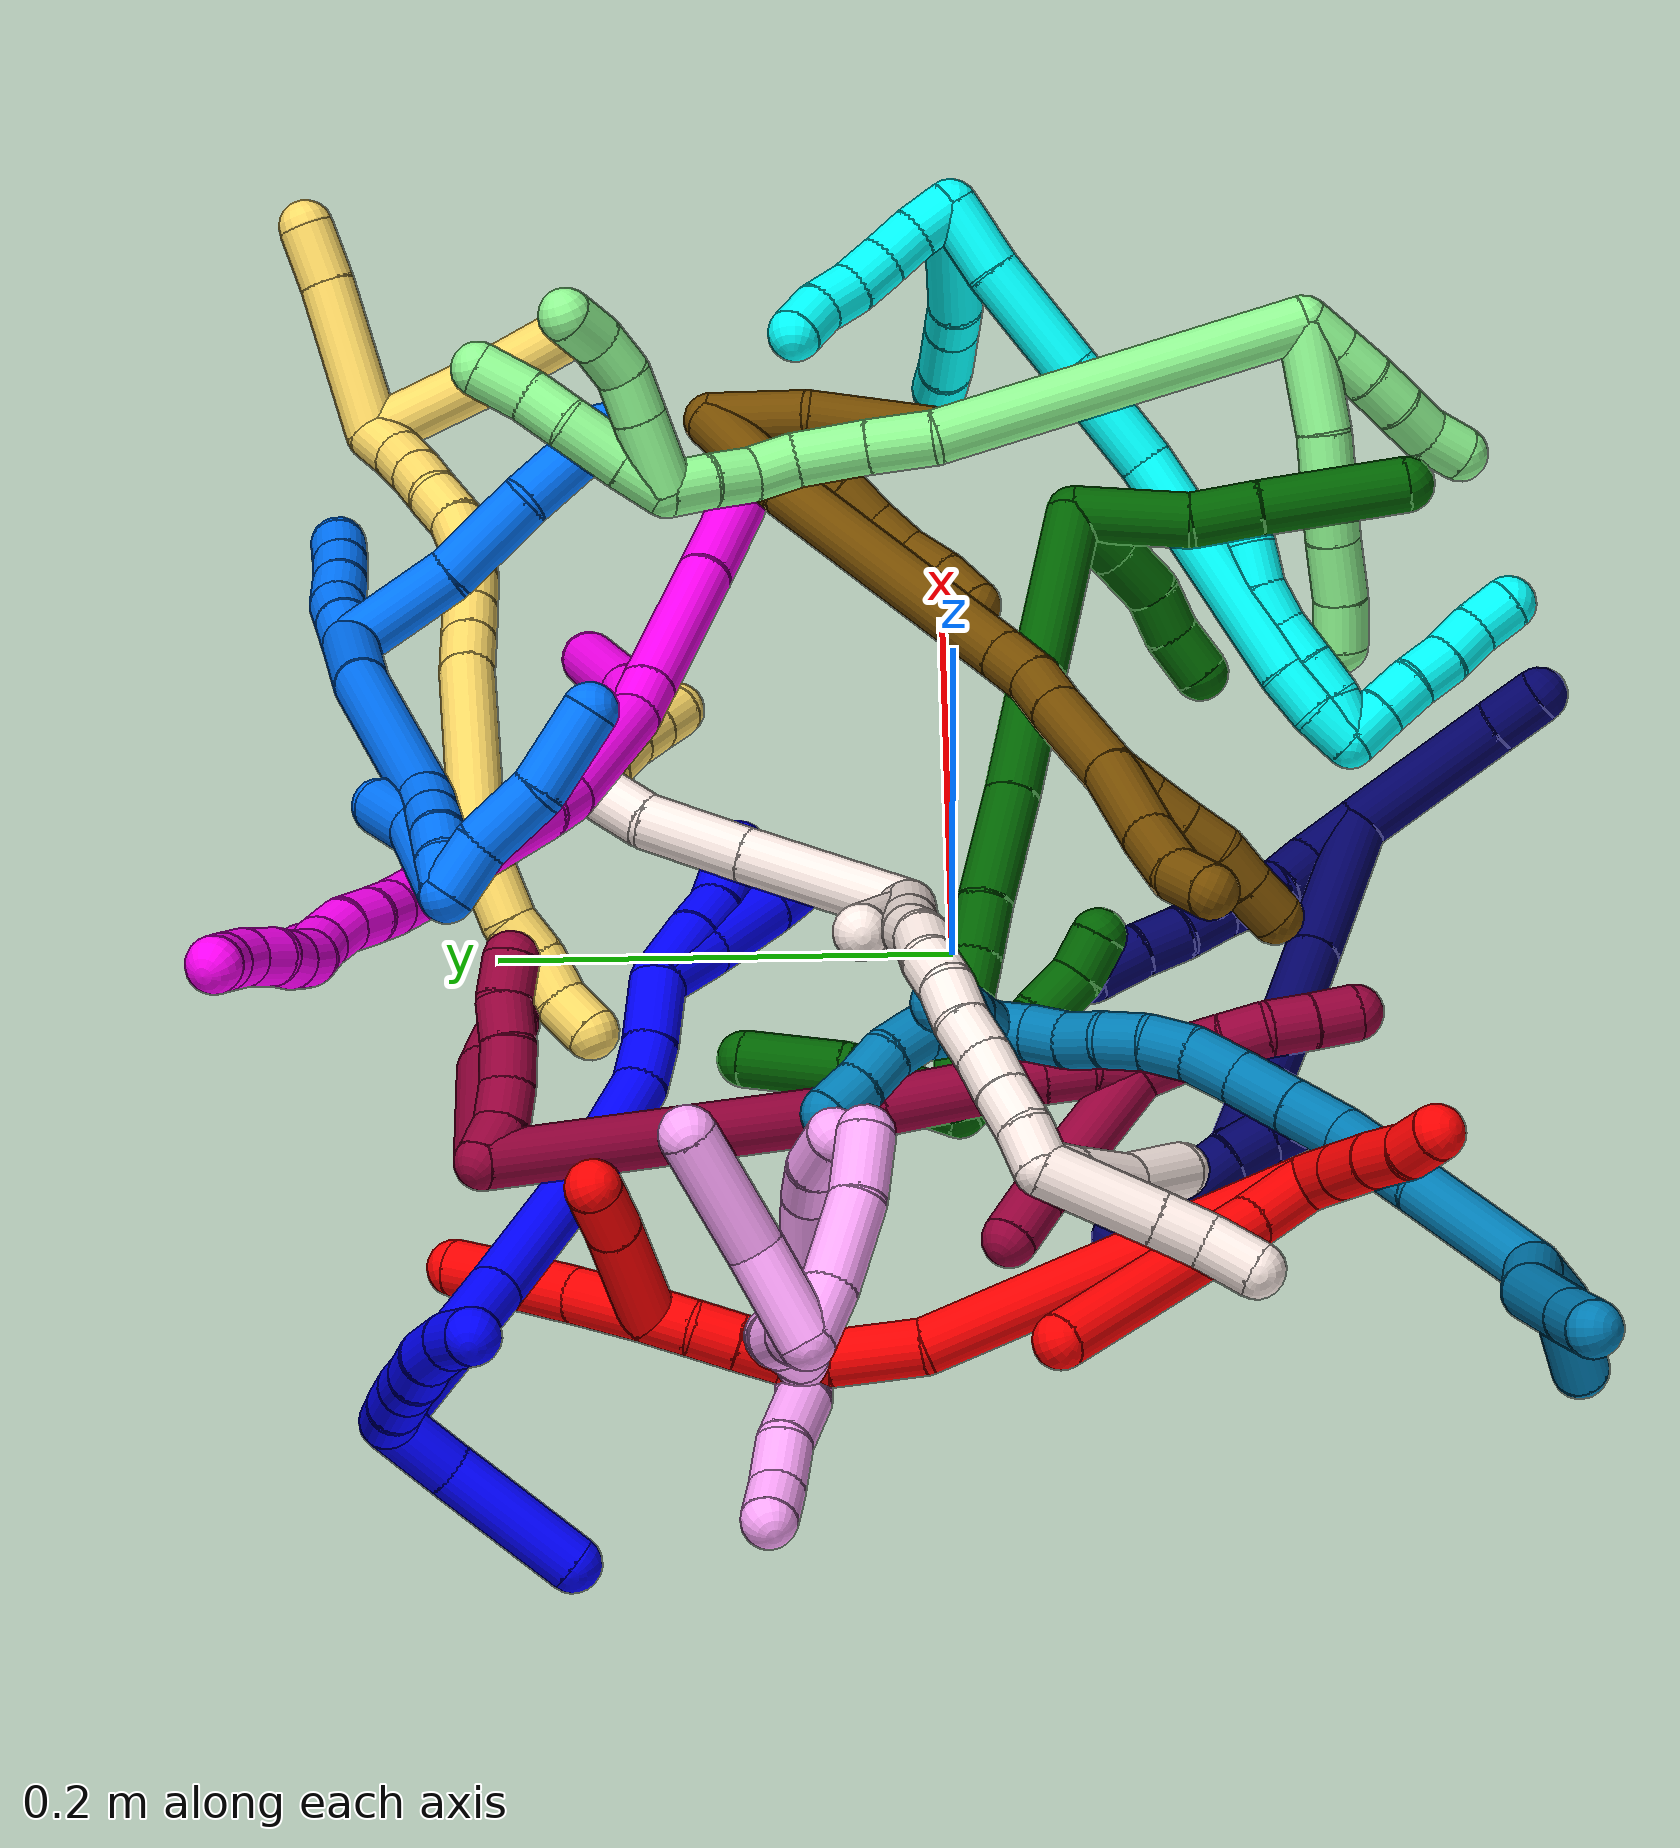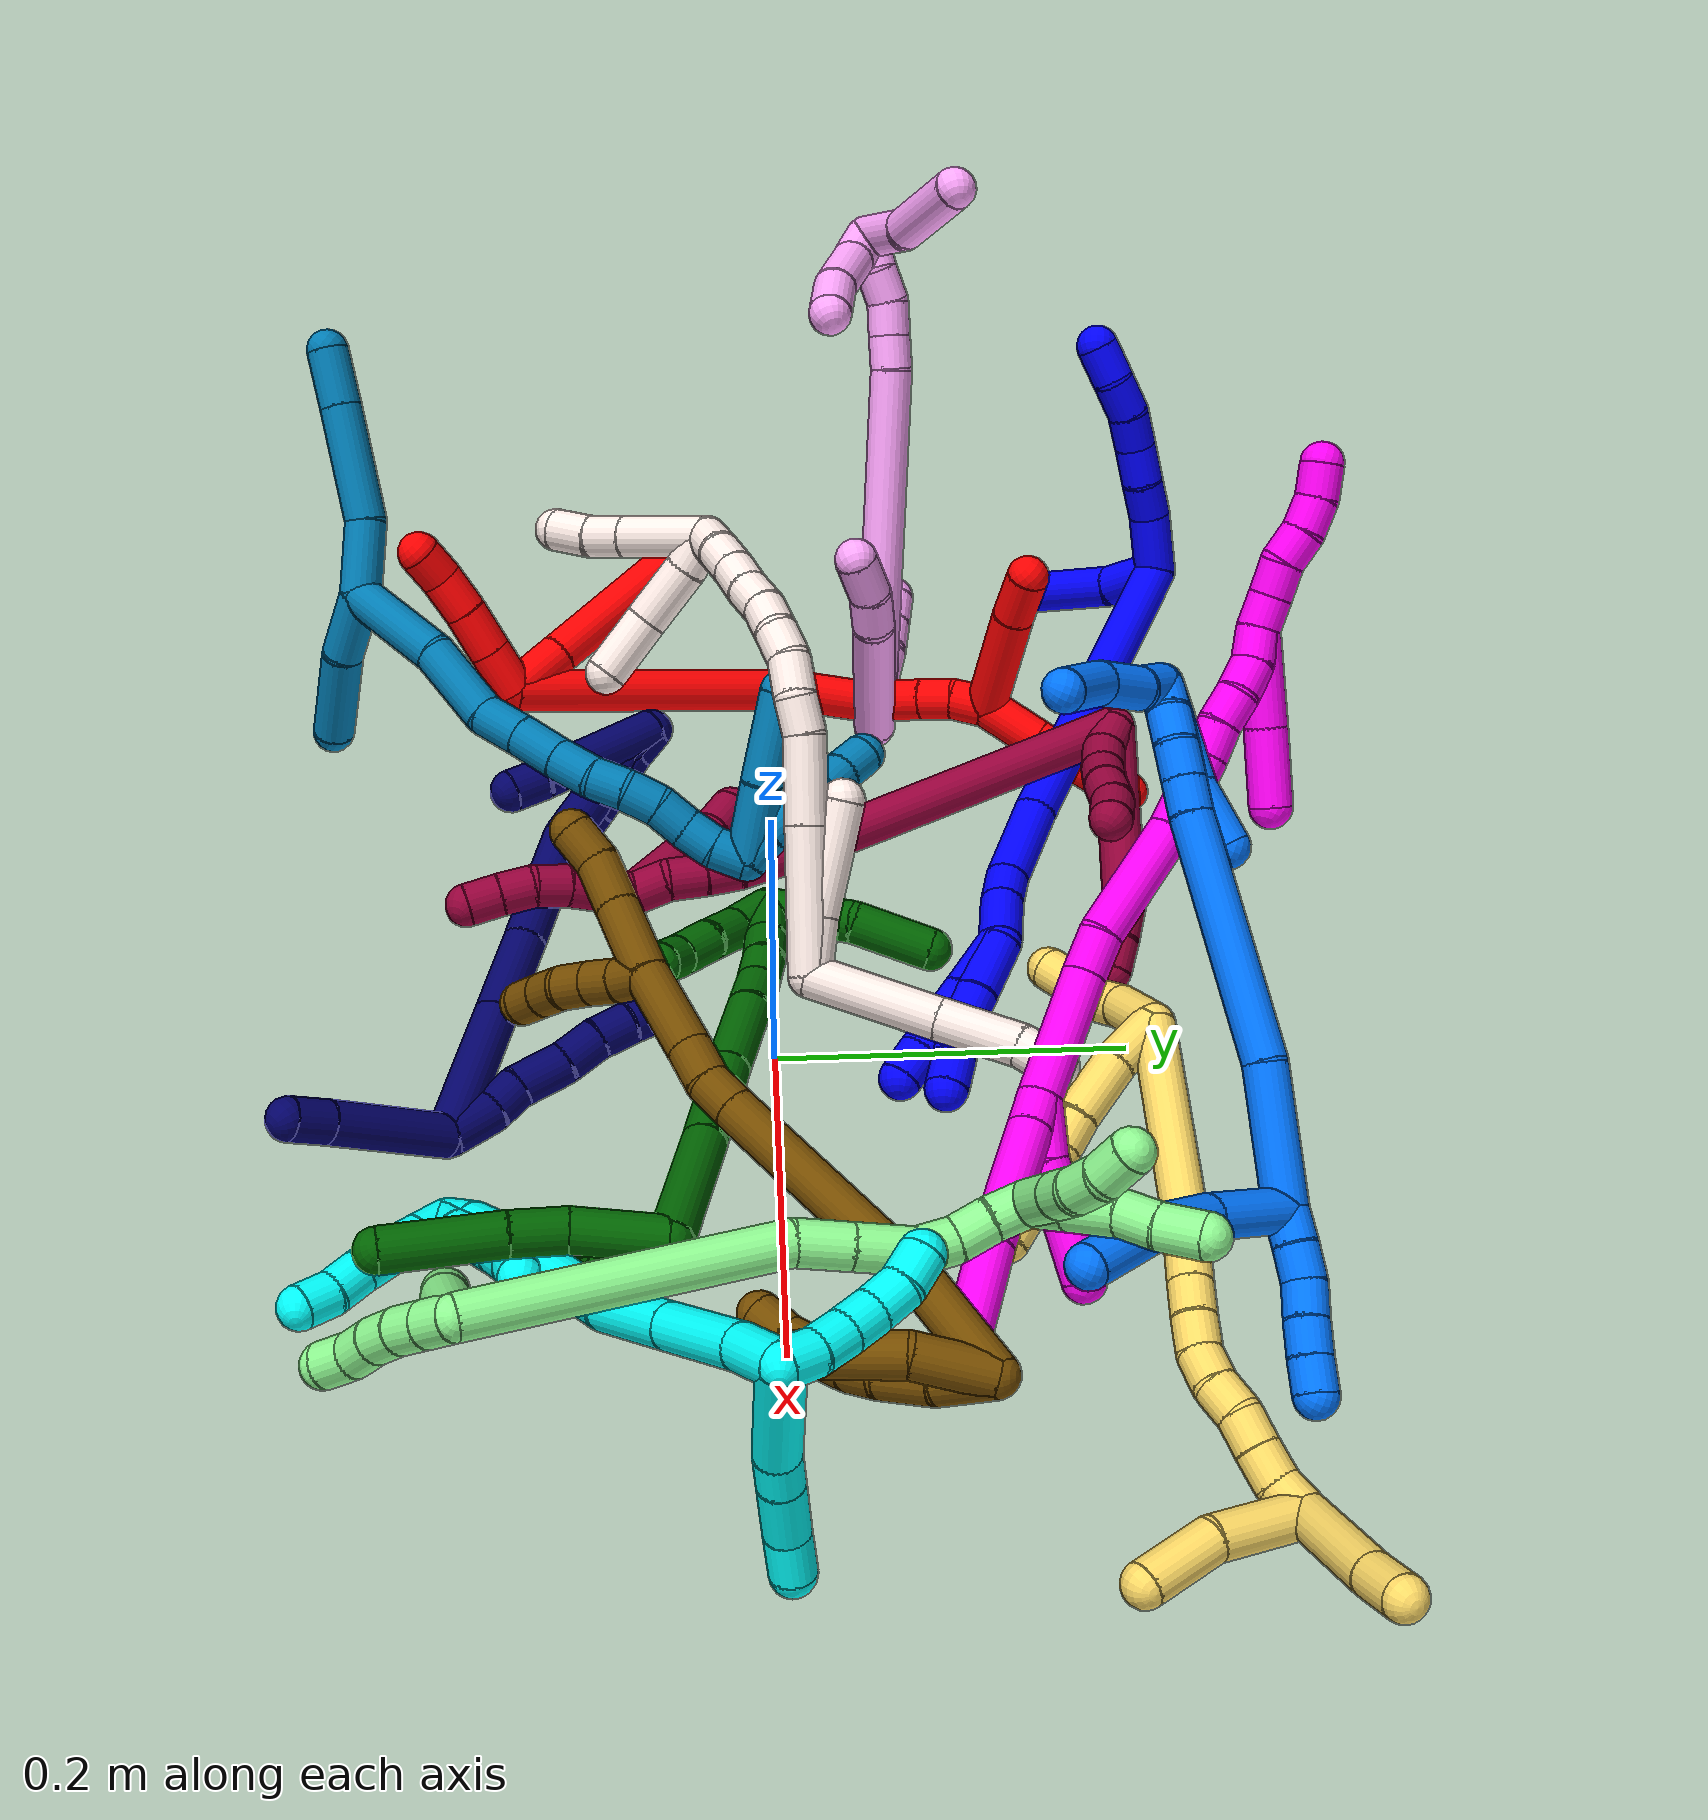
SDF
<sdf version="1.7">
 <world name="default">
  <plugin name="TubeGeneratorPlugin" filename="libtube_generator_plugin.so"/>
  <model name="photoneo_s_sensor">
   <static>1</static>
   <pose>0 0 2 1.57079 1.57079 3.14159</pose>
   <link name="link">
    <inertial><mass>0.1</mass></inertial>
    <sensor name="sensor" type="depth">
     <update_rate>30</update_rate>
     <camera>
      <horizontal_fov>1.22</horizontal_fov>
      <image><width>1920</width><height>1200</height><format>B8G8R8</format></image>
      <clip><near>0.1</near><far>4</far></clip>
      <depth_camera><output>points</output></depth_camera>
     </camera>
     <plugin name="camera_plugin" filename="libgazebo_ros_depth_camera.so">
      <baseline>0.2</baseline>
      <alwaysOn>1</alwaysOn>
      <updateRate>0.0</updateRate>
      <cameraName>camera_ir</cameraName>
      <imageTopicName>/camera/color/image_raw</imageTopicName>
      <cameraInfoTopicName>/camera/color/camera_info</cameraInfoTopicName>
      <depthImageTopicName>/camera/depth/image_raw</depthImageTopicName>
      <depthImageCameraInfoTopicName>/camera/depth/camera_info</depthImageCameraInfoTopicName>
      <pointCloudTopicName>/camera/depth/points</pointCloudTopicName>
      <frameName>fr_optical</frameName>
      <pointCloudCutoff>0.1</pointCloudCutoff>
      <pointCloudCutoffMax>2.0</pointCloudCutoffMax>
      <distortionK1>0</distortionK1>
      <distortionK2>0</distortionK2>
      <distortionK3>0</distortionK3>
      <distortionT1>0</distortionT1>
      <distortionT2>0</distortionT2>
      <CxPrime>0</CxPrime>
      <Cx>0</Cx>
      <Cy>0</Cy>
      <focalLength>0</focalLength>
      <hackBaseline>0</hackBaseline>
     </plugin>
    </sensor>
   </link>
  </model>
  <gravity>0 0 -9.8</gravity>
  <magnetic_field>6e-06 2.3e-05 -4.2e-05</magnetic_field>
  <atmosphere type="adiabatic"/>
  <physics name="default_physics" default="0" type="ode">
   <max_step_size>0.003</max_step_size>
   <real_time_factor>1</real_time_factor>
   <real_time_update_rate>1000</real_time_update_rate>
   <max_contacts>10000</max_contacts>
   <ode>
    <solver>
     <type>quick</type>
     <iters>100</iters>
     <sor>1.3</sor>
     <use_dynamic_moi_rescaling>0</use_dynamic_moi_rescaling>
    </solver>
    <constraints>
     <contact_max_correcting_vel>0</contact_max_correcting_vel>
     <contact_surface_layer>0.001</contact_surface_layer>
     <cfm>0</cfm>
     <erp>0.2</erp>
    </constraints>
   </ode>
  </physics>
  <scene><ambient>0.4 0.4 0.4 1</ambient><background>0.7 0.7 0.7 1</background><shadows>0</shadows></scene>
  <audio><device>default</device></audio>
  <spherical_coordinates>
   <surface_model>EARTH_WGS84</surface_model>
   <latitude_deg>0</latitude_deg>
   <longitude_deg>0</longitude_deg>
   <elevation>0</elevation>
   <heading_deg>0</heading_deg>
  </spherical_coordinates>
  <model name="bin">
   <static>1</static>
   <link name="bottom">
    <collision name="collision-bottom">
     <pose>0 0 -0.01 0 -0 0</pose>
     <geometry><box><size>0.8 0.6 0.02</size></box></geometry>
     <surface>
      <friction><ode><mu>100</mu><mu2>100</mu2></ode></friction>
      <contact><collide_bitmask>65535</collide_bitmask></contact>
     </surface>
    </collision>
   </link>
   <link name="west_wall">
    <collision name="collision-west_wall">
     <pose>-0.41 0 0.1 0 -0 0</pose>
     <geometry><box><size>0.02 0.6 0.2</size></box></geometry>
     <surface>
      <friction><ode><mu>100</mu><mu2>100</mu2></ode></friction>
      <contact><collide_bitmask>65535</collide_bitmask></contact>
     </surface>
    </collision>
   </link>
   <link name="east_wall">
    <collision name="collision-east_wall">
     <pose>0.41 0 0.1 0 -0 0</pose>
     <geometry><box><size>0.02 0.6 0.2</size></box></geometry>
     <surface>
      <friction><ode><mu>100</mu><mu2>100</mu2></ode></friction>
      <contact><collide_bitmask>65535</collide_bitmask></contact>
     </surface>
    </collision>
   </link>
   <link name="south_wall">
    <collision name="collision-south_wall">
     <pose>0 -0.31 0.1 0 -0 0</pose>
     <geometry><box><size>0.8 0.02 0.2</size></box></geometry>
     <surface>
      <friction><ode><mu>100</mu><mu2>100</mu2></ode></friction>
      <contact><collide_bitmask>65535</collide_bitmask></contact>
     </surface>
    </collision>
   </link>
   <link name="north_wall">
    <collision name="collision-north_wall">
     <pose>0 0.31 0.1 0 -0 0</pose>
     <geometry><box><size>0.8 0.02 0.2</size></box></geometry>
     <surface>
      <friction><ode><mu>100</mu><mu2>100</mu2></ode></friction>
      <contact><collide_bitmask>65535</collide_bitmask></contact>
     </surface>
    </collision>
   </link>
  </model>
  <model name="1">
   <static>0</static>
   <link name="1">
    <collision name="collision-cylinder-e_1_2_8">
     <pose>0.010541 -0.006153 0.013683 0.422619 0.612475 0.135443</pose>
     <geometry><cylinder><radius>0.0125</radius><length>0.036672</length></cylinder></geometry>
     <surface>
      <friction><ode><mu>1.16</mu><mu2>1.16</mu2><slip1>0</slip1><slip2>0</slip2></ode></friction>
      <contact><ode><kp>1e+06</kp><kd>1</kd><max_vel>0</max_vel><min_depth>0.001</min_depth></ode></contact>
     </surface>
    </collision>
    <visual name="visual-cylinder-e_1_2_8">
     <pose>0.010541 -0.006153 0.013683 0.422619 0.612475 0.135443</pose>
     <geometry><cylinder><radius>0.0125</radius><length>0.036672</length></cylinder></geometry>
     <material><ambient>0 0 1 1</ambient></material>
    </visual>
    <collision name="collision-cylinder-e_2_8_9">
     <pose>0.028342 -0.017466 0.034103 0.653488 0.707694 0.249073</pose>
     <geometry><cylinder><radius>0.0125</radius><length>0.022336</length></cylinder></geometry>
     <surface>
      <friction><ode><mu>1.16</mu><mu2>1.16</mu2><slip1>0</slip1><slip2>0</slip2></ode></friction>
      <contact><ode><kp>1e+06</kp><kd>1</kd><max_vel>0</max_vel><min_depth>0.001</min_depth></ode></contact>
     </surface>
    </collision>
    <visual name="visual-cylinder-e_2_8_9">
     <pose>0.028342 -0.017466 0.034103 0.653488 0.707694 0.249073</pose>
     <geometry><cylinder><radius>0.0125</radius><length>0.022336</length></cylinder></geometry>
     <material><ambient>0 0 1 1</ambient></material>
    </visual>
    <collision name="collision-cylinder-e_3_9_10">
     <pose>0.04216 -0.02768 0.049117 0.548318 0.594573 0.171901</pose>
     <geometry><cylinder><radius>0.0125</radius><length>0.023413</length></cylinder></geometry>
     <surface>
      <friction><ode><mu>1.16</mu><mu2>1.16</mu2><slip1>0</slip1><slip2>0</slip2></ode></friction>
      <contact><ode><kp>1e+06</kp><kd>1</kd><max_vel>0</max_vel><min_depth>0.001</min_depth></ode></contact>
     </surface>
    </collision>
    <visual name="visual-cylinder-e_3_9_10">
     <pose>0.04216 -0.02768 0.049117 0.548318 0.594573 0.171901</pose>
     <geometry><cylinder><radius>0.0125</radius><length>0.023413</length></cylinder></geometry>
     <material><ambient>0 0 1 1</ambient></material>
    </visual>
    <collision name="collision-cylinder-e_4_10_11">
     <pose>0.055863 -0.037794 0.06388 0.662361 0.715186 0.25556</pose>
     <geometry><cylinder><radius>0.0125</radius><length>0.021792</length></cylinder></geometry>
     <surface>
      <friction><ode><mu>1.16</mu><mu2>1.16</mu2><slip1>0</slip1><slip2>0</slip2></ode></friction>
      <contact><ode><kp>1e+06</kp><kd>1</kd><max_vel>0</max_vel><min_depth>0.001</min_depth></ode></contact>
     </surface>
    </collision>
    <visual name="visual-cylinder-e_4_10_11">
     <pose>0.055863 -0.037794 0.06388 0.662361 0.715186 0.25556</pose>
     <geometry><cylinder><radius>0.0125</radius><length>0.021792</length></cylinder></geometry>
     <material><ambient>0 0 1 1</ambient></material>
    </visual>
    <collision name="collision-cylinder-e_5_11_12">
     <pose>0.069214 -0.050173 0.077016 0.833357 0.560425 0.253379</pose>
     <geometry><cylinder><radius>0.0125</radius><length>0.02335</length></cylinder></geometry>
     <surface>
      <friction><ode><mu>1.16</mu><mu2>1.16</mu2><slip1>0</slip1><slip2>0</slip2></ode></friction>
      <contact><ode><kp>1e+06</kp><kd>1</kd><max_vel>0</max_vel><min_depth>0.001</min_depth></ode></contact>
     </surface>
    </collision>
    <visual name="visual-cylinder-e_5_11_12">
     <pose>0.069214 -0.050173 0.077016 0.833357 0.560425 0.253379</pose>
     <geometry><cylinder><radius>0.0125</radius><length>0.02335</length></cylinder></geometry>
     <material><ambient>0 0 1 1</ambient></material>
    </visual>
    <collision name="collision-cylinder-e_6_12_6">
     <pose>0.079566 -0.064241 0.09161 0.704134 0.378627 0.140551</pose>
     <geometry><cylinder><radius>0.0125</radius><length>0.022437</length></cylinder></geometry>
     <surface>
      <friction><ode><mu>1.16</mu><mu2>1.16</mu2><slip1>0</slip1><slip2>0</slip2></ode></friction>
      <contact><ode><kp>1e+06</kp><kd>1</kd><max_vel>0</max_vel><min_depth>0.001</min_depth></ode></contact>
     </surface>
    </collision>
    <visual name="visual-cylinder-e_6_12_6">
     <pose>0.079566 -0.064241 0.09161 0.704134 0.378627 0.140551</pose>
     <geometry><cylinder><radius>0.0125</radius><length>0.022437</length></cylinder></geometry>
     <material><ambient>0 0 1 1</ambient></material>
    </visual>
    <collision name="collision-cylinder-e_1_2_13">
     <pose>-0.014278 -0.009436 -0.000275 1.59989 -0.986645 -1.01111</pose>
     <geometry><cylinder><radius>0.0125</radius><length>0.034233</length></cylinder></geometry>
     <surface>
      <friction><ode><mu>1.16</mu><mu2>1.16</mu2><slip1>0</slip1><slip2>0</slip2></ode></friction>
      <contact><ode><kp>1e+06</kp><kd>1</kd><max_vel>0</max_vel><min_depth>0.001</min_depth></ode></contact>
     </surface>
    </collision>
    <visual name="visual-cylinder-e_1_2_13">
     <pose>-0.014278 -0.009436 -0.000275 1.59989 -0.986645 -1.01111</pose>
     <geometry><cylinder><radius>0.0125</radius><length>0.034233</length></cylinder></geometry>
     <material><ambient>0 0 1 1</ambient></material>
    </visual>
    <collision name="collision-cylinder-e_2_13_5">
     <pose>-0.05375 -0.039392 0.004502 1.32945 -0.87282 -0.70087</pose>
     <geometry><cylinder><radius>0.0125</radius><length>0.065767</length></cylinder></geometry>
     <surface>
      <friction><ode><mu>1.16</mu><mu2>1.16</mu2><slip1>0</slip1><slip2>0</slip2></ode></friction>
      <contact><ode><kp>1e+06</kp><kd>1</kd><max_vel>0</max_vel><min_depth>0.001</min_depth></ode></contact>
     </surface>
    </collision>
    <visual name="visual-cylinder-e_2_13_5">
     <pose>-0.05375 -0.039392 0.004502 1.32945 -0.87282 -0.70087</pose>
     <geometry><cylinder><radius>0.0125</radius><length>0.065767</length></cylinder></geometry>
     <material><ambient>0 0 1 1</ambient></material>
    </visual>
    <collision name="collision-cylinder-e_1_2_14">
     <pose>0.002238 -0.019502 -0.045027 2.73287 0.045583 0.219098</pose>
     <geometry><cylinder><radius>0.0125</radius><length>0.09824</length></cylinder></geometry>
     <surface>
      <friction><ode><mu>1.16</mu><mu2>1.16</mu2><slip1>0</slip1><slip2>0</slip2></ode></friction>
      <contact><ode><kp>1e+06</kp><kd>1</kd><max_vel>0</max_vel><min_depth>0.001</min_depth></ode></contact>
     </surface>
    </collision>
    <visual name="visual-cylinder-e_1_2_14">
     <pose>0.002238 -0.019502 -0.045027 2.73287 0.045583 0.219098</pose>
     <geometry><cylinder><radius>0.0125</radius><length>0.09824</length></cylinder></geometry>
     <material><ambient>0 0 1 1</ambient></material>
    </visual>
    <collision name="collision-cylinder-e_2_14_15">
     <pose>0.007773 -0.0579 -0.13322 2.72895 0.069842 0.330784</pose>
     <geometry><cylinder><radius>0.0125</radius><length>0.09447</length></cylinder></geometry>
     <surface>
      <friction><ode><mu>1.16</mu><mu2>1.16</mu2><slip1>0</slip1><slip2>0</slip2></ode></friction>
      <contact><ode><kp>1e+06</kp><kd>1</kd><max_vel>0</max_vel><min_depth>0.001</min_depth></ode></contact>
     </surface>
    </collision>
    <visual name="visual-cylinder-e_2_14_15">
     <pose>0.007773 -0.0579 -0.13322 2.72895 0.069842 0.330784</pose>
     <geometry><cylinder><radius>0.0125</radius><length>0.09447</length></cylinder></geometry>
     <material><ambient>0 0 1 1</ambient></material>
    </visual>
    <collision name="collision-cylinder-e_3_15_16">
     <pose>0.014817 -0.085995 -0.20003 2.77057 0.146669 0.746253</pose>
     <geometry><cylinder><radius>0.0125</radius><length>0.051294</length></cylinder></geometry>
     <surface>
      <friction><ode><mu>1.16</mu><mu2>1.16</mu2><slip1>0</slip1><slip2>0</slip2></ode></friction>
      <contact><ode><kp>1e+06</kp><kd>1</kd><max_vel>0</max_vel><min_depth>0.001</min_depth></ode></contact>
     </surface>
    </collision>
    <visual name="visual-cylinder-e_3_15_16">
     <pose>0.014817 -0.085995 -0.20003 2.77057 0.146669 0.746253</pose>
     <geometry><cylinder><radius>0.0125</radius><length>0.051294</length></cylinder></geometry>
     <material><ambient>0 0 1 1</ambient></material>
    </visual>
    <collision name="collision-cylinder-e_4_16_17">
     <pose>0.023023 -0.097952 -0.233424 2.86587 0.414502 1.97509</pose>
     <geometry><cylinder><radius>0.0125</radius><length>0.022138</length></cylinder></geometry>
     <surface>
      <friction><ode><mu>1.16</mu><mu2>1.16</mu2><slip1>0</slip1><slip2>0</slip2></ode></friction>
      <contact><ode><kp>1e+06</kp><kd>1</kd><max_vel>0</max_vel><min_depth>0.001</min_depth></ode></contact>
     </surface>
    </collision>
    <visual name="visual-cylinder-e_4_16_17">
     <pose>0.023023 -0.097952 -0.233424 2.86587 0.414502 1.97509</pose>
     <geometry><cylinder><radius>0.0125</radius><length>0.022138</length></cylinder></geometry>
     <material><ambient>0 0 1 1</ambient></material>
    </visual>
    <collision name="collision-cylinder-e_5_17_1">
     <pose>0.035326 -0.103407 -0.25793 2.96089 0.48183 2.43501</pose>
     <geometry><cylinder><radius>0.0125</radius><length>0.033858</length></cylinder></geometry>
     <surface>
      <friction><ode><mu>1.16</mu><mu2>1.16</mu2><slip1>0</slip1><slip2>0</slip2></ode></friction>
      <contact><ode><kp>1e+06</kp><kd>1</kd><max_vel>0</max_vel><min_depth>0.001</min_depth></ode></contact>
     </surface>
    </collision>
    <visual name="visual-cylinder-e_5_17_1">
     <pose>0.035326 -0.103407 -0.25793 2.96089 0.48183 2.43501</pose>
     <geometry><cylinder><radius>0.0125</radius><length>0.033858</length></cylinder></geometry>
     <material><ambient>0 0 1 1</ambient></material>
    </visual>
    <collision name="collision-cylinder-e_1_1_18">
     <pose>0.044368 -0.112933 -0.289083 2.74688 0.067298 0.333559</pose>
     <geometry><cylinder><radius>0.0125</radius><length>0.035604</length></cylinder></geometry>
     <surface>
      <friction><ode><mu>1.16</mu><mu2>1.16</mu2><slip1>0</slip1><slip2>0</slip2></ode></friction>
      <contact><ode><kp>1e+06</kp><kd>1</kd><max_vel>0</max_vel><min_depth>0.001</min_depth></ode></contact>
     </surface>
    </collision>
    <visual name="visual-cylinder-e_1_1_18">
     <pose>0.044368 -0.112933 -0.289083 2.74688 0.067298 0.333559</pose>
     <geometry><cylinder><radius>0.0125</radius><length>0.035604</length></cylinder></geometry>
     <material><ambient>0 0 1 1</ambient></material>
    </visual>
    <collision name="collision-cylinder-e_2_18_19">
     <pose>0.045646 -0.124087 -0.316248 2.75975 0.006955 0.035984</pose>
     <geometry><cylinder><radius>0.0125</radius><length>0.023209</length></cylinder></geometry>
     <surface>
      <friction><ode><mu>1.16</mu><mu2>1.16</mu2><slip1>0</slip1><slip2>0</slip2></ode></friction>
      <contact><ode><kp>1e+06</kp><kd>1</kd><max_vel>0</max_vel><min_depth>0.001</min_depth></ode></contact>
     </surface>
    </collision>
    <visual name="visual-cylinder-e_2_18_19">
     <pose>0.045646 -0.124087 -0.316248 2.75975 0.006955 0.035984</pose>
     <geometry><cylinder><radius>0.0125</radius><length>0.023209</length></cylinder></geometry>
     <material><ambient>0 0 1 1</ambient></material>
    </visual>
    <collision name="collision-cylinder-e_3_19_20">
     <pose>0.047107 -0.130358 -0.33685 2.94615 0.136824 1.22004</pose>
     <geometry><cylinder><radius>0.0125</radius><length>0.020239</length></cylinder></geometry>
     <surface>
      <friction><ode><mu>1.16</mu><mu2>1.16</mu2><slip1>0</slip1><slip2>0</slip2></ode></friction>
      <contact><ode><kp>1e+06</kp><kd>1</kd><max_vel>0</max_vel><min_depth>0.001</min_depth></ode></contact>
     </surface>
    </collision>
    <visual name="visual-cylinder-e_3_19_20">
     <pose>0.047107 -0.130358 -0.33685 2.94615 0.136824 1.22004</pose>
     <geometry><cylinder><radius>0.0125</radius><length>0.020239</length></cylinder></geometry>
     <material><ambient>0 0 1 1</ambient></material>
    </visual>
    <collision name="collision-cylinder-e_4_20_4">
     <pose>0.050504 -0.134795 -0.356656 2.89693 0.193746 1.33773</pose>
     <geometry><cylinder><radius>0.0125</radius><length>0.020949</length></cylinder></geometry>
     <surface>
      <friction><ode><mu>1.16</mu><mu2>1.16</mu2><slip1>0</slip1><slip2>0</slip2></ode></friction>
      <contact><ode><kp>1e+06</kp><kd>1</kd><max_vel>0</max_vel><min_depth>0.001</min_depth></ode></contact>
     </surface>
    </collision>
    <visual name="visual-cylinder-e_4_20_4">
     <pose>0.050504 -0.134795 -0.356656 2.89693 0.193746 1.33773</pose>
     <geometry><cylinder><radius>0.0125</radius><length>0.020949</length></cylinder></geometry>
     <material><ambient>0 0 1 1</ambient></material>
    </visual>
    <collision name="collision-cylinder-e_1_1_21">
     <pose>0.040372 -0.115122 -0.287786 2.60315 -0.157853 -0.558321</pose>
     <geometry><cylinder><radius>0.0125</radius><length>0.035617</length></cylinder></geometry>
     <surface>
      <friction><ode><mu>1.16</mu><mu2>1.16</mu2><slip1>0</slip1><slip2>0</slip2></ode></friction>
      <contact><ode><kp>1e+06</kp><kd>1</kd><max_vel>0</max_vel><min_depth>0.001</min_depth></ode></contact>
     </surface>
    </collision>
    <visual name="visual-cylinder-e_1_1_21">
     <pose>0.040372 -0.115122 -0.287786 2.60315 -0.157853 -0.558321</pose>
     <geometry><cylinder><radius>0.0125</radius><length>0.035617</length></cylinder></geometry>
     <material><ambient>0 0 1 1</ambient></material>
    </visual>
    <collision name="collision-cylinder-e_2_21_22">
     <pose>0.035302 -0.135758 -0.321426 2.58185 -0.103363 -0.356136</pose>
     <geometry><cylinder><radius>0.0125</radius><length>0.043995</length></cylinder></geometry>
     <surface>
      <friction><ode><mu>1.16</mu><mu2>1.16</mu2><slip1>0</slip1><slip2>0</slip2></ode></friction>
      <contact><ode><kp>1e+06</kp><kd>1</kd><max_vel>0</max_vel><min_depth>0.001</min_depth></ode></contact>
     </surface>
    </collision>
    <visual name="visual-cylinder-e_2_21_22">
     <pose>0.035302 -0.135758 -0.321426 2.58185 -0.103363 -0.356136</pose>
     <geometry><cylinder><radius>0.0125</radius><length>0.043995</length></cylinder></geometry>
     <material><ambient>0 0 1 1</ambient></material>
    </visual>
    <collision name="collision-cylinder-e_3_22_3">
     <pose>0.032588 -0.152664 -0.34867 2.59554 -0.043604 -0.155428</pose>
     <geometry><cylinder><radius>0.0125</radius><length>0.020388</length></cylinder></geometry>
     <surface>
      <friction><ode><mu>1.16</mu><mu2>1.16</mu2><slip1>0</slip1><slip2>0</slip2></ode></friction>
      <contact><ode><kp>1e+06</kp><kd>1</kd><max_vel>0</max_vel><min_depth>0.001</min_depth></ode></contact>
     </surface>
    </collision>
    <visual name="visual-cylinder-e_3_22_3">
     <pose>0.032588 -0.152664 -0.34867 2.59554 -0.043604 -0.155428</pose>
     <geometry><cylinder><radius>0.0125</radius><length>0.020388</length></cylinder></geometry>
     <material><ambient>0 0 1 1</ambient></material>
    </visual>
    <collision name="collision-sphere-3">
     <pose>0.032144 -0.157953 -0.357373 0 -0 0</pose>
     <geometry><sphere><radius>0.0125</radius></sphere></geometry>
     <surface>
      <friction><ode><mu>1.16</mu><mu2>1.16</mu2><slip1>0</slip1><slip2>0</slip2></ode></friction>
      <contact><ode><kp>1e+06</kp><kd>1</kd><max_vel>0</max_vel><min_depth>0.001</min_depth></ode></contact>
     </surface>
    </collision>
    <visual name="visual-sphere-3">
     <pose>0.032144 -0.157953 -0.357373 0 -0 0</pose>
     <geometry><sphere><radius>0.0125</radius></sphere></geometry>
     <material><ambient>0 0 1 1</ambient></material>
    </visual>
    <collision name="collision-sphere-22">
     <pose>0.033033 -0.147375 -0.339967 0 -0 0</pose>
     <geometry><sphere><radius>0.0125</radius></sphere></geometry>
     <surface>
      <friction><ode><mu>1.16</mu><mu2>1.16</mu2><slip1>0</slip1><slip2>0</slip2></ode></friction>
      <contact><ode><kp>1e+06</kp><kd>1</kd><max_vel>0</max_vel><min_depth>0.001</min_depth></ode></contact>
     </surface>
    </collision>
    <visual name="visual-sphere-22">
     <pose>0.033033 -0.147375 -0.339967 0 -0 0</pose>
     <geometry><sphere><radius>0.0125</radius></sphere></geometry>
     <material><ambient>0 0 1 1</ambient></material>
    </visual>
    <collision name="collision-sphere-21">
     <pose>0.037572 -0.12414 -0.302885 0 -0 0</pose>
     <geometry><sphere><radius>0.0125</radius></sphere></geometry>
     <surface>
      <friction><ode><mu>1.16</mu><mu2>1.16</mu2><slip1>0</slip1><slip2>0</slip2></ode></friction>
      <contact><ode><kp>1e+06</kp><kd>1</kd><max_vel>0</max_vel><min_depth>0.001</min_depth></ode></contact>
     </surface>
    </collision>
    <visual name="visual-sphere-21">
     <pose>0.037572 -0.12414 -0.302885 0 -0 0</pose>
     <geometry><sphere><radius>0.0125</radius></sphere></geometry>
     <material><ambient>0 0 1 1</ambient></material>
    </visual>
    <collision name="collision-sphere-4">
     <pose>0.052521 -0.137284 -0.366628 0 -0 0</pose>
     <geometry><sphere><radius>0.0125</radius></sphere></geometry>
     <surface>
      <friction><ode><mu>1.16</mu><mu2>1.16</mu2><slip1>0</slip1><slip2>0</slip2></ode></friction>
      <contact><ode><kp>1e+06</kp><kd>1</kd><max_vel>0</max_vel><min_depth>0.001</min_depth></ode></contact>
     </surface>
    </collision>
    <visual name="visual-sphere-4">
     <pose>0.052521 -0.137284 -0.366628 0 -0 0</pose>
     <geometry><sphere><radius>0.0125</radius></sphere></geometry>
     <material><ambient>0 0 1 1</ambient></material>
    </visual>
    <collision name="collision-sphere-20">
     <pose>0.048487 -0.132305 -0.346684 0 -0 0</pose>
     <geometry><sphere><radius>0.0125</radius></sphere></geometry>
     <surface>
      <friction><ode><mu>1.16</mu><mu2>1.16</mu2><slip1>0</slip1><slip2>0</slip2></ode></friction>
      <contact><ode><kp>1e+06</kp><kd>1</kd><max_vel>0</max_vel><min_depth>0.001</min_depth></ode></contact>
     </surface>
    </collision>
    <visual name="visual-sphere-20">
     <pose>0.048487 -0.132305 -0.346684 0 -0 0</pose>
     <geometry><sphere><radius>0.0125</radius></sphere></geometry>
     <material><ambient>0 0 1 1</ambient></material>
    </visual>
    <collision name="collision-sphere-12">
     <pose>0.07542 -0.057493 0.083665 0 -0 0</pose>
     <geometry><sphere><radius>0.0125</radius></sphere></geometry>
     <surface>
      <friction><ode><mu>1.16</mu><mu2>1.16</mu2><slip1>0</slip1><slip2>0</slip2></ode></friction>
      <contact><ode><kp>1e+06</kp><kd>1</kd><max_vel>0</max_vel><min_depth>0.001</min_depth></ode></contact>
     </surface>
    </collision>
    <visual name="visual-sphere-12">
     <pose>0.07542 -0.057493 0.083665 0 -0 0</pose>
     <geometry><sphere><radius>0.0125</radius></sphere></geometry>
     <material><ambient>0 0 1 1</ambient></material>
    </visual>
    <collision name="collision-sphere-11">
     <pose>0.063008 -0.042853 0.070367 0 -0 0</pose>
     <geometry><sphere><radius>0.0125</radius></sphere></geometry>
     <surface>
      <friction><ode><mu>1.16</mu><mu2>1.16</mu2><slip1>0</slip1><slip2>0</slip2></ode></friction>
      <contact><ode><kp>1e+06</kp><kd>1</kd><max_vel>0</max_vel><min_depth>0.001</min_depth></ode></contact>
     </surface>
    </collision>
    <visual name="visual-sphere-11">
     <pose>0.063008 -0.042853 0.070367 0 -0 0</pose>
     <geometry><sphere><radius>0.0125</radius></sphere></geometry>
     <material><ambient>0 0 1 1</ambient></material>
    </visual>
    <collision name="collision-sphere-10">
     <pose>0.048718 -0.032735 0.057393 0 -0 0</pose>
     <geometry><sphere><radius>0.0125</radius></sphere></geometry>
     <surface>
      <friction><ode><mu>1.16</mu><mu2>1.16</mu2><slip1>0</slip1><slip2>0</slip2></ode></friction>
      <contact><ode><kp>1e+06</kp><kd>1</kd><max_vel>0</max_vel><min_depth>0.001</min_depth></ode></contact>
     </surface>
    </collision>
    <visual name="visual-sphere-10">
     <pose>0.048718 -0.032735 0.057393 0 -0 0</pose>
     <geometry><sphere><radius>0.0125</radius></sphere></geometry>
     <material><ambient>0 0 1 1</ambient></material>
    </visual>
    <collision name="collision-sphere-9">
     <pose>0.035603 -0.022625 0.040841 0 -0 0</pose>
     <geometry><sphere><radius>0.0125</radius></sphere></geometry>
     <surface>
      <friction><ode><mu>1.16</mu><mu2>1.16</mu2><slip1>0</slip1><slip2>0</slip2></ode></friction>
      <contact><ode><kp>1e+06</kp><kd>1</kd><max_vel>0</max_vel><min_depth>0.001</min_depth></ode></contact>
     </surface>
    </collision>
    <visual name="visual-sphere-9">
     <pose>0.035603 -0.022625 0.040841 0 -0 0</pose>
     <geometry><sphere><radius>0.0125</radius></sphere></geometry>
     <material><ambient>0 0 1 1</ambient></material>
    </visual>
    <collision name="collision-sphere-2">
     <geometry><sphere><radius>0.0125</radius></sphere></geometry>
     <surface>
      <friction><ode><mu>1.16</mu><mu2>1.16</mu2><slip1>0</slip1><slip2>0</slip2></ode></friction>
      <contact><ode><kp>1e+06</kp><kd>1</kd><max_vel>0</max_vel><min_depth>0.001</min_depth></ode></contact>
     </surface>
    </collision>
    <visual name="visual-sphere-2">
     <geometry><sphere><radius>0.0125</radius></sphere></geometry>
     <material><ambient>0 0 1 1</ambient></material>
    </visual>
    <collision name="collision-sphere-19">
     <pose>0.045727 -0.128411 -0.327016 0 -0 0</pose>
     <geometry><sphere><radius>0.0125</radius></sphere></geometry>
     <surface>
      <friction><ode><mu>1.16</mu><mu2>1.16</mu2><slip1>0</slip1><slip2>0</slip2></ode></friction>
      <contact><ode><kp>1e+06</kp><kd>1</kd><max_vel>0</max_vel><min_depth>0.001</min_depth></ode></contact>
     </surface>
    </collision>
    <visual name="visual-sphere-19">
     <pose>0.045727 -0.128411 -0.327016 0 -0 0</pose>
     <geometry><sphere><radius>0.0125</radius></sphere></geometry>
     <material><ambient>0 0 1 1</ambient></material>
    </visual>
    <collision name="collision-sphere-8">
     <pose>0.021082 -0.012307 0.027366 0 -0 0</pose>
     <geometry><sphere><radius>0.0125</radius></sphere></geometry>
     <surface>
      <friction><ode><mu>1.16</mu><mu2>1.16</mu2><slip1>0</slip1><slip2>0</slip2></ode></friction>
      <contact><ode><kp>1e+06</kp><kd>1</kd><max_vel>0</max_vel><min_depth>0.001</min_depth></ode></contact>
     </surface>
    </collision>
    <visual name="visual-sphere-8">
     <pose>0.021082 -0.012307 0.027366 0 -0 0</pose>
     <geometry><sphere><radius>0.0125</radius></sphere></geometry>
     <material><ambient>0 0 1 1</ambient></material>
    </visual>
    <collision name="collision-sphere-6">
     <pose>0.083713 -0.070989 0.099555 0 -0 0</pose>
     <geometry><sphere><radius>0.0125</radius></sphere></geometry>
     <surface>
      <friction><ode><mu>1.16</mu><mu2>1.16</mu2><slip1>0</slip1><slip2>0</slip2></ode></friction>
      <contact><ode><kp>1e+06</kp><kd>1</kd><max_vel>0</max_vel><min_depth>0.001</min_depth></ode></contact>
     </surface>
    </collision>
    <visual name="visual-sphere-6">
     <pose>0.083713 -0.070989 0.099555 0 -0 0</pose>
     <geometry><sphere><radius>0.0125</radius></sphere></geometry>
     <material><ambient>0 0 1 1</ambient></material>
    </visual>
    <collision name="collision-sphere-13">
     <pose>-0.028556 -0.018871 -0.000549 0 -0 0</pose>
     <geometry><sphere><radius>0.0125</radius></sphere></geometry>
     <surface>
      <friction><ode><mu>1.16</mu><mu2>1.16</mu2><slip1>0</slip1><slip2>0</slip2></ode></friction>
      <contact><ode><kp>1e+06</kp><kd>1</kd><max_vel>0</max_vel><min_depth>0.001</min_depth></ode></contact>
     </surface>
    </collision>
    <visual name="visual-sphere-13">
     <pose>-0.028556 -0.018871 -0.000549 0 -0 0</pose>
     <geometry><sphere><radius>0.0125</radius></sphere></geometry>
     <material><ambient>0 0 1 1</ambient></material>
    </visual>
    <collision name="collision-sphere-5">
     <pose>-0.078943 -0.059913 0.009553 0 -0 0</pose>
     <geometry><sphere><radius>0.0125</radius></sphere></geometry>
     <surface>
      <friction><ode><mu>1.16</mu><mu2>1.16</mu2><slip1>0</slip1><slip2>0</slip2></ode></friction>
      <contact><ode><kp>1e+06</kp><kd>1</kd><max_vel>0</max_vel><min_depth>0.001</min_depth></ode></contact>
     </surface>
    </collision>
    <visual name="visual-sphere-5">
     <pose>-0.078943 -0.059913 0.009553 0 -0 0</pose>
     <geometry><sphere><radius>0.0125</radius></sphere></geometry>
     <material><ambient>0 0 1 1</ambient></material>
    </visual>
    <collision name="collision-sphere-14">
     <pose>0.004477 -0.039003 -0.090055 0 -0 0</pose>
     <geometry><sphere><radius>0.0125</radius></sphere></geometry>
     <surface>
      <friction><ode><mu>1.16</mu><mu2>1.16</mu2><slip1>0</slip1><slip2>0</slip2></ode></friction>
      <contact><ode><kp>1e+06</kp><kd>1</kd><max_vel>0</max_vel><min_depth>0.001</min_depth></ode></contact>
     </surface>
    </collision>
    <visual name="visual-sphere-14">
     <pose>0.004477 -0.039003 -0.090055 0 -0 0</pose>
     <geometry><sphere><radius>0.0125</radius></sphere></geometry>
     <material><ambient>0 0 1 1</ambient></material>
    </visual>
    <collision name="collision-sphere-15">
     <pose>0.011069 -0.076796 -0.176385 0 -0 0</pose>
     <geometry><sphere><radius>0.0125</radius></sphere></geometry>
     <surface>
      <friction><ode><mu>1.16</mu><mu2>1.16</mu2><slip1>0</slip1><slip2>0</slip2></ode></friction>
      <contact><ode><kp>1e+06</kp><kd>1</kd><max_vel>0</max_vel><min_depth>0.001</min_depth></ode></contact>
     </surface>
    </collision>
    <visual name="visual-sphere-15">
     <pose>0.011069 -0.076796 -0.176385 0 -0 0</pose>
     <geometry><sphere><radius>0.0125</radius></sphere></geometry>
     <material><ambient>0 0 1 1</ambient></material>
    </visual>
    <collision name="collision-sphere-16">
     <pose>0.018565 -0.095194 -0.223675 0 -0 0</pose>
     <geometry><sphere><radius>0.0125</radius></sphere></geometry>
     <surface>
      <friction><ode><mu>1.16</mu><mu2>1.16</mu2><slip1>0</slip1><slip2>0</slip2></ode></friction>
      <contact><ode><kp>1e+06</kp><kd>1</kd><max_vel>0</max_vel><min_depth>0.001</min_depth></ode></contact>
     </surface>
    </collision>
    <visual name="visual-sphere-16">
     <pose>0.018565 -0.095194 -0.223675 0 -0 0</pose>
     <geometry><sphere><radius>0.0125</radius></sphere></geometry>
     <material><ambient>0 0 1 1</ambient></material>
    </visual>
    <collision name="collision-sphere-17">
     <pose>0.027481 -0.100711 -0.243172 0 -0 0</pose>
     <geometry><sphere><radius>0.0125</radius></sphere></geometry>
     <surface>
      <friction><ode><mu>1.16</mu><mu2>1.16</mu2><slip1>0</slip1><slip2>0</slip2></ode></friction>
      <contact><ode><kp>1e+06</kp><kd>1</kd><max_vel>0</max_vel><min_depth>0.001</min_depth></ode></contact>
     </surface>
    </collision>
    <visual name="visual-sphere-17">
     <pose>0.027481 -0.100711 -0.243172 0 -0 0</pose>
     <geometry><sphere><radius>0.0125</radius></sphere></geometry>
     <material><ambient>0 0 1 1</ambient></material>
    </visual>
    <collision name="collision-sphere-1">
     <pose>0.043171 -0.106103 -0.272687 0 -0 0</pose>
     <geometry><sphere><radius>0.0125</radius></sphere></geometry>
     <surface>
      <friction><ode><mu>1.16</mu><mu2>1.16</mu2><slip1>0</slip1><slip2>0</slip2></ode></friction>
      <contact><ode><kp>1e+06</kp><kd>1</kd><max_vel>0</max_vel><min_depth>0.001</min_depth></ode></contact>
     </surface>
    </collision>
    <visual name="visual-sphere-1">
     <pose>0.043171 -0.106103 -0.272687 0 -0 0</pose>
     <geometry><sphere><radius>0.0125</radius></sphere></geometry>
     <material><ambient>0 0 1 1</ambient></material>
    </visual>
    <collision name="collision-sphere-18">
     <pose>0.045565 -0.119763 -0.305479 0 -0 0</pose>
     <geometry><sphere><radius>0.0125</radius></sphere></geometry>
     <surface>
      <friction><ode><mu>1.16</mu><mu2>1.16</mu2><slip1>0</slip1><slip2>0</slip2></ode></friction>
      <contact><ode><kp>1e+06</kp><kd>1</kd><max_vel>0</max_vel><min_depth>0.001</min_depth></ode></contact>
     </surface>
    </collision>
    <visual name="visual-sphere-18">
     <pose>0.045565 -0.119763 -0.305479 0 -0 0</pose>
     <geometry><sphere><radius>0.0125</radius></sphere></geometry>
     <material><ambient>0 0 1 1</ambient></material>
    </visual>
    <inertial>
     <pose>0.019103 -0.067505 -0.128859 0 -0 0</pose>
     <mass>0.75</mass>
     <inertia>
      <ixx>0.000251</ixx>
      <ixy>0</ixy>
      <ixz>0</ixz>
      <iyy>-0.000109</iyy>
      <iyz>0</iyz>
      <izz>8.2e-05</izz>
     </inertia>
    </inertial>
   </link>
   <pose>-0.317996 0.245467 0.070875 -0.643328 -1.10816 0.601817</pose>
  </model>
  <model name="2">
   <static>0</static>
   <link name="2">
    <collision name="collision-cylinder-e_1_2_8">
     <pose>-0.011073 0.014046 -0.002919 -1.77568 -0.657359 0.793906</pose>
     <geometry><cylinder><radius>0.0125</radius><length>0.036245</length></cylinder></geometry>
     <surface>
      <friction><ode><mu>1.16</mu><mu2>1.16</mu2><slip1>0</slip1><slip2>0</slip2></ode></friction>
      <contact><ode><kp>1e+06</kp><kd>1</kd><max_vel>0</max_vel><min_depth>0.001</min_depth></ode></contact>
     </surface>
    </collision>
    <visual name="visual-cylinder-e_1_2_8">
     <pose>-0.011073 0.014046 -0.002919 -1.77568 -0.657359 0.793906</pose>
     <geometry><cylinder><radius>0.0125</radius><length>0.036245</length></cylinder></geometry>
     <material><ambient>1 0 0 1</ambient></material>
    </visual>
    <collision name="collision-cylinder-e_2_8_6">
     <pose>-0.054946 0.073743 -0.014512 -1.75858 -0.614635 0.732157</pose>
     <geometry><cylinder><radius>0.0125</radius><length>0.113755</length></cylinder></geometry>
     <surface>
      <friction><ode><mu>1.16</mu><mu2>1.16</mu2><slip1>0</slip1><slip2>0</slip2></ode></friction>
      <contact><ode><kp>1e+06</kp><kd>1</kd><max_vel>0</max_vel><min_depth>0.001</min_depth></ode></contact>
     </surface>
    </collision>
    <visual name="visual-cylinder-e_2_8_6">
     <pose>-0.054946 0.073743 -0.014512 -1.75858 -0.614635 0.732157</pose>
     <geometry><cylinder><radius>0.0125</radius><length>0.113755</length></cylinder></geometry>
     <material><ambient>1 0 0 1</ambient></material>
    </visual>
    <collision name="collision-cylinder-e_1_2_9">
     <pose>-0.001184 0.002636 0.013831 -0.188351 -0.083894 0.007929</pose>
     <geometry><cylinder><radius>0.0125</radius><length>0.028259</length></cylinder></geometry>
     <surface>
      <friction><ode><mu>1.16</mu><mu2>1.16</mu2><slip1>0</slip1><slip2>0</slip2></ode></friction>
      <contact><ode><kp>1e+06</kp><kd>1</kd><max_vel>0</max_vel><min_depth>0.001</min_depth></ode></contact>
     </surface>
    </collision>
    <visual name="visual-cylinder-e_1_2_9">
     <pose>-0.001184 0.002636 0.013831 -0.188351 -0.083894 0.007929</pose>
     <geometry><cylinder><radius>0.0125</radius><length>0.028259</length></cylinder></geometry>
     <material><ambient>1 0 0 1</ambient></material>
    </visual>
    <collision name="collision-cylinder-e_2_9_10">
     <pose>-0.003573 0.007901 0.040931 -0.195561 -0.088871 0.008723</pose>
     <geometry><cylinder><radius>0.0125</radius><length>0.027161</length></cylinder></geometry>
     <surface>
      <friction><ode><mu>1.16</mu><mu2>1.16</mu2><slip1>0</slip1><slip2>0</slip2></ode></friction>
      <contact><ode><kp>1e+06</kp><kd>1</kd><max_vel>0</max_vel><min_depth>0.001</min_depth></ode></contact>
     </surface>
    </collision>
    <visual name="visual-cylinder-e_2_9_10">
     <pose>-0.003573 0.007901 0.040931 -0.195561 -0.088871 0.008723</pose>
     <geometry><cylinder><radius>0.0125</radius><length>0.027161</length></cylinder></geometry>
     <material><ambient>1 0 0 1</ambient></material>
    </visual>
    <collision name="collision-cylinder-e_3_10_11">
     <pose>-0.00606 0.011959 0.066266 -0.117895 -0.105067 0.006206</pose>
     <geometry><cylinder><radius>0.0125</radius><length>0.024435</length></cylinder></geometry>
     <surface>
      <friction><ode><mu>1.16</mu><mu2>1.16</mu2><slip1>0</slip1><slip2>0</slip2></ode></friction>
      <contact><ode><kp>1e+06</kp><kd>1</kd><max_vel>0</max_vel><min_depth>0.001</min_depth></ode></contact>
     </surface>
    </collision>
    <visual name="visual-cylinder-e_3_10_11">
     <pose>-0.00606 0.011959 0.066266 -0.117895 -0.105067 0.006206</pose>
     <geometry><cylinder><radius>0.0125</radius><length>0.024435</length></cylinder></geometry>
     <material><ambient>1 0 0 1</ambient></material>
    </visual>
    <collision name="collision-cylinder-e_4_11_5">
     <pose>-0.005901 0.014362 0.088253 -0.097848 0.143487 -0.007038</pose>
     <geometry><cylinder><radius>0.0125</radius><length>0.020145</length></cylinder></geometry>
     <surface>
      <friction><ode><mu>1.16</mu><mu2>1.16</mu2><slip1>0</slip1><slip2>0</slip2></ode></friction>
      <contact><ode><kp>1e+06</kp><kd>1</kd><max_vel>0</max_vel><min_depth>0.001</min_depth></ode></contact>
     </surface>
    </collision>
    <visual name="visual-cylinder-e_4_11_5">
     <pose>-0.005901 0.014362 0.088253 -0.097848 0.143487 -0.007038</pose>
     <geometry><cylinder><radius>0.0125</radius><length>0.020145</length></cylinder></geometry>
     <material><ambient>1 0 0 1</ambient></material>
    </visual>
    <collision name="collision-cylinder-e_1_2_12">
     <pose>-0.031998 0.05284 -0.063558 -2.44801 -0.369361 0.954169</pose>
     <geometry><cylinder><radius>0.0125</radius><length>0.177263</length></cylinder></geometry>
     <surface>
      <friction><ode><mu>1.16</mu><mu2>1.16</mu2><slip1>0</slip1><slip2>0</slip2></ode></friction>
      <contact><ode><kp>1e+06</kp><kd>1</kd><max_vel>0</max_vel><min_depth>0.001</min_depth></ode></contact>
     </surface>
    </collision>
    <visual name="visual-cylinder-e_1_2_12">
     <pose>-0.031998 0.05284 -0.063558 -2.44801 -0.369361 0.954169</pose>
     <geometry><cylinder><radius>0.0125</radius><length>0.177263</length></cylinder></geometry>
     <material><ambient>1 0 0 1</ambient></material>
    </visual>
    <collision name="collision-cylinder-e_2_12_13">
     <pose>-0.065394 0.118323 -0.143329 -2.47931 -0.067911 0.196966</pose>
     <geometry><cylinder><radius>0.0125</radius><length>0.041214</length></cylinder></geometry>
     <surface>
      <friction><ode><mu>1.16</mu><mu2>1.16</mu2><slip1>0</slip1><slip2>0</slip2></ode></friction>
      <contact><ode><kp>1e+06</kp><kd>1</kd><max_vel>0</max_vel><min_depth>0.001</min_depth></ode></contact>
     </surface>
    </collision>
    <visual name="visual-cylinder-e_2_12_13">
     <pose>-0.065394 0.118323 -0.143329 -2.47931 -0.067911 0.196966</pose>
     <geometry><cylinder><radius>0.0125</radius><length>0.041214</length></cylinder></geometry>
     <material><ambient>1 0 0 1</ambient></material>
    </visual>
    <collision name="collision-cylinder-e_3_13_14">
     <pose>-0.066078 0.138608 -0.166241 -2.29053 0.070173 -0.154586</pose>
     <geometry><cylinder><radius>0.0125</radius><length>0.020377</length></cylinder></geometry>
     <surface>
      <friction><ode><mu>1.16</mu><mu2>1.16</mu2><slip1>0</slip1><slip2>0</slip2></ode></friction>
      <contact><ode><kp>1e+06</kp><kd>1</kd><max_vel>0</max_vel><min_depth>0.001</min_depth></ode></contact>
     </surface>
    </collision>
    <visual name="visual-cylinder-e_3_13_14">
     <pose>-0.066078 0.138608 -0.166241 -2.29053 0.070173 -0.154586</pose>
     <geometry><cylinder><radius>0.0125</radius><length>0.020377</length></cylinder></geometry>
     <material><ambient>1 0 0 1</ambient></material>
    </visual>
    <collision name="collision-cylinder-e_4_14_15">
     <pose>-0.062807 0.154491 -0.178057 -2.12643 0.257741 -0.457821</pose>
     <geometry><cylinder><radius>0.0125</radius><length>0.020062</length></cylinder></geometry>
     <surface>
      <friction><ode><mu>1.16</mu><mu2>1.16</mu2><slip1>0</slip1><slip2>0</slip2></ode></friction>
      <contact><ode><kp>1e+06</kp><kd>1</kd><max_vel>0</max_vel><min_depth>0.001</min_depth></ode></contact>
     </surface>
    </collision>
    <visual name="visual-cylinder-e_4_14_15">
     <pose>-0.062807 0.154491 -0.178057 -2.12643 0.257741 -0.457821</pose>
     <geometry><cylinder><radius>0.0125</radius><length>0.020062</length></cylinder></geometry>
     <material><ambient>1 0 0 1</ambient></material>
    </visual>
    <collision name="collision-cylinder-e_5_15_16">
     <pose>-0.057416 0.170776 -0.188587 -2.16308 0.28433 -0.525228</pose>
     <geometry><cylinder><radius>0.0125</radius><length>0.020203</length></cylinder></geometry>
     <surface>
      <friction><ode><mu>1.16</mu><mu2>1.16</mu2><slip1>0</slip1><slip2>0</slip2></ode></friction>
      <contact><ode><kp>1e+06</kp><kd>1</kd><max_vel>0</max_vel><min_depth>0.001</min_depth></ode></contact>
     </surface>
    </collision>
    <visual name="visual-cylinder-e_5_15_16">
     <pose>-0.057416 0.170776 -0.188587 -2.16308 0.28433 -0.525228</pose>
     <geometry><cylinder><radius>0.0125</radius><length>0.020203</length></cylinder></geometry>
     <material><ambient>1 0 0 1</ambient></material>
    </visual>
    <collision name="collision-cylinder-e_6_16_1">
     <pose>-0.05112 0.185506 -0.201232 -2.39547 0.338083 -0.822407</pose>
     <geometry><cylinder><radius>0.0125</radius><length>0.020881</length></cylinder></geometry>
     <surface>
      <friction><ode><mu>1.16</mu><mu2>1.16</mu2><slip1>0</slip1><slip2>0</slip2></ode></friction>
      <contact><ode><kp>1e+06</kp><kd>1</kd><max_vel>0</max_vel><min_depth>0.001</min_depth></ode></contact>
     </surface>
    </collision>
    <visual name="visual-cylinder-e_6_16_1">
     <pose>-0.05112 0.185506 -0.201232 -2.39547 0.338083 -0.822407</pose>
     <geometry><cylinder><radius>0.0125</radius><length>0.020881</length></cylinder></geometry>
     <material><ambient>1 0 0 1</ambient></material>
    </visual>
    <collision name="collision-cylinder-e_1_1_17">
     <pose>-0.040964 0.198383 -0.224663 -2.77654 0.368313 -1.57988</pose>
     <geometry><cylinder><radius>0.0125</radius><length>0.037176</length></cylinder></geometry>
     <surface>
      <friction><ode><mu>1.16</mu><mu2>1.16</mu2><slip1>0</slip1><slip2>0</slip2></ode></friction>
      <contact><ode><kp>1e+06</kp><kd>1</kd><max_vel>0</max_vel><min_depth>0.001</min_depth></ode></contact>
     </surface>
    </collision>
    <visual name="visual-cylinder-e_1_1_17">
     <pose>-0.040964 0.198383 -0.224663 -2.77654 0.368313 -1.57988</pose>
     <geometry><cylinder><radius>0.0125</radius><length>0.037176</length></cylinder></geometry>
     <material><ambient>1 0 0 1</ambient></material>
    </visual>
    <collision name="collision-cylinder-e_2_17_18">
     <pose>-0.029208 0.210287 -0.253815 -2.7262 0.3435 -1.37736</pose>
     <geometry><cylinder><radius>0.0125</radius><length>0.030071</length></cylinder></geometry>
     <surface>
      <friction><ode><mu>1.16</mu><mu2>1.16</mu2><slip1>0</slip1><slip2>0</slip2></ode></friction>
      <contact><ode><kp>1e+06</kp><kd>1</kd><max_vel>0</max_vel><min_depth>0.001</min_depth></ode></contact>
     </surface>
    </collision>
    <visual name="visual-cylinder-e_2_17_18">
     <pose>-0.029208 0.210287 -0.253815 -2.7262 0.3435 -1.37736</pose>
     <geometry><cylinder><radius>0.0125</radius><length>0.030071</length></cylinder></geometry>
     <material><ambient>1 0 0 1</ambient></material>
    </visual>
    <collision name="collision-cylinder-e_3_18_4">
     <pose>-0.018965 0.221984 -0.281106 -2.74622 0.321825 -1.36204</pose>
     <geometry><cylinder><radius>0.0125</radius><length>0.032753</length></cylinder></geometry>
     <surface>
      <friction><ode><mu>1.16</mu><mu2>1.16</mu2><slip1>0</slip1><slip2>0</slip2></ode></friction>
      <contact><ode><kp>1e+06</kp><kd>1</kd><max_vel>0</max_vel><min_depth>0.001</min_depth></ode></contact>
     </surface>
    </collision>
    <visual name="visual-cylinder-e_3_18_4">
     <pose>-0.018965 0.221984 -0.281106 -2.74622 0.321825 -1.36204</pose>
     <geometry><cylinder><radius>0.0125</radius><length>0.032753</length></cylinder></geometry>
     <material><ambient>1 0 0 1</ambient></material>
    </visual>
    <collision name="collision-cylinder-e_1_1_19">
     <pose>-0.038285 0.218813 -0.18788 -0.912583 0.271619 -0.133946</pose>
     <geometry><cylinder><radius>0.0125</radius><length>0.069864</length></cylinder></geometry>
     <surface>
      <friction><ode><mu>1.16</mu><mu2>1.16</mu2><slip1>0</slip1><slip2>0</slip2></ode></friction>
      <contact><ode><kp>1e+06</kp><kd>1</kd><max_vel>0</max_vel><min_depth>0.001</min_depth></ode></contact>
     </surface>
    </collision>
    <visual name="visual-cylinder-e_1_1_19">
     <pose>-0.038285 0.218813 -0.18788 -0.912583 0.271619 -0.133946</pose>
     <geometry><cylinder><radius>0.0125</radius><length>0.069864</length></cylinder></geometry>
     <material><ambient>1 0 0 1</ambient></material>
    </visual>
    <collision name="collision-cylinder-e_2_19_3">
     <pose>-0.024597 0.257312 -0.159089 -0.966188 0.290513 -0.153169</pose>
     <geometry><cylinder><radius>0.0125</radius><length>0.030136</length></cylinder></geometry>
     <surface>
      <friction><ode><mu>1.16</mu><mu2>1.16</mu2><slip1>0</slip1><slip2>0</slip2></ode></friction>
      <contact><ode><kp>1e+06</kp><kd>1</kd><max_vel>0</max_vel><min_depth>0.001</min_depth></ode></contact>
     </surface>
    </collision>
    <visual name="visual-cylinder-e_2_19_3">
     <pose>-0.024597 0.257312 -0.159089 -0.966188 0.290513 -0.153169</pose>
     <geometry><cylinder><radius>0.0125</radius><length>0.030136</length></cylinder></geometry>
     <material><ambient>1 0 0 1</ambient></material>
    </visual>
    <collision name="collision-sphere-3">
     <pose>-0.020281 0.269189 -0.150883 0 -0 0</pose>
     <geometry><sphere><radius>0.0125</radius></sphere></geometry>
     <surface>
      <friction><ode><mu>1.16</mu><mu2>1.16</mu2><slip1>0</slip1><slip2>0</slip2></ode></friction>
      <contact><ode><kp>1e+06</kp><kd>1</kd><max_vel>0</max_vel><min_depth>0.001</min_depth></ode></contact>
     </surface>
    </collision>
    <visual name="visual-sphere-3">
     <pose>-0.020281 0.269189 -0.150883 0 -0 0</pose>
     <geometry><sphere><radius>0.0125</radius></sphere></geometry>
     <material><ambient>1 0 0 1</ambient></material>
    </visual>
    <collision name="collision-sphere-19">
     <pose>-0.028913 0.245435 -0.167295 0 -0 0</pose>
     <geometry><sphere><radius>0.0125</radius></sphere></geometry>
     <surface>
      <friction><ode><mu>1.16</mu><mu2>1.16</mu2><slip1>0</slip1><slip2>0</slip2></ode></friction>
      <contact><ode><kp>1e+06</kp><kd>1</kd><max_vel>0</max_vel><min_depth>0.001</min_depth></ode></contact>
     </surface>
    </collision>
    <visual name="visual-sphere-19">
     <pose>-0.028913 0.245435 -0.167295 0 -0 0</pose>
     <geometry><sphere><radius>0.0125</radius></sphere></geometry>
     <material><ambient>1 0 0 1</ambient></material>
    </visual>
    <collision name="collision-sphere-11">
     <pose>-0.007341 0.013388 0.078332 0 -0 0</pose>
     <geometry><sphere><radius>0.0125</radius></sphere></geometry>
     <surface>
      <friction><ode><mu>1.16</mu><mu2>1.16</mu2><slip1>0</slip1><slip2>0</slip2></ode></friction>
      <contact><ode><kp>1e+06</kp><kd>1</kd><max_vel>0</max_vel><min_depth>0.001</min_depth></ode></contact>
     </surface>
    </collision>
    <visual name="visual-sphere-11">
     <pose>-0.007341 0.013388 0.078332 0 -0 0</pose>
     <geometry><sphere><radius>0.0125</radius></sphere></geometry>
     <material><ambient>1 0 0 1</ambient></material>
    </visual>
    <collision name="collision-sphere-10">
     <pose>-0.004779 0.01053 0.0542 0 -0 0</pose>
     <geometry><sphere><radius>0.0125</radius></sphere></geometry>
     <surface>
      <friction><ode><mu>1.16</mu><mu2>1.16</mu2><slip1>0</slip1><slip2>0</slip2></ode></friction>
      <contact><ode><kp>1e+06</kp><kd>1</kd><max_vel>0</max_vel><min_depth>0.001</min_depth></ode></contact>
     </surface>
    </collision>
    <visual name="visual-sphere-10">
     <pose>-0.004779 0.01053 0.0542 0 -0 0</pose>
     <geometry><sphere><radius>0.0125</radius></sphere></geometry>
     <material><ambient>1 0 0 1</ambient></material>
    </visual>
    <collision name="collision-sphere-6">
     <pose>-0.087745 0.119394 -0.023187 0 -0 0</pose>
     <geometry><sphere><radius>0.0125</radius></sphere></geometry>
     <surface>
      <friction><ode><mu>1.16</mu><mu2>1.16</mu2><slip1>0</slip1><slip2>0</slip2></ode></friction>
      <contact><ode><kp>1e+06</kp><kd>1</kd><max_vel>0</max_vel><min_depth>0.001</min_depth></ode></contact>
     </surface>
    </collision>
    <visual name="visual-sphere-6">
     <pose>-0.087745 0.119394 -0.023187 0 -0 0</pose>
     <geometry><sphere><radius>0.0125</radius></sphere></geometry>
     <material><ambient>1 0 0 1</ambient></material>
    </visual>
    <collision name="collision-sphere-9">
     <pose>-0.002368 0.005273 0.027662 0 -0 0</pose>
     <geometry><sphere><radius>0.0125</radius></sphere></geometry>
     <surface>
      <friction><ode><mu>1.16</mu><mu2>1.16</mu2><slip1>0</slip1><slip2>0</slip2></ode></friction>
      <contact><ode><kp>1e+06</kp><kd>1</kd><max_vel>0</max_vel><min_depth>0.001</min_depth></ode></contact>
     </surface>
    </collision>
    <visual name="visual-sphere-9">
     <pose>-0.002368 0.005273 0.027662 0 -0 0</pose>
     <geometry><sphere><radius>0.0125</radius></sphere></geometry>
     <material><ambient>1 0 0 1</ambient></material>
    </visual>
    <collision name="collision-sphere-2">
     <geometry><sphere><radius>0.0125</radius></sphere></geometry>
     <surface>
      <friction><ode><mu>1.16</mu><mu2>1.16</mu2><slip1>0</slip1><slip2>0</slip2></ode></friction>
      <contact><ode><kp>1e+06</kp><kd>1</kd><max_vel>0</max_vel><min_depth>0.001</min_depth></ode></contact>
     </surface>
    </collision>
    <visual name="visual-sphere-2">
     <geometry><sphere><radius>0.0125</radius></sphere></geometry>
     <material><ambient>1 0 0 1</ambient></material>
    </visual>
    <collision name="collision-sphere-8">
     <pose>-0.022147 0.028092 -0.005838 0 -0 0</pose>
     <geometry><sphere><radius>0.0125</radius></sphere></geometry>
     <surface>
      <friction><ode><mu>1.16</mu><mu2>1.16</mu2><slip1>0</slip1><slip2>0</slip2></ode></friction>
      <contact><ode><kp>1e+06</kp><kd>1</kd><max_vel>0</max_vel><min_depth>0.001</min_depth></ode></contact>
     </surface>
    </collision>
    <visual name="visual-sphere-8">
     <pose>-0.022147 0.028092 -0.005838 0 -0 0</pose>
     <geometry><sphere><radius>0.0125</radius></sphere></geometry>
     <material><ambient>1 0 0 1</ambient></material>
    </visual>
    <collision name="collision-sphere-5">
     <pose>-0.004461 0.015336 0.098174 0 -0 0</pose>
     <geometry><sphere><radius>0.0125</radius></sphere></geometry>
     <surface>
      <friction><ode><mu>1.16</mu><mu2>1.16</mu2><slip1>0</slip1><slip2>0</slip2></ode></friction>
      <contact><ode><kp>1e+06</kp><kd>1</kd><max_vel>0</max_vel><min_depth>0.001</min_depth></ode></contact>
     </surface>
    </collision>
    <visual name="visual-sphere-5">
     <pose>-0.004461 0.015336 0.098174 0 -0 0</pose>
     <geometry><sphere><radius>0.0125</radius></sphere></geometry>
     <material><ambient>1 0 0 1</ambient></material>
    </visual>
    <collision name="collision-sphere-12">
     <pose>-0.063995 0.105681 -0.127116 0 -0 0</pose>
     <geometry><sphere><radius>0.0125</radius></sphere></geometry>
     <surface>
      <friction><ode><mu>1.16</mu><mu2>1.16</mu2><slip1>0</slip1><slip2>0</slip2></ode></friction>
      <contact><ode><kp>1e+06</kp><kd>1</kd><max_vel>0</max_vel><min_depth>0.001</min_depth></ode></contact>
     </surface>
    </collision>
    <visual name="visual-sphere-12">
     <pose>-0.063995 0.105681 -0.127116 0 -0 0</pose>
     <geometry><sphere><radius>0.0125</radius></sphere></geometry>
     <material><ambient>1 0 0 1</ambient></material>
    </visual>
    <collision name="collision-sphere-13">
     <pose>-0.066792 0.130966 -0.159542 0 -0 0</pose>
     <geometry><sphere><radius>0.0125</radius></sphere></geometry>
     <surface>
      <friction><ode><mu>1.16</mu><mu2>1.16</mu2><slip1>0</slip1><slip2>0</slip2></ode></friction>
      <contact><ode><kp>1e+06</kp><kd>1</kd><max_vel>0</max_vel><min_depth>0.001</min_depth></ode></contact>
     </surface>
    </collision>
    <visual name="visual-sphere-13">
     <pose>-0.066792 0.130966 -0.159542 0 -0 0</pose>
     <geometry><sphere><radius>0.0125</radius></sphere></geometry>
     <material><ambient>1 0 0 1</ambient></material>
    </visual>
    <collision name="collision-sphere-14">
     <pose>-0.065363 0.146251 -0.172941 0 -0 0</pose>
     <geometry><sphere><radius>0.0125</radius></sphere></geometry>
     <surface>
      <friction><ode><mu>1.16</mu><mu2>1.16</mu2><slip1>0</slip1><slip2>0</slip2></ode></friction>
      <contact><ode><kp>1e+06</kp><kd>1</kd><max_vel>0</max_vel><min_depth>0.001</min_depth></ode></contact>
     </surface>
    </collision>
    <visual name="visual-sphere-14">
     <pose>-0.065363 0.146251 -0.172941 0 -0 0</pose>
     <geometry><sphere><radius>0.0125</radius></sphere></geometry>
     <material><ambient>1 0 0 1</ambient></material>
    </visual>
    <collision name="collision-sphere-15">
     <pose>-0.06025 0.162732 -0.183174 0 -0 0</pose>
     <geometry><sphere><radius>0.0125</radius></sphere></geometry>
     <surface>
      <friction><ode><mu>1.16</mu><mu2>1.16</mu2><slip1>0</slip1><slip2>0</slip2></ode></friction>
      <contact><ode><kp>1e+06</kp><kd>1</kd><max_vel>0</max_vel><min_depth>0.001</min_depth></ode></contact>
     </surface>
    </collision>
    <visual name="visual-sphere-15">
     <pose>-0.06025 0.162732 -0.183174 0 -0 0</pose>
     <geometry><sphere><radius>0.0125</radius></sphere></geometry>
     <material><ambient>1 0 0 1</ambient></material>
    </visual>
    <collision name="collision-sphere-16">
     <pose>-0.054582 0.178821 -0.193999 0 -0 0</pose>
     <geometry><sphere><radius>0.0125</radius></sphere></geometry>
     <surface>
      <friction><ode><mu>1.16</mu><mu2>1.16</mu2><slip1>0</slip1><slip2>0</slip2></ode></friction>
      <contact><ode><kp>1e+06</kp><kd>1</kd><max_vel>0</max_vel><min_depth>0.001</min_depth></ode></contact>
     </surface>
    </collision>
    <visual name="visual-sphere-16">
     <pose>-0.054582 0.178821 -0.193999 0 -0 0</pose>
     <geometry><sphere><radius>0.0125</radius></sphere></geometry>
     <material><ambient>1 0 0 1</ambient></material>
    </visual>
    <collision name="collision-sphere-1">
     <pose>-0.047657 0.192192 -0.208465 0 -0 0</pose>
     <geometry><sphere><radius>0.0125</radius></sphere></geometry>
     <surface>
      <friction><ode><mu>1.16</mu><mu2>1.16</mu2><slip1>0</slip1><slip2>0</slip2></ode></friction>
      <contact><ode><kp>1e+06</kp><kd>1</kd><max_vel>0</max_vel><min_depth>0.001</min_depth></ode></contact>
     </surface>
    </collision>
    <visual name="visual-sphere-1">
     <pose>-0.047657 0.192192 -0.208465 0 -0 0</pose>
     <geometry><sphere><radius>0.0125</radius></sphere></geometry>
     <material><ambient>1 0 0 1</ambient></material>
    </visual>
    <collision name="collision-sphere-18">
     <pose>-0.024144 0.216 -0.266768 0 -0 0</pose>
     <geometry><sphere><radius>0.0125</radius></sphere></geometry>
     <surface>
      <friction><ode><mu>1.16</mu><mu2>1.16</mu2><slip1>0</slip1><slip2>0</slip2></ode></friction>
      <contact><ode><kp>1e+06</kp><kd>1</kd><max_vel>0</max_vel><min_depth>0.001</min_depth></ode></contact>
     </surface>
    </collision>
    <visual name="visual-sphere-18">
     <pose>-0.024144 0.216 -0.266768 0 -0 0</pose>
     <geometry><sphere><radius>0.0125</radius></sphere></geometry>
     <material><ambient>1 0 0 1</ambient></material>
    </visual>
    <collision name="collision-sphere-17">
     <pose>-0.034272 0.204574 -0.240862 0 -0 0</pose>
     <geometry><sphere><radius>0.0125</radius></sphere></geometry>
     <surface>
      <friction><ode><mu>1.16</mu><mu2>1.16</mu2><slip1>0</slip1><slip2>0</slip2></ode></friction>
      <contact><ode><kp>1e+06</kp><kd>1</kd><max_vel>0</max_vel><min_depth>0.001</min_depth></ode></contact>
     </surface>
    </collision>
    <visual name="visual-sphere-17">
     <pose>-0.034272 0.204574 -0.240862 0 -0 0</pose>
     <geometry><sphere><radius>0.0125</radius></sphere></geometry>
     <material><ambient>1 0 0 1</ambient></material>
    </visual>
    <collision name="collision-sphere-4">
     <pose>-0.013785 0.227967 -0.295443 0 -0 0</pose>
     <geometry><sphere><radius>0.0125</radius></sphere></geometry>
     <surface>
      <friction><ode><mu>1.16</mu><mu2>1.16</mu2><slip1>0</slip1><slip2>0</slip2></ode></friction>
      <contact><ode><kp>1e+06</kp><kd>1</kd><max_vel>0</max_vel><min_depth>0.001</min_depth></ode></contact>
     </surface>
    </collision>
    <visual name="visual-sphere-4">
     <pose>-0.013785 0.227967 -0.295443 0 -0 0</pose>
     <geometry><sphere><radius>0.0125</radius></sphere></geometry>
     <material><ambient>1 0 0 1</ambient></material>
    </visual>
    <inertial>
     <pose>-0.035585 0.10836 -0.096152 0 -0 0</pose>
     <mass>0.75</mass>
     <inertia>
      <ixx>0.000797</ixx>
      <ixy>0</ixy>
      <ixz>0</ixz>
      <iyy>0.000381</iyy>
      <iyz>0</iyz>
      <izz>-0.000209</izz>
     </inertia>
    </inertial>
   </link>
   <pose>-0.210322 -0.146023 0.089858 0.704803 -0.399355 -0.018407</pose>
  </model>
  <model name="3">
   <static>0</static>
   <link name="3">
    <collision name="collision-cylinder-e_1_2_8">
     <pose>0.034491 -0.002476 -0.00389 2.57477 1.4379 2.49909</pose>
     <geometry><cylinder><radius>0.0125</radius><length>0.069595</length></cylinder></geometry>
     <surface>
      <friction><ode><mu>1.16</mu><mu2>1.16</mu2><slip1>0</slip1><slip2>0</slip2></ode></friction>
      <contact><ode><kp>1e+06</kp><kd>1</kd><max_vel>0</max_vel><min_depth>0.001</min_depth></ode></contact>
     </surface>
    </collision>
    <visual name="visual-cylinder-e_1_2_8">
     <pose>0.034491 -0.002476 -0.00389 2.57477 1.4379 2.49909</pose>
     <geometry><cylinder><radius>0.0125</radius><length>0.069595</length></cylinder></geometry>
     <material><ambient>0.003922 1 0.996078 1</ambient></material>
    </visual>
    <collision name="collision-cylinder-e_2_8_9">
     <pose>0.079144 -0.004456 -0.007507 -1.06845 1.51518 -1.02035</pose>
     <geometry><cylinder><radius>0.0125</radius><length>0.020356</length></cylinder></geometry>
     <surface>
      <friction><ode><mu>1.16</mu><mu2>1.16</mu2><slip1>0</slip1><slip2>0</slip2></ode></friction>
      <contact><ode><kp>1e+06</kp><kd>1</kd><max_vel>0</max_vel><min_depth>0.001</min_depth></ode></contact>
     </surface>
    </collision>
    <visual name="visual-cylinder-e_2_8_9">
     <pose>0.079144 -0.004456 -0.007507 -1.06845 1.51518 -1.02035</pose>
     <geometry><cylinder><radius>0.0125</radius><length>0.020356</length></cylinder></geometry>
     <material><ambient>0.003922 1 0.996078 1</ambient></material>
    </visual>
    <collision name="collision-cylinder-e_3_9_10">
     <pose>0.106634 -0.003153 -0.007024 -1.31496 1.52267 -1.26867</pose>
     <geometry><cylinder><radius>0.0125</radius><length>0.034696</length></cylinder></geometry>
     <surface>
      <friction><ode><mu>1.16</mu><mu2>1.16</mu2><slip1>0</slip1><slip2>0</slip2></ode></friction>
      <contact><ode><kp>1e+06</kp><kd>1</kd><max_vel>0</max_vel><min_depth>0.001</min_depth></ode></contact>
     </surface>
    </collision>
    <visual name="visual-cylinder-e_3_9_10">
     <pose>0.106634 -0.003153 -0.007024 -1.31496 1.52267 -1.26867</pose>
     <geometry><cylinder><radius>0.0125</radius><length>0.034696</length></cylinder></geometry>
     <material><ambient>0.003922 1 0.996078 1</ambient></material>
    </visual>
    <collision name="collision-cylinder-e_4_10_6">
     <pose>0.136384 -0.001292 -0.004516 -0.43012 1.37014 -0.353242</pose>
     <geometry><cylinder><radius>0.0125</radius><length>0.025353</length></cylinder></geometry>
     <surface>
      <friction><ode><mu>1.16</mu><mu2>1.16</mu2><slip1>0</slip1><slip2>0</slip2></ode></friction>
      <contact><ode><kp>1e+06</kp><kd>1</kd><max_vel>0</max_vel><min_depth>0.001</min_depth></ode></contact>
     </surface>
    </collision>
    <visual name="visual-cylinder-e_4_10_6">
     <pose>0.136384 -0.001292 -0.004516 -0.43012 1.37014 -0.353242</pose>
     <geometry><cylinder><radius>0.0125</radius><length>0.025353</length></cylinder></geometry>
     <material><ambient>0.003922 1 0.996078 1</ambient></material>
    </visual>
    <collision name="collision-cylinder-e_1_2_11">
     <pose>0.002101 0.007735 -0.00598 -2.22898 0.211638 -0.426206</pose>
     <geometry><cylinder><radius>0.0125</radius><length>0.02</length></cylinder></geometry>
     <surface>
      <friction><ode><mu>1.16</mu><mu2>1.16</mu2><slip1>0</slip1><slip2>0</slip2></ode></friction>
      <contact><ode><kp>1e+06</kp><kd>1</kd><max_vel>0</max_vel><min_depth>0.001</min_depth></ode></contact>
     </surface>
    </collision>
    <visual name="visual-cylinder-e_1_2_11">
     <pose>0.002101 0.007735 -0.00598 -2.22898 0.211638 -0.426206</pose>
     <geometry><cylinder><radius>0.0125</radius><length>0.02</length></cylinder></geometry>
     <material><ambient>0.003922 1 0.996078 1</ambient></material>
    </visual>
    <collision name="collision-cylinder-e_2_11_12">
     <pose>0.005212 0.022315 -0.019179 -2.38265 0.101286 -0.252839</pose>
     <geometry><cylinder><radius>0.0125</radius><length>0.02</length></cylinder></geometry>
     <surface>
      <friction><ode><mu>1.16</mu><mu2>1.16</mu2><slip1>0</slip1><slip2>0</slip2></ode></friction>
      <contact><ode><kp>1e+06</kp><kd>1</kd><max_vel>0</max_vel><min_depth>0.001</min_depth></ode></contact>
     </surface>
    </collision>
    <visual name="visual-cylinder-e_2_11_12">
     <pose>0.005212 0.022315 -0.019179 -2.38265 0.101286 -0.252839</pose>
     <geometry><cylinder><radius>0.0125</radius><length>0.02</length></cylinder></geometry>
     <material><ambient>0.003922 1 0.996078 1</ambient></material>
    </visual>
    <collision name="collision-cylinder-e_3_12_13">
     <pose>0.006553 0.036007 -0.03368 -2.38705 0.032986 -0.083203</pose>
     <geometry><cylinder><radius>0.0125</radius><length>0.02</length></cylinder></geometry>
     <surface>
      <friction><ode><mu>1.16</mu><mu2>1.16</mu2><slip1>0</slip1><slip2>0</slip2></ode></friction>
      <contact><ode><kp>1e+06</kp><kd>1</kd><max_vel>0</max_vel><min_depth>0.001</min_depth></ode></contact>
     </surface>
    </collision>
    <visual name="visual-cylinder-e_3_12_13">
     <pose>0.006553 0.036007 -0.03368 -2.38705 0.032986 -0.083203</pose>
     <geometry><cylinder><radius>0.0125</radius><length>0.02</length></cylinder></geometry>
     <material><ambient>0.003922 1 0.996078 1</ambient></material>
    </visual>
    <collision name="collision-cylinder-e_4_13_14">
     <pose>0.005402 0.050112 -0.047678 -2.31747 -0.148672 0.337533</pose>
     <geometry><cylinder><radius>0.0125</radius><length>0.02</length></cylinder></geometry>
     <surface>
      <friction><ode><mu>1.16</mu><mu2>1.16</mu2><slip1>0</slip1><slip2>0</slip2></ode></friction>
      <contact><ode><kp>1e+06</kp><kd>1</kd><max_vel>0</max_vel><min_depth>0.001</min_depth></ode></contact>
     </surface>
    </collision>
    <visual name="visual-cylinder-e_4_13_14">
     <pose>0.005402 0.050112 -0.047678 -2.31747 -0.148672 0.337533</pose>
     <geometry><cylinder><radius>0.0125</radius><length>0.02</length></cylinder></geometry>
     <material><ambient>0.003922 1 0.996078 1</ambient></material>
    </visual>
    <collision name="collision-cylinder-e_5_14_5">
     <pose>0.00153 0.062334 -0.062741 -2.60502 -0.241379 0.83094</pose>
     <geometry><cylinder><radius>0.0125</radius><length>0.02</length></cylinder></geometry>
     <surface>
      <friction><ode><mu>1.16</mu><mu2>1.16</mu2><slip1>0</slip1><slip2>0</slip2></ode></friction>
      <contact><ode><kp>1e+06</kp><kd>1</kd><max_vel>0</max_vel><min_depth>0.001</min_depth></ode></contact>
     </surface>
    </collision>
    <visual name="visual-cylinder-e_5_14_5">
     <pose>0.00153 0.062334 -0.062741 -2.60502 -0.241379 0.83094</pose>
     <geometry><cylinder><radius>0.0125</radius><length>0.02</length></cylinder></geometry>
     <material><ambient>0.003922 1 0.996078 1</ambient></material>
    </visual>
    <collision name="collision-cylinder-e_1_2_15">
     <pose>0.006371 -0.009939 -0.012403 2.46602 0.381236 1.00469</pose>
     <geometry><cylinder><radius>0.0125</radius><length>0.034247</length></cylinder></geometry>
     <surface>
      <friction><ode><mu>1.16</mu><mu2>1.16</mu2><slip1>0</slip1><slip2>0</slip2></ode></friction>
      <contact><ode><kp>1e+06</kp><kd>1</kd><max_vel>0</max_vel><min_depth>0.001</min_depth></ode></contact>
     </surface>
    </collision>
    <visual name="visual-cylinder-e_1_2_15">
     <pose>0.006371 -0.009939 -0.012403 2.46602 0.381236 1.00469</pose>
     <geometry><cylinder><radius>0.0125</radius><length>0.034247</length></cylinder></geometry>
     <material><ambient>0.003922 1 0.996078 1</ambient></material>
    </visual>
    <collision name="collision-cylinder-e_2_15_16">
     <pose>0.023689 -0.03821 -0.042802 2.34697 0.402833 0.905723</pose>
     <geometry><cylinder><radius>0.0125</radius><length>0.055849</length></cylinder></geometry>
     <surface>
      <friction><ode><mu>1.16</mu><mu2>1.16</mu2><slip1>0</slip1><slip2>0</slip2></ode></friction>
      <contact><ode><kp>1e+06</kp><kd>1</kd><max_vel>0</max_vel><min_depth>0.001</min_depth></ode></contact>
     </surface>
    </collision>
    <visual name="visual-cylinder-e_2_15_16">
     <pose>0.023689 -0.03821 -0.042802 2.34697 0.402833 0.905723</pose>
     <geometry><cylinder><radius>0.0125</radius><length>0.055849</length></cylinder></geometry>
     <material><ambient>0.003922 1 0.996078 1</ambient></material>
    </visual>
    <collision name="collision-cylinder-e_3_16_17">
     <pose>0.04521 -0.074183 -0.078203 2.34943 0.403298 0.909371</pose>
     <geometry><cylinder><radius>0.0125</radius><length>0.053884</length></cylinder></geometry>
     <surface>
      <friction><ode><mu>1.16</mu><mu2>1.16</mu2><slip1>0</slip1><slip2>0</slip2></ode></friction>
      <contact><ode><kp>1e+06</kp><kd>1</kd><max_vel>0</max_vel><min_depth>0.001</min_depth></ode></contact>
     </surface>
    </collision>
    <visual name="visual-cylinder-e_3_16_17">
     <pose>0.04521 -0.074183 -0.078203 2.34943 0.403298 0.909371</pose>
     <geometry><cylinder><radius>0.0125</radius><length>0.053884</length></cylinder></geometry>
     <material><ambient>0.003922 1 0.996078 1</ambient></material>
    </visual>
    <collision name="collision-cylinder-e_4_17_18">
     <pose>0.071509 -0.124378 -0.139246 2.50068 0.281175 0.806112</pose>
     <geometry><cylinder><radius>0.0125</radius><length>0.11334</length></cylinder></geometry>
     <surface>
      <friction><ode><mu>1.16</mu><mu2>1.16</mu2><slip1>0</slip1><slip2>0</slip2></ode></friction>
      <contact><ode><kp>1e+06</kp><kd>1</kd><max_vel>0</max_vel><min_depth>0.001</min_depth></ode></contact>
     </surface>
    </collision>
    <visual name="visual-cylinder-e_4_17_18">
     <pose>0.071509 -0.124378 -0.139246 2.50068 0.281175 0.806112</pose>
     <geometry><cylinder><radius>0.0125</radius><length>0.11334</length></cylinder></geometry>
     <material><ambient>0.003922 1 0.996078 1</ambient></material>
    </visual>
    <collision name="collision-cylinder-e_5_18_19">
     <pose>0.090447 -0.164274 -0.190584 2.37984 0.293361 0.706926</pose>
     <geometry><cylinder><radius>0.0125</radius><length>0.022225</length></cylinder></geometry>
     <surface>
      <friction><ode><mu>1.16</mu><mu2>1.16</mu2><slip1>0</slip1><slip2>0</slip2></ode></friction>
      <contact><ode><kp>1e+06</kp><kd>1</kd><max_vel>0</max_vel><min_depth>0.001</min_depth></ode></contact>
     </surface>
    </collision>
    <visual name="visual-cylinder-e_5_18_19">
     <pose>0.090447 -0.164274 -0.190584 2.37984 0.293361 0.706926</pose>
     <geometry><cylinder><radius>0.0125</radius><length>0.022225</length></cylinder></geometry>
     <material><ambient>0.003922 1 0.996078 1</ambient></material>
    </visual>
    <collision name="collision-cylinder-e_6_19_1">
     <pose>0.09742 -0.179444 -0.203684 2.17477 0.376453 0.696155</pose>
     <geometry><cylinder><radius>0.0125</radius><length>0.020455</length></cylinder></geometry>
     <surface>
      <friction><ode><mu>1.16</mu><mu2>1.16</mu2><slip1>0</slip1><slip2>0</slip2></ode></friction>
      <contact><ode><kp>1e+06</kp><kd>1</kd><max_vel>0</max_vel><min_depth>0.001</min_depth></ode></contact>
     </surface>
    </collision>
    <visual name="visual-cylinder-e_6_19_1">
     <pose>0.09742 -0.179444 -0.203684 2.17477 0.376453 0.696155</pose>
     <geometry><cylinder><radius>0.0125</radius><length>0.020455</length></cylinder></geometry>
     <material><ambient>0.003922 1 0.996078 1</ambient></material>
    </visual>
    <collision name="collision-cylinder-e_1_1_20">
     <pose>0.099797 -0.194117 -0.201927 0.762959 -0.138735 -0.055726</pose>
     <geometry><cylinder><radius>0.0125</radius><length>0.02</length></cylinder></geometry>
     <surface>
      <friction><ode><mu>1.16</mu><mu2>1.16</mu2><slip1>0</slip1><slip2>0</slip2></ode></friction>
      <contact><ode><kp>1e+06</kp><kd>1</kd><max_vel>0</max_vel><min_depth>0.001</min_depth></ode></contact>
     </surface>
    </collision>
    <visual name="visual-cylinder-e_1_1_20">
     <pose>0.099797 -0.194117 -0.201927 0.762959 -0.138735 -0.055726</pose>
     <geometry><cylinder><radius>0.0125</radius><length>0.02</length></cylinder></geometry>
     <material><ambient>0.003922 1 0.996078 1</ambient></material>
    </visual>
    <collision name="collision-cylinder-e_2_20_21">
     <pose>0.097329 -0.207925 -0.187674 0.776145 -0.108697 -0.044472</pose>
     <geometry><cylinder><radius>0.0125</radius><length>0.02</length></cylinder></geometry>
     <surface>
      <friction><ode><mu>1.16</mu><mu2>1.16</mu2><slip1>0</slip1><slip2>0</slip2></ode></friction>
      <contact><ode><kp>1e+06</kp><kd>1</kd><max_vel>0</max_vel><min_depth>0.001</min_depth></ode></contact>
     </surface>
    </collision>
    <visual name="visual-cylinder-e_2_20_21">
     <pose>0.097329 -0.207925 -0.187674 0.776145 -0.108697 -0.044472</pose>
     <geometry><cylinder><radius>0.0125</radius><length>0.02</length></cylinder></geometry>
     <material><ambient>0.003922 1 0.996078 1</ambient></material>
    </visual>
    <collision name="collision-cylinder-e_3_21_22">
     <pose>0.096574 -0.222163 -0.173725 0.814994 0.032954 0.014226</pose>
     <geometry><cylinder><radius>0.0125</radius><length>0.02</length></cylinder></geometry>
     <surface>
      <friction><ode><mu>1.16</mu><mu2>1.16</mu2><slip1>0</slip1><slip2>0</slip2></ode></friction>
      <contact><ode><kp>1e+06</kp><kd>1</kd><max_vel>0</max_vel><min_depth>0.001</min_depth></ode></contact>
     </surface>
    </collision>
    <visual name="visual-cylinder-e_3_21_22">
     <pose>0.096574 -0.222163 -0.173725 0.814994 0.032954 0.014226</pose>
     <geometry><cylinder><radius>0.0125</radius><length>0.02</length></cylinder></geometry>
     <material><ambient>0.003922 1 0.996078 1</ambient></material>
    </visual>
    <collision name="collision-cylinder-e_4_22_23">
     <pose>0.096822 -0.235758 -0.159122 0.684396 -0.008176 -0.002913</pose>
     <geometry><cylinder><radius>0.0125</radius><length>0.02</length></cylinder></geometry>
     <surface>
      <friction><ode><mu>1.16</mu><mu2>1.16</mu2><slip1>0</slip1><slip2>0</slip2></ode></friction>
      <contact><ode><kp>1e+06</kp><kd>1</kd><max_vel>0</max_vel><min_depth>0.001</min_depth></ode></contact>
     </surface>
    </collision>
    <visual name="visual-cylinder-e_4_22_23">
     <pose>0.096822 -0.235758 -0.159122 0.684396 -0.008176 -0.002913</pose>
     <geometry><cylinder><radius>0.0125</radius><length>0.02</length></cylinder></geometry>
     <material><ambient>0.003922 1 0.996078 1</ambient></material>
    </visual>
    <collision name="collision-cylinder-e_5_23_4">
     <pose>0.095378 -0.249618 -0.144947 0.864762 -0.136592 -0.063115</pose>
     <geometry><cylinder><radius>0.0125</radius><length>0.02</length></cylinder></geometry>
     <surface>
      <friction><ode><mu>1.16</mu><mu2>1.16</mu2><slip1>0</slip1><slip2>0</slip2></ode></friction>
      <contact><ode><kp>1e+06</kp><kd>1</kd><max_vel>0</max_vel><min_depth>0.001</min_depth></ode></contact>
     </surface>
    </collision>
    <visual name="visual-cylinder-e_5_23_4">
     <pose>0.095378 -0.249618 -0.144947 0.864762 -0.136592 -0.063115</pose>
     <geometry><cylinder><radius>0.0125</radius><length>0.02</length></cylinder></geometry>
     <material><ambient>0.003922 1 0.996078 1</ambient></material>
    </visual>
    <collision name="collision-cylinder-e_1_1_24">
     <pose>0.097365 -0.183156 -0.200809 -0.461565 -0.391466 0.093108</pose>
     <geometry><cylinder><radius>0.0125</radius><length>0.02</length></cylinder></geometry>
     <surface>
      <friction><ode><mu>1.16</mu><mu2>1.16</mu2><slip1>0</slip1><slip2>0</slip2></ode></friction>
      <contact><ode><kp>1e+06</kp><kd>1</kd><max_vel>0</max_vel><min_depth>0.001</min_depth></ode></contact>
     </surface>
    </collision>
    <visual name="visual-cylinder-e_1_1_24">
     <pose>0.097365 -0.183156 -0.200809 -0.461565 -0.391466 0.093108</pose>
     <geometry><cylinder><radius>0.0125</radius><length>0.02</length></cylinder></geometry>
     <material><ambient>0.003922 1 0.996078 1</ambient></material>
    </visual>
    <collision name="collision-cylinder-e_2_24_25">
     <pose>0.090374 -0.172786 -0.185405 -0.7202 -0.323138 0.122583</pose>
     <geometry><cylinder><radius>0.0125</radius><length>0.02</length></cylinder></geometry>
     <surface>
      <friction><ode><mu>1.16</mu><mu2>1.16</mu2><slip1>0</slip1><slip2>0</slip2></ode></friction>
      <contact><ode><kp>1e+06</kp><kd>1</kd><max_vel>0</max_vel><min_depth>0.001</min_depth></ode></contact>
     </surface>
    </collision>
    <visual name="visual-cylinder-e_2_24_25">
     <pose>0.090374 -0.172786 -0.185405 -0.7202 -0.323138 0.122583</pose>
     <geometry><cylinder><radius>0.0125</radius><length>0.02</length></cylinder></geometry>
     <material><ambient>0.003922 1 0.996078 1</ambient></material>
    </visual>
    <collision name="collision-cylinder-e_3_25_26">
     <pose>0.08471 -0.160239 -0.170914 -0.707141 -0.251525 0.093258</pose>
     <geometry><cylinder><radius>0.0125</radius><length>0.02</length></cylinder></geometry>
     <surface>
      <friction><ode><mu>1.16</mu><mu2>1.16</mu2><slip1>0</slip1><slip2>0</slip2></ode></friction>
      <contact><ode><kp>1e+06</kp><kd>1</kd><max_vel>0</max_vel><min_depth>0.001</min_depth></ode></contact>
     </surface>
    </collision>
    <visual name="visual-cylinder-e_3_25_26">
     <pose>0.08471 -0.160239 -0.170914 -0.707141 -0.251525 0.093258</pose>
     <geometry><cylinder><radius>0.0125</radius><length>0.02</length></cylinder></geometry>
     <material><ambient>0.003922 1 0.996078 1</ambient></material>
    </visual>
    <collision name="collision-cylinder-e_4_26_27">
     <pose>0.078587 -0.148903 -0.155718 -0.572105 -0.37191 0.110551</pose>
     <geometry><cylinder><radius>0.0125</radius><length>0.02</length></cylinder></geometry>
     <surface>
      <friction><ode><mu>1.16</mu><mu2>1.16</mu2><slip1>0</slip1><slip2>0</slip2></ode></friction>
      <contact><ode><kp>1e+06</kp><kd>1</kd><max_vel>0</max_vel><min_depth>0.001</min_depth></ode></contact>
     </surface>
    </collision>
    <visual name="visual-cylinder-e_4_26_27">
     <pose>0.078587 -0.148903 -0.155718 -0.572105 -0.37191 0.110551</pose>
     <geometry><cylinder><radius>0.0125</radius><length>0.02</length></cylinder></geometry>
     <material><ambient>0.003922 1 0.996078 1</ambient></material>
    </visual>
    <collision name="collision-cylinder-e_5_27_3">
     <pose>0.071141 -0.141275 -0.139009 -0.283291 -0.391059 0.056472</pose>
     <geometry><cylinder><radius>0.0125</radius><length>0.02</length></cylinder></geometry>
     <surface>
      <friction><ode><mu>1.16</mu><mu2>1.16</mu2><slip1>0</slip1><slip2>0</slip2></ode></friction>
      <contact><ode><kp>1e+06</kp><kd>1</kd><max_vel>0</max_vel><min_depth>0.001</min_depth></ode></contact>
     </surface>
    </collision>
    <visual name="visual-cylinder-e_5_27_3">
     <pose>0.071141 -0.141275 -0.139009 -0.283291 -0.391059 0.056472</pose>
     <geometry><cylinder><radius>0.0125</radius><length>0.02</length></cylinder></geometry>
     <material><ambient>0.003922 1 0.996078 1</ambient></material>
    </visual>
    <collision name="collision-sphere-3">
     <pose>0.067329 -0.138691 -0.130132 0 -0 0</pose>
     <geometry><sphere><radius>0.0125</radius></sphere></geometry>
     <surface>
      <friction><ode><mu>1.16</mu><mu2>1.16</mu2><slip1>0</slip1><slip2>0</slip2></ode></friction>
      <contact><ode><kp>1e+06</kp><kd>1</kd><max_vel>0</max_vel><min_depth>0.001</min_depth></ode></contact>
     </surface>
    </collision>
    <visual name="visual-sphere-3">
     <pose>0.067329 -0.138691 -0.130132 0 -0 0</pose>
     <geometry><sphere><radius>0.0125</radius></sphere></geometry>
     <material><ambient>0.003922 1 0.996078 1</ambient></material>
    </visual>
    <collision name="collision-sphere-27">
     <pose>0.074953 -0.143859 -0.147886 0 -0 0</pose>
     <geometry><sphere><radius>0.0125</radius></sphere></geometry>
     <surface>
      <friction><ode><mu>1.16</mu><mu2>1.16</mu2><slip1>0</slip1><slip2>0</slip2></ode></friction>
      <contact><ode><kp>1e+06</kp><kd>1</kd><max_vel>0</max_vel><min_depth>0.001</min_depth></ode></contact>
     </surface>
    </collision>
    <visual name="visual-sphere-27">
     <pose>0.074953 -0.143859 -0.147886 0 -0 0</pose>
     <geometry><sphere><radius>0.0125</radius></sphere></geometry>
     <material><ambient>0.003922 1 0.996078 1</ambient></material>
    </visual>
    <collision name="collision-sphere-26">
     <pose>0.082221 -0.153947 -0.163551 0 -0 0</pose>
     <geometry><sphere><radius>0.0125</radius></sphere></geometry>
     <surface>
      <friction><ode><mu>1.16</mu><mu2>1.16</mu2><slip1>0</slip1><slip2>0</slip2></ode></friction>
      <contact><ode><kp>1e+06</kp><kd>1</kd><max_vel>0</max_vel><min_depth>0.001</min_depth></ode></contact>
     </surface>
    </collision>
    <visual name="visual-sphere-26">
     <pose>0.082221 -0.153947 -0.163551 0 -0 0</pose>
     <geometry><sphere><radius>0.0125</radius></sphere></geometry>
     <material><ambient>0.003922 1 0.996078 1</ambient></material>
    </visual>
    <collision name="collision-sphere-25">
     <pose>0.087198 -0.166532 -0.178277 0 -0 0</pose>
     <geometry><sphere><radius>0.0125</radius></sphere></geometry>
     <surface>
      <friction><ode><mu>1.16</mu><mu2>1.16</mu2><slip1>0</slip1><slip2>0</slip2></ode></friction>
      <contact><ode><kp>1e+06</kp><kd>1</kd><max_vel>0</max_vel><min_depth>0.001</min_depth></ode></contact>
     </surface>
    </collision>
    <visual name="visual-sphere-25">
     <pose>0.087198 -0.166532 -0.178277 0 -0 0</pose>
     <geometry><sphere><radius>0.0125</radius></sphere></geometry>
     <material><ambient>0.003922 1 0.996078 1</ambient></material>
    </visual>
    <collision name="collision-sphere-24">
     <pose>0.093549 -0.17904 -0.192533 0 -0 0</pose>
     <geometry><sphere><radius>0.0125</radius></sphere></geometry>
     <surface>
      <friction><ode><mu>1.16</mu><mu2>1.16</mu2><slip1>0</slip1><slip2>0</slip2></ode></friction>
      <contact><ode><kp>1e+06</kp><kd>1</kd><max_vel>0</max_vel><min_depth>0.001</min_depth></ode></contact>
     </surface>
    </collision>
    <visual name="visual-sphere-24">
     <pose>0.093549 -0.17904 -0.192533 0 -0 0</pose>
     <geometry><sphere><radius>0.0125</radius></sphere></geometry>
     <material><ambient>0.003922 1 0.996078 1</ambient></material>
    </visual>
    <collision name="collision-sphere-4">
     <pose>0.094017 -0.257157 -0.138519 0 -0 0</pose>
     <geometry><sphere><radius>0.0125</radius></sphere></geometry>
     <surface>
      <friction><ode><mu>1.16</mu><mu2>1.16</mu2><slip1>0</slip1><slip2>0</slip2></ode></friction>
      <contact><ode><kp>1e+06</kp><kd>1</kd><max_vel>0</max_vel><min_depth>0.001</min_depth></ode></contact>
     </surface>
    </collision>
    <visual name="visual-sphere-4">
     <pose>0.094017 -0.257157 -0.138519 0 -0 0</pose>
     <geometry><sphere><radius>0.0125</radius></sphere></geometry>
     <material><ambient>0.003922 1 0.996078 1</ambient></material>
    </visual>
    <collision name="collision-sphere-23">
     <pose>0.09674 -0.24208 -0.151375 0 -0 0</pose>
     <geometry><sphere><radius>0.0125</radius></sphere></geometry>
     <surface>
      <friction><ode><mu>1.16</mu><mu2>1.16</mu2><slip1>0</slip1><slip2>0</slip2></ode></friction>
      <contact><ode><kp>1e+06</kp><kd>1</kd><max_vel>0</max_vel><min_depth>0.001</min_depth></ode></contact>
     </surface>
    </collision>
    <visual name="visual-sphere-23">
     <pose>0.09674 -0.24208 -0.151375 0 -0 0</pose>
     <geometry><sphere><radius>0.0125</radius></sphere></geometry>
     <material><ambient>0.003922 1 0.996078 1</ambient></material>
    </visual>
    <collision name="collision-sphere-22">
     <pose>0.096904 -0.229436 -0.16687 0 -0 0</pose>
     <geometry><sphere><radius>0.0125</radius></sphere></geometry>
     <surface>
      <friction><ode><mu>1.16</mu><mu2>1.16</mu2><slip1>0</slip1><slip2>0</slip2></ode></friction>
      <contact><ode><kp>1e+06</kp><kd>1</kd><max_vel>0</max_vel><min_depth>0.001</min_depth></ode></contact>
     </surface>
    </collision>
    <visual name="visual-sphere-22">
     <pose>0.096904 -0.229436 -0.16687 0 -0 0</pose>
     <geometry><sphere><radius>0.0125</radius></sphere></geometry>
     <material><ambient>0.003922 1 0.996078 1</ambient></material>
    </visual>
    <collision name="collision-sphere-21">
     <pose>0.096245 -0.214889 -0.18058 0 -0 0</pose>
     <geometry><sphere><radius>0.0125</radius></sphere></geometry>
     <surface>
      <friction><ode><mu>1.16</mu><mu2>1.16</mu2><slip1>0</slip1><slip2>0</slip2></ode></friction>
      <contact><ode><kp>1e+06</kp><kd>1</kd><max_vel>0</max_vel><min_depth>0.001</min_depth></ode></contact>
     </surface>
    </collision>
    <visual name="visual-sphere-21">
     <pose>0.096245 -0.214889 -0.18058 0 -0 0</pose>
     <geometry><sphere><radius>0.0125</radius></sphere></geometry>
     <material><ambient>0.003922 1 0.996078 1</ambient></material>
    </visual>
    <collision name="collision-sphere-20">
     <pose>0.098414 -0.200961 -0.194768 0 -0 0</pose>
     <geometry><sphere><radius>0.0125</radius></sphere></geometry>
     <surface>
      <friction><ode><mu>1.16</mu><mu2>1.16</mu2><slip1>0</slip1><slip2>0</slip2></ode></friction>
      <contact><ode><kp>1e+06</kp><kd>1</kd><max_vel>0</max_vel><min_depth>0.001</min_depth></ode></contact>
     </surface>
    </collision>
    <visual name="visual-sphere-20">
     <pose>0.098414 -0.200961 -0.194768 0 -0 0</pose>
     <geometry><sphere><radius>0.0125</radius></sphere></geometry>
     <material><ambient>0.003922 1 0.996078 1</ambient></material>
    </visual>
    <collision name="collision-sphere-11">
     <pose>0.004201 0.015469 -0.011961 0 -0 0</pose>
     <geometry><sphere><radius>0.0125</radius></sphere></geometry>
     <surface>
      <friction><ode><mu>1.16</mu><mu2>1.16</mu2><slip1>0</slip1><slip2>0</slip2></ode></friction>
      <contact><ode><kp>1e+06</kp><kd>1</kd><max_vel>0</max_vel><min_depth>0.001</min_depth></ode></contact>
     </surface>
    </collision>
    <visual name="visual-sphere-11">
     <pose>0.004201 0.015469 -0.011961 0 -0 0</pose>
     <geometry><sphere><radius>0.0125</radius></sphere></geometry>
     <material><ambient>0.003922 1 0.996078 1</ambient></material>
    </visual>
    <collision name="collision-sphere-6">
     <pose>0.148806 -0.000238 -0.002219 0 -0 0</pose>
     <geometry><sphere><radius>0.0125</radius></sphere></geometry>
     <surface>
      <friction><ode><mu>1.16</mu><mu2>1.16</mu2><slip1>0</slip1><slip2>0</slip2></ode></friction>
      <contact><ode><kp>1e+06</kp><kd>1</kd><max_vel>0</max_vel><min_depth>0.001</min_depth></ode></contact>
     </surface>
    </collision>
    <visual name="visual-sphere-6">
     <pose>0.148806 -0.000238 -0.002219 0 -0 0</pose>
     <geometry><sphere><radius>0.0125</radius></sphere></geometry>
     <material><ambient>0.003922 1 0.996078 1</ambient></material>
    </visual>
    <collision name="collision-sphere-10">
     <pose>0.123961 -0.002345 -0.006812 0 -0 0</pose>
     <geometry><sphere><radius>0.0125</radius></sphere></geometry>
     <surface>
      <friction><ode><mu>1.16</mu><mu2>1.16</mu2><slip1>0</slip1><slip2>0</slip2></ode></friction>
      <contact><ode><kp>1e+06</kp><kd>1</kd><max_vel>0</max_vel><min_depth>0.001</min_depth></ode></contact>
     </surface>
    </collision>
    <visual name="visual-sphere-10">
     <pose>0.123961 -0.002345 -0.006812 0 -0 0</pose>
     <geometry><sphere><radius>0.0125</radius></sphere></geometry>
     <material><ambient>0.003922 1 0.996078 1</ambient></material>
    </visual>
    <collision name="collision-sphere-9">
     <pose>0.089306 -0.00396 -0.007235 0 -0 0</pose>
     <geometry><sphere><radius>0.0125</radius></sphere></geometry>
     <surface>
      <friction><ode><mu>1.16</mu><mu2>1.16</mu2><slip1>0</slip1><slip2>0</slip2></ode></friction>
      <contact><ode><kp>1e+06</kp><kd>1</kd><max_vel>0</max_vel><min_depth>0.001</min_depth></ode></contact>
     </surface>
    </collision>
    <visual name="visual-sphere-9">
     <pose>0.089306 -0.00396 -0.007235 0 -0 0</pose>
     <geometry><sphere><radius>0.0125</radius></sphere></geometry>
     <material><ambient>0.003922 1 0.996078 1</ambient></material>
    </visual>
    <collision name="collision-sphere-2">
     <geometry><sphere><radius>0.0125</radius></sphere></geometry>
     <surface>
      <friction><ode><mu>1.16</mu><mu2>1.16</mu2><slip1>0</slip1><slip2>0</slip2></ode></friction>
      <contact><ode><kp>1e+06</kp><kd>1</kd><max_vel>0</max_vel><min_depth>0.001</min_depth></ode></contact>
     </surface>
    </collision>
    <visual name="visual-sphere-2">
     <geometry><sphere><radius>0.0125</radius></sphere></geometry>
     <material><ambient>0.003922 1 0.996078 1</ambient></material>
    </visual>
    <collision name="collision-sphere-19">
     <pose>0.09366 -0.171616 -0.198282 0 -0 0</pose>
     <geometry><sphere><radius>0.0125</radius></sphere></geometry>
     <surface>
      <friction><ode><mu>1.16</mu><mu2>1.16</mu2><slip1>0</slip1><slip2>0</slip2></ode></friction>
      <contact><ode><kp>1e+06</kp><kd>1</kd><max_vel>0</max_vel><min_depth>0.001</min_depth></ode></contact>
     </surface>
    </collision>
    <visual name="visual-sphere-19">
     <pose>0.09366 -0.171616 -0.198282 0 -0 0</pose>
     <geometry><sphere><radius>0.0125</radius></sphere></geometry>
     <material><ambient>0.003922 1 0.996078 1</ambient></material>
    </visual>
    <collision name="collision-sphere-8">
     <pose>0.068982 -0.004952 -0.00778 0 -0 0</pose>
     <geometry><sphere><radius>0.0125</radius></sphere></geometry>
     <surface>
      <friction><ode><mu>1.16</mu><mu2>1.16</mu2><slip1>0</slip1><slip2>0</slip2></ode></friction>
      <contact><ode><kp>1e+06</kp><kd>1</kd><max_vel>0</max_vel><min_depth>0.001</min_depth></ode></contact>
     </surface>
    </collision>
    <visual name="visual-sphere-8">
     <pose>0.068982 -0.004952 -0.00778 0 -0 0</pose>
     <geometry><sphere><radius>0.0125</radius></sphere></geometry>
     <material><ambient>0.003922 1 0.996078 1</ambient></material>
    </visual>
    <collision name="collision-sphere-12">
     <pose>0.006223 0.029162 -0.026398 0 -0 0</pose>
     <geometry><sphere><radius>0.0125</radius></sphere></geometry>
     <surface>
      <friction><ode><mu>1.16</mu><mu2>1.16</mu2><slip1>0</slip1><slip2>0</slip2></ode></friction>
      <contact><ode><kp>1e+06</kp><kd>1</kd><max_vel>0</max_vel><min_depth>0.001</min_depth></ode></contact>
     </surface>
    </collision>
    <visual name="visual-sphere-12">
     <pose>0.006223 0.029162 -0.026398 0 -0 0</pose>
     <geometry><sphere><radius>0.0125</radius></sphere></geometry>
     <material><ambient>0.003922 1 0.996078 1</ambient></material>
    </visual>
    <collision name="collision-sphere-13">
     <pose>0.006883 0.042853 -0.040961 0 -0 0</pose>
     <geometry><sphere><radius>0.0125</radius></sphere></geometry>
     <surface>
      <friction><ode><mu>1.16</mu><mu2>1.16</mu2><slip1>0</slip1><slip2>0</slip2></ode></friction>
      <contact><ode><kp>1e+06</kp><kd>1</kd><max_vel>0</max_vel><min_depth>0.001</min_depth></ode></contact>
     </surface>
    </collision>
    <visual name="visual-sphere-13">
     <pose>0.006883 0.042853 -0.040961 0 -0 0</pose>
     <geometry><sphere><radius>0.0125</radius></sphere></geometry>
     <material><ambient>0.003922 1 0.996078 1</ambient></material>
    </visual>
    <collision name="collision-sphere-14">
     <pose>0.003921 0.05737 -0.054396 0 -0 0</pose>
     <geometry><sphere><radius>0.0125</radius></sphere></geometry>
     <surface>
      <friction><ode><mu>1.16</mu><mu2>1.16</mu2><slip1>0</slip1><slip2>0</slip2></ode></friction>
      <contact><ode><kp>1e+06</kp><kd>1</kd><max_vel>0</max_vel><min_depth>0.001</min_depth></ode></contact>
     </surface>
    </collision>
    <visual name="visual-sphere-14">
     <pose>0.003921 0.05737 -0.054396 0 -0 0</pose>
     <geometry><sphere><radius>0.0125</radius></sphere></geometry>
     <material><ambient>0.003922 1 0.996078 1</ambient></material>
    </visual>
    <collision name="collision-sphere-5">
     <pose>-0.00086 0.067298 -0.071087 0 -0 0</pose>
     <geometry><sphere><radius>0.0125</radius></sphere></geometry>
     <surface>
      <friction><ode><mu>1.16</mu><mu2>1.16</mu2><slip1>0</slip1><slip2>0</slip2></ode></friction>
      <contact><ode><kp>1e+06</kp><kd>1</kd><max_vel>0</max_vel><min_depth>0.001</min_depth></ode></contact>
     </surface>
    </collision>
    <visual name="visual-sphere-5">
     <pose>-0.00086 0.067298 -0.071087 0 -0 0</pose>
     <geometry><sphere><radius>0.0125</radius></sphere></geometry>
     <material><ambient>0.003922 1 0.996078 1</ambient></material>
    </visual>
    <collision name="collision-sphere-15">
     <pose>0.012742 -0.019879 -0.024806 0 -0 0</pose>
     <geometry><sphere><radius>0.0125</radius></sphere></geometry>
     <surface>
      <friction><ode><mu>1.16</mu><mu2>1.16</mu2><slip1>0</slip1><slip2>0</slip2></ode></friction>
      <contact><ode><kp>1e+06</kp><kd>1</kd><max_vel>0</max_vel><min_depth>0.001</min_depth></ode></contact>
     </surface>
    </collision>
    <visual name="visual-sphere-15">
     <pose>0.012742 -0.019879 -0.024806 0 -0 0</pose>
     <geometry><sphere><radius>0.0125</radius></sphere></geometry>
     <material><ambient>0.003922 1 0.996078 1</ambient></material>
    </visual>
    <collision name="collision-sphere-16">
     <pose>0.034636 -0.056542 -0.060799 0 -0 0</pose>
     <geometry><sphere><radius>0.0125</radius></sphere></geometry>
     <surface>
      <friction><ode><mu>1.16</mu><mu2>1.16</mu2><slip1>0</slip1><slip2>0</slip2></ode></friction>
      <contact><ode><kp>1e+06</kp><kd>1</kd><max_vel>0</max_vel><min_depth>0.001</min_depth></ode></contact>
     </surface>
    </collision>
    <visual name="visual-sphere-16">
     <pose>0.034636 -0.056542 -0.060799 0 -0 0</pose>
     <geometry><sphere><radius>0.0125</radius></sphere></geometry>
     <material><ambient>0.003922 1 0.996078 1</ambient></material>
    </visual>
    <collision name="collision-sphere-17">
     <pose>0.055784 -0.091824 -0.095606 0 -0 0</pose>
     <geometry><sphere><radius>0.0125</radius></sphere></geometry>
     <surface>
      <friction><ode><mu>1.16</mu><mu2>1.16</mu2><slip1>0</slip1><slip2>0</slip2></ode></friction>
      <contact><ode><kp>1e+06</kp><kd>1</kd><max_vel>0</max_vel><min_depth>0.001</min_depth></ode></contact>
     </surface>
    </collision>
    <visual name="visual-sphere-17">
     <pose>0.055784 -0.091824 -0.095606 0 -0 0</pose>
     <geometry><sphere><radius>0.0125</radius></sphere></geometry>
     <material><ambient>0.003922 1 0.996078 1</ambient></material>
    </visual>
    <collision name="collision-sphere-18">
     <pose>0.087234 -0.156931 -0.182886 0 -0 0</pose>
     <geometry><sphere><radius>0.0125</radius></sphere></geometry>
     <surface>
      <friction><ode><mu>1.16</mu><mu2>1.16</mu2><slip1>0</slip1><slip2>0</slip2></ode></friction>
      <contact><ode><kp>1e+06</kp><kd>1</kd><max_vel>0</max_vel><min_depth>0.001</min_depth></ode></contact>
     </surface>
    </collision>
    <visual name="visual-sphere-18">
     <pose>0.087234 -0.156931 -0.182886 0 -0 0</pose>
     <geometry><sphere><radius>0.0125</radius></sphere></geometry>
     <material><ambient>0.003922 1 0.996078 1</ambient></material>
    </visual>
    <collision name="collision-sphere-1">
     <pose>0.10118 -0.187273 -0.209085 0 -0 0</pose>
     <geometry><sphere><radius>0.0125</radius></sphere></geometry>
     <surface>
      <friction><ode><mu>1.16</mu><mu2>1.16</mu2><slip1>0</slip1><slip2>0</slip2></ode></friction>
      <contact><ode><kp>1e+06</kp><kd>1</kd><max_vel>0</max_vel><min_depth>0.001</min_depth></ode></contact>
     </surface>
    </collision>
    <visual name="visual-sphere-1">
     <pose>0.10118 -0.187273 -0.209085 0 -0 0</pose>
     <geometry><sphere><radius>0.0125</radius></sphere></geometry>
     <material><ambient>0.003922 1 0.996078 1</ambient></material>
    </visual>
    <inertial>
     <pose>0.061109 -0.084059 -0.09302 0 -0 0</pose>
     <mass>0.75</mass>
     <inertia><ixx>0.000259</ixx><ixy>0</ixy><ixz>0</ixz><iyy>9e-05</iyy><iyz>0</iyz><izz>-0</izz></inertia>
    </inertial>
   </link>
   <pose>0.306184 -0.005534 0.157877 0.197071 1.37449 0.153762</pose>
  </model>
  <model name="4">
   <static>0</static>
   <link name="4">
    <collision name="collision-cylinder-e_1_2_8">
     <pose>0.047343 -0.016657 0.004131 1.32771 1.22304 1.00344</pose>
     <geometry><cylinder><radius>0.0125</radius><length>0.100716</length></cylinder></geometry>
     <surface>
      <friction><ode><mu>1.16</mu><mu2>1.16</mu2><slip1>0</slip1><slip2>0</slip2></ode></friction>
      <contact><ode><kp>1e+06</kp><kd>1</kd><max_vel>0</max_vel><min_depth>0.001</min_depth></ode></contact>
     </surface>
    </collision>
    <visual name="visual-cylinder-e_1_2_8">
     <pose>0.047343 -0.016657 0.004131 1.32771 1.22304 1.00344</pose>
     <geometry><cylinder><radius>0.0125</radius><length>0.100716</length></cylinder></geometry>
     <material><ambient>1 0.65098 0.996078 1</ambient></material>
    </visual>
    <collision name="collision-cylinder-e_2_8_9">
     <pose>0.104913 -0.037019 0.012367 0.734259 1.07507 0.450679</pose>
     <geometry><cylinder><radius>0.0125</radius><length>0.023252</length></cylinder></geometry>
     <surface>
      <friction><ode><mu>1.16</mu><mu2>1.16</mu2><slip1>0</slip1><slip2>0</slip2></ode></friction>
      <contact><ode><kp>1e+06</kp><kd>1</kd><max_vel>0</max_vel><min_depth>0.001</min_depth></ode></contact>
     </surface>
    </collision>
    <visual name="visual-cylinder-e_2_8_9">
     <pose>0.104913 -0.037019 0.012367 0.734259 1.07507 0.450679</pose>
     <geometry><cylinder><radius>0.0125</radius><length>0.023252</length></cylinder></geometry>
     <material><ambient>1 0.65098 0.996078 1</ambient></material>
    </visual>
    <collision name="collision-cylinder-e_3_9_6">
     <pose>0.124984 -0.047352 0.021818 0.891994 0.857642 0.430424</pose>
     <geometry><cylinder><radius>0.0125</radius><length>0.026032</length></cylinder></geometry>
     <surface>
      <friction><ode><mu>1.16</mu><mu2>1.16</mu2><slip1>0</slip1><slip2>0</slip2></ode></friction>
      <contact><ode><kp>1e+06</kp><kd>1</kd><max_vel>0</max_vel><min_depth>0.001</min_depth></ode></contact>
     </surface>
    </collision>
    <visual name="visual-cylinder-e_3_9_6">
     <pose>0.124984 -0.047352 0.021818 0.891994 0.857642 0.430424</pose>
     <geometry><cylinder><radius>0.0125</radius><length>0.026032</length></cylinder></geometry>
     <material><ambient>1 0.65098 0.996078 1</ambient></material>
    </visual>
    <collision name="collision-cylinder-e_1_2_10">
     <pose>0.00143 0.00238 0.010351 -0.226018 0.133839 -0.015212</pose>
     <geometry><cylinder><radius>0.0125</radius><length>0.021434</length></cylinder></geometry>
     <surface>
      <friction><ode><mu>1.16</mu><mu2>1.16</mu2><slip1>0</slip1><slip2>0</slip2></ode></friction>
      <contact><ode><kp>1e+06</kp><kd>1</kd><max_vel>0</max_vel><min_depth>0.001</min_depth></ode></contact>
     </surface>
    </collision>
    <visual name="visual-cylinder-e_1_2_10">
     <pose>0.00143 0.00238 0.010351 -0.226018 0.133839 -0.015212</pose>
     <geometry><cylinder><radius>0.0125</radius><length>0.021434</length></cylinder></geometry>
     <material><ambient>1 0.65098 0.996078 1</ambient></material>
    </visual>
    <collision name="collision-cylinder-e_2_10_11">
     <pose>0.006246 0.011552 0.035509 -0.430064 0.204936 -0.04491</pose>
     <geometry><cylinder><radius>0.0125</radius><length>0.033277</length></cylinder></geometry>
     <surface>
      <friction><ode><mu>1.16</mu><mu2>1.16</mu2><slip1>0</slip1><slip2>0</slip2></ode></friction>
      <contact><ode><kp>1e+06</kp><kd>1</kd><max_vel>0</max_vel><min_depth>0.001</min_depth></ode></contact>
     </surface>
    </collision>
    <visual name="visual-cylinder-e_2_10_11">
     <pose>0.006246 0.011552 0.035509 -0.430064 0.204936 -0.04491</pose>
     <geometry><cylinder><radius>0.0125</radius><length>0.033277</length></cylinder></geometry>
     <material><ambient>1 0.65098 0.996078 1</ambient></material>
    </visual>
    <collision name="collision-cylinder-e_3_11_12">
     <pose>0.007967 0.023375 0.061387 -0.426477 -0.136121 0.029518</pose>
     <geometry><cylinder><radius>0.0125</radius><length>0.024548</length></cylinder></geometry>
     <surface>
      <friction><ode><mu>1.16</mu><mu2>1.16</mu2><slip1>0</slip1><slip2>0</slip2></ode></friction>
      <contact><ode><kp>1e+06</kp><kd>1</kd><max_vel>0</max_vel><min_depth>0.001</min_depth></ode></contact>
     </surface>
    </collision>
    <visual name="visual-cylinder-e_3_11_12">
     <pose>0.007967 0.023375 0.061387 -0.426477 -0.136121 0.029518</pose>
     <geometry><cylinder><radius>0.0125</radius><length>0.024548</length></cylinder></geometry>
     <material><ambient>1 0.65098 0.996078 1</ambient></material>
    </visual>
    <collision name="collision-cylinder-e_4_12_5">
     <pose>0.007634 0.031954 0.082111 -0.352315 0.128859 -0.022968</pose>
     <geometry><cylinder><radius>0.0125</radius><length>0.020741</length></cylinder></geometry>
     <surface>
      <friction><ode><mu>1.16</mu><mu2>1.16</mu2><slip1>0</slip1><slip2>0</slip2></ode></friction>
      <contact><ode><kp>1e+06</kp><kd>1</kd><max_vel>0</max_vel><min_depth>0.001</min_depth></ode></contact>
     </surface>
    </collision>
    <visual name="visual-cylinder-e_4_12_5">
     <pose>0.007634 0.031954 0.082111 -0.352315 0.128859 -0.022968</pose>
     <geometry><cylinder><radius>0.0125</radius><length>0.020741</length></cylinder></geometry>
     <material><ambient>1 0.65098 0.996078 1</ambient></material>
    </visual>
    <collision name="collision-cylinder-e_1_2_13">
     <pose>0.013659 -0.001333 0.010435 0.127058 0.914513 0.062581</pose>
     <geometry><cylinder><radius>0.0125</radius><length>0.03448</length></cylinder></geometry>
     <surface>
      <friction><ode><mu>1.16</mu><mu2>1.16</mu2><slip1>0</slip1><slip2>0</slip2></ode></friction>
      <contact><ode><kp>1e+06</kp><kd>1</kd><max_vel>0</max_vel><min_depth>0.001</min_depth></ode></contact>
     </surface>
    </collision>
    <visual name="visual-cylinder-e_1_2_13">
     <pose>0.013659 -0.001333 0.010435 0.127058 0.914513 0.062581</pose>
     <geometry><cylinder><radius>0.0125</radius><length>0.03448</length></cylinder></geometry>
     <material><ambient>1 0.65098 0.996078 1</ambient></material>
    </visual>
    <collision name="collision-cylinder-e_2_13_14">
     <pose>0.090405 -0.002249 0.088093 -0.006199 0.753664 -0.002453</pose>
     <geometry><cylinder><radius>0.0125</radius><length>0.184384</length></cylinder></geometry>
     <surface>
      <friction><ode><mu>1.16</mu><mu2>1.16</mu2><slip1>0</slip1><slip2>0</slip2></ode></friction>
      <contact><ode><kp>1e+06</kp><kd>1</kd><max_vel>0</max_vel><min_depth>0.001</min_depth></ode></contact>
     </surface>
    </collision>
    <visual name="visual-cylinder-e_2_13_14">
     <pose>0.090405 -0.002249 0.088093 -0.006199 0.753664 -0.002453</pose>
     <geometry><cylinder><radius>0.0125</radius><length>0.184384</length></cylinder></geometry>
     <material><ambient>1 0.65098 0.996078 1</ambient></material>
    </visual>
    <collision name="collision-cylinder-e_3_14_15">
     <pose>0.159379 -0.002376 0.163553 0.065858 0.619412 0.021081</pose>
     <geometry><cylinder><radius>0.0125</radius><length>0.020274</length></cylinder></geometry>
     <surface>
      <friction><ode><mu>1.16</mu><mu2>1.16</mu2><slip1>0</slip1><slip2>0</slip2></ode></friction>
      <contact><ode><kp>1e+06</kp><kd>1</kd><max_vel>0</max_vel><min_depth>0.001</min_depth></ode></contact>
     </surface>
    </collision>
    <visual name="visual-cylinder-e_3_14_15">
     <pose>0.159379 -0.002376 0.163553 0.065858 0.619412 0.021081</pose>
     <geometry><cylinder><radius>0.0125</radius><length>0.020274</length></cylinder></geometry>
     <material><ambient>1 0.65098 0.996078 1</ambient></material>
    </visual>
    <collision name="collision-cylinder-e_4_15_16">
     <pose>0.171453 -0.00347 0.179722 0.069301 0.661342 0.023798</pose>
     <geometry><cylinder><radius>0.0125</radius><length>0.020154</length></cylinder></geometry>
     <surface>
      <friction><ode><mu>1.16</mu><mu2>1.16</mu2><slip1>0</slip1><slip2>0</slip2></ode></friction>
      <contact><ode><kp>1e+06</kp><kd>1</kd><max_vel>0</max_vel><min_depth>0.001</min_depth></ode></contact>
     </surface>
    </collision>
    <visual name="visual-cylinder-e_4_15_16">
     <pose>0.171453 -0.00347 0.179722 0.069301 0.661342 0.023798</pose>
     <geometry><cylinder><radius>0.0125</radius><length>0.020154</length></cylinder></geometry>
     <material><ambient>1 0.65098 0.996078 1</ambient></material>
    </visual>
    <collision name="collision-cylinder-e_5_16_17">
     <pose>0.183376 -0.00787 0.195057 0.479647 0.602076 0.15155</pose>
     <geometry><cylinder><radius>0.0125</radius><length>0.020247</length></cylinder></geometry>
     <surface>
      <friction><ode><mu>1.16</mu><mu2>1.16</mu2><slip1>0</slip1><slip2>0</slip2></ode></friction>
      <contact><ode><kp>1e+06</kp><kd>1</kd><max_vel>0</max_vel><min_depth>0.001</min_depth></ode></contact>
     </surface>
    </collision>
    <visual name="visual-cylinder-e_5_16_17">
     <pose>0.183376 -0.00787 0.195057 0.479647 0.602076 0.15155</pose>
     <geometry><cylinder><radius>0.0125</radius><length>0.020247</length></cylinder></geometry>
     <material><ambient>1 0.65098 0.996078 1</ambient></material>
    </visual>
    <collision name="collision-cylinder-e_6_17_1">
     <pose>0.193691 -0.014075 0.211298 0.260313 0.464343 0.061877</pose>
     <geometry><cylinder><radius>0.0125</radius><length>0.020461</length></cylinder></geometry>
     <surface>
      <friction><ode><mu>1.16</mu><mu2>1.16</mu2><slip1>0</slip1><slip2>0</slip2></ode></friction>
      <contact><ode><kp>1e+06</kp><kd>1</kd><max_vel>0</max_vel><min_depth>0.001</min_depth></ode></contact>
     </surface>
    </collision>
    <visual name="visual-cylinder-e_6_17_1">
     <pose>0.193691 -0.014075 0.211298 0.260313 0.464343 0.061877</pose>
     <geometry><cylinder><radius>0.0125</radius><length>0.020461</length></cylinder></geometry>
     <material><ambient>1 0.65098 0.996078 1</ambient></material>
    </visual>
    <collision name="collision-cylinder-e_1_1_18">
     <pose>0.199636 -0.024436 0.209405 2.50063 0.101467 0.3036</pose>
     <geometry><cylinder><radius>0.0125</radius><length>0.026919</length></cylinder></geometry>
     <surface>
      <friction><ode><mu>1.16</mu><mu2>1.16</mu2><slip1>0</slip1><slip2>0</slip2></ode></friction>
      <contact><ode><kp>1e+06</kp><kd>1</kd><max_vel>0</max_vel><min_depth>0.001</min_depth></ode></contact>
     </surface>
    </collision>
    <visual name="visual-cylinder-e_1_1_18">
     <pose>0.199636 -0.024436 0.209405 2.50063 0.101467 0.3036</pose>
     <geometry><cylinder><radius>0.0125</radius><length>0.026919</length></cylinder></geometry>
     <material><ambient>1 0.65098 0.996078 1</ambient></material>
    </visual>
    <collision name="collision-cylinder-e_2_18_19">
     <pose>0.206594 -0.04464 0.182691 2.48973 0.271434 0.767958</pose>
     <geometry><cylinder><radius>0.0125</radius><length>0.041735</length></cylinder></geometry>
     <surface>
      <friction><ode><mu>1.16</mu><mu2>1.16</mu2><slip1>0</slip1><slip2>0</slip2></ode></friction>
      <contact><ode><kp>1e+06</kp><kd>1</kd><max_vel>0</max_vel><min_depth>0.001</min_depth></ode></contact>
     </surface>
    </collision>
    <visual name="visual-cylinder-e_2_18_19">
     <pose>0.206594 -0.04464 0.182691 2.48973 0.271434 0.767958</pose>
     <geometry><cylinder><radius>0.0125</radius><length>0.041735</length></cylinder></geometry>
     <material><ambient>1 0.65098 0.996078 1</ambient></material>
    </visual>
    <collision name="collision-cylinder-e_3_19_4">
     <pose>0.216195 -0.063462 0.153083 2.68899 0.258485 1.02778</pose>
     <geometry><cylinder><radius>0.0125</radius><length>0.031345</length></cylinder></geometry>
     <surface>
      <friction><ode><mu>1.16</mu><mu2>1.16</mu2><slip1>0</slip1><slip2>0</slip2></ode></friction>
      <contact><ode><kp>1e+06</kp><kd>1</kd><max_vel>0</max_vel><min_depth>0.001</min_depth></ode></contact>
     </surface>
    </collision>
    <visual name="visual-cylinder-e_3_19_4">
     <pose>0.216195 -0.063462 0.153083 2.68899 0.258485 1.02778</pose>
     <geometry><cylinder><radius>0.0125</radius><length>0.031345</length></cylinder></geometry>
     <material><ambient>1 0.65098 0.996078 1</ambient></material>
    </visual>
    <collision name="collision-cylinder-e_1_1_20">
     <pose>0.215443 -0.014041 0.207528 -2.95444 0.928957 -2.77126</pose>
     <geometry><cylinder><radius>0.0125</radius><length>0.042874</length></cylinder></geometry>
     <surface>
      <friction><ode><mu>1.16</mu><mu2>1.16</mu2><slip1>0</slip1><slip2>0</slip2></ode></friction>
      <contact><ode><kp>1e+06</kp><kd>1</kd><max_vel>0</max_vel><min_depth>0.001</min_depth></ode></contact>
     </surface>
    </collision>
    <visual name="visual-cylinder-e_1_1_20">
     <pose>0.215443 -0.014041 0.207528 -2.95444 0.928957 -2.77126</pose>
     <geometry><cylinder><radius>0.0125</radius><length>0.042874</length></cylinder></geometry>
     <material><ambient>1 0.65098 0.996078 1</ambient></material>
    </visual>
    <collision name="collision-cylinder-e_2_20_3">
     <pose>0.259614 -0.008479 0.186156 -2.79399 1.23843 -2.65853</pose>
     <geometry><cylinder><radius>0.0125</radius><length>0.057126</length></cylinder></geometry>
     <surface>
      <friction><ode><mu>1.16</mu><mu2>1.16</mu2><slip1>0</slip1><slip2>0</slip2></ode></friction>
      <contact><ode><kp>1e+06</kp><kd>1</kd><max_vel>0</max_vel><min_depth>0.001</min_depth></ode></contact>
     </surface>
    </collision>
    <visual name="visual-cylinder-e_2_20_3">
     <pose>0.259614 -0.008479 0.186156 -2.79399 1.23843 -2.65853</pose>
     <geometry><cylinder><radius>0.0125</radius><length>0.057126</length></cylinder></geometry>
     <material><ambient>1 0.65098 0.996078 1</ambient></material>
    </visual>
    <collision name="collision-sphere-3">
     <pose>0.286614 -0.005304 0.177394 0 -0 0</pose>
     <geometry><sphere><radius>0.0125</radius></sphere></geometry>
     <surface>
      <friction><ode><mu>1.16</mu><mu2>1.16</mu2><slip1>0</slip1><slip2>0</slip2></ode></friction>
      <contact><ode><kp>1e+06</kp><kd>1</kd><max_vel>0</max_vel><min_depth>0.001</min_depth></ode></contact>
     </surface>
    </collision>
    <visual name="visual-sphere-3">
     <pose>0.286614 -0.005304 0.177394 0 -0 0</pose>
     <geometry><sphere><radius>0.0125</radius></sphere></geometry>
     <material><ambient>1 0.65098 0.996078 1</ambient></material>
    </visual>
    <collision name="collision-sphere-20">
     <pose>0.232615 -0.011654 0.194918 0 -0 0</pose>
     <geometry><sphere><radius>0.0125</radius></sphere></geometry>
     <surface>
      <friction><ode><mu>1.16</mu><mu2>1.16</mu2><slip1>0</slip1><slip2>0</slip2></ode></friction>
      <contact><ode><kp>1e+06</kp><kd>1</kd><max_vel>0</max_vel><min_depth>0.001</min_depth></ode></contact>
     </surface>
    </collision>
    <visual name="visual-sphere-20">
     <pose>0.232615 -0.011654 0.194918 0 -0 0</pose>
     <geometry><sphere><radius>0.0125</radius></sphere></geometry>
     <material><ambient>1 0.65098 0.996078 1</ambient></material>
    </visual>
    <collision name="collision-sphere-4">
     <pose>0.220201 -0.070088 0.139456 0 -0 0</pose>
     <geometry><sphere><radius>0.0125</radius></sphere></geometry>
     <surface>
      <friction><ode><mu>1.16</mu><mu2>1.16</mu2><slip1>0</slip1><slip2>0</slip2></ode></friction>
      <contact><ode><kp>1e+06</kp><kd>1</kd><max_vel>0</max_vel><min_depth>0.001</min_depth></ode></contact>
     </surface>
    </collision>
    <visual name="visual-sphere-4">
     <pose>0.220201 -0.070088 0.139456 0 -0 0</pose>
     <geometry><sphere><radius>0.0125</radius></sphere></geometry>
     <material><ambient>1 0.65098 0.996078 1</ambient></material>
    </visual>
    <collision name="collision-sphere-11">
     <pose>0.009632 0.018344 0.050316 0 -0 0</pose>
     <geometry><sphere><radius>0.0125</radius></sphere></geometry>
     <surface>
      <friction><ode><mu>1.16</mu><mu2>1.16</mu2><slip1>0</slip1><slip2>0</slip2></ode></friction>
      <contact><ode><kp>1e+06</kp><kd>1</kd><max_vel>0</max_vel><min_depth>0.001</min_depth></ode></contact>
     </surface>
    </collision>
    <visual name="visual-sphere-11">
     <pose>0.009632 0.018344 0.050316 0 -0 0</pose>
     <geometry><sphere><radius>0.0125</radius></sphere></geometry>
     <material><ambient>1 0.65098 0.996078 1</ambient></material>
    </visual>
    <collision name="collision-sphere-10">
     <pose>0.00286 0.00476 0.020702 0 -0 0</pose>
     <geometry><sphere><radius>0.0125</radius></sphere></geometry>
     <surface>
      <friction><ode><mu>1.16</mu><mu2>1.16</mu2><slip1>0</slip1><slip2>0</slip2></ode></friction>
      <contact><ode><kp>1e+06</kp><kd>1</kd><max_vel>0</max_vel><min_depth>0.001</min_depth></ode></contact>
     </surface>
    </collision>
    <visual name="visual-sphere-10">
     <pose>0.00286 0.00476 0.020702 0 -0 0</pose>
     <geometry><sphere><radius>0.0125</radius></sphere></geometry>
     <material><ambient>1 0.65098 0.996078 1</ambient></material>
    </visual>
    <collision name="collision-sphere-6">
     <pose>0.134828 -0.05398 0.027165 0 -0 0</pose>
     <geometry><sphere><radius>0.0125</radius></sphere></geometry>
     <surface>
      <friction><ode><mu>1.16</mu><mu2>1.16</mu2><slip1>0</slip1><slip2>0</slip2></ode></friction>
      <contact><ode><kp>1e+06</kp><kd>1</kd><max_vel>0</max_vel><min_depth>0.001</min_depth></ode></contact>
     </surface>
    </collision>
    <visual name="visual-sphere-6">
     <pose>0.134828 -0.05398 0.027165 0 -0 0</pose>
     <geometry><sphere><radius>0.0125</radius></sphere></geometry>
     <material><ambient>1 0.65098 0.996078 1</ambient></material>
    </visual>
    <collision name="collision-sphere-9">
     <pose>0.11514 -0.040724 0.016472 0 -0 0</pose>
     <geometry><sphere><radius>0.0125</radius></sphere></geometry>
     <surface>
      <friction><ode><mu>1.16</mu><mu2>1.16</mu2><slip1>0</slip1><slip2>0</slip2></ode></friction>
      <contact><ode><kp>1e+06</kp><kd>1</kd><max_vel>0</max_vel><min_depth>0.001</min_depth></ode></contact>
     </surface>
    </collision>
    <visual name="visual-sphere-9">
     <pose>0.11514 -0.040724 0.016472 0 -0 0</pose>
     <geometry><sphere><radius>0.0125</radius></sphere></geometry>
     <material><ambient>1 0.65098 0.996078 1</ambient></material>
    </visual>
    <collision name="collision-sphere-2">
     <geometry><sphere><radius>0.0125</radius></sphere></geometry>
     <surface>
      <friction><ode><mu>1.16</mu><mu2>1.16</mu2><slip1>0</slip1><slip2>0</slip2></ode></friction>
      <contact><ode><kp>1e+06</kp><kd>1</kd><max_vel>0</max_vel><min_depth>0.001</min_depth></ode></contact>
     </surface>
    </collision>
    <visual name="visual-sphere-2">
     <geometry><sphere><radius>0.0125</radius></sphere></geometry>
     <material><ambient>1 0.65098 0.996078 1</ambient></material>
    </visual>
    <collision name="collision-sphere-19">
     <pose>0.212189 -0.056836 0.166709 0 -0 0</pose>
     <geometry><sphere><radius>0.0125</radius></sphere></geometry>
     <surface>
      <friction><ode><mu>1.16</mu><mu2>1.16</mu2><slip1>0</slip1><slip2>0</slip2></ode></friction>
      <contact><ode><kp>1e+06</kp><kd>1</kd><max_vel>0</max_vel><min_depth>0.001</min_depth></ode></contact>
     </surface>
    </collision>
    <visual name="visual-sphere-19">
     <pose>0.212189 -0.056836 0.166709 0 -0 0</pose>
     <geometry><sphere><radius>0.0125</radius></sphere></geometry>
     <material><ambient>1 0.65098 0.996078 1</ambient></material>
    </visual>
    <collision name="collision-sphere-8">
     <pose>0.094687 -0.033313 0.008261 0 -0 0</pose>
     <geometry><sphere><radius>0.0125</radius></sphere></geometry>
     <surface>
      <friction><ode><mu>1.16</mu><mu2>1.16</mu2><slip1>0</slip1><slip2>0</slip2></ode></friction>
      <contact><ode><kp>1e+06</kp><kd>1</kd><max_vel>0</max_vel><min_depth>0.001</min_depth></ode></contact>
     </surface>
    </collision>
    <visual name="visual-sphere-8">
     <pose>0.094687 -0.033313 0.008261 0 -0 0</pose>
     <geometry><sphere><radius>0.0125</radius></sphere></geometry>
     <material><ambient>1 0.65098 0.996078 1</ambient></material>
    </visual>
    <collision name="collision-sphere-12">
     <pose>0.006301 0.028405 0.072458 0 -0 0</pose>
     <geometry><sphere><radius>0.0125</radius></sphere></geometry>
     <surface>
      <friction><ode><mu>1.16</mu><mu2>1.16</mu2><slip1>0</slip1><slip2>0</slip2></ode></friction>
      <contact><ode><kp>1e+06</kp><kd>1</kd><max_vel>0</max_vel><min_depth>0.001</min_depth></ode></contact>
     </surface>
    </collision>
    <visual name="visual-sphere-12">
     <pose>0.006301 0.028405 0.072458 0 -0 0</pose>
     <geometry><sphere><radius>0.0125</radius></sphere></geometry>
     <material><ambient>1 0.65098 0.996078 1</ambient></material>
    </visual>
    <collision name="collision-sphere-5">
     <pose>0.008966 0.035503 0.091764 0 -0 0</pose>
     <geometry><sphere><radius>0.0125</radius></sphere></geometry>
     <surface>
      <friction><ode><mu>1.16</mu><mu2>1.16</mu2><slip1>0</slip1><slip2>0</slip2></ode></friction>
      <contact><ode><kp>1e+06</kp><kd>1</kd><max_vel>0</max_vel><min_depth>0.001</min_depth></ode></contact>
     </surface>
    </collision>
    <visual name="visual-sphere-5">
     <pose>0.008966 0.035503 0.091764 0 -0 0</pose>
     <geometry><sphere><radius>0.0125</radius></sphere></geometry>
     <material><ambient>1 0.65098 0.996078 1</ambient></material>
    </visual>
    <collision name="collision-sphere-13">
     <pose>0.027317 -0.002666 0.020869 0 -0 0</pose>
     <geometry><sphere><radius>0.0125</radius></sphere></geometry>
     <surface>
      <friction><ode><mu>1.16</mu><mu2>1.16</mu2><slip1>0</slip1><slip2>0</slip2></ode></friction>
      <contact><ode><kp>1e+06</kp><kd>1</kd><max_vel>0</max_vel><min_depth>0.001</min_depth></ode></contact>
     </surface>
    </collision>
    <visual name="visual-sphere-13">
     <pose>0.027317 -0.002666 0.020869 0 -0 0</pose>
     <geometry><sphere><radius>0.0125</radius></sphere></geometry>
     <material><ambient>1 0.65098 0.996078 1</ambient></material>
    </visual>
    <collision name="collision-sphere-14">
     <pose>0.153494 -0.001833 0.155317 0 -0 0</pose>
     <geometry><sphere><radius>0.0125</radius></sphere></geometry>
     <surface>
      <friction><ode><mu>1.16</mu><mu2>1.16</mu2><slip1>0</slip1><slip2>0</slip2></ode></friction>
      <contact><ode><kp>1e+06</kp><kd>1</kd><max_vel>0</max_vel><min_depth>0.001</min_depth></ode></contact>
     </surface>
    </collision>
    <visual name="visual-sphere-14">
     <pose>0.153494 -0.001833 0.155317 0 -0 0</pose>
     <geometry><sphere><radius>0.0125</radius></sphere></geometry>
     <material><ambient>1 0.65098 0.996078 1</ambient></material>
    </visual>
    <collision name="collision-sphere-15">
     <pose>0.165264 -0.002919 0.171789 0 -0 0</pose>
     <geometry><sphere><radius>0.0125</radius></sphere></geometry>
     <surface>
      <friction><ode><mu>1.16</mu><mu2>1.16</mu2><slip1>0</slip1><slip2>0</slip2></ode></friction>
      <contact><ode><kp>1e+06</kp><kd>1</kd><max_vel>0</max_vel><min_depth>0.001</min_depth></ode></contact>
     </surface>
    </collision>
    <visual name="visual-sphere-15">
     <pose>0.165264 -0.002919 0.171789 0 -0 0</pose>
     <geometry><sphere><radius>0.0125</radius></sphere></geometry>
     <material><ambient>1 0.65098 0.996078 1</ambient></material>
    </visual>
    <collision name="collision-sphere-16">
     <pose>0.177642 -0.00402 0.187655 0 -0 0</pose>
     <geometry><sphere><radius>0.0125</radius></sphere></geometry>
     <surface>
      <friction><ode><mu>1.16</mu><mu2>1.16</mu2><slip1>0</slip1><slip2>0</slip2></ode></friction>
      <contact><ode><kp>1e+06</kp><kd>1</kd><max_vel>0</max_vel><min_depth>0.001</min_depth></ode></contact>
     </surface>
    </collision>
    <visual name="visual-sphere-16">
     <pose>0.177642 -0.00402 0.187655 0 -0 0</pose>
     <geometry><sphere><radius>0.0125</radius></sphere></geometry>
     <material><ambient>1 0.65098 0.996078 1</ambient></material>
    </visual>
    <collision name="collision-sphere-17">
     <pose>0.189109 -0.011721 0.202459 0 -0 0</pose>
     <geometry><sphere><radius>0.0125</radius></sphere></geometry>
     <surface>
      <friction><ode><mu>1.16</mu><mu2>1.16</mu2><slip1>0</slip1><slip2>0</slip2></ode></friction>
      <contact><ode><kp>1e+06</kp><kd>1</kd><max_vel>0</max_vel><min_depth>0.001</min_depth></ode></contact>
     </surface>
    </collision>
    <visual name="visual-sphere-17">
     <pose>0.189109 -0.011721 0.202459 0 -0 0</pose>
     <geometry><sphere><radius>0.0125</radius></sphere></geometry>
     <material><ambient>1 0.65098 0.996078 1</ambient></material>
    </visual>
    <collision name="collision-sphere-1">
     <pose>0.198272 -0.016429 0.220138 0 -0 0</pose>
     <geometry><sphere><radius>0.0125</radius></sphere></geometry>
     <surface>
      <friction><ode><mu>1.16</mu><mu2>1.16</mu2><slip1>0</slip1><slip2>0</slip2></ode></friction>
      <contact><ode><kp>1e+06</kp><kd>1</kd><max_vel>0</max_vel><min_depth>0.001</min_depth></ode></contact>
     </surface>
    </collision>
    <visual name="visual-sphere-1">
     <pose>0.198272 -0.016429 0.220138 0 -0 0</pose>
     <geometry><sphere><radius>0.0125</radius></sphere></geometry>
     <material><ambient>1 0.65098 0.996078 1</ambient></material>
    </visual>
    <collision name="collision-sphere-18">
     <pose>0.200999 -0.032444 0.198672 0 -0 0</pose>
     <geometry><sphere><radius>0.0125</radius></sphere></geometry>
     <surface>
      <friction><ode><mu>1.16</mu><mu2>1.16</mu2><slip1>0</slip1><slip2>0</slip2></ode></friction>
      <contact><ode><kp>1e+06</kp><kd>1</kd><max_vel>0</max_vel><min_depth>0.001</min_depth></ode></contact>
     </surface>
    </collision>
    <visual name="visual-sphere-18">
     <pose>0.200999 -0.032444 0.198672 0 -0 0</pose>
     <geometry><sphere><radius>0.0125</radius></sphere></geometry>
     <material><ambient>1 0.65098 0.996078 1</ambient></material>
    </visual>
    <inertial>
     <pose>0.11653 -0.011629 0.100387 0 -0 0</pose>
     <mass>0.75</mass>
     <inertia>
      <ixx>0.000488</ixx>
      <ixy>0</ixy>
      <ixz>0</ixz>
      <iyy>0.000676</iyy>
      <iyz>0</iyz>
      <izz>-0.000436</izz>
     </inertia>
    </inertial>
   </link>
   <pose>-0.247014 0.069068 0.013082 -0.905867 -1.22082 1.15254</pose>
  </model>
  <model name="5">
   <static>0</static>
   <link name="5">
    <collision name="collision-cylinder-e_1_2_8">
     <pose>0.006189 -0.014291 0.002665 1.38645 0.402524 0.335805</pose>
     <geometry><cylinder><radius>0.0125</radius><length>0.031599</length></cylinder></geometry>
     <surface>
      <friction><ode><mu>1.16</mu><mu2>1.16</mu2><slip1>0</slip1><slip2>0</slip2></ode></friction>
      <contact><ode><kp>1e+06</kp><kd>1</kd><max_vel>0</max_vel><min_depth>0.001</min_depth></ode></contact>
     </surface>
    </collision>
    <visual name="visual-cylinder-e_1_2_8">
     <pose>0.006189 -0.014291 0.002665 1.38645 0.402524 0.335805</pose>
     <geometry><cylinder><radius>0.0125</radius><length>0.031599</length></cylinder></geometry>
     <material><ambient>1 0.858824 0.4 1</ambient></material>
    </visual>
    <collision name="collision-cylinder-e_2_8_9">
     <pose>0.022112 -0.04415 0.009476 1.31048 0.543415 0.421837</pose>
     <geometry><cylinder><radius>0.0125</radius><length>0.037647</length></cylinder></geometry>
     <surface>
      <friction><ode><mu>1.16</mu><mu2>1.16</mu2><slip1>0</slip1><slip2>0</slip2></ode></friction>
      <contact><ode><kp>1e+06</kp><kd>1</kd><max_vel>0</max_vel><min_depth>0.001</min_depth></ode></contact>
     </surface>
    </collision>
    <visual name="visual-cylinder-e_2_8_9">
     <pose>0.022112 -0.04415 0.009476 1.31048 0.543415 0.421837</pose>
     <geometry><cylinder><radius>0.0125</radius><length>0.037647</length></cylinder></geometry>
     <material><ambient>1 0.858824 0.4 1</ambient></material>
    </visual>
    <collision name="collision-cylinder-e_3_9_10">
     <pose>0.038144 -0.067604 0.01602 1.27576 0.652626 0.491552</pose>
     <geometry><cylinder><radius>0.0125</radius><length>0.020746</length></cylinder></geometry>
     <surface>
      <friction><ode><mu>1.16</mu><mu2>1.16</mu2><slip1>0</slip1><slip2>0</slip2></ode></friction>
      <contact><ode><kp>1e+06</kp><kd>1</kd><max_vel>0</max_vel><min_depth>0.001</min_depth></ode></contact>
     </surface>
    </collision>
    <visual name="visual-cylinder-e_3_9_10">
     <pose>0.038144 -0.067604 0.01602 1.27576 0.652626 0.491552</pose>
     <geometry><cylinder><radius>0.0125</radius><length>0.020746</length></cylinder></geometry>
     <material><ambient>1 0.858824 0.4 1</ambient></material>
    </visual>
    <collision name="collision-cylinder-e_4_10_11">
     <pose>0.049349 -0.083256 0.022368 1.10013 0.512791 0.318788</pose>
     <geometry><cylinder><radius>0.0125</radius><length>0.020002</length></cylinder></geometry>
     <surface>
      <friction><ode><mu>1.16</mu><mu2>1.16</mu2><slip1>0</slip1><slip2>0</slip2></ode></friction>
      <contact><ode><kp>1e+06</kp><kd>1</kd><max_vel>0</max_vel><min_depth>0.001</min_depth></ode></contact>
     </surface>
    </collision>
    <visual name="visual-cylinder-e_4_10_11">
     <pose>0.049349 -0.083256 0.022368 1.10013 0.512791 0.318788</pose>
     <geometry><cylinder><radius>0.0125</radius><length>0.020002</length></cylinder></geometry>
     <material><ambient>1 0.858824 0.4 1</ambient></material>
    </visual>
    <collision name="collision-cylinder-e_5_11_12">
     <pose>0.060303 -0.098618 0.028728 1.26373 0.649231 0.483034</pose>
     <geometry><cylinder><radius>0.0125</radius><length>0.020004</length></cylinder></geometry>
     <surface>
      <friction><ode><mu>1.16</mu><mu2>1.16</mu2><slip1>0</slip1><slip2>0</slip2></ode></friction>
      <contact><ode><kp>1e+06</kp><kd>1</kd><max_vel>0</max_vel><min_depth>0.001</min_depth></ode></contact>
     </surface>
    </collision>
    <visual name="visual-cylinder-e_5_11_12">
     <pose>0.060303 -0.098618 0.028728 1.26373 0.649231 0.483034</pose>
     <geometry><cylinder><radius>0.0125</radius><length>0.020004</length></cylinder></geometry>
     <material><ambient>1 0.858824 0.4 1</ambient></material>
    </visual>
    <collision name="collision-cylinder-e_6_12_6">
     <pose>0.072179 -0.113991 0.033487 1.27736 0.622267 0.468764</pose>
     <geometry><cylinder><radius>0.0125</radius><length>0.020002</length></cylinder></geometry>
     <surface>
      <friction><ode><mu>1.16</mu><mu2>1.16</mu2><slip1>0</slip1><slip2>0</slip2></ode></friction>
      <contact><ode><kp>1e+06</kp><kd>1</kd><max_vel>0</max_vel><min_depth>0.001</min_depth></ode></contact>
     </surface>
    </collision>
    <visual name="visual-cylinder-e_6_12_6">
     <pose>0.072179 -0.113991 0.033487 1.27736 0.622267 0.468764</pose>
     <geometry><cylinder><radius>0.0125</radius><length>0.020002</length></cylinder></geometry>
     <material><ambient>1 0.858824 0.4 1</ambient></material>
    </visual>
    <collision name="collision-cylinder-e_1_2_13">
     <pose>-0.000197 -6.8e-05 -0.018694 3.13794 -0.010539 -2.47474</pose>
     <geometry><cylinder><radius>0.0125</radius><length>0.037389</length></cylinder></geometry>
     <surface>
      <friction><ode><mu>1.16</mu><mu2>1.16</mu2><slip1>0</slip1><slip2>0</slip2></ode></friction>
      <contact><ode><kp>1e+06</kp><kd>1</kd><max_vel>0</max_vel><min_depth>0.001</min_depth></ode></contact>
     </surface>
    </collision>
    <visual name="visual-cylinder-e_1_2_13">
     <pose>-0.000197 -6.8e-05 -0.018694 3.13794 -0.010539 -2.47474</pose>
     <geometry><cylinder><radius>0.0125</radius><length>0.037389</length></cylinder></geometry>
     <material><ambient>1 0.858824 0.4 1</ambient></material>
    </visual>
    <collision name="collision-cylinder-e_2_13_14">
     <pose>-0.000575 -0.003058 -0.047049 2.84794 -0.017902 -0.120902</pose>
     <geometry><cylinder><radius>0.0125</radius><length>0.020191</length></cylinder></geometry>
     <surface>
      <friction><ode><mu>1.16</mu><mu2>1.16</mu2><slip1>0</slip1><slip2>0</slip2></ode></friction>
      <contact><ode><kp>1e+06</kp><kd>1</kd><max_vel>0</max_vel><min_depth>0.001</min_depth></ode></contact>
     </surface>
    </collision>
    <visual name="visual-cylinder-e_2_13_14">
     <pose>-0.000575 -0.003058 -0.047049 2.84794 -0.017902 -0.120902</pose>
     <geometry><cylinder><radius>0.0125</radius><length>0.020191</length></cylinder></geometry>
     <material><ambient>1 0.858824 0.4 1</ambient></material>
    </visual>
    <collision name="collision-cylinder-e_3_14_15">
     <pose>-0.002764 -0.00681 -0.067624 3.06567 -0.181526 -2.35097</pose>
     <geometry><cylinder><radius>0.0125</radius><length>0.022256</length></cylinder></geometry>
     <surface>
      <friction><ode><mu>1.16</mu><mu2>1.16</mu2><slip1>0</slip1><slip2>0</slip2></ode></friction>
      <contact><ode><kp>1e+06</kp><kd>1</kd><max_vel>0</max_vel><min_depth>0.001</min_depth></ode></contact>
     </surface>
    </collision>
    <visual name="visual-cylinder-e_3_14_15">
     <pose>-0.002764 -0.00681 -0.067624 3.06567 -0.181526 -2.35097</pose>
     <geometry><cylinder><radius>0.0125</radius><length>0.022256</length></cylinder></geometry>
     <material><ambient>1 0.858824 0.4 1</ambient></material>
    </visual>
    <collision name="collision-cylinder-e_4_15_5">
     <pose>-0.008171 -0.010808 -0.087486 2.80129 -0.343688 -1.5809</pose>
     <geometry><cylinder><radius>0.0125</radius><length>0.020164</length></cylinder></geometry>
     <surface>
      <friction><ode><mu>1.16</mu><mu2>1.16</mu2><slip1>0</slip1><slip2>0</slip2></ode></friction>
      <contact><ode><kp>1e+06</kp><kd>1</kd><max_vel>0</max_vel><min_depth>0.001</min_depth></ode></contact>
     </surface>
    </collision>
    <visual name="visual-cylinder-e_4_15_5">
     <pose>-0.008171 -0.010808 -0.087486 2.80129 -0.343688 -1.5809</pose>
     <geometry><cylinder><radius>0.0125</radius><length>0.020164</length></cylinder></geometry>
     <material><ambient>1 0.858824 0.4 1</ambient></material>
    </visual>
    <collision name="collision-cylinder-e_1_2_16">
     <pose>0.036366 -0.019124 0.041637 0.430575 0.670882 0.152174</pose>
     <geometry><cylinder><radius>0.0125</radius><length>0.116992</length></cylinder></geometry>
     <surface>
      <friction><ode><mu>1.16</mu><mu2>1.16</mu2><slip1>0</slip1><slip2>0</slip2></ode></friction>
      <contact><ode><kp>1e+06</kp><kd>1</kd><max_vel>0</max_vel><min_depth>0.001</min_depth></ode></contact>
     </surface>
    </collision>
    <visual name="visual-cylinder-e_1_2_16">
     <pose>0.036366 -0.019124 0.041637 0.430575 0.670882 0.152174</pose>
     <geometry><cylinder><radius>0.0125</radius><length>0.116992</length></cylinder></geometry>
     <material><ambient>1 0.858824 0.4 1</ambient></material>
    </visual>
    <collision name="collision-cylinder-e_2_16_17">
     <pose>0.07944 -0.04275 0.091132 0.520182 0.637509 0.175193</pose>
     <geometry><cylinder><radius>0.0125</radius><length>0.02254</length></cylinder></geometry>
     <surface>
      <friction><ode><mu>1.16</mu><mu2>1.16</mu2><slip1>0</slip1><slip2>0</slip2></ode></friction>
      <contact><ode><kp>1e+06</kp><kd>1</kd><max_vel>0</max_vel><min_depth>0.001</min_depth></ode></contact>
     </surface>
    </collision>
    <visual name="visual-cylinder-e_2_16_17">
     <pose>0.07944 -0.04275 0.091132 0.520182 0.637509 0.175193</pose>
     <geometry><cylinder><radius>0.0125</radius><length>0.02254</length></cylinder></geometry>
     <material><ambient>1 0.858824 0.4 1</ambient></material>
    </visual>
    <collision name="collision-cylinder-e_3_17_18">
     <pose>0.092092 -0.051257 0.106076 0.514494 0.630804 0.17126</pose>
     <geometry><cylinder><radius>0.0125</radius><length>0.020159</length></cylinder></geometry>
     <surface>
      <friction><ode><mu>1.16</mu><mu2>1.16</mu2><slip1>0</slip1><slip2>0</slip2></ode></friction>
      <contact><ode><kp>1e+06</kp><kd>1</kd><max_vel>0</max_vel><min_depth>0.001</min_depth></ode></contact>
     </surface>
    </collision>
    <visual name="visual-cylinder-e_3_17_18">
     <pose>0.092092 -0.051257 0.106076 0.514494 0.630804 0.17126</pose>
     <geometry><cylinder><radius>0.0125</radius><length>0.020159</length></cylinder></geometry>
     <material><ambient>1 0.858824 0.4 1</ambient></material>
    </visual>
    <collision name="collision-cylinder-e_4_18_19">
     <pose>0.10387 -0.059164 0.120485 0.489482 0.612711 0.15767</pose>
     <geometry><cylinder><radius>0.0125</radius><length>0.020285</length></cylinder></geometry>
     <surface>
      <friction><ode><mu>1.16</mu><mu2>1.16</mu2><slip1>0</slip1><slip2>0</slip2></ode></friction>
      <contact><ode><kp>1e+06</kp><kd>1</kd><max_vel>0</max_vel><min_depth>0.001</min_depth></ode></contact>
     </surface>
    </collision>
    <visual name="visual-cylinder-e_4_18_19">
     <pose>0.10387 -0.059164 0.120485 0.489482 0.612711 0.15767</pose>
     <geometry><cylinder><radius>0.0125</radius><length>0.020285</length></cylinder></geometry>
     <material><ambient>1 0.858824 0.4 1</ambient></material>
    </visual>
    <collision name="collision-cylinder-e_5_19_20">
     <pose>0.116176 -0.06634 0.134702 0.443454 0.703409 0.165075</pose>
     <geometry><cylinder><radius>0.0125</radius><length>0.020014</length></cylinder></geometry>
     <surface>
      <friction><ode><mu>1.16</mu><mu2>1.16</mu2><slip1>0</slip1><slip2>0</slip2></ode></friction>
      <contact><ode><kp>1e+06</kp><kd>1</kd><max_vel>0</max_vel><min_depth>0.001</min_depth></ode></contact>
     </surface>
    </collision>
    <visual name="visual-cylinder-e_5_19_20">
     <pose>0.116176 -0.06634 0.134702 0.443454 0.703409 0.165075</pose>
     <geometry><cylinder><radius>0.0125</radius><length>0.020014</length></cylinder></geometry>
     <material><ambient>1 0.858824 0.4 1</ambient></material>
    </visual>
    <collision name="collision-cylinder-e_6_20_21">
     <pose>0.127923 -0.070648 0.150032 0.121884 0.555403 0.034785</pose>
     <geometry><cylinder><radius>0.0125</radius><length>0.020005</length></cylinder></geometry>
     <surface>
      <friction><ode><mu>1.16</mu><mu2>1.16</mu2><slip1>0</slip1><slip2>0</slip2></ode></friction>
      <contact><ode><kp>1e+06</kp><kd>1</kd><max_vel>0</max_vel><min_depth>0.001</min_depth></ode></contact>
     </surface>
    </collision>
    <visual name="visual-cylinder-e_6_20_21">
     <pose>0.127923 -0.070648 0.150032 0.121884 0.555403 0.034785</pose>
     <geometry><cylinder><radius>0.0125</radius><length>0.020005</length></cylinder></geometry>
     <material><ambient>1 0.858824 0.4 1</ambient></material>
    </visual>
    <collision name="collision-cylinder-e_7_21_22">
     <pose>0.138624 -0.070188 0.166734 -0.178732 0.573582 -0.05284</pose>
     <geometry><cylinder><radius>0.0125</radius><length>0.02</length></cylinder></geometry>
     <surface>
      <friction><ode><mu>1.16</mu><mu2>1.16</mu2><slip1>0</slip1><slip2>0</slip2></ode></friction>
      <contact><ode><kp>1e+06</kp><kd>1</kd><max_vel>0</max_vel><min_depth>0.001</min_depth></ode></contact>
     </surface>
    </collision>
    <visual name="visual-cylinder-e_7_21_22">
     <pose>0.138624 -0.070188 0.166734 -0.178732 0.573582 -0.05284</pose>
     <geometry><cylinder><radius>0.0125</radius><length>0.02</length></cylinder></geometry>
     <material><ambient>1 0.858824 0.4 1</ambient></material>
    </visual>
    <collision name="collision-cylinder-e_8_22_23">
     <pose>0.151313 -0.068392 0.181868 -0.043929 0.812841 -0.018909</pose>
     <geometry><cylinder><radius>0.0125</radius><length>0.020002</length></cylinder></geometry>
     <surface>
      <friction><ode><mu>1.16</mu><mu2>1.16</mu2><slip1>0</slip1><slip2>0</slip2></ode></friction>
      <contact><ode><kp>1e+06</kp><kd>1</kd><max_vel>0</max_vel><min_depth>0.001</min_depth></ode></contact>
     </surface>
    </collision>
    <visual name="visual-cylinder-e_8_22_23">
     <pose>0.151313 -0.068392 0.181868 -0.043929 0.812841 -0.018909</pose>
     <geometry><cylinder><radius>0.0125</radius><length>0.020002</length></cylinder></geometry>
     <material><ambient>1 0.858824 0.4 1</ambient></material>
    </visual>
    <collision name="collision-cylinder-e_9_23_24">
     <pose>0.166015 -0.067254 0.195367 -0.12555 0.838843 -0.056039</pose>
     <geometry><cylinder><radius>0.0125</radius><length>0.020001</length></cylinder></geometry>
     <surface>
      <friction><ode><mu>1.16</mu><mu2>1.16</mu2><slip1>0</slip1><slip2>0</slip2></ode></friction>
      <contact><ode><kp>1e+06</kp><kd>1</kd><max_vel>0</max_vel><min_depth>0.001</min_depth></ode></contact>
     </surface>
    </collision>
    <visual name="visual-cylinder-e_9_23_24">
     <pose>0.166015 -0.067254 0.195367 -0.12555 0.838843 -0.056039</pose>
     <geometry><cylinder><radius>0.0125</radius><length>0.020001</length></cylinder></geometry>
     <material><ambient>1 0.858824 0.4 1</ambient></material>
    </visual>
    <collision name="collision-cylinder-e_10_24_1">
     <pose>0.179283 -0.063844 0.209706 -0.322157 0.622273 -0.10441</pose>
     <geometry><cylinder><radius>0.0125</radius><length>0.020001</length></cylinder></geometry>
     <surface>
      <friction><ode><mu>1.16</mu><mu2>1.16</mu2><slip1>0</slip1><slip2>0</slip2></ode></friction>
      <contact><ode><kp>1e+06</kp><kd>1</kd><max_vel>0</max_vel><min_depth>0.001</min_depth></ode></contact>
     </surface>
    </collision>
    <visual name="visual-cylinder-e_10_24_1">
     <pose>0.179283 -0.063844 0.209706 -0.322157 0.622273 -0.10441</pose>
     <geometry><cylinder><radius>0.0125</radius><length>0.020001</length></cylinder></geometry>
     <material><ambient>1 0.858824 0.4 1</ambient></material>
    </visual>
    <collision name="collision-cylinder-e_1_1_25">
     <pose>0.180832 -0.088776 0.219644 1.48988 -0.153871 -0.141941</pose>
     <geometry><cylinder><radius>0.0125</radius><length>0.055851</length></cylinder></geometry>
     <surface>
      <friction><ode><mu>1.16</mu><mu2>1.16</mu2><slip1>0</slip1><slip2>0</slip2></ode></friction>
      <contact><ode><kp>1e+06</kp><kd>1</kd><max_vel>0</max_vel><min_depth>0.001</min_depth></ode></contact>
     </surface>
    </collision>
    <visual name="visual-cylinder-e_1_1_25">
     <pose>0.180832 -0.088776 0.219644 1.48988 -0.153871 -0.141941</pose>
     <geometry><cylinder><radius>0.0125</radius><length>0.055851</length></cylinder></geometry>
     <material><ambient>1 0.858824 0.4 1</ambient></material>
    </visual>
    <collision name="collision-cylinder-e_2_25_4">
     <pose>0.17912 -0.13786 0.225753 1.39299 0.116568 0.09752</pose>
     <geometry><cylinder><radius>0.0125</radius><length>0.044149</length></cylinder></geometry>
     <surface>
      <friction><ode><mu>1.16</mu><mu2>1.16</mu2><slip1>0</slip1><slip2>0</slip2></ode></friction>
      <contact><ode><kp>1e+06</kp><kd>1</kd><max_vel>0</max_vel><min_depth>0.001</min_depth></ode></contact>
     </surface>
    </collision>
    <visual name="visual-cylinder-e_2_25_4">
     <pose>0.17912 -0.13786 0.225753 1.39299 0.116568 0.09752</pose>
     <geometry><cylinder><radius>0.0125</radius><length>0.044149</length></cylinder></geometry>
     <material><ambient>1 0.858824 0.4 1</ambient></material>
    </visual>
    <collision name="collision-cylinder-e_1_1_26">
     <pose>0.184583 -0.064029 0.253305 0.076686 -0.014701 -0.000564</pose>
     <geometry><cylinder><radius>0.0125</radius><length>0.072001</length></cylinder></geometry>
     <surface>
      <friction><ode><mu>1.16</mu><mu2>1.16</mu2><slip1>0</slip1><slip2>0</slip2></ode></friction>
      <contact><ode><kp>1e+06</kp><kd>1</kd><max_vel>0</max_vel><min_depth>0.001</min_depth></ode></contact>
     </surface>
    </collision>
    <visual name="visual-cylinder-e_1_1_26">
     <pose>0.184583 -0.064029 0.253305 0.076686 -0.014701 -0.000564</pose>
     <geometry><cylinder><radius>0.0125</radius><length>0.072001</length></cylinder></geometry>
     <material><ambient>1 0.858824 0.4 1</ambient></material>
    </visual>
    <collision name="collision-cylinder-e_2_26_3">
     <pose>0.183472 -0.066974 0.303182 0.013377 -0.041577 -0.000278</pose>
     <geometry><cylinder><radius>0.0125</radius><length>0.027999</length></cylinder></geometry>
     <surface>
      <friction><ode><mu>1.16</mu><mu2>1.16</mu2><slip1>0</slip1><slip2>0</slip2></ode></friction>
      <contact><ode><kp>1e+06</kp><kd>1</kd><max_vel>0</max_vel><min_depth>0.001</min_depth></ode></contact>
     </surface>
    </collision>
    <visual name="visual-cylinder-e_2_26_3">
     <pose>0.183472 -0.066974 0.303182 0.013377 -0.041577 -0.000278</pose>
     <geometry><cylinder><radius>0.0125</radius><length>0.027999</length></cylinder></geometry>
     <material><ambient>1 0.858824 0.4 1</ambient></material>
    </visual>
    <collision name="collision-sphere-3">
     <pose>0.18289 -0.067161 0.317168 0 -0 0</pose>
     <geometry><sphere><radius>0.0125</radius></sphere></geometry>
     <surface>
      <friction><ode><mu>1.16</mu><mu2>1.16</mu2><slip1>0</slip1><slip2>0</slip2></ode></friction>
      <contact><ode><kp>1e+06</kp><kd>1</kd><max_vel>0</max_vel><min_depth>0.001</min_depth></ode></contact>
     </surface>
    </collision>
    <visual name="visual-sphere-3">
     <pose>0.18289 -0.067161 0.317168 0 -0 0</pose>
     <geometry><sphere><radius>0.0125</radius></sphere></geometry>
     <material><ambient>1 0.858824 0.4 1</ambient></material>
    </visual>
    <collision name="collision-sphere-26">
     <pose>0.184054 -0.066787 0.289196 0 -0 0</pose>
     <geometry><sphere><radius>0.0125</radius></sphere></geometry>
     <surface>
      <friction><ode><mu>1.16</mu><mu2>1.16</mu2><slip1>0</slip1><slip2>0</slip2></ode></friction>
      <contact><ode><kp>1e+06</kp><kd>1</kd><max_vel>0</max_vel><min_depth>0.001</min_depth></ode></contact>
     </surface>
    </collision>
    <visual name="visual-sphere-26">
     <pose>0.184054 -0.066787 0.289196 0 -0 0</pose>
     <geometry><sphere><radius>0.0125</radius></sphere></geometry>
     <material><ambient>1 0.858824 0.4 1</ambient></material>
    </visual>
    <collision name="collision-sphere-4">
     <pose>0.181687 -0.15944 0.229631 0 -0 0</pose>
     <geometry><sphere><radius>0.0125</radius></sphere></geometry>
     <surface>
      <friction><ode><mu>1.16</mu><mu2>1.16</mu2><slip1>0</slip1><slip2>0</slip2></ode></friction>
      <contact><ode><kp>1e+06</kp><kd>1</kd><max_vel>0</max_vel><min_depth>0.001</min_depth></ode></contact>
     </surface>
    </collision>
    <visual name="visual-sphere-4">
     <pose>0.181687 -0.15944 0.229631 0 -0 0</pose>
     <geometry><sphere><radius>0.0125</radius></sphere></geometry>
     <material><ambient>1 0.858824 0.4 1</ambient></material>
    </visual>
    <collision name="collision-sphere-25">
     <pose>0.176552 -0.116281 0.221875 0 -0 0</pose>
     <geometry><sphere><radius>0.0125</radius></sphere></geometry>
     <surface>
      <friction><ode><mu>1.16</mu><mu2>1.16</mu2><slip1>0</slip1><slip2>0</slip2></ode></friction>
      <contact><ode><kp>1e+06</kp><kd>1</kd><max_vel>0</max_vel><min_depth>0.001</min_depth></ode></contact>
     </surface>
    </collision>
    <visual name="visual-sphere-25">
     <pose>0.176552 -0.116281 0.221875 0 -0 0</pose>
     <geometry><sphere><radius>0.0125</radius></sphere></geometry>
     <material><ambient>1 0.858824 0.4 1</ambient></material>
    </visual>
    <collision name="collision-sphere-1">
     <pose>0.185112 -0.061271 0.217414 0 -0 0</pose>
     <geometry><sphere><radius>0.0125</radius></sphere></geometry>
     <surface>
      <friction><ode><mu>1.16</mu><mu2>1.16</mu2><slip1>0</slip1><slip2>0</slip2></ode></friction>
      <contact><ode><kp>1e+06</kp><kd>1</kd><max_vel>0</max_vel><min_depth>0.001</min_depth></ode></contact>
     </surface>
    </collision>
    <visual name="visual-sphere-1">
     <pose>0.185112 -0.061271 0.217414 0 -0 0</pose>
     <geometry><sphere><radius>0.0125</radius></sphere></geometry>
     <material><ambient>1 0.858824 0.4 1</ambient></material>
    </visual>
    <collision name="collision-sphere-24">
     <pose>0.173454 -0.066417 0.201998 0 -0 0</pose>
     <geometry><sphere><radius>0.0125</radius></sphere></geometry>
     <surface>
      <friction><ode><mu>1.16</mu><mu2>1.16</mu2><slip1>0</slip1><slip2>0</slip2></ode></friction>
      <contact><ode><kp>1e+06</kp><kd>1</kd><max_vel>0</max_vel><min_depth>0.001</min_depth></ode></contact>
     </surface>
    </collision>
    <visual name="visual-sphere-24">
     <pose>0.173454 -0.066417 0.201998 0 -0 0</pose>
     <geometry><sphere><radius>0.0125</radius></sphere></geometry>
     <material><ambient>1 0.858824 0.4 1</ambient></material>
    </visual>
    <collision name="collision-sphere-23">
     <pose>0.158576 -0.06809 0.188737 0 -0 0</pose>
     <geometry><sphere><radius>0.0125</radius></sphere></geometry>
     <surface>
      <friction><ode><mu>1.16</mu><mu2>1.16</mu2><slip1>0</slip1><slip2>0</slip2></ode></friction>
      <contact><ode><kp>1e+06</kp><kd>1</kd><max_vel>0</max_vel><min_depth>0.001</min_depth></ode></contact>
     </surface>
    </collision>
    <visual name="visual-sphere-23">
     <pose>0.158576 -0.06809 0.188737 0 -0 0</pose>
     <geometry><sphere><radius>0.0125</radius></sphere></geometry>
     <material><ambient>1 0.858824 0.4 1</ambient></material>
    </visual>
    <collision name="collision-sphere-22">
     <pose>0.14405 -0.068694 0.175 0 -0 0</pose>
     <geometry><sphere><radius>0.0125</radius></sphere></geometry>
     <surface>
      <friction><ode><mu>1.16</mu><mu2>1.16</mu2><slip1>0</slip1><slip2>0</slip2></ode></friction>
      <contact><ode><kp>1e+06</kp><kd>1</kd><max_vel>0</max_vel><min_depth>0.001</min_depth></ode></contact>
     </surface>
    </collision>
    <visual name="visual-sphere-22">
     <pose>0.14405 -0.068694 0.175 0 -0 0</pose>
     <geometry><sphere><radius>0.0125</radius></sphere></geometry>
     <material><ambient>1 0.858824 0.4 1</ambient></material>
    </visual>
    <collision name="collision-sphere-21">
     <pose>0.133197 -0.071681 0.158468 0 -0 0</pose>
     <geometry><sphere><radius>0.0125</radius></sphere></geometry>
     <surface>
      <friction><ode><mu>1.16</mu><mu2>1.16</mu2><slip1>0</slip1><slip2>0</slip2></ode></friction>
      <contact><ode><kp>1e+06</kp><kd>1</kd><max_vel>0</max_vel><min_depth>0.001</min_depth></ode></contact>
     </surface>
    </collision>
    <visual name="visual-sphere-21">
     <pose>0.133197 -0.071681 0.158468 0 -0 0</pose>
     <geometry><sphere><radius>0.0125</radius></sphere></geometry>
     <material><ambient>1 0.858824 0.4 1</ambient></material>
    </visual>
    <collision name="collision-sphere-12">
     <pose>0.06635 -0.106212 0.031136 0 -0 0</pose>
     <geometry><sphere><radius>0.0125</radius></sphere></geometry>
     <surface>
      <friction><ode><mu>1.16</mu><mu2>1.16</mu2><slip1>0</slip1><slip2>0</slip2></ode></friction>
      <contact><ode><kp>1e+06</kp><kd>1</kd><max_vel>0</max_vel><min_depth>0.001</min_depth></ode></contact>
     </surface>
    </collision>
    <visual name="visual-sphere-12">
     <pose>0.06635 -0.106212 0.031136 0 -0 0</pose>
     <geometry><sphere><radius>0.0125</radius></sphere></geometry>
     <material><ambient>1 0.858824 0.4 1</ambient></material>
    </visual>
    <collision name="collision-sphere-11">
     <pose>0.054256 -0.091023 0.02632 0 -0 0</pose>
     <geometry><sphere><radius>0.0125</radius></sphere></geometry>
     <surface>
      <friction><ode><mu>1.16</mu><mu2>1.16</mu2><slip1>0</slip1><slip2>0</slip2></ode></friction>
      <contact><ode><kp>1e+06</kp><kd>1</kd><max_vel>0</max_vel><min_depth>0.001</min_depth></ode></contact>
     </surface>
    </collision>
    <visual name="visual-sphere-11">
     <pose>0.054256 -0.091023 0.02632 0 -0 0</pose>
     <geometry><sphere><radius>0.0125</radius></sphere></geometry>
     <material><ambient>1 0.858824 0.4 1</ambient></material>
    </visual>
    <collision name="collision-sphere-10">
     <pose>0.044443 -0.075489 0.018416 0 -0 0</pose>
     <geometry><sphere><radius>0.0125</radius></sphere></geometry>
     <surface>
      <friction><ode><mu>1.16</mu><mu2>1.16</mu2><slip1>0</slip1><slip2>0</slip2></ode></friction>
      <contact><ode><kp>1e+06</kp><kd>1</kd><max_vel>0</max_vel><min_depth>0.001</min_depth></ode></contact>
     </surface>
    </collision>
    <visual name="visual-sphere-10">
     <pose>0.044443 -0.075489 0.018416 0 -0 0</pose>
     <geometry><sphere><radius>0.0125</radius></sphere></geometry>
     <material><ambient>1 0.858824 0.4 1</ambient></material>
    </visual>
    <collision name="collision-sphere-9">
     <pose>0.031844 -0.059719 0.013623 0 -0 0</pose>
     <geometry><sphere><radius>0.0125</radius></sphere></geometry>
     <surface>
      <friction><ode><mu>1.16</mu><mu2>1.16</mu2><slip1>0</slip1><slip2>0</slip2></ode></friction>
      <contact><ode><kp>1e+06</kp><kd>1</kd><max_vel>0</max_vel><min_depth>0.001</min_depth></ode></contact>
     </surface>
    </collision>
    <visual name="visual-sphere-9">
     <pose>0.031844 -0.059719 0.013623 0 -0 0</pose>
     <geometry><sphere><radius>0.0125</radius></sphere></geometry>
     <material><ambient>1 0.858824 0.4 1</ambient></material>
    </visual>
    <collision name="collision-sphere-2">
     <geometry><sphere><radius>0.0125</radius></sphere></geometry>
     <surface>
      <friction><ode><mu>1.16</mu><mu2>1.16</mu2><slip1>0</slip1><slip2>0</slip2></ode></friction>
      <contact><ode><kp>1e+06</kp><kd>1</kd><max_vel>0</max_vel><min_depth>0.001</min_depth></ode></contact>
     </surface>
    </collision>
    <visual name="visual-sphere-2">
     <geometry><sphere><radius>0.0125</radius></sphere></geometry>
     <material><ambient>1 0.858824 0.4 1</ambient></material>
    </visual>
    <collision name="collision-sphere-19">
     <pose>0.109703 -0.063065 0.127809 0 -0 0</pose>
     <geometry><sphere><radius>0.0125</radius></sphere></geometry>
     <surface>
      <friction><ode><mu>1.16</mu><mu2>1.16</mu2><slip1>0</slip1><slip2>0</slip2></ode></friction>
      <contact><ode><kp>1e+06</kp><kd>1</kd><max_vel>0</max_vel><min_depth>0.001</min_depth></ode></contact>
     </surface>
    </collision>
    <visual name="visual-sphere-19">
     <pose>0.109703 -0.063065 0.127809 0 -0 0</pose>
     <geometry><sphere><radius>0.0125</radius></sphere></geometry>
     <material><ambient>1 0.858824 0.4 1</ambient></material>
    </visual>
    <collision name="collision-sphere-8">
     <pose>0.012379 -0.028581 0.005329 0 -0 0</pose>
     <geometry><sphere><radius>0.0125</radius></sphere></geometry>
     <surface>
      <friction><ode><mu>1.16</mu><mu2>1.16</mu2><slip1>0</slip1><slip2>0</slip2></ode></friction>
      <contact><ode><kp>1e+06</kp><kd>1</kd><max_vel>0</max_vel><min_depth>0.001</min_depth></ode></contact>
     </surface>
    </collision>
    <visual name="visual-sphere-8">
     <pose>0.012379 -0.028581 0.005329 0 -0 0</pose>
     <geometry><sphere><radius>0.0125</radius></sphere></geometry>
     <material><ambient>1 0.858824 0.4 1</ambient></material>
    </visual>
    <collision name="collision-sphere-6">
     <pose>0.078009 -0.12177 0.035837 0 -0 0</pose>
     <geometry><sphere><radius>0.0125</radius></sphere></geometry>
     <surface>
      <friction><ode><mu>1.16</mu><mu2>1.16</mu2><slip1>0</slip1><slip2>0</slip2></ode></friction>
      <contact><ode><kp>1e+06</kp><kd>1</kd><max_vel>0</max_vel><min_depth>0.001</min_depth></ode></contact>
     </surface>
    </collision>
    <visual name="visual-sphere-6">
     <pose>0.078009 -0.12177 0.035837 0 -0 0</pose>
     <geometry><sphere><radius>0.0125</radius></sphere></geometry>
     <material><ambient>1 0.858824 0.4 1</ambient></material>
    </visual>
    <collision name="collision-sphere-13">
     <pose>-0.000394 -0.000136 -0.037387 0 -0 0</pose>
     <geometry><sphere><radius>0.0125</radius></sphere></geometry>
     <surface>
      <friction><ode><mu>1.16</mu><mu2>1.16</mu2><slip1>0</slip1><slip2>0</slip2></ode></friction>
      <contact><ode><kp>1e+06</kp><kd>1</kd><max_vel>0</max_vel><min_depth>0.001</min_depth></ode></contact>
     </surface>
    </collision>
    <visual name="visual-sphere-13">
     <pose>-0.000394 -0.000136 -0.037387 0 -0 0</pose>
     <geometry><sphere><radius>0.0125</radius></sphere></geometry>
     <material><ambient>1 0.858824 0.4 1</ambient></material>
    </visual>
    <collision name="collision-sphere-14">
     <pose>-0.000755 -0.00598 -0.056711 0 -0 0</pose>
     <geometry><sphere><radius>0.0125</radius></sphere></geometry>
     <surface>
      <friction><ode><mu>1.16</mu><mu2>1.16</mu2><slip1>0</slip1><slip2>0</slip2></ode></friction>
      <contact><ode><kp>1e+06</kp><kd>1</kd><max_vel>0</max_vel><min_depth>0.001</min_depth></ode></contact>
     </surface>
    </collision>
    <visual name="visual-sphere-14">
     <pose>-0.000755 -0.00598 -0.056711 0 -0 0</pose>
     <geometry><sphere><radius>0.0125</radius></sphere></geometry>
     <material><ambient>1 0.858824 0.4 1</ambient></material>
    </visual>
    <collision name="collision-sphere-15">
     <pose>-0.004773 -0.00764 -0.078538 0 -0 0</pose>
     <geometry><sphere><radius>0.0125</radius></sphere></geometry>
     <surface>
      <friction><ode><mu>1.16</mu><mu2>1.16</mu2><slip1>0</slip1><slip2>0</slip2></ode></friction>
      <contact><ode><kp>1e+06</kp><kd>1</kd><max_vel>0</max_vel><min_depth>0.001</min_depth></ode></contact>
     </surface>
    </collision>
    <visual name="visual-sphere-15">
     <pose>-0.004773 -0.00764 -0.078538 0 -0 0</pose>
     <geometry><sphere><radius>0.0125</radius></sphere></geometry>
     <material><ambient>1 0.858824 0.4 1</ambient></material>
    </visual>
    <collision name="collision-sphere-5">
     <pose>-0.011568 -0.013977 -0.096434 0 -0 0</pose>
     <geometry><sphere><radius>0.0125</radius></sphere></geometry>
     <surface>
      <friction><ode><mu>1.16</mu><mu2>1.16</mu2><slip1>0</slip1><slip2>0</slip2></ode></friction>
      <contact><ode><kp>1e+06</kp><kd>1</kd><max_vel>0</max_vel><min_depth>0.001</min_depth></ode></contact>
     </surface>
    </collision>
    <visual name="visual-sphere-5">
     <pose>-0.011568 -0.013977 -0.096434 0 -0 0</pose>
     <geometry><sphere><radius>0.0125</radius></sphere></geometry>
     <material><ambient>1 0.858824 0.4 1</ambient></material>
    </visual>
    <collision name="collision-sphere-16">
     <pose>0.072732 -0.038249 0.083273 0 -0 0</pose>
     <geometry><sphere><radius>0.0125</radius></sphere></geometry>
     <surface>
      <friction><ode><mu>1.16</mu><mu2>1.16</mu2><slip1>0</slip1><slip2>0</slip2></ode></friction>
      <contact><ode><kp>1e+06</kp><kd>1</kd><max_vel>0</max_vel><min_depth>0.001</min_depth></ode></contact>
     </surface>
    </collision>
    <visual name="visual-sphere-16">
     <pose>0.072732 -0.038249 0.083273 0 -0 0</pose>
     <geometry><sphere><radius>0.0125</radius></sphere></geometry>
     <material><ambient>1 0.858824 0.4 1</ambient></material>
    </visual>
    <collision name="collision-sphere-17">
     <pose>0.086147 -0.047252 0.09899 0 -0 0</pose>
     <geometry><sphere><radius>0.0125</radius></sphere></geometry>
     <surface>
      <friction><ode><mu>1.16</mu><mu2>1.16</mu2><slip1>0</slip1><slip2>0</slip2></ode></friction>
      <contact><ode><kp>1e+06</kp><kd>1</kd><max_vel>0</max_vel><min_depth>0.001</min_depth></ode></contact>
     </surface>
    </collision>
    <visual name="visual-sphere-17">
     <pose>0.086147 -0.047252 0.09899 0 -0 0</pose>
     <geometry><sphere><radius>0.0125</radius></sphere></geometry>
     <material><ambient>1 0.858824 0.4 1</ambient></material>
    </visual>
    <collision name="collision-sphere-18">
     <pose>0.098037 -0.055263 0.113162 0 -0 0</pose>
     <geometry><sphere><radius>0.0125</radius></sphere></geometry>
     <surface>
      <friction><ode><mu>1.16</mu><mu2>1.16</mu2><slip1>0</slip1><slip2>0</slip2></ode></friction>
      <contact><ode><kp>1e+06</kp><kd>1</kd><max_vel>0</max_vel><min_depth>0.001</min_depth></ode></contact>
     </surface>
    </collision>
    <visual name="visual-sphere-18">
     <pose>0.098037 -0.055263 0.113162 0 -0 0</pose>
     <geometry><sphere><radius>0.0125</radius></sphere></geometry>
     <material><ambient>1 0.858824 0.4 1</ambient></material>
    </visual>
    <collision name="collision-sphere-20">
     <pose>0.122649 -0.069614 0.141596 0 -0 0</pose>
     <geometry><sphere><radius>0.0125</radius></sphere></geometry>
     <surface>
      <friction><ode><mu>1.16</mu><mu2>1.16</mu2><slip1>0</slip1><slip2>0</slip2></ode></friction>
      <contact><ode><kp>1e+06</kp><kd>1</kd><max_vel>0</max_vel><min_depth>0.001</min_depth></ode></contact>
     </surface>
    </collision>
    <visual name="visual-sphere-20">
     <pose>0.122649 -0.069614 0.141596 0 -0 0</pose>
     <geometry><sphere><radius>0.0125</radius></sphere></geometry>
     <material><ambient>1 0.858824 0.4 1</ambient></material>
    </visual>
    <inertial>
     <pose>0.092326 -0.054623 0.10505 0 -0 0</pose>
     <mass>0.75</mass>
     <inertia>
      <ixx>0.000221</ixx>
      <ixy>0</ixy>
      <ixz>0</ixz>
      <iyy>0.000185</iyy>
      <iyz>0</iyz>
      <izz>1.1e-05</izz>
     </inertia>
    </inertial>
   </link>
   <pose>0.024009 0.20831 0.051382 -0.1163 1.01314 0.291589</pose>
  </model>
  <model name="6">
   <static>0</static>
   <link name="6">
    <collision name="collision-cylinder-e_1_2_8">
     <pose>0.003951 -0.023936 -0.009791 1.95907 0.151613 0.225298</pose>
     <geometry><cylinder><radius>0.0125</radius><length>0.052322</length></cylinder></geometry>
     <surface>
      <friction><ode><mu>1.16</mu><mu2>1.16</mu2><slip1>0</slip1><slip2>0</slip2></ode></friction>
      <contact><ode><kp>1e+06</kp><kd>1</kd><max_vel>0</max_vel><min_depth>0.001</min_depth></ode></contact>
     </surface>
    </collision>
    <visual name="visual-cylinder-e_1_2_8">
     <pose>0.003951 -0.023936 -0.009791 1.95907 0.151613 0.225298</pose>
     <geometry><cylinder><radius>0.0125</radius><length>0.052322</length></cylinder></geometry>
     <material><ambient>0 0.392157 0.003922 1</ambient></material>
    </visual>
    <collision name="collision-cylinder-e_2_8_9">
     <pose>0.0134 -0.062121 -0.022854 1.79652 0.359661 0.448856</pose>
     <geometry><cylinder><radius>0.0125</radius><length>0.03124</length></cylinder></geometry>
     <surface>
      <friction><ode><mu>1.16</mu><mu2>1.16</mu2><slip1>0</slip1><slip2>0</slip2></ode></friction>
      <contact><ode><kp>1e+06</kp><kd>1</kd><max_vel>0</max_vel><min_depth>0.001</min_depth></ode></contact>
     </surface>
    </collision>
    <visual name="visual-cylinder-e_2_8_9">
     <pose>0.0134 -0.062121 -0.022854 1.79652 0.359661 0.448856</pose>
     <geometry><cylinder><radius>0.0125</radius><length>0.03124</length></cylinder></geometry>
     <material><ambient>0 0.392157 0.003922 1</ambient></material>
    </visual>
    <collision name="collision-cylinder-e_3_9_6">
     <pose>0.031949 -0.105728 -0.03457 1.85087 0.403764 0.530848</pose>
     <geometry><cylinder><radius>0.0125</radius><length>0.066439</length></cylinder></geometry>
     <surface>
      <friction><ode><mu>1.16</mu><mu2>1.16</mu2><slip1>0</slip1><slip2>0</slip2></ode></friction>
      <contact><ode><kp>1e+06</kp><kd>1</kd><max_vel>0</max_vel><min_depth>0.001</min_depth></ode></contact>
     </surface>
    </collision>
    <visual name="visual-cylinder-e_3_9_6">
     <pose>0.031949 -0.105728 -0.03457 1.85087 0.403764 0.530848</pose>
     <geometry><cylinder><radius>0.0125</radius><length>0.066439</length></cylinder></geometry>
     <material><ambient>0 0.392157 0.003922 1</ambient></material>
    </visual>
    <collision name="collision-cylinder-e_1_2_10">
     <pose>0.003485 -0.00391 -0.013161 2.85281 0.248565 1.4196</pose>
     <geometry><cylinder><radius>0.0125</radius><length>0.028329</length></cylinder></geometry>
     <surface>
      <friction><ode><mu>1.16</mu><mu2>1.16</mu2><slip1>0</slip1><slip2>0</slip2></ode></friction>
      <contact><ode><kp>1e+06</kp><kd>1</kd><max_vel>0</max_vel><min_depth>0.001</min_depth></ode></contact>
     </surface>
    </collision>
    <visual name="visual-cylinder-e_1_2_10">
     <pose>0.003485 -0.00391 -0.013161 2.85281 0.248565 1.4196</pose>
     <geometry><cylinder><radius>0.0125</radius><length>0.028329</length></cylinder></geometry>
     <material><ambient>0 0.392157 0.003922 1</ambient></material>
    </visual>
    <collision name="collision-cylinder-e_2_10_11">
     <pose>0.009733 -0.011229 -0.039258 2.88392 0.203756 1.33612</pose>
     <geometry><cylinder><radius>0.0125</radius><length>0.02732</length></cylinder></geometry>
     <surface>
      <friction><ode><mu>1.16</mu><mu2>1.16</mu2><slip1>0</slip1><slip2>0</slip2></ode></friction>
      <contact><ode><kp>1e+06</kp><kd>1</kd><max_vel>0</max_vel><min_depth>0.001</min_depth></ode></contact>
     </surface>
    </collision>
    <visual name="visual-cylinder-e_2_10_11">
     <pose>0.009733 -0.011229 -0.039258 2.88392 0.203756 1.33612</pose>
     <geometry><cylinder><radius>0.0125</radius><length>0.02732</length></cylinder></geometry>
     <material><ambient>0 0.392157 0.003922 1</ambient></material>
    </visual>
    <collision name="collision-cylinder-e_3_11_12">
     <pose>0.011893 -0.015286 -0.063027 3.08183 -0.055619 -1.49905</pose>
     <geometry><cylinder><radius>0.0125</radius><length>0.021739</length></cylinder></geometry>
     <surface>
      <friction><ode><mu>1.16</mu><mu2>1.16</mu2><slip1>0</slip1><slip2>0</slip2></ode></friction>
      <contact><ode><kp>1e+06</kp><kd>1</kd><max_vel>0</max_vel><min_depth>0.001</min_depth></ode></contact>
     </surface>
    </collision>
    <visual name="visual-cylinder-e_3_11_12">
     <pose>0.011893 -0.015286 -0.063027 3.08183 -0.055619 -1.49905</pose>
     <geometry><cylinder><radius>0.0125</radius><length>0.021739</length></cylinder></geometry>
     <material><ambient>0 0.392157 0.003922 1</ambient></material>
    </visual>
    <collision name="collision-cylinder-e_4_12_5">
     <pose>0.010395 -0.019251 -0.084631 2.84287 -0.079148 -0.514576</pose>
     <geometry><cylinder><radius>0.0125</radius><length>0.022611</length></cylinder></geometry>
     <surface>
      <friction><ode><mu>1.16</mu><mu2>1.16</mu2><slip1>0</slip1><slip2>0</slip2></ode></friction>
      <contact><ode><kp>1e+06</kp><kd>1</kd><max_vel>0</max_vel><min_depth>0.001</min_depth></ode></contact>
     </surface>
    </collision>
    <visual name="visual-cylinder-e_4_12_5">
     <pose>0.010395 -0.019251 -0.084631 2.84287 -0.079148 -0.514576</pose>
     <geometry><cylinder><radius>0.0125</radius><length>0.022611</length></cylinder></geometry>
     <material><ambient>0 0.392157 0.003922 1</ambient></material>
    </visual>
    <collision name="collision-cylinder-e_1_2_13">
     <pose>-0.034782 0.006863 -0.019323 -2.80032 -1.0381 2.55573</pose>
     <geometry><cylinder><radius>0.0125</radius><length>0.080753</length></cylinder></geometry>
     <surface>
      <friction><ode><mu>1.16</mu><mu2>1.16</mu2><slip1>0</slip1><slip2>0</slip2></ode></friction>
      <contact><ode><kp>1e+06</kp><kd>1</kd><max_vel>0</max_vel><min_depth>0.001</min_depth></ode></contact>
     </surface>
    </collision>
    <visual name="visual-cylinder-e_1_2_13">
     <pose>-0.034782 0.006863 -0.019323 -2.80032 -1.0381 2.55573</pose>
     <geometry><cylinder><radius>0.0125</radius><length>0.080753</length></cylinder></geometry>
     <material><ambient>0 0.392157 0.003922 1</ambient></material>
    </visual>
    <collision name="collision-cylinder-e_2_13_14">
     <pose>-0.097262 0.018539 -0.053293 -2.82408 -1.06288 2.60979</pose>
     <geometry><cylinder><radius>0.0125</radius><length>0.063401</length></cylinder></geometry>
     <surface>
      <friction><ode><mu>1.16</mu><mu2>1.16</mu2><slip1>0</slip1><slip2>0</slip2></ode></friction>
      <contact><ode><kp>1e+06</kp><kd>1</kd><max_vel>0</max_vel><min_depth>0.001</min_depth></ode></contact>
     </surface>
    </collision>
    <visual name="visual-cylinder-e_2_13_14">
     <pose>-0.097262 0.018539 -0.053293 -2.82408 -1.06288 2.60979</pose>
     <geometry><cylinder><radius>0.0125</radius><length>0.063401</length></cylinder></geometry>
     <material><ambient>0 0.392157 0.003922 1</ambient></material>
    </visual>
    <collision name="collision-cylinder-e_3_14_15">
     <pose>-0.148874 0.027962 -0.079908 -2.77397 -1.07851 2.53916</pose>
     <geometry><cylinder><radius>0.0125</radius><length>0.05427</length></cylinder></geometry>
     <surface>
      <friction><ode><mu>1.16</mu><mu2>1.16</mu2><slip1>0</slip1><slip2>0</slip2></ode></friction>
      <contact><ode><kp>1e+06</kp><kd>1</kd><max_vel>0</max_vel><min_depth>0.001</min_depth></ode></contact>
     </surface>
    </collision>
    <visual name="visual-cylinder-e_3_14_15">
     <pose>-0.148874 0.027962 -0.079908 -2.77397 -1.07851 2.53916</pose>
     <geometry><cylinder><radius>0.0125</radius><length>0.05427</length></cylinder></geometry>
     <material><ambient>0 0.392157 0.003922 1</ambient></material>
    </visual>
    <collision name="collision-cylinder-e_4_15_16">
     <pose>-0.183943 0.035154 -0.099263 -2.80525 -0.959111 2.51049</pose>
     <geometry><cylinder><radius>0.0125</radius><length>0.027256</length></cylinder></geometry>
     <surface>
      <friction><ode><mu>1.16</mu><mu2>1.16</mu2><slip1>0</slip1><slip2>0</slip2></ode></friction>
      <contact><ode><kp>1e+06</kp><kd>1</kd><max_vel>0</max_vel><min_depth>0.001</min_depth></ode></contact>
     </surface>
    </collision>
    <visual name="visual-cylinder-e_4_15_16">
     <pose>-0.183943 0.035154 -0.099263 -2.80525 -0.959111 2.51049</pose>
     <geometry><cylinder><radius>0.0125</radius><length>0.027256</length></cylinder></geometry>
     <material><ambient>0 0.392157 0.003922 1</ambient></material>
    </visual>
    <collision name="collision-cylinder-e_5_16_17">
     <pose>-0.204561 0.038835 -0.110907 -2.88914 -1.13582 2.74892</pose>
     <geometry><cylinder><radius>0.0125</radius><length>0.020865</length></cylinder></geometry>
     <surface>
      <friction><ode><mu>1.16</mu><mu2>1.16</mu2><slip1>0</slip1><slip2>0</slip2></ode></friction>
      <contact><ode><kp>1e+06</kp><kd>1</kd><max_vel>0</max_vel><min_depth>0.001</min_depth></ode></contact>
     </surface>
    </collision>
    <visual name="visual-cylinder-e_5_16_17">
     <pose>-0.204561 0.038835 -0.110907 -2.88914 -1.13582 2.74892</pose>
     <geometry><cylinder><radius>0.0125</radius><length>0.020865</length></cylinder></geometry>
     <material><ambient>0 0.392157 0.003922 1</ambient></material>
    </visual>
    <collision name="collision-cylinder-e_6_17_18">
     <pose>-0.222711 0.040493 -0.120915 -3.0445 -0.983957 2.96079</pose>
     <geometry><cylinder><radius>0.0125</radius><length>0.020871</length></cylinder></geometry>
     <surface>
      <friction><ode><mu>1.16</mu><mu2>1.16</mu2><slip1>0</slip1><slip2>0</slip2></ode></friction>
      <contact><ode><kp>1e+06</kp><kd>1</kd><max_vel>0</max_vel><min_depth>0.001</min_depth></ode></contact>
     </surface>
    </collision>
    <visual name="visual-cylinder-e_6_17_18">
     <pose>-0.222711 0.040493 -0.120915 -3.0445 -0.983957 2.96079</pose>
     <geometry><cylinder><radius>0.0125</radius><length>0.020871</length></cylinder></geometry>
     <material><ambient>0 0.392157 0.003922 1</ambient></material>
    </visual>
    <collision name="collision-cylinder-e_7_18_1">
     <pose>-0.244953 0.041643 -0.135692 -3.07635 -0.982269 3.01972</pose>
     <geometry><cylinder><radius>0.0125</radius><length>0.032586</length></cylinder></geometry>
     <surface>
      <friction><ode><mu>1.16</mu><mu2>1.16</mu2><slip1>0</slip1><slip2>0</slip2></ode></friction>
      <contact><ode><kp>1e+06</kp><kd>1</kd><max_vel>0</max_vel><min_depth>0.001</min_depth></ode></contact>
     </surface>
    </collision>
    <visual name="visual-cylinder-e_7_18_1">
     <pose>-0.244953 0.041643 -0.135692 -3.07635 -0.982269 3.01972</pose>
     <geometry><cylinder><radius>0.0125</radius><length>0.032586</length></cylinder></geometry>
     <material><ambient>0 0.392157 0.003922 1</ambient></material>
    </visual>
    <collision name="collision-cylinder-e_1_1_19">
     <pose>-0.257841 0.064064 -0.129884 -0.973981 0.025133 -0.013309</pose>
     <geometry><cylinder><radius>0.0125</radius><length>0.052805</length></cylinder></geometry>
     <surface>
      <friction><ode><mu>1.16</mu><mu2>1.16</mu2><slip1>0</slip1><slip2>0</slip2></ode></friction>
      <contact><ode><kp>1e+06</kp><kd>1</kd><max_vel>0</max_vel><min_depth>0.001</min_depth></ode></contact>
     </surface>
    </collision>
    <visual name="visual-cylinder-e_1_1_19">
     <pose>-0.257841 0.064064 -0.129884 -0.973981 0.025133 -0.013309</pose>
     <geometry><cylinder><radius>0.0125</radius><length>0.052805</length></cylinder></geometry>
     <material><ambient>0 0.392157 0.003922 1</ambient></material>
    </visual>
    <collision name="collision-cylinder-e_2_19_4">
     <pose>-0.255119 0.10844 -0.108392 -1.28364 0.087352 -0.065303</pose>
     <geometry><cylinder><radius>0.0125</radius><length>0.047195</length></cylinder></geometry>
     <surface>
      <friction><ode><mu>1.16</mu><mu2>1.16</mu2><slip1>0</slip1><slip2>0</slip2></ode></friction>
      <contact><ode><kp>1e+06</kp><kd>1</kd><max_vel>0</max_vel><min_depth>0.001</min_depth></ode></contact>
     </surface>
    </collision>
    <visual name="visual-cylinder-e_2_19_4">
     <pose>-0.255119 0.10844 -0.108392 -1.28364 0.087352 -0.065303</pose>
     <geometry><cylinder><radius>0.0125</radius><length>0.047195</length></cylinder></geometry>
     <material><ambient>0 0.392157 0.003922 1</ambient></material>
    </visual>
    <collision name="collision-cylinder-e_1_1_20">
     <pose>-0.24764 0.033553 -0.142076 1.27534 0.875074 0.667266</pose>
     <geometry><cylinder><radius>0.0125</radius><length>0.028309</length></cylinder></geometry>
     <surface>
      <friction><ode><mu>1.16</mu><mu2>1.16</mu2><slip1>0</slip1><slip2>0</slip2></ode></friction>
      <contact><ode><kp>1e+06</kp><kd>1</kd><max_vel>0</max_vel><min_depth>0.001</min_depth></ode></contact>
     </surface>
    </collision>
    <visual name="visual-cylinder-e_1_1_20">
     <pose>-0.24764 0.033553 -0.142076 1.27534 0.875074 0.667266</pose>
     <geometry><cylinder><radius>0.0125</radius><length>0.028309</length></cylinder></geometry>
     <material><ambient>0 0.392157 0.003922 1</ambient></material>
    </visual>
    <collision name="collision-cylinder-e_2_20_21">
     <pose>-0.22776 0.016993 -0.134047 0.971169 0.756798 0.413607</pose>
     <geometry><cylinder><radius>0.0125</radius><length>0.026261</length></cylinder></geometry>
     <surface>
      <friction><ode><mu>1.16</mu><mu2>1.16</mu2><slip1>0</slip1><slip2>0</slip2></ode></friction>
      <contact><ode><kp>1e+06</kp><kd>1</kd><max_vel>0</max_vel><min_depth>0.001</min_depth></ode></contact>
     </surface>
    </collision>
    <visual name="visual-cylinder-e_2_20_21">
     <pose>-0.22776 0.016993 -0.134047 0.971169 0.756798 0.413607</pose>
     <geometry><cylinder><radius>0.0125</radius><length>0.026261</length></cylinder></geometry>
     <material><ambient>0 0.392157 0.003922 1</ambient></material>
    </visual>
    <collision name="collision-cylinder-e_3_21_22">
     <pose>-0.209491 0.001092 -0.125916 1.24121 0.829166 0.609571</pose>
     <geometry><cylinder><radius>0.0125</radius><length>0.025097</length></cylinder></geometry>
     <surface>
      <friction><ode><mu>1.16</mu><mu2>1.16</mu2><slip1>0</slip1><slip2>0</slip2></ode></friction>
      <contact><ode><kp>1e+06</kp><kd>1</kd><max_vel>0</max_vel><min_depth>0.001</min_depth></ode></contact>
     </surface>
    </collision>
    <visual name="visual-cylinder-e_3_21_22">
     <pose>-0.209491 0.001092 -0.125916 1.24121 0.829166 0.609571</pose>
     <geometry><cylinder><radius>0.0125</radius><length>0.025097</length></cylinder></geometry>
     <material><ambient>0 0.392157 0.003922 1</ambient></material>
    </visual>
    <collision name="collision-cylinder-e_4_22_3">
     <pose>-0.1938 -0.012614 -0.117735 0.807689 0.685802 0.302784</pose>
     <geometry><cylinder><radius>0.0125</radius><length>0.020333</length></cylinder></geometry>
     <surface>
      <friction><ode><mu>1.16</mu><mu2>1.16</mu2><slip1>0</slip1><slip2>0</slip2></ode></friction>
      <contact><ode><kp>1e+06</kp><kd>1</kd><max_vel>0</max_vel><min_depth>0.001</min_depth></ode></contact>
     </surface>
    </collision>
    <visual name="visual-cylinder-e_4_22_3">
     <pose>-0.1938 -0.012614 -0.117735 0.807689 0.685802 0.302784</pose>
     <geometry><cylinder><radius>0.0125</radius><length>0.020333</length></cylinder></geometry>
     <material><ambient>0 0.392157 0.003922 1</ambient></material>
    </visual>
    <collision name="collision-sphere-3">
     <pose>-0.187361 -0.0183 -0.112296 0 -0 0</pose>
     <geometry><sphere><radius>0.0125</radius></sphere></geometry>
     <surface>
      <friction><ode><mu>1.16</mu><mu2>1.16</mu2><slip1>0</slip1><slip2>0</slip2></ode></friction>
      <contact><ode><kp>1e+06</kp><kd>1</kd><max_vel>0</max_vel><min_depth>0.001</min_depth></ode></contact>
     </surface>
    </collision>
    <visual name="visual-sphere-3">
     <pose>-0.187361 -0.0183 -0.112296 0 -0 0</pose>
     <geometry><sphere><radius>0.0125</radius></sphere></geometry>
     <material><ambient>0 0.392157 0.003922 1</ambient></material>
    </visual>
    <collision name="collision-sphere-22">
     <pose>-0.200238 -0.006928 -0.123173 0 -0 0</pose>
     <geometry><sphere><radius>0.0125</radius></sphere></geometry>
     <surface>
      <friction><ode><mu>1.16</mu><mu2>1.16</mu2><slip1>0</slip1><slip2>0</slip2></ode></friction>
      <contact><ode><kp>1e+06</kp><kd>1</kd><max_vel>0</max_vel><min_depth>0.001</min_depth></ode></contact>
     </surface>
    </collision>
    <visual name="visual-sphere-22">
     <pose>-0.200238 -0.006928 -0.123173 0 -0 0</pose>
     <geometry><sphere><radius>0.0125</radius></sphere></geometry>
     <material><ambient>0 0.392157 0.003922 1</ambient></material>
    </visual>
    <collision name="collision-sphere-21">
     <pose>-0.218744 0.009112 -0.12866 0 -0 0</pose>
     <geometry><sphere><radius>0.0125</radius></sphere></geometry>
     <surface>
      <friction><ode><mu>1.16</mu><mu2>1.16</mu2><slip1>0</slip1><slip2>0</slip2></ode></friction>
      <contact><ode><kp>1e+06</kp><kd>1</kd><max_vel>0</max_vel><min_depth>0.001</min_depth></ode></contact>
     </surface>
    </collision>
    <visual name="visual-sphere-21">
     <pose>-0.218744 0.009112 -0.12866 0 -0 0</pose>
     <geometry><sphere><radius>0.0125</radius></sphere></geometry>
     <material><ambient>0 0.392157 0.003922 1</ambient></material>
    </visual>
    <collision name="collision-sphere-20">
     <pose>-0.236775 0.024874 -0.139434 0 -0 0</pose>
     <geometry><sphere><radius>0.0125</radius></sphere></geometry>
     <surface>
      <friction><ode><mu>1.16</mu><mu2>1.16</mu2><slip1>0</slip1><slip2>0</slip2></ode></friction>
      <contact><ode><kp>1e+06</kp><kd>1</kd><max_vel>0</max_vel><min_depth>0.001</min_depth></ode></contact>
     </surface>
    </collision>
    <visual name="visual-sphere-20">
     <pose>-0.236775 0.024874 -0.139434 0 -0 0</pose>
     <geometry><sphere><radius>0.0125</radius></sphere></geometry>
     <material><ambient>0 0.392157 0.003922 1</ambient></material>
    </visual>
    <collision name="collision-sphere-4">
     <pose>-0.25306 0.130985 -0.101734 0 -0 0</pose>
     <geometry><sphere><radius>0.0125</radius></sphere></geometry>
     <surface>
      <friction><ode><mu>1.16</mu><mu2>1.16</mu2><slip1>0</slip1><slip2>0</slip2></ode></friction>
      <contact><ode><kp>1e+06</kp><kd>1</kd><max_vel>0</max_vel><min_depth>0.001</min_depth></ode></contact>
     </surface>
    </collision>
    <visual name="visual-sphere-4">
     <pose>-0.25306 0.130985 -0.101734 0 -0 0</pose>
     <geometry><sphere><radius>0.0125</radius></sphere></geometry>
     <material><ambient>0 0.392157 0.003922 1</ambient></material>
    </visual>
    <collision name="collision-sphere-11">
     <pose>0.012498 -0.014638 -0.052193 0 -0 0</pose>
     <geometry><sphere><radius>0.0125</radius></sphere></geometry>
     <surface>
      <friction><ode><mu>1.16</mu><mu2>1.16</mu2><slip1>0</slip1><slip2>0</slip2></ode></friction>
      <contact><ode><kp>1e+06</kp><kd>1</kd><max_vel>0</max_vel><min_depth>0.001</min_depth></ode></contact>
     </surface>
    </collision>
    <visual name="visual-sphere-11">
     <pose>0.012498 -0.014638 -0.052193 0 -0 0</pose>
     <geometry><sphere><radius>0.0125</radius></sphere></geometry>
     <material><ambient>0 0.392157 0.003922 1</ambient></material>
    </visual>
    <collision name="collision-sphere-10">
     <pose>0.006969 -0.00782 -0.026322 0 -0 0</pose>
     <geometry><sphere><radius>0.0125</radius></sphere></geometry>
     <surface>
      <friction><ode><mu>1.16</mu><mu2>1.16</mu2><slip1>0</slip1><slip2>0</slip2></ode></friction>
      <contact><ode><kp>1e+06</kp><kd>1</kd><max_vel>0</max_vel><min_depth>0.001</min_depth></ode></contact>
     </surface>
    </collision>
    <visual name="visual-sphere-10">
     <pose>0.006969 -0.00782 -0.026322 0 -0 0</pose>
     <geometry><sphere><radius>0.0125</radius></sphere></geometry>
     <material><ambient>0 0.392157 0.003922 1</ambient></material>
    </visual>
    <collision name="collision-sphere-6">
     <pose>0.045 -0.135086 -0.043014 0 -0 0</pose>
     <geometry><sphere><radius>0.0125</radius></sphere></geometry>
     <surface>
      <friction><ode><mu>1.16</mu><mu2>1.16</mu2><slip1>0</slip1><slip2>0</slip2></ode></friction>
      <contact><ode><kp>1e+06</kp><kd>1</kd><max_vel>0</max_vel><min_depth>0.001</min_depth></ode></contact>
     </surface>
    </collision>
    <visual name="visual-sphere-6">
     <pose>0.045 -0.135086 -0.043014 0 -0 0</pose>
     <geometry><sphere><radius>0.0125</radius></sphere></geometry>
     <material><ambient>0 0.392157 0.003922 1</ambient></material>
    </visual>
    <collision name="collision-sphere-9">
     <pose>0.018897 -0.076371 -0.026126 0 -0 0</pose>
     <geometry><sphere><radius>0.0125</radius></sphere></geometry>
     <surface>
      <friction><ode><mu>1.16</mu><mu2>1.16</mu2><slip1>0</slip1><slip2>0</slip2></ode></friction>
      <contact><ode><kp>1e+06</kp><kd>1</kd><max_vel>0</max_vel><min_depth>0.001</min_depth></ode></contact>
     </surface>
    </collision>
    <visual name="visual-sphere-9">
     <pose>0.018897 -0.076371 -0.026126 0 -0 0</pose>
     <geometry><sphere><radius>0.0125</radius></sphere></geometry>
     <material><ambient>0 0.392157 0.003922 1</ambient></material>
    </visual>
    <collision name="collision-sphere-2">
     <geometry><sphere><radius>0.0125</radius></sphere></geometry>
     <surface>
      <friction><ode><mu>1.16</mu><mu2>1.16</mu2><slip1>0</slip1><slip2>0</slip2></ode></friction>
      <contact><ode><kp>1e+06</kp><kd>1</kd><max_vel>0</max_vel><min_depth>0.001</min_depth></ode></contact>
     </surface>
    </collision>
    <visual name="visual-sphere-2">
     <geometry><sphere><radius>0.0125</radius></sphere></geometry>
     <material><ambient>0 0.392157 0.003922 1</ambient></material>
    </visual>
    <collision name="collision-sphere-19">
     <pose>-0.257177 0.085895 -0.11505 0 -0 0</pose>
     <geometry><sphere><radius>0.0125</radius></sphere></geometry>
     <surface>
      <friction><ode><mu>1.16</mu><mu2>1.16</mu2><slip1>0</slip1><slip2>0</slip2></ode></friction>
      <contact><ode><kp>1e+06</kp><kd>1</kd><max_vel>0</max_vel><min_depth>0.001</min_depth></ode></contact>
     </surface>
    </collision>
    <visual name="visual-sphere-19">
     <pose>-0.257177 0.085895 -0.11505 0 -0 0</pose>
     <geometry><sphere><radius>0.0125</radius></sphere></geometry>
     <material><ambient>0 0.392157 0.003922 1</ambient></material>
    </visual>
    <collision name="collision-sphere-8">
     <pose>0.007902 -0.047871 -0.019581 0 -0 0</pose>
     <geometry><sphere><radius>0.0125</radius></sphere></geometry>
     <surface>
      <friction><ode><mu>1.16</mu><mu2>1.16</mu2><slip1>0</slip1><slip2>0</slip2></ode></friction>
      <contact><ode><kp>1e+06</kp><kd>1</kd><max_vel>0</max_vel><min_depth>0.001</min_depth></ode></contact>
     </surface>
    </collision>
    <visual name="visual-sphere-8">
     <pose>0.007902 -0.047871 -0.019581 0 -0 0</pose>
     <geometry><sphere><radius>0.0125</radius></sphere></geometry>
     <material><ambient>0 0.392157 0.003922 1</ambient></material>
    </visual>
    <collision name="collision-sphere-12">
     <pose>0.011289 -0.015934 -0.07386 0 -0 0</pose>
     <geometry><sphere><radius>0.0125</radius></sphere></geometry>
     <surface>
      <friction><ode><mu>1.16</mu><mu2>1.16</mu2><slip1>0</slip1><slip2>0</slip2></ode></friction>
      <contact><ode><kp>1e+06</kp><kd>1</kd><max_vel>0</max_vel><min_depth>0.001</min_depth></ode></contact>
     </surface>
    </collision>
    <visual name="visual-sphere-12">
     <pose>0.011289 -0.015934 -0.07386 0 -0 0</pose>
     <geometry><sphere><radius>0.0125</radius></sphere></geometry>
     <material><ambient>0 0.392157 0.003922 1</ambient></material>
    </visual>
    <collision name="collision-sphere-5">
     <pose>0.009501 -0.022568 -0.095402 0 -0 0</pose>
     <geometry><sphere><radius>0.0125</radius></sphere></geometry>
     <surface>
      <friction><ode><mu>1.16</mu><mu2>1.16</mu2><slip1>0</slip1><slip2>0</slip2></ode></friction>
      <contact><ode><kp>1e+06</kp><kd>1</kd><max_vel>0</max_vel><min_depth>0.001</min_depth></ode></contact>
     </surface>
    </collision>
    <visual name="visual-sphere-5">
     <pose>0.009501 -0.022568 -0.095402 0 -0 0</pose>
     <geometry><sphere><radius>0.0125</radius></sphere></geometry>
     <material><ambient>0 0.392157 0.003922 1</ambient></material>
    </visual>
    <collision name="collision-sphere-13">
     <pose>-0.069564 0.013726 -0.038646 0 -0 0</pose>
     <geometry><sphere><radius>0.0125</radius></sphere></geometry>
     <surface>
      <friction><ode><mu>1.16</mu><mu2>1.16</mu2><slip1>0</slip1><slip2>0</slip2></ode></friction>
      <contact><ode><kp>1e+06</kp><kd>1</kd><max_vel>0</max_vel><min_depth>0.001</min_depth></ode></contact>
     </surface>
    </collision>
    <visual name="visual-sphere-13">
     <pose>-0.069564 0.013726 -0.038646 0 -0 0</pose>
     <geometry><sphere><radius>0.0125</radius></sphere></geometry>
     <material><ambient>0 0.392157 0.003922 1</ambient></material>
    </visual>
    <collision name="collision-sphere-14">
     <pose>-0.124961 0.023352 -0.06794 0 -0 0</pose>
     <geometry><sphere><radius>0.0125</radius></sphere></geometry>
     <surface>
      <friction><ode><mu>1.16</mu><mu2>1.16</mu2><slip1>0</slip1><slip2>0</slip2></ode></friction>
      <contact><ode><kp>1e+06</kp><kd>1</kd><max_vel>0</max_vel><min_depth>0.001</min_depth></ode></contact>
     </surface>
    </collision>
    <visual name="visual-sphere-14">
     <pose>-0.124961 0.023352 -0.06794 0 -0 0</pose>
     <geometry><sphere><radius>0.0125</radius></sphere></geometry>
     <material><ambient>0 0.392157 0.003922 1</ambient></material>
    </visual>
    <collision name="collision-sphere-15">
     <pose>-0.172786 0.032571 -0.091876 0 -0 0</pose>
     <geometry><sphere><radius>0.0125</radius></sphere></geometry>
     <surface>
      <friction><ode><mu>1.16</mu><mu2>1.16</mu2><slip1>0</slip1><slip2>0</slip2></ode></friction>
      <contact><ode><kp>1e+06</kp><kd>1</kd><max_vel>0</max_vel><min_depth>0.001</min_depth></ode></contact>
     </surface>
    </collision>
    <visual name="visual-sphere-15">
     <pose>-0.172786 0.032571 -0.091876 0 -0 0</pose>
     <geometry><sphere><radius>0.0125</radius></sphere></geometry>
     <material><ambient>0 0.392157 0.003922 1</ambient></material>
    </visual>
    <collision name="collision-sphere-16">
     <pose>-0.1951 0.037737 -0.106651 0 -0 0</pose>
     <geometry><sphere><radius>0.0125</radius></sphere></geometry>
     <surface>
      <friction><ode><mu>1.16</mu><mu2>1.16</mu2><slip1>0</slip1><slip2>0</slip2></ode></friction>
      <contact><ode><kp>1e+06</kp><kd>1</kd><max_vel>0</max_vel><min_depth>0.001</min_depth></ode></contact>
     </surface>
    </collision>
    <visual name="visual-sphere-16">
     <pose>-0.1951 0.037737 -0.106651 0 -0 0</pose>
     <geometry><sphere><radius>0.0125</radius></sphere></geometry>
     <material><ambient>0 0.392157 0.003922 1</ambient></material>
    </visual>
    <collision name="collision-sphere-17">
     <pose>-0.214022 0.039933 -0.115164 0 -0 0</pose>
     <geometry><sphere><radius>0.0125</radius></sphere></geometry>
     <surface>
      <friction><ode><mu>1.16</mu><mu2>1.16</mu2><slip1>0</slip1><slip2>0</slip2></ode></friction>
      <contact><ode><kp>1e+06</kp><kd>1</kd><max_vel>0</max_vel><min_depth>0.001</min_depth></ode></contact>
     </surface>
    </collision>
    <visual name="visual-sphere-17">
     <pose>-0.214022 0.039933 -0.115164 0 -0 0</pose>
     <geometry><sphere><radius>0.0125</radius></sphere></geometry>
     <material><ambient>0 0.392157 0.003922 1</ambient></material>
    </visual>
    <collision name="collision-sphere-18">
     <pose>-0.231401 0.041053 -0.126667 0 -0 0</pose>
     <geometry><sphere><radius>0.0125</radius></sphere></geometry>
     <surface>
      <friction><ode><mu>1.16</mu><mu2>1.16</mu2><slip1>0</slip1><slip2>0</slip2></ode></friction>
      <contact><ode><kp>1e+06</kp><kd>1</kd><max_vel>0</max_vel><min_depth>0.001</min_depth></ode></contact>
     </surface>
    </collision>
    <visual name="visual-sphere-18">
     <pose>-0.231401 0.041053 -0.126667 0 -0 0</pose>
     <geometry><sphere><radius>0.0125</radius></sphere></geometry>
     <material><ambient>0 0.392157 0.003922 1</ambient></material>
    </visual>
    <collision name="collision-sphere-1">
     <pose>-0.258504 0.042232 -0.144718 0 -0 0</pose>
     <geometry><sphere><radius>0.0125</radius></sphere></geometry>
     <surface>
      <friction><ode><mu>1.16</mu><mu2>1.16</mu2><slip1>0</slip1><slip2>0</slip2></ode></friction>
      <contact><ode><kp>1e+06</kp><kd>1</kd><max_vel>0</max_vel><min_depth>0.001</min_depth></ode></contact>
     </surface>
    </collision>
    <visual name="visual-sphere-1">
     <pose>-0.258504 0.042232 -0.144718 0 -0 0</pose>
     <geometry><sphere><radius>0.0125</radius></sphere></geometry>
     <material><ambient>0 0.392157 0.003922 1</ambient></material>
    </visual>
    <inertial>
     <pose>-0.11094 0.00731 -0.072751 0 -0 0</pose>
     <mass>0.75</mass>
     <inertia><ixx>6.8e-05</ixx><ixy>0</ixy><ixz>0</ixz><iyy>0.000141</iyy><iyz>0</iyz><izz>5.5e-05</izz></inertia>
    </inertial>
   </link>
   <pose>0.183209 -0.057798 0.087484 -0.456836 0.270408 -0.287464</pose>
  </model>
  <model name="7">
   <static>0</static>
   <link name="7">
    <collision name="collision-cylinder-e_1_2_8">
     <pose>0.000572 0.001658 -0.015069 -3.03204 0.037737 -0.662909</pose>
     <geometry><cylinder><radius>0.0125</radius><length>0.030342</length></cylinder></geometry>
     <surface>
      <friction><ode><mu>1.16</mu><mu2>1.16</mu2><slip1>0</slip1><slip2>0</slip2></ode></friction>
      <contact><ode><kp>1e+06</kp><kd>1</kd><max_vel>0</max_vel><min_depth>0.001</min_depth></ode></contact>
     </surface>
    </collision>
    <visual name="visual-cylinder-e_1_2_8">
     <pose>0.000572 0.001658 -0.015069 -3.03204 0.037737 -0.662909</pose>
     <geometry><cylinder><radius>0.0125</radius><length>0.030342</length></cylinder></geometry>
     <material><ambient>0.003922 0 0.403922 1</ambient></material>
    </visual>
    <collision name="collision-cylinder-e_2_8_9">
     <pose>-0.00035 0.00568 -0.039782 -2.90109 -0.149435 1.10926</pose>
     <geometry><cylinder><radius>0.0125</radius><length>0.020082</length></cylinder></geometry>
     <surface>
      <friction><ode><mu>1.16</mu><mu2>1.16</mu2><slip1>0</slip1><slip2>0</slip2></ode></friction>
      <contact><ode><kp>1e+06</kp><kd>1</kd><max_vel>0</max_vel><min_depth>0.001</min_depth></ode></contact>
     </surface>
    </collision>
    <visual name="visual-cylinder-e_2_8_9">
     <pose>-0.00035 0.00568 -0.039782 -2.90109 -0.149435 1.10926</pose>
     <geometry><cylinder><radius>0.0125</radius><length>0.020082</length></cylinder></geometry>
     <material><ambient>0.003922 0 0.403922 1</ambient></material>
    </visual>
    <collision name="collision-cylinder-e_3_9_10">
     <pose>0.000418 0.012208 -0.063768 -2.85911 0.15042 -0.974632</pose>
     <geometry><cylinder><radius>0.0125</radius><length>0.03021</length></cylinder></geometry>
     <surface>
      <friction><ode><mu>1.16</mu><mu2>1.16</mu2><slip1>0</slip1><slip2>0</slip2></ode></friction>
      <contact><ode><kp>1e+06</kp><kd>1</kd><max_vel>0</max_vel><min_depth>0.001</min_depth></ode></contact>
     </surface>
    </collision>
    <visual name="visual-cylinder-e_3_9_10">
     <pose>0.000418 0.012208 -0.063768 -2.85911 0.15042 -0.974632</pose>
     <geometry><cylinder><radius>0.0125</radius><length>0.03021</length></cylinder></geometry>
     <material><ambient>0.003922 0 0.403922 1</ambient></material>
    </visual>
    <collision name="collision-cylinder-e_4_10_11">
     <pose>0.002609 0.020003 -0.089307 -2.8279 -0.006161 0.038952</pose>
     <geometry><cylinder><radius>0.0125</radius><length>0.023543</length></cylinder></geometry>
     <surface>
      <friction><ode><mu>1.16</mu><mu2>1.16</mu2><slip1>0</slip1><slip2>0</slip2></ode></friction>
      <contact><ode><kp>1e+06</kp><kd>1</kd><max_vel>0</max_vel><min_depth>0.001</min_depth></ode></contact>
     </surface>
    </collision>
    <visual name="visual-cylinder-e_4_10_11">
     <pose>0.002609 0.020003 -0.089307 -2.8279 -0.006161 0.038952</pose>
     <geometry><cylinder><radius>0.0125</radius><length>0.023543</length></cylinder></geometry>
     <material><ambient>0.003922 0 0.403922 1</ambient></material>
    </visual>
    <collision name="collision-cylinder-e_5_11_12">
     <pose>0.004317 0.026538 -0.110455 -2.85782 0.170114 -1.07626</pose>
     <geometry><cylinder><radius>0.0125</radius><length>0.021035</length></cylinder></geometry>
     <surface>
      <friction><ode><mu>1.16</mu><mu2>1.16</mu2><slip1>0</slip1><slip2>0</slip2></ode></friction>
      <contact><ode><kp>1e+06</kp><kd>1</kd><max_vel>0</max_vel><min_depth>0.001</min_depth></ode></contact>
     </surface>
    </collision>
    <visual name="visual-cylinder-e_5_11_12">
     <pose>0.004317 0.026538 -0.110455 -2.85782 0.170114 -1.07626</pose>
     <geometry><cylinder><radius>0.0125</radius><length>0.021035</length></cylinder></geometry>
     <material><ambient>0.003922 0 0.403922 1</ambient></material>
    </visual>
    <collision name="collision-cylinder-e_6_12_6">
     <pose>0.008342 0.031566 -0.132408 -2.96625 0.182078 -1.60867</pose>
     <geometry><cylinder><radius>0.0125</radius><length>0.024788</length></cylinder></geometry>
     <surface>
      <friction><ode><mu>1.16</mu><mu2>1.16</mu2><slip1>0</slip1><slip2>0</slip2></ode></friction>
      <contact><ode><kp>1e+06</kp><kd>1</kd><max_vel>0</max_vel><min_depth>0.001</min_depth></ode></contact>
     </surface>
    </collision>
    <visual name="visual-cylinder-e_6_12_6">
     <pose>0.008342 0.031566 -0.132408 -2.96625 0.182078 -1.60867</pose>
     <geometry><cylinder><radius>0.0125</radius><length>0.024788</length></cylinder></geometry>
     <material><ambient>0.003922 0 0.403922 1</ambient></material>
    </visual>
    <collision name="collision-cylinder-e_1_2_13">
     <pose>-0.016112 0.011233 0.032691 -0.330964 -0.436176 0.073989</pose>
     <geometry><cylinder><radius>0.0125</radius><length>0.076275</length></cylinder></geometry>
     <surface>
      <friction><ode><mu>1.16</mu><mu2>1.16</mu2><slip1>0</slip1><slip2>0</slip2></ode></friction>
      <contact><ode><kp>1e+06</kp><kd>1</kd><max_vel>0</max_vel><min_depth>0.001</min_depth></ode></contact>
     </surface>
    </collision>
    <visual name="visual-cylinder-e_1_2_13">
     <pose>-0.016112 0.011233 0.032691 -0.330964 -0.436176 0.073989</pose>
     <geometry><cylinder><radius>0.0125</radius><length>0.076275</length></cylinder></geometry>
     <material><ambient>0.003922 0 0.403922 1</ambient></material>
    </visual>
    <collision name="collision-cylinder-e_2_13_5">
     <pose>-0.037077 0.025683 0.075717 -0.301843 -0.421463 0.065038</pose>
     <geometry><cylinder><radius>0.0125</radius><length>0.023725</length></cylinder></geometry>
     <surface>
      <friction><ode><mu>1.16</mu><mu2>1.16</mu2><slip1>0</slip1><slip2>0</slip2></ode></friction>
      <contact><ode><kp>1e+06</kp><kd>1</kd><max_vel>0</max_vel><min_depth>0.001</min_depth></ode></contact>
     </surface>
    </collision>
    <visual name="visual-cylinder-e_2_13_5">
     <pose>-0.037077 0.025683 0.075717 -0.301843 -0.421463 0.065038</pose>
     <geometry><cylinder><radius>0.0125</radius><length>0.023725</length></cylinder></geometry>
     <material><ambient>0.003922 0 0.403922 1</ambient></material>
    </visual>
    <collision name="collision-cylinder-e_1_2_14">
     <pose>-0.023316 0.004595 -0.035119 -3.01149 -0.582201 2.7134</pose>
     <geometry><cylinder><radius>0.0125</radius><length>0.084807</length></cylinder></geometry>
     <surface>
      <friction><ode><mu>1.16</mu><mu2>1.16</mu2><slip1>0</slip1><slip2>0</slip2></ode></friction>
      <contact><ode><kp>1e+06</kp><kd>1</kd><max_vel>0</max_vel><min_depth>0.001</min_depth></ode></contact>
     </surface>
    </collision>
    <visual name="visual-cylinder-e_1_2_14">
     <pose>-0.023316 0.004595 -0.035119 -3.01149 -0.582201 2.7134</pose>
     <geometry><cylinder><radius>0.0125</radius><length>0.084807</length></cylinder></geometry>
     <material><ambient>0.003922 0 0.403922 1</ambient></material>
    </visual>
    <collision name="collision-cylinder-e_2_14_15">
     <pose>-0.061142 0.012163 -0.092048 -3.00613 -0.582781 2.69674</pose>
     <geometry><cylinder><radius>0.0125</radius><length>0.052729</length></cylinder></geometry>
     <surface>
      <friction><ode><mu>1.16</mu><mu2>1.16</mu2><slip1>0</slip1><slip2>0</slip2></ode></friction>
      <contact><ode><kp>1e+06</kp><kd>1</kd><max_vel>0</max_vel><min_depth>0.001</min_depth></ode></contact>
     </surface>
    </collision>
    <visual name="visual-cylinder-e_2_14_15">
     <pose>-0.061142 0.012163 -0.092048 -3.00613 -0.582781 2.69674</pose>
     <geometry><cylinder><radius>0.0125</radius><length>0.052729</length></cylinder></geometry>
     <material><ambient>0.003922 0 0.403922 1</ambient></material>
    </visual>
    <collision name="collision-cylinder-e_3_15_16">
     <pose>-0.096572 0.021153 -0.14479 -2.94945 -0.586088 2.52331</pose>
     <geometry><cylinder><radius>0.0125</radius><length>0.075646</length></cylinder></geometry>
     <surface>
      <friction><ode><mu>1.16</mu><mu2>1.16</mu2><slip1>0</slip1><slip2>0</slip2></ode></friction>
      <contact><ode><kp>1e+06</kp><kd>1</kd><max_vel>0</max_vel><min_depth>0.001</min_depth></ode></contact>
     </surface>
    </collision>
    <visual name="visual-cylinder-e_3_15_16">
     <pose>-0.096572 0.021153 -0.14479 -2.94945 -0.586088 2.52331</pose>
     <geometry><cylinder><radius>0.0125</radius><length>0.075646</length></cylinder></geometry>
     <material><ambient>0.003922 0 0.403922 1</ambient></material>
    </visual>
    <collision name="collision-cylinder-e_4_16_17">
     <pose>-0.122351 0.033065 -0.190035 -2.75093 -0.304166 1.31818</pose>
     <geometry><cylinder><radius>0.0125</radius><length>0.03245</length></cylinder></geometry>
     <surface>
      <friction><ode><mu>1.16</mu><mu2>1.16</mu2><slip1>0</slip1><slip2>0</slip2></ode></friction>
      <contact><ode><kp>1e+06</kp><kd>1</kd><max_vel>0</max_vel><min_depth>0.001</min_depth></ode></contact>
     </surface>
    </collision>
    <visual name="visual-cylinder-e_4_16_17">
     <pose>-0.122351 0.033065 -0.190035 -2.75093 -0.304166 1.31818</pose>
     <geometry><cylinder><radius>0.0125</radius><length>0.03245</length></cylinder></geometry>
     <material><ambient>0.003922 0 0.403922 1</ambient></material>
    </visual>
    <collision name="collision-cylinder-e_5_17_18">
     <pose>-0.131722 0.044612 -0.217765 -2.74286 -0.300487 1.28603</pose>
     <geometry><cylinder><radius>0.0125</radius><length>0.030483</length></cylinder></geometry>
     <surface>
      <friction><ode><mu>1.16</mu><mu2>1.16</mu2><slip1>0</slip1><slip2>0</slip2></ode></friction>
      <contact><ode><kp>1e+06</kp><kd>1</kd><max_vel>0</max_vel><min_depth>0.001</min_depth></ode></contact>
     </surface>
    </collision>
    <visual name="visual-cylinder-e_5_17_18">
     <pose>-0.131722 0.044612 -0.217765 -2.74286 -0.300487 1.28603</pose>
     <geometry><cylinder><radius>0.0125</radius><length>0.030483</length></cylinder></geometry>
     <material><ambient>0.003922 0 0.403922 1</ambient></material>
    </visual>
    <collision name="collision-cylinder-e_6_18_1">
     <pose>-0.13747 0.055183 -0.241994 -2.71469 -0.103769 0.470303</pose>
     <geometry><cylinder><radius>0.0125</radius><length>0.023885</length></cylinder></geometry>
     <surface>
      <friction><ode><mu>1.16</mu><mu2>1.16</mu2><slip1>0</slip1><slip2>0</slip2></ode></friction>
      <contact><ode><kp>1e+06</kp><kd>1</kd><max_vel>0</max_vel><min_depth>0.001</min_depth></ode></contact>
     </surface>
    </collision>
    <visual name="visual-cylinder-e_6_18_1">
     <pose>-0.13747 0.055183 -0.241994 -2.71469 -0.103769 0.470303</pose>
     <geometry><cylinder><radius>0.0125</radius><length>0.023885</length></cylinder></geometry>
     <material><ambient>0.003922 0 0.403922 1</ambient></material>
    </visual>
    <collision name="collision-cylinder-e_1_1_19">
     <pose>-0.13681 0.055017 -0.244406 0.5443 0.190923 0.053431</pose>
     <geometry><cylinder><radius>0.0125</radius><length>0.02</length></cylinder></geometry>
     <surface>
      <friction><ode><mu>1.16</mu><mu2>1.16</mu2><slip1>0</slip1><slip2>0</slip2></ode></friction>
      <contact><ode><kp>1e+06</kp><kd>1</kd><max_vel>0</max_vel><min_depth>0.001</min_depth></ode></contact>
     </surface>
    </collision>
    <visual name="visual-cylinder-e_1_1_19">
     <pose>-0.13681 0.055017 -0.244406 0.5443 0.190923 0.053431</pose>
     <geometry><cylinder><radius>0.0125</radius><length>0.02</length></cylinder></geometry>
     <material><ambient>0.003922 0 0.403922 1</ambient></material>
    </visual>
    <collision name="collision-cylinder-e_2_19_20">
     <pose>-0.131579 0.045315 -0.227787 0.511849 0.339753 0.089706</pose>
     <geometry><cylinder><radius>0.0125</radius><length>0.02</length></cylinder></geometry>
     <surface>
      <friction><ode><mu>1.16</mu><mu2>1.16</mu2><slip1>0</slip1><slip2>0</slip2></ode></friction>
      <contact><ode><kp>1e+06</kp><kd>1</kd><max_vel>0</max_vel><min_depth>0.001</min_depth></ode></contact>
     </surface>
    </collision>
    <visual name="visual-cylinder-e_2_19_20">
     <pose>-0.131579 0.045315 -0.227787 0.511849 0.339753 0.089706</pose>
     <geometry><cylinder><radius>0.0125</radius><length>0.02</length></cylinder></geometry>
     <material><ambient>0.003922 0 0.403922 1</ambient></material>
    </visual>
    <collision name="collision-cylinder-e_3_20_21">
     <pose>-0.125981 0.03452 -0.212036 0.68698 0.228543 0.082054</pose>
     <geometry><cylinder><radius>0.0125</radius><length>0.02</length></cylinder></geometry>
     <surface>
      <friction><ode><mu>1.16</mu><mu2>1.16</mu2><slip1>0</slip1><slip2>0</slip2></ode></friction>
      <contact><ode><kp>1e+06</kp><kd>1</kd><max_vel>0</max_vel><min_depth>0.001</min_depth></ode></contact>
     </surface>
    </collision>
    <visual name="visual-cylinder-e_3_20_21">
     <pose>-0.125981 0.03452 -0.212036 0.68698 0.228543 0.082054</pose>
     <geometry><cylinder><radius>0.0125</radius><length>0.02</length></cylinder></geometry>
     <material><ambient>0.003922 0 0.403922 1</ambient></material>
    </visual>
    <collision name="collision-cylinder-e_4_21_22">
     <pose>-0.121695 0.022151 -0.196917 0.684391 0.203426 0.072681</pose>
     <geometry><cylinder><radius>0.0125</radius><length>0.02</length></cylinder></geometry>
     <surface>
      <friction><ode><mu>1.16</mu><mu2>1.16</mu2><slip1>0</slip1><slip2>0</slip2></ode></friction>
      <contact><ode><kp>1e+06</kp><kd>1</kd><max_vel>0</max_vel><min_depth>0.001</min_depth></ode></contact>
     </surface>
    </collision>
    <visual name="visual-cylinder-e_4_21_22">
     <pose>-0.121695 0.022151 -0.196917 0.684391 0.203426 0.072681</pose>
     <geometry><cylinder><radius>0.0125</radius><length>0.02</length></cylinder></geometry>
     <material><ambient>0.003922 0 0.403922 1</ambient></material>
    </visual>
    <collision name="collision-cylinder-e_5_22_4">
     <pose>-0.116247 0.010444 -0.181724 0.627474 0.349905 0.114575</pose>
     <geometry><cylinder><radius>0.0125</radius><length>0.02</length></cylinder></geometry>
     <surface>
      <friction><ode><mu>1.16</mu><mu2>1.16</mu2><slip1>0</slip1><slip2>0</slip2></ode></friction>
      <contact><ode><kp>1e+06</kp><kd>1</kd><max_vel>0</max_vel><min_depth>0.001</min_depth></ode></contact>
     </surface>
    </collision>
    <visual name="visual-cylinder-e_5_22_4">
     <pose>-0.116247 0.010444 -0.181724 0.627474 0.349905 0.114575</pose>
     <geometry><cylinder><radius>0.0125</radius><length>0.02</length></cylinder></geometry>
     <material><ambient>0.003922 0 0.403922 1</ambient></material>
    </visual>
    <collision name="collision-cylinder-e_1_1_23">
     <pose>-0.140912 0.057877 -0.223161 0.074867 -0.074038 -0.002774</pose>
     <geometry><cylinder><radius>0.0125</radius><length>0.05962</length></cylinder></geometry>
     <surface>
      <friction><ode><mu>1.16</mu><mu2>1.16</mu2><slip1>0</slip1><slip2>0</slip2></ode></friction>
      <contact><ode><kp>1e+06</kp><kd>1</kd><max_vel>0</max_vel><min_depth>0.001</min_depth></ode></contact>
     </surface>
    </collision>
    <visual name="visual-cylinder-e_1_1_23">
     <pose>-0.140912 0.057877 -0.223161 0.074867 -0.074038 -0.002774</pose>
     <geometry><cylinder><radius>0.0125</radius><length>0.05962</length></cylinder></geometry>
     <material><ambient>0.003922 0 0.403922 1</ambient></material>
    </visual>
    <collision name="collision-cylinder-e_2_23_24">
     <pose>-0.144265 0.053888 -0.183689 0.177819 -0.114424 -0.010211</pose>
     <geometry><cylinder><radius>0.0125</radius><length>0.020099</length></cylinder></geometry>
     <surface>
      <friction><ode><mu>1.16</mu><mu2>1.16</mu2><slip1>0</slip1><slip2>0</slip2></ode></friction>
      <contact><ode><kp>1e+06</kp><kd>1</kd><max_vel>0</max_vel><min_depth>0.001</min_depth></ode></contact>
     </surface>
    </collision>
    <visual name="visual-cylinder-e_2_23_24">
     <pose>-0.144265 0.053888 -0.183689 0.177819 -0.114424 -0.010211</pose>
     <geometry><cylinder><radius>0.0125</radius><length>0.020099</length></cylinder></geometry>
     <material><ambient>0.003922 0 0.403922 1</ambient></material>
    </visual>
    <collision name="collision-cylinder-e_3_24_3">
     <pose>-0.147579 0.049827 -0.164226 0.233792 -0.215354 -0.025386</pose>
     <geometry><cylinder><radius>0.0125</radius><length>0.02028</length></cylinder></geometry>
     <surface>
      <friction><ode><mu>1.16</mu><mu2>1.16</mu2><slip1>0</slip1><slip2>0</slip2></ode></friction>
      <contact><ode><kp>1e+06</kp><kd>1</kd><max_vel>0</max_vel><min_depth>0.001</min_depth></ode></contact>
     </surface>
    </collision>
    <visual name="visual-cylinder-e_3_24_3">
     <pose>-0.147579 0.049827 -0.164226 0.233792 -0.215354 -0.025386</pose>
     <geometry><cylinder><radius>0.0125</radius><length>0.02028</length></cylinder></geometry>
     <material><ambient>0.003922 0 0.403922 1</ambient></material>
    </visual>
    <collision name="collision-sphere-3">
     <pose>-0.149746 0.047532 -0.154589 0 -0 0</pose>
     <geometry><sphere><radius>0.0125</radius></sphere></geometry>
     <surface>
      <friction><ode><mu>1.16</mu><mu2>1.16</mu2><slip1>0</slip1><slip2>0</slip2></ode></friction>
      <contact><ode><kp>1e+06</kp><kd>1</kd><max_vel>0</max_vel><min_depth>0.001</min_depth></ode></contact>
     </surface>
    </collision>
    <visual name="visual-sphere-3">
     <pose>-0.149746 0.047532 -0.154589 0 -0 0</pose>
     <geometry><sphere><radius>0.0125</radius></sphere></geometry>
     <material><ambient>0.003922 0 0.403922 1</ambient></material>
    </visual>
    <collision name="collision-sphere-24">
     <pose>-0.145412 0.052122 -0.173862 0 -0 0</pose>
     <geometry><sphere><radius>0.0125</radius></sphere></geometry>
     <surface>
      <friction><ode><mu>1.16</mu><mu2>1.16</mu2><slip1>0</slip1><slip2>0</slip2></ode></friction>
      <contact><ode><kp>1e+06</kp><kd>1</kd><max_vel>0</max_vel><min_depth>0.001</min_depth></ode></contact>
     </surface>
    </collision>
    <visual name="visual-sphere-24">
     <pose>-0.145412 0.052122 -0.173862 0 -0 0</pose>
     <geometry><sphere><radius>0.0125</radius></sphere></geometry>
     <material><ambient>0.003922 0 0.403922 1</ambient></material>
    </visual>
    <collision name="collision-sphere-23">
     <pose>-0.143117 0.055654 -0.193515 0 -0 0</pose>
     <geometry><sphere><radius>0.0125</radius></sphere></geometry>
     <surface>
      <friction><ode><mu>1.16</mu><mu2>1.16</mu2><slip1>0</slip1><slip2>0</slip2></ode></friction>
      <contact><ode><kp>1e+06</kp><kd>1</kd><max_vel>0</max_vel><min_depth>0.001</min_depth></ode></contact>
     </surface>
    </collision>
    <visual name="visual-sphere-23">
     <pose>-0.143117 0.055654 -0.193515 0 -0 0</pose>
     <geometry><sphere><radius>0.0125</radius></sphere></geometry>
     <material><ambient>0.003922 0 0.403922 1</ambient></material>
    </visual>
    <collision name="collision-sphere-4">
     <pose>-0.112819 0.004929 -0.17412 0 -0 0</pose>
     <geometry><sphere><radius>0.0125</radius></sphere></geometry>
     <surface>
      <friction><ode><mu>1.16</mu><mu2>1.16</mu2><slip1>0</slip1><slip2>0</slip2></ode></friction>
      <contact><ode><kp>1e+06</kp><kd>1</kd><max_vel>0</max_vel><min_depth>0.001</min_depth></ode></contact>
     </surface>
    </collision>
    <visual name="visual-sphere-4">
     <pose>-0.112819 0.004929 -0.17412 0 -0 0</pose>
     <geometry><sphere><radius>0.0125</radius></sphere></geometry>
     <material><ambient>0.003922 0 0.403922 1</ambient></material>
    </visual>
    <collision name="collision-sphere-22">
     <pose>-0.119675 0.015959 -0.189329 0 -0 0</pose>
     <geometry><sphere><radius>0.0125</radius></sphere></geometry>
     <surface>
      <friction><ode><mu>1.16</mu><mu2>1.16</mu2><slip1>0</slip1><slip2>0</slip2></ode></friction>
      <contact><ode><kp>1e+06</kp><kd>1</kd><max_vel>0</max_vel><min_depth>0.001</min_depth></ode></contact>
     </surface>
    </collision>
    <visual name="visual-sphere-22">
     <pose>-0.119675 0.015959 -0.189329 0 -0 0</pose>
     <geometry><sphere><radius>0.0125</radius></sphere></geometry>
     <material><ambient>0.003922 0 0.403922 1</ambient></material>
    </visual>
    <collision name="collision-sphere-21">
     <pose>-0.123716 0.028343 -0.204506 0 -0 0</pose>
     <geometry><sphere><radius>0.0125</radius></sphere></geometry>
     <surface>
      <friction><ode><mu>1.16</mu><mu2>1.16</mu2><slip1>0</slip1><slip2>0</slip2></ode></friction>
      <contact><ode><kp>1e+06</kp><kd>1</kd><max_vel>0</max_vel><min_depth>0.001</min_depth></ode></contact>
     </surface>
    </collision>
    <visual name="visual-sphere-21">
     <pose>-0.123716 0.028343 -0.204506 0 -0 0</pose>
     <geometry><sphere><radius>0.0125</radius></sphere></geometry>
     <material><ambient>0.003922 0 0.403922 1</ambient></material>
    </visual>
    <collision name="collision-sphere-20">
     <pose>-0.128247 0.040697 -0.219567 0 -0 0</pose>
     <geometry><sphere><radius>0.0125</radius></sphere></geometry>
     <surface>
      <friction><ode><mu>1.16</mu><mu2>1.16</mu2><slip1>0</slip1><slip2>0</slip2></ode></friction>
      <contact><ode><kp>1e+06</kp><kd>1</kd><max_vel>0</max_vel><min_depth>0.001</min_depth></ode></contact>
     </surface>
    </collision>
    <visual name="visual-sphere-20">
     <pose>-0.128247 0.040697 -0.219567 0 -0 0</pose>
     <geometry><sphere><radius>0.0125</radius></sphere></geometry>
     <material><ambient>0.003922 0 0.403922 1</ambient></material>
    </visual>
    <collision name="collision-sphere-12">
     <pose>0.006098 0.02944 -0.120406 0 -0 0</pose>
     <geometry><sphere><radius>0.0125</radius></sphere></geometry>
     <surface>
      <friction><ode><mu>1.16</mu><mu2>1.16</mu2><slip1>0</slip1><slip2>0</slip2></ode></friction>
      <contact><ode><kp>1e+06</kp><kd>1</kd><max_vel>0</max_vel><min_depth>0.001</min_depth></ode></contact>
     </surface>
    </collision>
    <visual name="visual-sphere-12">
     <pose>0.006098 0.02944 -0.120406 0 -0 0</pose>
     <geometry><sphere><radius>0.0125</radius></sphere></geometry>
     <material><ambient>0.003922 0 0.403922 1</ambient></material>
    </visual>
    <collision name="collision-sphere-11">
     <pose>0.002537 0.023636 -0.100504 0 -0 0</pose>
     <geometry><sphere><radius>0.0125</radius></sphere></geometry>
     <surface>
      <friction><ode><mu>1.16</mu><mu2>1.16</mu2><slip1>0</slip1><slip2>0</slip2></ode></friction>
      <contact><ode><kp>1e+06</kp><kd>1</kd><max_vel>0</max_vel><min_depth>0.001</min_depth></ode></contact>
     </surface>
    </collision>
    <visual name="visual-sphere-11">
     <pose>0.002537 0.023636 -0.100504 0 -0 0</pose>
     <geometry><sphere><radius>0.0125</radius></sphere></geometry>
     <material><ambient>0.003922 0 0.403922 1</ambient></material>
    </visual>
    <collision name="collision-sphere-10">
     <pose>0.002682 0.016371 -0.07811 0 -0 0</pose>
     <geometry><sphere><radius>0.0125</radius></sphere></geometry>
     <surface>
      <friction><ode><mu>1.16</mu><mu2>1.16</mu2><slip1>0</slip1><slip2>0</slip2></ode></friction>
      <contact><ode><kp>1e+06</kp><kd>1</kd><max_vel>0</max_vel><min_depth>0.001</min_depth></ode></contact>
     </surface>
    </collision>
    <visual name="visual-sphere-10">
     <pose>0.002682 0.016371 -0.07811 0 -0 0</pose>
     <geometry><sphere><radius>0.0125</radius></sphere></geometry>
     <material><ambient>0.003922 0 0.403922 1</ambient></material>
    </visual>
    <collision name="collision-sphere-9">
     <pose>-0.001845 0.008045 -0.049425 0 -0 0</pose>
     <geometry><sphere><radius>0.0125</radius></sphere></geometry>
     <surface>
      <friction><ode><mu>1.16</mu><mu2>1.16</mu2><slip1>0</slip1><slip2>0</slip2></ode></friction>
      <contact><ode><kp>1e+06</kp><kd>1</kd><max_vel>0</max_vel><min_depth>0.001</min_depth></ode></contact>
     </surface>
    </collision>
    <visual name="visual-sphere-9">
     <pose>-0.001845 0.008045 -0.049425 0 -0 0</pose>
     <geometry><sphere><radius>0.0125</radius></sphere></geometry>
     <material><ambient>0.003922 0 0.403922 1</ambient></material>
    </visual>
    <collision name="collision-sphere-2">
     <geometry><sphere><radius>0.0125</radius></sphere></geometry>
     <surface>
      <friction><ode><mu>1.16</mu><mu2>1.16</mu2><slip1>0</slip1><slip2>0</slip2></ode></friction>
      <contact><ode><kp>1e+06</kp><kd>1</kd><max_vel>0</max_vel><min_depth>0.001</min_depth></ode></contact>
     </surface>
    </collision>
    <visual name="visual-sphere-2">
     <geometry><sphere><radius>0.0125</radius></sphere></geometry>
     <material><ambient>0.003922 0 0.403922 1</ambient></material>
    </visual>
    <collision name="collision-sphere-19">
     <pose>-0.134912 0.049933 -0.236007 0 -0 0</pose>
     <geometry><sphere><radius>0.0125</radius></sphere></geometry>
     <surface>
      <friction><ode><mu>1.16</mu><mu2>1.16</mu2><slip1>0</slip1><slip2>0</slip2></ode></friction>
      <contact><ode><kp>1e+06</kp><kd>1</kd><max_vel>0</max_vel><min_depth>0.001</min_depth></ode></contact>
     </surface>
    </collision>
    <visual name="visual-sphere-19">
     <pose>-0.134912 0.049933 -0.236007 0 -0 0</pose>
     <geometry><sphere><radius>0.0125</radius></sphere></geometry>
     <material><ambient>0.003922 0 0.403922 1</ambient></material>
    </visual>
    <collision name="collision-sphere-8">
     <pose>0.001145 0.003315 -0.030138 0 -0 0</pose>
     <geometry><sphere><radius>0.0125</radius></sphere></geometry>
     <surface>
      <friction><ode><mu>1.16</mu><mu2>1.16</mu2><slip1>0</slip1><slip2>0</slip2></ode></friction>
      <contact><ode><kp>1e+06</kp><kd>1</kd><max_vel>0</max_vel><min_depth>0.001</min_depth></ode></contact>
     </surface>
    </collision>
    <visual name="visual-sphere-8">
     <pose>0.001145 0.003315 -0.030138 0 -0 0</pose>
     <geometry><sphere><radius>0.0125</radius></sphere></geometry>
     <material><ambient>0.003922 0 0.403922 1</ambient></material>
    </visual>
    <collision name="collision-sphere-6">
     <pose>0.010586 0.033693 -0.144411 0 -0 0</pose>
     <geometry><sphere><radius>0.0125</radius></sphere></geometry>
     <surface>
      <friction><ode><mu>1.16</mu><mu2>1.16</mu2><slip1>0</slip1><slip2>0</slip2></ode></friction>
      <contact><ode><kp>1e+06</kp><kd>1</kd><max_vel>0</max_vel><min_depth>0.001</min_depth></ode></contact>
     </surface>
    </collision>
    <visual name="visual-sphere-6">
     <pose>0.010586 0.033693 -0.144411 0 -0 0</pose>
     <geometry><sphere><radius>0.0125</radius></sphere></geometry>
     <material><ambient>0.003922 0 0.403922 1</ambient></material>
    </visual>
    <collision name="collision-sphere-13">
     <pose>-0.032224 0.022465 0.065382 0 -0 0</pose>
     <geometry><sphere><radius>0.0125</radius></sphere></geometry>
     <surface>
      <friction><ode><mu>1.16</mu><mu2>1.16</mu2><slip1>0</slip1><slip2>0</slip2></ode></friction>
      <contact><ode><kp>1e+06</kp><kd>1</kd><max_vel>0</max_vel><min_depth>0.001</min_depth></ode></contact>
     </surface>
    </collision>
    <visual name="visual-sphere-13">
     <pose>-0.032224 0.022465 0.065382 0 -0 0</pose>
     <geometry><sphere><radius>0.0125</radius></sphere></geometry>
     <material><ambient>0.003922 0 0.403922 1</ambient></material>
    </visual>
    <collision name="collision-sphere-5">
     <pose>-0.04193 0.028901 0.086052 0 -0 0</pose>
     <geometry><sphere><radius>0.0125</radius></sphere></geometry>
     <surface>
      <friction><ode><mu>1.16</mu><mu2>1.16</mu2><slip1>0</slip1><slip2>0</slip2></ode></friction>
      <contact><ode><kp>1e+06</kp><kd>1</kd><max_vel>0</max_vel><min_depth>0.001</min_depth></ode></contact>
     </surface>
    </collision>
    <visual name="visual-sphere-5">
     <pose>-0.04193 0.028901 0.086052 0 -0 0</pose>
     <geometry><sphere><radius>0.0125</radius></sphere></geometry>
     <material><ambient>0.003922 0 0.403922 1</ambient></material>
    </visual>
    <collision name="collision-sphere-14">
     <pose>-0.046633 0.00919 -0.070237 0 -0 0</pose>
     <geometry><sphere><radius>0.0125</radius></sphere></geometry>
     <surface>
      <friction><ode><mu>1.16</mu><mu2>1.16</mu2><slip1>0</slip1><slip2>0</slip2></ode></friction>
      <contact><ode><kp>1e+06</kp><kd>1</kd><max_vel>0</max_vel><min_depth>0.001</min_depth></ode></contact>
     </surface>
    </collision>
    <visual name="visual-sphere-14">
     <pose>-0.046633 0.00919 -0.070237 0 -0 0</pose>
     <geometry><sphere><radius>0.0125</radius></sphere></geometry>
     <material><ambient>0.003922 0 0.403922 1</ambient></material>
    </visual>
    <collision name="collision-sphere-15">
     <pose>-0.075652 0.015136 -0.113859 0 -0 0</pose>
     <geometry><sphere><radius>0.0125</radius></sphere></geometry>
     <surface>
      <friction><ode><mu>1.16</mu><mu2>1.16</mu2><slip1>0</slip1><slip2>0</slip2></ode></friction>
      <contact><ode><kp>1e+06</kp><kd>1</kd><max_vel>0</max_vel><min_depth>0.001</min_depth></ode></contact>
     </surface>
    </collision>
    <visual name="visual-sphere-15">
     <pose>-0.075652 0.015136 -0.113859 0 -0 0</pose>
     <geometry><sphere><radius>0.0125</radius></sphere></geometry>
     <material><ambient>0.003922 0 0.403922 1</ambient></material>
    </visual>
    <collision name="collision-sphere-16">
     <pose>-0.117492 0.02717 -0.175721 0 -0 0</pose>
     <geometry><sphere><radius>0.0125</radius></sphere></geometry>
     <surface>
      <friction><ode><mu>1.16</mu><mu2>1.16</mu2><slip1>0</slip1><slip2>0</slip2></ode></friction>
      <contact><ode><kp>1e+06</kp><kd>1</kd><max_vel>0</max_vel><min_depth>0.001</min_depth></ode></contact>
     </surface>
    </collision>
    <visual name="visual-sphere-16">
     <pose>-0.117492 0.02717 -0.175721 0 -0 0</pose>
     <geometry><sphere><radius>0.0125</radius></sphere></geometry>
     <material><ambient>0.003922 0 0.403922 1</ambient></material>
    </visual>
    <collision name="collision-sphere-17">
     <pose>-0.127211 0.03896 -0.204349 0 -0 0</pose>
     <geometry><sphere><radius>0.0125</radius></sphere></geometry>
     <surface>
      <friction><ode><mu>1.16</mu><mu2>1.16</mu2><slip1>0</slip1><slip2>0</slip2></ode></friction>
      <contact><ode><kp>1e+06</kp><kd>1</kd><max_vel>0</max_vel><min_depth>0.001</min_depth></ode></contact>
     </surface>
    </collision>
    <visual name="visual-sphere-17">
     <pose>-0.127211 0.03896 -0.204349 0 -0 0</pose>
     <geometry><sphere><radius>0.0125</radius></sphere></geometry>
     <material><ambient>0.003922 0 0.403922 1</ambient></material>
    </visual>
    <collision name="collision-sphere-18">
     <pose>-0.136233 0.050265 -0.231181 0 -0 0</pose>
     <geometry><sphere><radius>0.0125</radius></sphere></geometry>
     <surface>
      <friction><ode><mu>1.16</mu><mu2>1.16</mu2><slip1>0</slip1><slip2>0</slip2></ode></friction>
      <contact><ode><kp>1e+06</kp><kd>1</kd><max_vel>0</max_vel><min_depth>0.001</min_depth></ode></contact>
     </surface>
    </collision>
    <visual name="visual-sphere-18">
     <pose>-0.136233 0.050265 -0.231181 0 -0 0</pose>
     <geometry><sphere><radius>0.0125</radius></sphere></geometry>
     <material><ambient>0.003922 0 0.403922 1</ambient></material>
    </visual>
    <collision name="collision-sphere-1">
     <pose>-0.138707 0.060101 -0.252806 0 -0 0</pose>
     <geometry><sphere><radius>0.0125</radius></sphere></geometry>
     <surface>
      <friction><ode><mu>1.16</mu><mu2>1.16</mu2><slip1>0</slip1><slip2>0</slip2></ode></friction>
      <contact><ode><kp>1e+06</kp><kd>1</kd><max_vel>0</max_vel><min_depth>0.001</min_depth></ode></contact>
     </surface>
    </collision>
    <visual name="visual-sphere-1">
     <pose>-0.138707 0.060101 -0.252806 0 -0 0</pose>
     <geometry><sphere><radius>0.0125</radius></sphere></geometry>
     <material><ambient>0.003922 0 0.403922 1</ambient></material>
    </visual>
    <inertial>
     <pose>-0.069923 0.025448 -0.114073 0 -0 0</pose>
     <mass>0.75</mass>
     <inertia><ixx>3.6e-05</ixx><ixy>0</ixy><ixz>0</ixz><iyy>0.000207</iyy><iyz>0</iyz><izz>4.1e-05</izz></inertia>
    </inertial>
   </link>
   <pose>0.059178 -0.181316 0.015389 1.36352 0.233522 0.693383</pose>
  </model>
  <model name="8">
   <static>0</static>
   <link name="8">
    <collision name="collision-cylinder-e_1_2_8">
     <pose>-0.021026 0.027389 -0.041438 -2.55755 -0.400426 1.18757</pose>
     <geometry><cylinder><radius>0.0125</radius><length>0.107876</length></cylinder></geometry>
     <surface>
      <friction><ode><mu>1.16</mu><mu2>1.16</mu2><slip1>0</slip1><slip2>0</slip2></ode></friction>
      <contact><ode><kp>1e+06</kp><kd>1</kd><max_vel>0</max_vel><min_depth>0.001</min_depth></ode></contact>
     </surface>
    </collision>
    <visual name="visual-cylinder-e_1_2_8">
     <pose>-0.021026 0.027389 -0.041438 -2.55755 -0.400426 1.18757</pose>
     <geometry><cylinder><radius>0.0125</radius><length>0.107876</length></cylinder></geometry>
     <material><ambient>0.584314 0 0.227451 1</ambient></material>
    </visual>
    <collision name="collision-cylinder-e_2_8_9">
     <pose>-0.044545 0.0577 -0.093182 -2.86531 -0.228727 1.38105</pose>
     <geometry><cylinder><radius>0.0125</radius><length>0.021998</length></cylinder></geometry>
     <surface>
      <friction><ode><mu>1.16</mu><mu2>1.16</mu2><slip1>0</slip1><slip2>0</slip2></ode></friction>
      <contact><ode><kp>1e+06</kp><kd>1</kd><max_vel>0</max_vel><min_depth>0.001</min_depth></ode></contact>
     </surface>
    </collision>
    <visual name="visual-cylinder-e_2_8_9">
     <pose>-0.044545 0.0577 -0.093182 -2.86531 -0.228727 1.38105</pose>
     <geometry><cylinder><radius>0.0125</radius><length>0.021998</length></cylinder></geometry>
     <material><ambient>0.584314 0 0.227451 1</ambient></material>
    </visual>
    <collision name="collision-cylinder-e_3_9_6">
     <pose>-0.050522 0.062978 -0.11263 -2.88938 -0.353454 1.90691</pose>
     <geometry><cylinder><radius>0.0125</radius><length>0.020126</length></cylinder></geometry>
     <surface>
      <friction><ode><mu>1.16</mu><mu2>1.16</mu2><slip1>0</slip1><slip2>0</slip2></ode></friction>
      <contact><ode><kp>1e+06</kp><kd>1</kd><max_vel>0</max_vel><min_depth>0.001</min_depth></ode></contact>
     </surface>
    </collision>
    <visual name="visual-cylinder-e_3_9_6">
     <pose>-0.050522 0.062978 -0.11263 -2.88938 -0.353454 1.90691</pose>
     <geometry><cylinder><radius>0.0125</radius><length>0.020126</length></cylinder></geometry>
     <material><ambient>0.584314 0 0.227451 1</ambient></material>
    </visual>
    <collision name="collision-cylinder-e_1_2_10">
     <pose>0.0001 0.000715 -0.009974 -3.07003 0.01003 -0.278403</pose>
     <geometry><cylinder><radius>0.0125</radius><length>0.02</length></cylinder></geometry>
     <surface>
      <friction><ode><mu>1.16</mu><mu2>1.16</mu2><slip1>0</slip1><slip2>0</slip2></ode></friction>
      <contact><ode><kp>1e+06</kp><kd>1</kd><max_vel>0</max_vel><min_depth>0.001</min_depth></ode></contact>
     </surface>
    </collision>
    <visual name="visual-cylinder-e_1_2_10">
     <pose>0.0001 0.000715 -0.009974 -3.07003 0.01003 -0.278403</pose>
     <geometry><cylinder><radius>0.0125</radius><length>0.02</length></cylinder></geometry>
     <material><ambient>0.584314 0 0.227451 1</ambient></material>
    </visual>
    <collision name="collision-cylinder-e_2_10_11">
     <pose>0.002502 0.004245 -0.029264 -2.84817 0.232176 -1.33615</pose>
     <geometry><cylinder><radius>0.0125</radius><length>0.02</length></cylinder></geometry>
     <surface>
      <friction><ode><mu>1.16</mu><mu2>1.16</mu2><slip1>0</slip1><slip2>0</slip2></ode></friction>
      <contact><ode><kp>1e+06</kp><kd>1</kd><max_vel>0</max_vel><min_depth>0.001</min_depth></ode></contact>
     </surface>
    </collision>
    <visual name="visual-cylinder-e_2_10_11">
     <pose>0.002502 0.004245 -0.029264 -2.84817 0.232176 -1.33615</pose>
     <geometry><cylinder><radius>0.0125</radius><length>0.02</length></cylinder></geometry>
     <material><ambient>0.584314 0 0.227451 1</ambient></material>
    </visual>
    <collision name="collision-cylinder-e_3_11_12">
     <pose>0.009054 0.010185 -0.047073 -2.78897 0.43917 -1.79421</pose>
     <geometry><cylinder><radius>0.0125</radius><length>0.02</length></cylinder></geometry>
     <surface>
      <friction><ode><mu>1.16</mu><mu2>1.16</mu2><slip1>0</slip1><slip2>0</slip2></ode></friction>
      <contact><ode><kp>1e+06</kp><kd>1</kd><max_vel>0</max_vel><min_depth>0.001</min_depth></ode></contact>
     </surface>
    </collision>
    <visual name="visual-cylinder-e_3_11_12">
     <pose>0.009054 0.010185 -0.047073 -2.78897 0.43917 -1.79421</pose>
     <geometry><cylinder><radius>0.0125</radius><length>0.02</length></cylinder></geometry>
     <material><ambient>0.584314 0 0.227451 1</ambient></material>
    </visual>
    <collision name="collision-cylinder-e_4_12_13">
     <pose>0.017129 0.017768 -0.063662 -2.63827 0.39227 -1.31583</pose>
     <geometry><cylinder><radius>0.0125</radius><length>0.02</length></cylinder></geometry>
     <surface>
      <friction><ode><mu>1.16</mu><mu2>1.16</mu2><slip1>0</slip1><slip2>0</slip2></ode></friction>
      <contact><ode><kp>1e+06</kp><kd>1</kd><max_vel>0</max_vel><min_depth>0.001</min_depth></ode></contact>
     </surface>
    </collision>
    <visual name="visual-cylinder-e_4_12_13">
     <pose>0.017129 0.017768 -0.063662 -2.63827 0.39227 -1.31583</pose>
     <geometry><cylinder><radius>0.0125</radius><length>0.02</length></cylinder></geometry>
     <material><ambient>0.584314 0 0.227451 1</ambient></material>
    </visual>
    <collision name="collision-cylinder-e_5_13_5">
     <pose>0.024269 0.024473 -0.080919 -2.90102 0.338145 -1.90934</pose>
     <geometry><cylinder><radius>0.0125</radius><length>0.02</length></cylinder></geometry>
     <surface>
      <friction><ode><mu>1.16</mu><mu2>1.16</mu2><slip1>0</slip1><slip2>0</slip2></ode></friction>
      <contact><ode><kp>1e+06</kp><kd>1</kd><max_vel>0</max_vel><min_depth>0.001</min_depth></ode></contact>
     </surface>
    </collision>
    <visual name="visual-cylinder-e_5_13_5">
     <pose>0.024269 0.024473 -0.080919 -2.90102 0.338145 -1.90934</pose>
     <geometry><cylinder><radius>0.0125</radius><length>0.02</length></cylinder></geometry>
     <material><ambient>0.584314 0 0.227451 1</ambient></material>
    </visual>
    <collision name="collision-cylinder-e_1_2_14">
     <pose>-0.031385 -0.057382 -0.062857 2.4017 -0.353286 -0.862763</pose>
     <geometry><cylinder><radius>0.0125</radius><length>0.181425</length></cylinder></geometry>
     <surface>
      <friction><ode><mu>1.16</mu><mu2>1.16</mu2><slip1>0</slip1><slip2>0</slip2></ode></friction>
      <contact><ode><kp>1e+06</kp><kd>1</kd><max_vel>0</max_vel><min_depth>0.001</min_depth></ode></contact>
     </surface>
    </collision>
    <visual name="visual-cylinder-e_1_2_14">
     <pose>-0.031385 -0.057382 -0.062857 2.4017 -0.353286 -0.862763</pose>
     <geometry><cylinder><radius>0.0125</radius><length>0.181425</length></cylinder></geometry>
     <material><ambient>0.584314 0 0.227451 1</ambient></material>
    </visual>
    <collision name="collision-cylinder-e_2_14_15">
     <pose>-0.069763 -0.133032 -0.145005 2.38343 -0.257374 -0.628185</pose>
     <geometry><cylinder><radius>0.0125</radius><length>0.054944</length></cylinder></geometry>
     <surface>
      <friction><ode><mu>1.16</mu><mu2>1.16</mu2><slip1>0</slip1><slip2>0</slip2></ode></friction>
      <contact><ode><kp>1e+06</kp><kd>1</kd><max_vel>0</max_vel><min_depth>0.001</min_depth></ode></contact>
     </surface>
    </collision>
    <visual name="visual-cylinder-e_2_14_15">
     <pose>-0.069763 -0.133032 -0.145005 2.38343 -0.257374 -0.628185</pose>
     <geometry><cylinder><radius>0.0125</radius><length>0.054944</length></cylinder></geometry>
     <material><ambient>0.584314 0 0.227451 1</ambient></material>
    </visual>
    <collision name="collision-cylinder-e_3_15_16">
     <pose>-0.078646 -0.158857 -0.170772 2.27929 -0.18773 -0.403723</pose>
     <geometry><cylinder><radius>0.0125</radius><length>0.020262</length></cylinder></geometry>
     <surface>
      <friction><ode><mu>1.16</mu><mu2>1.16</mu2><slip1>0</slip1><slip2>0</slip2></ode></friction>
      <contact><ode><kp>1e+06</kp><kd>1</kd><max_vel>0</max_vel><min_depth>0.001</min_depth></ode></contact>
     </surface>
    </collision>
    <visual name="visual-cylinder-e_3_15_16">
     <pose>-0.078646 -0.158857 -0.170772 2.27929 -0.18773 -0.403723</pose>
     <geometry><cylinder><radius>0.0125</radius><length>0.020262</length></cylinder></geometry>
     <material><ambient>0.584314 0 0.227451 1</ambient></material>
    </visual>
    <collision name="collision-cylinder-e_4_16_17">
     <pose>-0.082531 -0.174925 -0.183654 2.2161 -0.18507 -0.367833</pose>
     <geometry><cylinder><radius>0.0125</radius><length>0.021673</length></cylinder></geometry>
     <surface>
      <friction><ode><mu>1.16</mu><mu2>1.16</mu2><slip1>0</slip1><slip2>0</slip2></ode></friction>
      <contact><ode><kp>1e+06</kp><kd>1</kd><max_vel>0</max_vel><min_depth>0.001</min_depth></ode></contact>
     </surface>
    </collision>
    <visual name="visual-cylinder-e_4_16_17">
     <pose>-0.082531 -0.174925 -0.183654 2.2161 -0.18507 -0.367833</pose>
     <geometry><cylinder><radius>0.0125</radius><length>0.021673</length></cylinder></geometry>
     <material><ambient>0.584314 0 0.227451 1</ambient></material>
    </visual>
    <collision name="collision-cylinder-e_5_17_1">
     <pose>-0.089891 -0.190517 -0.196282 2.29156 -0.517441 -1.05823</pose>
     <geometry><cylinder><radius>0.0125</radius><length>0.021695</length></cylinder></geometry>
     <surface>
      <friction><ode><mu>1.16</mu><mu2>1.16</mu2><slip1>0</slip1><slip2>0</slip2></ode></friction>
      <contact><ode><kp>1e+06</kp><kd>1</kd><max_vel>0</max_vel><min_depth>0.001</min_depth></ode></contact>
     </surface>
    </collision>
    <visual name="visual-cylinder-e_5_17_1">
     <pose>-0.089891 -0.190517 -0.196282 2.29156 -0.517441 -1.05823</pose>
     <geometry><cylinder><radius>0.0125</radius><length>0.021695</length></cylinder></geometry>
     <material><ambient>0.584314 0 0.227451 1</ambient></material>
    </visual>
    <collision name="collision-cylinder-e_1_1_18">
     <pose>-0.093461 -0.205533 -0.208321 2.20348 0.180563 0.353538</pose>
     <geometry><cylinder><radius>0.0125</radius><length>0.02</length></cylinder></geometry>
     <surface>
      <friction><ode><mu>1.16</mu><mu2>1.16</mu2><slip1>0</slip1><slip2>0</slip2></ode></friction>
      <contact><ode><kp>1e+06</kp><kd>1</kd><max_vel>0</max_vel><min_depth>0.001</min_depth></ode></contact>
     </surface>
    </collision>
    <visual name="visual-cylinder-e_1_1_18">
     <pose>-0.093461 -0.205533 -0.208321 2.20348 0.180563 0.353538</pose>
     <geometry><cylinder><radius>0.0125</radius><length>0.02</length></cylinder></geometry>
     <material><ambient>0.584314 0 0.227451 1</ambient></material>
    </visual>
    <collision name="collision-cylinder-e_2_18_19">
     <pose>-0.090392 -0.221968 -0.219249 2.11208 0.12766 0.225051</pose>
     <geometry><cylinder><radius>0.0125</radius><length>0.02</length></cylinder></geometry>
     <surface>
      <friction><ode><mu>1.16</mu><mu2>1.16</mu2><slip1>0</slip1><slip2>0</slip2></ode></friction>
      <contact><ode><kp>1e+06</kp><kd>1</kd><max_vel>0</max_vel><min_depth>0.001</min_depth></ode></contact>
     </surface>
    </collision>
    <visual name="visual-cylinder-e_2_18_19">
     <pose>-0.090392 -0.221968 -0.219249 2.11208 0.12766 0.225051</pose>
     <geometry><cylinder><radius>0.0125</radius><length>0.02</length></cylinder></geometry>
     <material><ambient>0.584314 0 0.227451 1</ambient></material>
    </visual>
    <collision name="collision-cylinder-e_3_19_20">
     <pose>-0.088873 -0.238496 -0.230317 2.20929 0.024657 0.049</pose>
     <geometry><cylinder><radius>0.0125</radius><length>0.02</length></cylinder></geometry>
     <surface>
      <friction><ode><mu>1.16</mu><mu2>1.16</mu2><slip1>0</slip1><slip2>0</slip2></ode></friction>
      <contact><ode><kp>1e+06</kp><kd>1</kd><max_vel>0</max_vel><min_depth>0.001</min_depth></ode></contact>
     </surface>
    </collision>
    <visual name="visual-cylinder-e_3_19_20">
     <pose>-0.088873 -0.238496 -0.230317 2.20929 0.024657 0.049</pose>
     <geometry><cylinder><radius>0.0125</radius><length>0.02</length></cylinder></geometry>
     <material><ambient>0.584314 0 0.227451 1</ambient></material>
    </visual>
    <collision name="collision-cylinder-e_4_20_21">
     <pose>-0.091044 -0.253617 -0.242896 2.32175 -0.244266 -0.550597</pose>
     <geometry><cylinder><radius>0.0125</radius><length>0.02</length></cylinder></geometry>
     <surface>
      <friction><ode><mu>1.16</mu><mu2>1.16</mu2><slip1>0</slip1><slip2>0</slip2></ode></friction>
      <contact><ode><kp>1e+06</kp><kd>1</kd><max_vel>0</max_vel><min_depth>0.001</min_depth></ode></contact>
     </surface>
    </collision>
    <visual name="visual-cylinder-e_4_20_21">
     <pose>-0.091044 -0.253617 -0.242896 2.32175 -0.244266 -0.550597</pose>
     <geometry><cylinder><radius>0.0125</radius><length>0.02</length></cylinder></geometry>
     <material><ambient>0.584314 0 0.227451 1</ambient></material>
    </visual>
    <collision name="collision-cylinder-e_5_21_4">
     <pose>-0.095948 -0.267381 -0.25654 2.38188 -0.25118 -0.612562</pose>
     <geometry><cylinder><radius>0.0125</radius><length>0.02</length></cylinder></geometry>
     <surface>
      <friction><ode><mu>1.16</mu><mu2>1.16</mu2><slip1>0</slip1><slip2>0</slip2></ode></friction>
      <contact><ode><kp>1e+06</kp><kd>1</kd><max_vel>0</max_vel><min_depth>0.001</min_depth></ode></contact>
     </surface>
    </collision>
    <visual name="visual-cylinder-e_5_21_4">
     <pose>-0.095948 -0.267381 -0.25654 2.38188 -0.25118 -0.612562</pose>
     <geometry><cylinder><radius>0.0125</radius><length>0.02</length></cylinder></geometry>
     <material><ambient>0.584314 0 0.227451 1</ambient></material>
    </visual>
    <collision name="collision-cylinder-e_1_1_22">
     <pose>-0.099664 -0.1901 -0.165057 -0.197681 -0.114878 0.011404</pose>
     <geometry><cylinder><radius>0.0125</radius><length>0.076888</length></cylinder></geometry>
     <surface>
      <friction><ode><mu>1.16</mu><mu2>1.16</mu2><slip1>0</slip1><slip2>0</slip2></ode></friction>
      <contact><ode><kp>1e+06</kp><kd>1</kd><max_vel>0</max_vel><min_depth>0.001</min_depth></ode></contact>
     </surface>
    </collision>
    <visual name="visual-cylinder-e_1_1_22">
     <pose>-0.099664 -0.1901 -0.165057 -0.197681 -0.114878 0.011404</pose>
     <geometry><cylinder><radius>0.0125</radius><length>0.076888</length></cylinder></geometry>
     <material><ambient>0.584314 0 0.227451 1</ambient></material>
    </visual>
    <collision name="collision-cylinder-e_2_22_3">
     <pose>-0.104436 -0.181768 -0.11609 -0.072013 -0.031624 0.001139</pose>
     <geometry><cylinder><radius>0.0125</radius><length>0.023112</length></cylinder></geometry>
     <surface>
      <friction><ode><mu>1.16</mu><mu2>1.16</mu2><slip1>0</slip1><slip2>0</slip2></ode></friction>
      <contact><ode><kp>1e+06</kp><kd>1</kd><max_vel>0</max_vel><min_depth>0.001</min_depth></ode></contact>
     </surface>
    </collision>
    <visual name="visual-cylinder-e_2_22_3">
     <pose>-0.104436 -0.181768 -0.11609 -0.072013 -0.031624 0.001139</pose>
     <geometry><cylinder><radius>0.0125</radius><length>0.023112</length></cylinder></geometry>
     <material><ambient>0.584314 0 0.227451 1</ambient></material>
    </visual>
    <collision name="collision-sphere-3">
     <pose>-0.104801 -0.180937 -0.10457 0 -0 0</pose>
     <geometry><sphere><radius>0.0125</radius></sphere></geometry>
     <surface>
      <friction><ode><mu>1.16</mu><mu2>1.16</mu2><slip1>0</slip1><slip2>0</slip2></ode></friction>
      <contact><ode><kp>1e+06</kp><kd>1</kd><max_vel>0</max_vel><min_depth>0.001</min_depth></ode></contact>
     </surface>
    </collision>
    <visual name="visual-sphere-3">
     <pose>-0.104801 -0.180937 -0.10457 0 -0 0</pose>
     <geometry><sphere><radius>0.0125</radius></sphere></geometry>
     <material><ambient>0.584314 0 0.227451 1</ambient></material>
    </visual>
    <collision name="collision-sphere-22">
     <pose>-0.10407 -0.182599 -0.12761 0 -0 0</pose>
     <geometry><sphere><radius>0.0125</radius></sphere></geometry>
     <surface>
      <friction><ode><mu>1.16</mu><mu2>1.16</mu2><slip1>0</slip1><slip2>0</slip2></ode></friction>
      <contact><ode><kp>1e+06</kp><kd>1</kd><max_vel>0</max_vel><min_depth>0.001</min_depth></ode></contact>
     </surface>
    </collision>
    <visual name="visual-sphere-22">
     <pose>-0.10407 -0.182599 -0.12761 0 -0 0</pose>
     <geometry><sphere><radius>0.0125</radius></sphere></geometry>
     <material><ambient>0.584314 0 0.227451 1</ambient></material>
    </visual>
    <collision name="collision-sphere-4">
     <pose>-0.098434 -0.274052 -0.263562 0 -0 0</pose>
     <geometry><sphere><radius>0.0125</radius></sphere></geometry>
     <surface>
      <friction><ode><mu>1.16</mu><mu2>1.16</mu2><slip1>0</slip1><slip2>0</slip2></ode></friction>
      <contact><ode><kp>1e+06</kp><kd>1</kd><max_vel>0</max_vel><min_depth>0.001</min_depth></ode></contact>
     </surface>
    </collision>
    <visual name="visual-sphere-4">
     <pose>-0.098434 -0.274052 -0.263562 0 -0 0</pose>
     <geometry><sphere><radius>0.0125</radius></sphere></geometry>
     <material><ambient>0.584314 0 0.227451 1</ambient></material>
    </visual>
    <collision name="collision-sphere-21">
     <pose>-0.093463 -0.26071 -0.249517 0 -0 0</pose>
     <geometry><sphere><radius>0.0125</radius></sphere></geometry>
     <surface>
      <friction><ode><mu>1.16</mu><mu2>1.16</mu2><slip1>0</slip1><slip2>0</slip2></ode></friction>
      <contact><ode><kp>1e+06</kp><kd>1</kd><max_vel>0</max_vel><min_depth>0.001</min_depth></ode></contact>
     </surface>
    </collision>
    <visual name="visual-sphere-21">
     <pose>-0.093463 -0.26071 -0.249517 0 -0 0</pose>
     <geometry><sphere><radius>0.0125</radius></sphere></geometry>
     <material><ambient>0.584314 0 0.227451 1</ambient></material>
    </visual>
    <collision name="collision-sphere-20">
     <pose>-0.088626 -0.246523 -0.236275 0 -0 0</pose>
     <geometry><sphere><radius>0.0125</radius></sphere></geometry>
     <surface>
      <friction><ode><mu>1.16</mu><mu2>1.16</mu2><slip1>0</slip1><slip2>0</slip2></ode></friction>
      <contact><ode><kp>1e+06</kp><kd>1</kd><max_vel>0</max_vel><min_depth>0.001</min_depth></ode></contact>
     </surface>
    </collision>
    <visual name="visual-sphere-20">
     <pose>-0.088626 -0.246523 -0.236275 0 -0 0</pose>
     <geometry><sphere><radius>0.0125</radius></sphere></geometry>
     <material><ambient>0.584314 0 0.227451 1</ambient></material>
    </visual>
    <collision name="collision-sphere-11">
     <pose>0.004803 0.007059 -0.038579 0 -0 0</pose>
     <geometry><sphere><radius>0.0125</radius></sphere></geometry>
     <surface>
      <friction><ode><mu>1.16</mu><mu2>1.16</mu2><slip1>0</slip1><slip2>0</slip2></ode></friction>
      <contact><ode><kp>1e+06</kp><kd>1</kd><max_vel>0</max_vel><min_depth>0.001</min_depth></ode></contact>
     </surface>
    </collision>
    <visual name="visual-sphere-11">
     <pose>0.004803 0.007059 -0.038579 0 -0 0</pose>
     <geometry><sphere><radius>0.0125</radius></sphere></geometry>
     <material><ambient>0.584314 0 0.227451 1</ambient></material>
    </visual>
    <collision name="collision-sphere-10">
     <pose>0.000201 0.00143 -0.019948 0 -0 0</pose>
     <geometry><sphere><radius>0.0125</radius></sphere></geometry>
     <surface>
      <friction><ode><mu>1.16</mu><mu2>1.16</mu2><slip1>0</slip1><slip2>0</slip2></ode></friction>
      <contact><ode><kp>1e+06</kp><kd>1</kd><max_vel>0</max_vel><min_depth>0.001</min_depth></ode></contact>
     </surface>
    </collision>
    <visual name="visual-sphere-10">
     <pose>0.000201 0.00143 -0.019948 0 -0 0</pose>
     <geometry><sphere><radius>0.0125</radius></sphere></geometry>
     <material><ambient>0.584314 0 0.227451 1</ambient></material>
    </visual>
    <collision name="collision-sphere-6">
     <pose>-0.054005 0.065334 -0.121772 0 -0 0</pose>
     <geometry><sphere><radius>0.0125</radius></sphere></geometry>
     <surface>
      <friction><ode><mu>1.16</mu><mu2>1.16</mu2><slip1>0</slip1><slip2>0</slip2></ode></friction>
      <contact><ode><kp>1e+06</kp><kd>1</kd><max_vel>0</max_vel><min_depth>0.001</min_depth></ode></contact>
     </surface>
    </collision>
    <visual name="visual-sphere-6">
     <pose>-0.054005 0.065334 -0.121772 0 -0 0</pose>
     <geometry><sphere><radius>0.0125</radius></sphere></geometry>
     <material><ambient>0.584314 0 0.227451 1</ambient></material>
    </visual>
    <collision name="collision-sphere-9">
     <pose>-0.047039 0.060622 -0.103488 0 -0 0</pose>
     <geometry><sphere><radius>0.0125</radius></sphere></geometry>
     <surface>
      <friction><ode><mu>1.16</mu><mu2>1.16</mu2><slip1>0</slip1><slip2>0</slip2></ode></friction>
      <contact><ode><kp>1e+06</kp><kd>1</kd><max_vel>0</max_vel><min_depth>0.001</min_depth></ode></contact>
     </surface>
    </collision>
    <visual name="visual-sphere-9">
     <pose>-0.047039 0.060622 -0.103488 0 -0 0</pose>
     <geometry><sphere><radius>0.0125</radius></sphere></geometry>
     <material><ambient>0.584314 0 0.227451 1</ambient></material>
    </visual>
    <collision name="collision-sphere-2">
     <geometry><sphere><radius>0.0125</radius></sphere></geometry>
     <surface>
      <friction><ode><mu>1.16</mu><mu2>1.16</mu2><slip1>0</slip1><slip2>0</slip2></ode></friction>
      <contact><ode><kp>1e+06</kp><kd>1</kd><max_vel>0</max_vel><min_depth>0.001</min_depth></ode></contact>
     </surface>
    </collision>
    <visual name="visual-sphere-2">
     <geometry><sphere><radius>0.0125</radius></sphere></geometry>
     <material><ambient>0.584314 0 0.227451 1</ambient></material>
    </visual>
    <collision name="collision-sphere-19">
     <pose>-0.089119 -0.230468 -0.224359 0 -0 0</pose>
     <geometry><sphere><radius>0.0125</radius></sphere></geometry>
     <surface>
      <friction><ode><mu>1.16</mu><mu2>1.16</mu2><slip1>0</slip1><slip2>0</slip2></ode></friction>
      <contact><ode><kp>1e+06</kp><kd>1</kd><max_vel>0</max_vel><min_depth>0.001</min_depth></ode></contact>
     </surface>
    </collision>
    <visual name="visual-sphere-19">
     <pose>-0.089119 -0.230468 -0.224359 0 -0 0</pose>
     <geometry><sphere><radius>0.0125</radius></sphere></geometry>
     <material><ambient>0.584314 0 0.227451 1</ambient></material>
    </visual>
    <collision name="collision-sphere-8">
     <pose>-0.042051 0.054778 -0.082875 0 -0 0</pose>
     <geometry><sphere><radius>0.0125</radius></sphere></geometry>
     <surface>
      <friction><ode><mu>1.16</mu><mu2>1.16</mu2><slip1>0</slip1><slip2>0</slip2></ode></friction>
      <contact><ode><kp>1e+06</kp><kd>1</kd><max_vel>0</max_vel><min_depth>0.001</min_depth></ode></contact>
     </surface>
    </collision>
    <visual name="visual-sphere-8">
     <pose>-0.042051 0.054778 -0.082875 0 -0 0</pose>
     <geometry><sphere><radius>0.0125</radius></sphere></geometry>
     <material><ambient>0.584314 0 0.227451 1</ambient></material>
    </visual>
    <collision name="collision-sphere-12">
     <pose>0.013306 0.013311 -0.055568 0 -0 0</pose>
     <geometry><sphere><radius>0.0125</radius></sphere></geometry>
     <surface>
      <friction><ode><mu>1.16</mu><mu2>1.16</mu2><slip1>0</slip1><slip2>0</slip2></ode></friction>
      <contact><ode><kp>1e+06</kp><kd>1</kd><max_vel>0</max_vel><min_depth>0.001</min_depth></ode></contact>
     </surface>
    </collision>
    <visual name="visual-sphere-12">
     <pose>0.013306 0.013311 -0.055568 0 -0 0</pose>
     <geometry><sphere><radius>0.0125</radius></sphere></geometry>
     <material><ambient>0.584314 0 0.227451 1</ambient></material>
    </visual>
    <collision name="collision-sphere-13">
     <pose>0.020952 0.022225 -0.071756 0 -0 0</pose>
     <geometry><sphere><radius>0.0125</radius></sphere></geometry>
     <surface>
      <friction><ode><mu>1.16</mu><mu2>1.16</mu2><slip1>0</slip1><slip2>0</slip2></ode></friction>
      <contact><ode><kp>1e+06</kp><kd>1</kd><max_vel>0</max_vel><min_depth>0.001</min_depth></ode></contact>
     </surface>
    </collision>
    <visual name="visual-sphere-13">
     <pose>0.020952 0.022225 -0.071756 0 -0 0</pose>
     <geometry><sphere><radius>0.0125</radius></sphere></geometry>
     <material><ambient>0.584314 0 0.227451 1</ambient></material>
    </visual>
    <collision name="collision-sphere-5">
     <pose>0.027587 0.026721 -0.090081 0 -0 0</pose>
     <geometry><sphere><radius>0.0125</radius></sphere></geometry>
     <surface>
      <friction><ode><mu>1.16</mu><mu2>1.16</mu2><slip1>0</slip1><slip2>0</slip2></ode></friction>
      <contact><ode><kp>1e+06</kp><kd>1</kd><max_vel>0</max_vel><min_depth>0.001</min_depth></ode></contact>
     </surface>
    </collision>
    <visual name="visual-sphere-5">
     <pose>0.027587 0.026721 -0.090081 0 -0 0</pose>
     <geometry><sphere><radius>0.0125</radius></sphere></geometry>
     <material><ambient>0.584314 0 0.227451 1</ambient></material>
    </visual>
    <collision name="collision-sphere-14">
     <pose>-0.06277 -0.114765 -0.125715 0 -0 0</pose>
     <geometry><sphere><radius>0.0125</radius></sphere></geometry>
     <surface>
      <friction><ode><mu>1.16</mu><mu2>1.16</mu2><slip1>0</slip1><slip2>0</slip2></ode></friction>
      <contact><ode><kp>1e+06</kp><kd>1</kd><max_vel>0</max_vel><min_depth>0.001</min_depth></ode></contact>
     </surface>
    </collision>
    <visual name="visual-sphere-14">
     <pose>-0.06277 -0.114765 -0.125715 0 -0 0</pose>
     <geometry><sphere><radius>0.0125</radius></sphere></geometry>
     <material><ambient>0.584314 0 0.227451 1</ambient></material>
    </visual>
    <collision name="collision-sphere-15">
     <pose>-0.076756 -0.151299 -0.164296 0 -0 0</pose>
     <geometry><sphere><radius>0.0125</radius></sphere></geometry>
     <surface>
      <friction><ode><mu>1.16</mu><mu2>1.16</mu2><slip1>0</slip1><slip2>0</slip2></ode></friction>
      <contact><ode><kp>1e+06</kp><kd>1</kd><max_vel>0</max_vel><min_depth>0.001</min_depth></ode></contact>
     </surface>
    </collision>
    <visual name="visual-sphere-15">
     <pose>-0.076756 -0.151299 -0.164296 0 -0 0</pose>
     <geometry><sphere><radius>0.0125</radius></sphere></geometry>
     <material><ambient>0.584314 0 0.227451 1</ambient></material>
    </visual>
    <collision name="collision-sphere-16">
     <pose>-0.080537 -0.166415 -0.177248 0 -0 0</pose>
     <geometry><sphere><radius>0.0125</radius></sphere></geometry>
     <surface>
      <friction><ode><mu>1.16</mu><mu2>1.16</mu2><slip1>0</slip1><slip2>0</slip2></ode></friction>
      <contact><ode><kp>1e+06</kp><kd>1</kd><max_vel>0</max_vel><min_depth>0.001</min_depth></ode></contact>
     </surface>
    </collision>
    <visual name="visual-sphere-16">
     <pose>-0.080537 -0.166415 -0.177248 0 -0 0</pose>
     <geometry><sphere><radius>0.0125</radius></sphere></geometry>
     <material><ambient>0.584314 0 0.227451 1</ambient></material>
    </visual>
    <collision name="collision-sphere-17">
     <pose>-0.084525 -0.183434 -0.190061 0 -0 0</pose>
     <geometry><sphere><radius>0.0125</radius></sphere></geometry>
     <surface>
      <friction><ode><mu>1.16</mu><mu2>1.16</mu2><slip1>0</slip1><slip2>0</slip2></ode></friction>
      <contact><ode><kp>1e+06</kp><kd>1</kd><max_vel>0</max_vel><min_depth>0.001</min_depth></ode></contact>
     </surface>
    </collision>
    <visual name="visual-sphere-17">
     <pose>-0.084525 -0.183434 -0.190061 0 -0 0</pose>
     <geometry><sphere><radius>0.0125</radius></sphere></geometry>
     <material><ambient>0.584314 0 0.227451 1</ambient></material>
    </visual>
    <collision name="collision-sphere-1">
     <pose>-0.095257 -0.1976 -0.202504 0 -0 0</pose>
     <geometry><sphere><radius>0.0125</radius></sphere></geometry>
     <surface>
      <friction><ode><mu>1.16</mu><mu2>1.16</mu2><slip1>0</slip1><slip2>0</slip2></ode></friction>
      <contact><ode><kp>1e+06</kp><kd>1</kd><max_vel>0</max_vel><min_depth>0.001</min_depth></ode></contact>
     </surface>
    </collision>
    <visual name="visual-sphere-1">
     <pose>-0.095257 -0.1976 -0.202504 0 -0 0</pose>
     <geometry><sphere><radius>0.0125</radius></sphere></geometry>
     <material><ambient>0.584314 0 0.227451 1</ambient></material>
    </visual>
    <collision name="collision-sphere-18">
     <pose>-0.091665 -0.213467 -0.214138 0 -0 0</pose>
     <geometry><sphere><radius>0.0125</radius></sphere></geometry>
     <surface>
      <friction><ode><mu>1.16</mu><mu2>1.16</mu2><slip1>0</slip1><slip2>0</slip2></ode></friction>
      <contact><ode><kp>1e+06</kp><kd>1</kd><max_vel>0</max_vel><min_depth>0.001</min_depth></ode></contact>
     </surface>
    </collision>
    <visual name="visual-sphere-18">
     <pose>-0.091665 -0.213467 -0.214138 0 -0 0</pose>
     <geometry><sphere><radius>0.0125</radius></sphere></geometry>
     <material><ambient>0.584314 0 0.227451 1</ambient></material>
    </visual>
    <inertial>
     <pose>-0.049779 -0.086375 -0.11066 0 -0 0</pose>
     <mass>0.75</mass>
     <inertia>
      <ixx>0.00012</ixx>
      <ixy>0</ixy>
      <ixz>0</ixz>
      <iyy>-0.000431</iyy>
      <iyz>0</iyz>
      <izz>0.00047</izz>
     </inertia>
    </inertial>
   </link>
   <pose>-0.179912 0.205658 0.076516 -1.69083 -1.34419 1.20635</pose>
  </model>
  <model name="9">
   <static>0</static>
   <link name="9">
    <collision name="collision-cylinder-e_1_2_8">
     <pose>-0.010497 0.015371 0.012439 -0.890436 -0.488027 0.236499</pose>
     <geometry><cylinder><radius>0.0125</radius><length>0.044773</length></cylinder></geometry>
     <surface>
      <friction><ode><mu>1.16</mu><mu2>1.16</mu2><slip1>0</slip1><slip2>0</slip2></ode></friction>
      <contact><ode><kp>1e+06</kp><kd>1</kd><max_vel>0</max_vel><min_depth>0.001</min_depth></ode></contact>
     </surface>
    </collision>
    <visual name="visual-cylinder-e_1_2_8">
     <pose>-0.010497 0.015371 0.012439 -0.890436 -0.488027 0.236499</pose>
     <geometry><cylinder><radius>0.0125</radius><length>0.044773</length></cylinder></geometry>
     <material><ambient>0 0.490196 0.709804 1</ambient></material>
    </visual>
    <collision name="collision-cylinder-e_2_8_9">
     <pose>-0.033324 0.049646 0.051744 -0.613176 -0.359089 0.114788</pose>
     <geometry><cylinder><radius>0.0125</radius><length>0.070178</length></cylinder></geometry>
     <surface>
      <friction><ode><mu>1.16</mu><mu2>1.16</mu2><slip1>0</slip1><slip2>0</slip2></ode></friction>
      <contact><ode><kp>1e+06</kp><kd>1</kd><max_vel>0</max_vel><min_depth>0.001</min_depth></ode></contact>
     </surface>
    </collision>
    <visual name="visual-cylinder-e_2_8_9">
     <pose>-0.033324 0.049646 0.051744 -0.613176 -0.359089 0.114788</pose>
     <geometry><cylinder><radius>0.0125</radius><length>0.070178</length></cylinder></geometry>
     <material><ambient>0 0.490196 0.709804 1</ambient></material>
    </visual>
    <collision name="collision-cylinder-e_3_9_6">
     <pose>-0.051576 0.07794 0.092171 -0.605596 -0.344633 0.108636</pose>
     <geometry><cylinder><radius>0.0125</radius><length>0.035049</length></cylinder></geometry>
     <surface>
      <friction><ode><mu>1.16</mu><mu2>1.16</mu2><slip1>0</slip1><slip2>0</slip2></ode></friction>
      <contact><ode><kp>1e+06</kp><kd>1</kd><max_vel>0</max_vel><min_depth>0.001</min_depth></ode></contact>
     </surface>
    </collision>
    <visual name="visual-cylinder-e_3_9_6">
     <pose>-0.051576 0.07794 0.092171 -0.605596 -0.344633 0.108636</pose>
     <geometry><cylinder><radius>0.0125</radius><length>0.035049</length></cylinder></geometry>
     <material><ambient>0 0.490196 0.709804 1</ambient></material>
    </visual>
    <collision name="collision-cylinder-e_1_2_10">
     <pose>-0.000909 -0.019937 -0.006343 1.87881 -0.043435 -0.05939</pose>
     <geometry><cylinder><radius>0.0125</radius><length>0.041883</length></cylinder></geometry>
     <surface>
      <friction><ode><mu>1.16</mu><mu2>1.16</mu2><slip1>0</slip1><slip2>0</slip2></ode></friction>
      <contact><ode><kp>1e+06</kp><kd>1</kd><max_vel>0</max_vel><min_depth>0.001</min_depth></ode></contact>
     </surface>
    </collision>
    <visual name="visual-cylinder-e_1_2_10">
     <pose>-0.000909 -0.019937 -0.006343 1.87881 -0.043435 -0.05939</pose>
     <geometry><cylinder><radius>0.0125</radius><length>0.041883</length></cylinder></geometry>
     <material><ambient>0 0.490196 0.709804 1</ambient></material>
    </visual>
    <collision name="collision-cylinder-e_2_10_5">
     <pose>-0.007891 -0.065749 -0.024435 1.99707 -0.210513 -0.325119</pose>
     <geometry><cylinder><radius>0.0125</radius><length>0.058117</length></cylinder></geometry>
     <surface>
      <friction><ode><mu>1.16</mu><mu2>1.16</mu2><slip1>0</slip1><slip2>0</slip2></ode></friction>
      <contact><ode><kp>1e+06</kp><kd>1</kd><max_vel>0</max_vel><min_depth>0.001</min_depth></ode></contact>
     </surface>
    </collision>
    <visual name="visual-cylinder-e_2_10_5">
     <pose>-0.007891 -0.065749 -0.024435 1.99707 -0.210513 -0.325119</pose>
     <geometry><cylinder><radius>0.0125</radius><length>0.058117</length></cylinder></geometry>
     <material><ambient>0 0.490196 0.709804 1</ambient></material>
    </visual>
    <collision name="collision-cylinder-e_1_2_11">
     <pose>0.015965 0.007821 -0.028222 -2.87126 0.499119 -2.16129</pose>
     <geometry><cylinder><radius>0.0125</radius><length>0.066709</length></cylinder></geometry>
     <surface>
      <friction><ode><mu>1.16</mu><mu2>1.16</mu2><slip1>0</slip1><slip2>0</slip2></ode></friction>
      <contact><ode><kp>1e+06</kp><kd>1</kd><max_vel>0</max_vel><min_depth>0.001</min_depth></ode></contact>
     </surface>
    </collision>
    <visual name="visual-cylinder-e_1_2_11">
     <pose>0.015965 0.007821 -0.028222 -2.87126 0.499119 -2.16129</pose>
     <geometry><cylinder><radius>0.0125</radius><length>0.066709</length></cylinder></geometry>
     <material><ambient>0 0.490196 0.709804 1</ambient></material>
    </visual>
    <collision name="collision-cylinder-e_2_11_12">
     <pose>0.043966 0.015918 -0.078977 -3.12931 0.490537 -3.09254</pose>
     <geometry><cylinder><radius>0.0125</radius><length>0.051094</length></cylinder></geometry>
     <surface>
      <friction><ode><mu>1.16</mu><mu2>1.16</mu2><slip1>0</slip1><slip2>0</slip2></ode></friction>
      <contact><ode><kp>1e+06</kp><kd>1</kd><max_vel>0</max_vel><min_depth>0.001</min_depth></ode></contact>
     </surface>
    </collision>
    <visual name="visual-cylinder-e_2_11_12">
     <pose>0.043966 0.015918 -0.078977 -3.12931 0.490537 -3.09254</pose>
     <geometry><cylinder><radius>0.0125</radius><length>0.051094</length></cylinder></geometry>
     <material><ambient>0 0.490196 0.709804 1</ambient></material>
    </visual>
    <collision name="collision-cylinder-e_3_12_13">
     <pose>0.061169 0.02064 -0.113549 -2.7879 0.382785 -1.65158</pose>
     <geometry><cylinder><radius>0.0125</radius><length>0.02767</length></cylinder></geometry>
     <surface>
      <friction><ode><mu>1.16</mu><mu2>1.16</mu2><slip1>0</slip1><slip2>0</slip2></ode></friction>
      <contact><ode><kp>1e+06</kp><kd>1</kd><max_vel>0</max_vel><min_depth>0.001</min_depth></ode></contact>
     </surface>
    </collision>
    <visual name="visual-cylinder-e_3_12_13">
     <pose>0.061169 0.02064 -0.113549 -2.7879 0.382785 -1.65158</pose>
     <geometry><cylinder><radius>0.0125</radius><length>0.02767</length></cylinder></geometry>
     <material><ambient>0 0.490196 0.709804 1</ambient></material>
    </visual>
    <collision name="collision-cylinder-e_4_13_14">
     <pose>0.07171 0.029215 -0.137944 -2.81901 0.391221 -1.76659</pose>
     <geometry><cylinder><radius>0.0125</radius><length>0.028185</length></cylinder></geometry>
     <surface>
      <friction><ode><mu>1.16</mu><mu2>1.16</mu2><slip1>0</slip1><slip2>0</slip2></ode></friction>
      <contact><ode><kp>1e+06</kp><kd>1</kd><max_vel>0</max_vel><min_depth>0.001</min_depth></ode></contact>
     </surface>
    </collision>
    <visual name="visual-cylinder-e_4_13_14">
     <pose>0.07171 0.029215 -0.137944 -2.81901 0.391221 -1.76659</pose>
     <geometry><cylinder><radius>0.0125</radius><length>0.028185</length></cylinder></geometry>
     <material><ambient>0 0.490196 0.709804 1</ambient></material>
    </visual>
    <collision name="collision-cylinder-e_5_14_15">
     <pose>0.081424 0.037418 -0.161115 -2.78145 0.359288 -1.56836</pose>
     <geometry><cylinder><radius>0.0125</radius><length>0.024689</length></cylinder></geometry>
     <surface>
      <friction><ode><mu>1.16</mu><mu2>1.16</mu2><slip1>0</slip1><slip2>0</slip2></ode></friction>
      <contact><ode><kp>1e+06</kp><kd>1</kd><max_vel>0</max_vel><min_depth>0.001</min_depth></ode></contact>
     </surface>
    </collision>
    <visual name="visual-cylinder-e_5_14_15">
     <pose>0.081424 0.037418 -0.161115 -2.78145 0.359288 -1.56836</pose>
     <geometry><cylinder><radius>0.0125</radius><length>0.024689</length></cylinder></geometry>
     <material><ambient>0 0.490196 0.709804 1</ambient></material>
    </visual>
    <collision name="collision-cylinder-e_6_15_16">
     <pose>0.087133 0.045663 -0.181504 -2.73065 0.130356 -0.60701</pose>
     <geometry><cylinder><radius>0.0125</radius><length>0.021067</length></cylinder></geometry>
     <surface>
      <friction><ode><mu>1.16</mu><mu2>1.16</mu2><slip1>0</slip1><slip2>0</slip2></ode></friction>
      <contact><ode><kp>1e+06</kp><kd>1</kd><max_vel>0</max_vel><min_depth>0.001</min_depth></ode></contact>
     </surface>
    </collision>
    <visual name="visual-cylinder-e_6_15_16">
     <pose>0.087133 0.045663 -0.181504 -2.73065 0.130356 -0.60701</pose>
     <geometry><cylinder><radius>0.0125</radius><length>0.021067</length></cylinder></geometry>
     <material><ambient>0 0.490196 0.709804 1</ambient></material>
    </visual>
    <collision name="collision-cylinder-e_7_16_17">
     <pose>0.088466 0.052125 -0.20101 -2.91491 -0.003622 0.031816</pose>
     <geometry><cylinder><radius>0.0125</radius><length>0.020384</length></cylinder></geometry>
     <surface>
      <friction><ode><mu>1.16</mu><mu2>1.16</mu2><slip1>0</slip1><slip2>0</slip2></ode></friction>
      <contact><ode><kp>1e+06</kp><kd>1</kd><max_vel>0</max_vel><min_depth>0.001</min_depth></ode></contact>
     </surface>
    </collision>
    <visual name="visual-cylinder-e_7_16_17">
     <pose>0.088466 0.052125 -0.20101 -2.91491 -0.003622 0.031816</pose>
     <geometry><cylinder><radius>0.0125</radius><length>0.020384</length></cylinder></geometry>
     <material><ambient>0 0.490196 0.709804 1</ambient></material>
    </visual>
    <collision name="collision-cylinder-e_8_17_18">
     <pose>0.088626 0.054274 -0.220953 3.12743 0.019722 1.89571</pose>
     <geometry><cylinder><radius>0.0125</radius><length>0.020029</length></cylinder></geometry>
     <surface>
      <friction><ode><mu>1.16</mu><mu2>1.16</mu2><slip1>0</slip1><slip2>0</slip2></ode></friction>
      <contact><ode><kp>1e+06</kp><kd>1</kd><max_vel>0</max_vel><min_depth>0.001</min_depth></ode></contact>
     </surface>
    </collision>
    <visual name="visual-cylinder-e_8_17_18">
     <pose>0.088626 0.054274 -0.220953 3.12743 0.019722 1.89571</pose>
     <geometry><cylinder><radius>0.0125</radius><length>0.020029</length></cylinder></geometry>
     <material><ambient>0 0.490196 0.709804 1</ambient></material>
    </visual>
    <collision name="collision-cylinder-e_9_18_19">
     <pose>0.090271 0.05549 -0.240794 -3.00437 0.144873 -1.62517</pose>
     <geometry><cylinder><radius>0.0125</radius><length>0.020054</length></cylinder></geometry>
     <surface>
      <friction><ode><mu>1.16</mu><mu2>1.16</mu2><slip1>0</slip1><slip2>0</slip2></ode></friction>
      <contact><ode><kp>1e+06</kp><kd>1</kd><max_vel>0</max_vel><min_depth>0.001</min_depth></ode></contact>
     </surface>
    </collision>
    <visual name="visual-cylinder-e_9_18_19">
     <pose>0.090271 0.05549 -0.240794 -3.00437 0.144873 -1.62517</pose>
     <geometry><cylinder><radius>0.0125</radius><length>0.020054</length></cylinder></geometry>
     <material><ambient>0 0.490196 0.709804 1</ambient></material>
    </visual>
    <collision name="collision-cylinder-e_10_19_1">
     <pose>0.091763 0.060284 -0.260076 -2.79284 0.004353 -0.024706</pose>
     <geometry><cylinder><radius>0.0125</radius><length>0.020117</length></cylinder></geometry>
     <surface>
      <friction><ode><mu>1.16</mu><mu2>1.16</mu2><slip1>0</slip1><slip2>0</slip2></ode></friction>
      <contact><ode><kp>1e+06</kp><kd>1</kd><max_vel>0</max_vel><min_depth>0.001</min_depth></ode></contact>
     </surface>
    </collision>
    <visual name="visual-cylinder-e_10_19_1">
     <pose>0.091763 0.060284 -0.260076 -2.79284 0.004353 -0.024706</pose>
     <geometry><cylinder><radius>0.0125</radius><length>0.020117</length></cylinder></geometry>
     <material><ambient>0 0.490196 0.709804 1</ambient></material>
    </visual>
    <collision name="collision-cylinder-e_1_1_20">
     <pose>0.088773 0.073246 -0.269819 -1.60125 -0.30821 0.317583</pose>
     <geometry><cylinder><radius>0.0125</radius><length>0.02</length></cylinder></geometry>
     <surface>
      <friction><ode><mu>1.16</mu><mu2>1.16</mu2><slip1>0</slip1><slip2>0</slip2></ode></friction>
      <contact><ode><kp>1e+06</kp><kd>1</kd><max_vel>0</max_vel><min_depth>0.001</min_depth></ode></contact>
     </surface>
    </collision>
    <visual name="visual-cylinder-e_1_1_20">
     <pose>0.088773 0.073246 -0.269819 -1.60125 -0.30821 0.317583</pose>
     <geometry><cylinder><radius>0.0125</radius><length>0.02</length></cylinder></geometry>
     <material><ambient>0 0.490196 0.709804 1</ambient></material>
    </visual>
    <collision name="collision-cylinder-e_2_20_21">
     <pose>0.081253 0.091378 -0.272514 -1.84324 -0.465223 0.605149</pose>
     <geometry><cylinder><radius>0.0125</radius><length>0.02</length></cylinder></geometry>
     <surface>
      <friction><ode><mu>1.16</mu><mu2>1.16</mu2><slip1>0</slip1><slip2>0</slip2></ode></friction>
      <contact><ode><kp>1e+06</kp><kd>1</kd><max_vel>0</max_vel><min_depth>0.001</min_depth></ode></contact>
     </surface>
    </collision>
    <visual name="visual-cylinder-e_2_20_21">
     <pose>0.081253 0.091378 -0.272514 -1.84324 -0.465223 0.605149</pose>
     <geometry><cylinder><radius>0.0125</radius><length>0.02</length></cylinder></geometry>
     <material><ambient>0 0.490196 0.709804 1</ambient></material>
    </visual>
    <collision name="collision-cylinder-e_3_21_22">
     <pose>0.069598 0.106608 -0.277095 -1.88832 -0.799425 1.05642</pose>
     <geometry><cylinder><radius>0.0125</radius><length>0.02</length></cylinder></geometry>
     <surface>
      <friction><ode><mu>1.16</mu><mu2>1.16</mu2><slip1>0</slip1><slip2>0</slip2></ode></friction>
      <contact><ode><kp>1e+06</kp><kd>1</kd><max_vel>0</max_vel><min_depth>0.001</min_depth></ode></contact>
     </surface>
    </collision>
    <visual name="visual-cylinder-e_3_21_22">
     <pose>0.069598 0.106608 -0.277095 -1.88832 -0.799425 1.05642</pose>
     <geometry><cylinder><radius>0.0125</radius><length>0.02</length></cylinder></geometry>
     <material><ambient>0 0.490196 0.709804 1</ambient></material>
    </visual>
    <collision name="collision-cylinder-e_4_22_23">
     <pose>0.053765 0.11786 -0.281148 -1.95589 -1.04782 1.4178</pose>
     <geometry><cylinder><radius>0.0125</radius><length>0.02</length></cylinder></geometry>
     <surface>
      <friction><ode><mu>1.16</mu><mu2>1.16</mu2><slip1>0</slip1><slip2>0</slip2></ode></friction>
      <contact><ode><kp>1e+06</kp><kd>1</kd><max_vel>0</max_vel><min_depth>0.001</min_depth></ode></contact>
     </surface>
    </collision>
    <visual name="visual-cylinder-e_4_22_23">
     <pose>0.053765 0.11786 -0.281148 -1.95589 -1.04782 1.4178</pose>
     <geometry><cylinder><radius>0.0125</radius><length>0.02</length></cylinder></geometry>
     <material><ambient>0 0.490196 0.709804 1</ambient></material>
    </visual>
    <collision name="collision-cylinder-e_5_23_4">
     <pose>0.036935 0.127701 -0.285503 -2.01473 -0.955456 1.37307</pose>
     <geometry><cylinder><radius>0.0125</radius><length>0.02</length></cylinder></geometry>
     <surface>
      <friction><ode><mu>1.16</mu><mu2>1.16</mu2><slip1>0</slip1><slip2>0</slip2></ode></friction>
      <contact><ode><kp>1e+06</kp><kd>1</kd><max_vel>0</max_vel><min_depth>0.001</min_depth></ode></contact>
     </surface>
    </collision>
    <visual name="visual-cylinder-e_5_23_4">
     <pose>0.036935 0.127701 -0.285503 -2.01473 -0.955456 1.37307</pose>
     <geometry><cylinder><radius>0.0125</radius><length>0.02</length></cylinder></geometry>
     <material><ambient>0 0.490196 0.709804 1</ambient></material>
    </visual>
    <collision name="collision-cylinder-e_1_1_24">
     <pose>0.087988 0.083781 -0.258916 -1.08416 -0.166722 0.100558</pose>
     <geometry><cylinder><radius>0.0125</radius><length>0.046026</length></cylinder></geometry>
     <surface>
      <friction><ode><mu>1.16</mu><mu2>1.16</mu2><slip1>0</slip1><slip2>0</slip2></ode></friction>
      <contact><ode><kp>1e+06</kp><kd>1</kd><max_vel>0</max_vel><min_depth>0.001</min_depth></ode></contact>
     </surface>
    </collision>
    <visual name="visual-cylinder-e_1_1_24">
     <pose>0.087988 0.083781 -0.258916 -1.08416 -0.166722 0.100558</pose>
     <geometry><cylinder><radius>0.0125</radius><length>0.046026</length></cylinder></geometry>
     <material><ambient>0 0.490196 0.709804 1</ambient></material>
    </visual>
    <collision name="collision-cylinder-e_2_24_3">
     <pose>0.077687 0.127135 -0.236319 -1.09567 -0.242562 0.14845</pose>
     <geometry><cylinder><radius>0.0125</radius><length>0.053974</length></cylinder></geometry>
     <surface>
      <friction><ode><mu>1.16</mu><mu2>1.16</mu2><slip1>0</slip1><slip2>0</slip2></ode></friction>
      <contact><ode><kp>1e+06</kp><kd>1</kd><max_vel>0</max_vel><min_depth>0.001</min_depth></ode></contact>
     </surface>
    </collision>
    <visual name="visual-cylinder-e_2_24_3">
     <pose>0.077687 0.127135 -0.236319 -1.09567 -0.242562 0.14845</pose>
     <geometry><cylinder><radius>0.0125</radius><length>0.053974</length></cylinder></geometry>
     <material><ambient>0 0.490196 0.709804 1</ambient></material>
    </visual>
    <collision name="collision-sphere-3">
     <pose>0.071205 0.150431 -0.224335 0 -0 0</pose>
     <geometry><sphere><radius>0.0125</radius></sphere></geometry>
     <surface>
      <friction><ode><mu>1.16</mu><mu2>1.16</mu2><slip1>0</slip1><slip2>0</slip2></ode></friction>
      <contact><ode><kp>1e+06</kp><kd>1</kd><max_vel>0</max_vel><min_depth>0.001</min_depth></ode></contact>
     </surface>
    </collision>
    <visual name="visual-sphere-3">
     <pose>0.071205 0.150431 -0.224335 0 -0 0</pose>
     <geometry><sphere><radius>0.0125</radius></sphere></geometry>
     <material><ambient>0 0.490196 0.709804 1</ambient></material>
    </visual>
    <collision name="collision-sphere-24">
     <pose>0.084169 0.10384 -0.248303 0 -0 0</pose>
     <geometry><sphere><radius>0.0125</radius></sphere></geometry>
     <surface>
      <friction><ode><mu>1.16</mu><mu2>1.16</mu2><slip1>0</slip1><slip2>0</slip2></ode></friction>
      <contact><ode><kp>1e+06</kp><kd>1</kd><max_vel>0</max_vel><min_depth>0.001</min_depth></ode></contact>
     </surface>
    </collision>
    <visual name="visual-sphere-24">
     <pose>0.084169 0.10384 -0.248303 0 -0 0</pose>
     <geometry><sphere><radius>0.0125</radius></sphere></geometry>
     <material><ambient>0 0.490196 0.709804 1</ambient></material>
    </visual>
    <collision name="collision-sphere-4">
     <pose>0.02877 0.132914 -0.287983 0 -0 0</pose>
     <geometry><sphere><radius>0.0125</radius></sphere></geometry>
     <surface>
      <friction><ode><mu>1.16</mu><mu2>1.16</mu2><slip1>0</slip1><slip2>0</slip2></ode></friction>
      <contact><ode><kp>1e+06</kp><kd>1</kd><max_vel>0</max_vel><min_depth>0.001</min_depth></ode></contact>
     </surface>
    </collision>
    <visual name="visual-sphere-4">
     <pose>0.02877 0.132914 -0.287983 0 -0 0</pose>
     <geometry><sphere><radius>0.0125</radius></sphere></geometry>
     <material><ambient>0 0.490196 0.709804 1</ambient></material>
    </visual>
    <collision name="collision-sphere-23">
     <pose>0.045101 0.122489 -0.283024 0 -0 0</pose>
     <geometry><sphere><radius>0.0125</radius></sphere></geometry>
     <surface>
      <friction><ode><mu>1.16</mu><mu2>1.16</mu2><slip1>0</slip1><slip2>0</slip2></ode></friction>
      <contact><ode><kp>1e+06</kp><kd>1</kd><max_vel>0</max_vel><min_depth>0.001</min_depth></ode></contact>
     </surface>
    </collision>
    <visual name="visual-sphere-23">
     <pose>0.045101 0.122489 -0.283024 0 -0 0</pose>
     <geometry><sphere><radius>0.0125</radius></sphere></geometry>
     <material><ambient>0 0.490196 0.709804 1</ambient></material>
    </visual>
    <collision name="collision-sphere-22">
     <pose>0.062428 0.113231 -0.279272 0 -0 0</pose>
     <geometry><sphere><radius>0.0125</radius></sphere></geometry>
     <surface>
      <friction><ode><mu>1.16</mu><mu2>1.16</mu2><slip1>0</slip1><slip2>0</slip2></ode></friction>
      <contact><ode><kp>1e+06</kp><kd>1</kd><max_vel>0</max_vel><min_depth>0.001</min_depth></ode></contact>
     </surface>
    </collision>
    <visual name="visual-sphere-22">
     <pose>0.062428 0.113231 -0.279272 0 -0 0</pose>
     <geometry><sphere><radius>0.0125</radius></sphere></geometry>
     <material><ambient>0 0.490196 0.709804 1</ambient></material>
    </visual>
    <collision name="collision-sphere-21">
     <pose>0.076767 0.099986 -0.274919 0 -0 0</pose>
     <geometry><sphere><radius>0.0125</radius></sphere></geometry>
     <surface>
      <friction><ode><mu>1.16</mu><mu2>1.16</mu2><slip1>0</slip1><slip2>0</slip2></ode></friction>
      <contact><ode><kp>1e+06</kp><kd>1</kd><max_vel>0</max_vel><min_depth>0.001</min_depth></ode></contact>
     </surface>
    </collision>
    <visual name="visual-sphere-21">
     <pose>0.076767 0.099986 -0.274919 0 -0 0</pose>
     <geometry><sphere><radius>0.0125</radius></sphere></geometry>
     <material><ambient>0 0.490196 0.709804 1</ambient></material>
    </visual>
    <collision name="collision-sphere-20">
     <pose>0.08574 0.08277 -0.270109 0 -0 0</pose>
     <geometry><sphere><radius>0.0125</radius></sphere></geometry>
     <surface>
      <friction><ode><mu>1.16</mu><mu2>1.16</mu2><slip1>0</slip1><slip2>0</slip2></ode></friction>
      <contact><ode><kp>1e+06</kp><kd>1</kd><max_vel>0</max_vel><min_depth>0.001</min_depth></ode></contact>
     </surface>
    </collision>
    <visual name="visual-sphere-20">
     <pose>0.08574 0.08277 -0.270109 0 -0 0</pose>
     <geometry><sphere><radius>0.0125</radius></sphere></geometry>
     <material><ambient>0 0.490196 0.709804 1</ambient></material>
    </visual>
    <collision name="collision-sphere-5">
     <pose>-0.013963 -0.091622 -0.036185 0 -0 0</pose>
     <geometry><sphere><radius>0.0125</radius></sphere></geometry>
     <surface>
      <friction><ode><mu>1.16</mu><mu2>1.16</mu2><slip1>0</slip1><slip2>0</slip2></ode></friction>
      <contact><ode><kp>1e+06</kp><kd>1</kd><max_vel>0</max_vel><min_depth>0.001</min_depth></ode></contact>
     </surface>
    </collision>
    <visual name="visual-sphere-5">
     <pose>-0.013963 -0.091622 -0.036185 0 -0 0</pose>
     <geometry><sphere><radius>0.0125</radius></sphere></geometry>
     <material><ambient>0 0.490196 0.709804 1</ambient></material>
    </visual>
    <collision name="collision-sphere-10">
     <pose>-0.001819 -0.039875 -0.012685 0 -0 0</pose>
     <geometry><sphere><radius>0.0125</radius></sphere></geometry>
     <surface>
      <friction><ode><mu>1.16</mu><mu2>1.16</mu2><slip1>0</slip1><slip2>0</slip2></ode></friction>
      <contact><ode><kp>1e+06</kp><kd>1</kd><max_vel>0</max_vel><min_depth>0.001</min_depth></ode></contact>
     </surface>
    </collision>
    <visual name="visual-sphere-10">
     <pose>-0.001819 -0.039875 -0.012685 0 -0 0</pose>
     <geometry><sphere><radius>0.0125</radius></sphere></geometry>
     <material><ambient>0 0.490196 0.709804 1</ambient></material>
    </visual>
    <collision name="collision-sphere-6">
     <pose>-0.057497 0.087329 0.105732 0 -0 0</pose>
     <geometry><sphere><radius>0.0125</radius></sphere></geometry>
     <surface>
      <friction><ode><mu>1.16</mu><mu2>1.16</mu2><slip1>0</slip1><slip2>0</slip2></ode></friction>
      <contact><ode><kp>1e+06</kp><kd>1</kd><max_vel>0</max_vel><min_depth>0.001</min_depth></ode></contact>
     </surface>
    </collision>
    <visual name="visual-sphere-6">
     <pose>-0.057497 0.087329 0.105732 0 -0 0</pose>
     <geometry><sphere><radius>0.0125</radius></sphere></geometry>
     <material><ambient>0 0.490196 0.709804 1</ambient></material>
    </visual>
    <collision name="collision-sphere-9">
     <pose>-0.045655 0.06855 0.07861 0 -0 0</pose>
     <geometry><sphere><radius>0.0125</radius></sphere></geometry>
     <surface>
      <friction><ode><mu>1.16</mu><mu2>1.16</mu2><slip1>0</slip1><slip2>0</slip2></ode></friction>
      <contact><ode><kp>1e+06</kp><kd>1</kd><max_vel>0</max_vel><min_depth>0.001</min_depth></ode></contact>
     </surface>
    </collision>
    <visual name="visual-sphere-9">
     <pose>-0.045655 0.06855 0.07861 0 -0 0</pose>
     <geometry><sphere><radius>0.0125</radius></sphere></geometry>
     <material><ambient>0 0.490196 0.709804 1</ambient></material>
    </visual>
    <collision name="collision-sphere-2">
     <geometry><sphere><radius>0.0125</radius></sphere></geometry>
     <surface>
      <friction><ode><mu>1.16</mu><mu2>1.16</mu2><slip1>0</slip1><slip2>0</slip2></ode></friction>
      <contact><ode><kp>1e+06</kp><kd>1</kd><max_vel>0</max_vel><min_depth>0.001</min_depth></ode></contact>
     </surface>
    </collision>
    <visual name="visual-sphere-2">
     <geometry><sphere><radius>0.0125</radius></sphere></geometry>
     <material><ambient>0 0.490196 0.709804 1</ambient></material>
    </visual>
    <collision name="collision-sphere-19">
     <pose>0.091719 0.056847 -0.250623 0 -0 0</pose>
     <geometry><sphere><radius>0.0125</radius></sphere></geometry>
     <surface>
      <friction><ode><mu>1.16</mu><mu2>1.16</mu2><slip1>0</slip1><slip2>0</slip2></ode></friction>
      <contact><ode><kp>1e+06</kp><kd>1</kd><max_vel>0</max_vel><min_depth>0.001</min_depth></ode></contact>
     </surface>
    </collision>
    <visual name="visual-sphere-19">
     <pose>0.091719 0.056847 -0.250623 0 -0 0</pose>
     <geometry><sphere><radius>0.0125</radius></sphere></geometry>
     <material><ambient>0 0.490196 0.709804 1</ambient></material>
    </visual>
    <collision name="collision-sphere-8">
     <pose>-0.020993 0.030741 0.024878 0 -0 0</pose>
     <geometry><sphere><radius>0.0125</radius></sphere></geometry>
     <surface>
      <friction><ode><mu>1.16</mu><mu2>1.16</mu2><slip1>0</slip1><slip2>0</slip2></ode></friction>
      <contact><ode><kp>1e+06</kp><kd>1</kd><max_vel>0</max_vel><min_depth>0.001</min_depth></ode></contact>
     </surface>
    </collision>
    <visual name="visual-sphere-8">
     <pose>-0.020993 0.030741 0.024878 0 -0 0</pose>
     <geometry><sphere><radius>0.0125</radius></sphere></geometry>
     <material><ambient>0 0.490196 0.709804 1</ambient></material>
    </visual>
    <collision name="collision-sphere-11">
     <pose>0.031931 0.015642 -0.056444 0 -0 0</pose>
     <geometry><sphere><radius>0.0125</radius></sphere></geometry>
     <surface>
      <friction><ode><mu>1.16</mu><mu2>1.16</mu2><slip1>0</slip1><slip2>0</slip2></ode></friction>
      <contact><ode><kp>1e+06</kp><kd>1</kd><max_vel>0</max_vel><min_depth>0.001</min_depth></ode></contact>
     </surface>
    </collision>
    <visual name="visual-sphere-11">
     <pose>0.031931 0.015642 -0.056444 0 -0 0</pose>
     <geometry><sphere><radius>0.0125</radius></sphere></geometry>
     <material><ambient>0 0.490196 0.709804 1</ambient></material>
    </visual>
    <collision name="collision-sphere-12">
     <pose>0.056001 0.016195 -0.10151 0 -0 0</pose>
     <geometry><sphere><radius>0.0125</radius></sphere></geometry>
     <surface>
      <friction><ode><mu>1.16</mu><mu2>1.16</mu2><slip1>0</slip1><slip2>0</slip2></ode></friction>
      <contact><ode><kp>1e+06</kp><kd>1</kd><max_vel>0</max_vel><min_depth>0.001</min_depth></ode></contact>
     </surface>
    </collision>
    <visual name="visual-sphere-12">
     <pose>0.056001 0.016195 -0.10151 0 -0 0</pose>
     <geometry><sphere><radius>0.0125</radius></sphere></geometry>
     <material><ambient>0 0.490196 0.709804 1</ambient></material>
    </visual>
    <collision name="collision-sphere-13">
     <pose>0.066336 0.025085 -0.125589 0 -0 0</pose>
     <geometry><sphere><radius>0.0125</radius></sphere></geometry>
     <surface>
      <friction><ode><mu>1.16</mu><mu2>1.16</mu2><slip1>0</slip1><slip2>0</slip2></ode></friction>
      <contact><ode><kp>1e+06</kp><kd>1</kd><max_vel>0</max_vel><min_depth>0.001</min_depth></ode></contact>
     </surface>
    </collision>
    <visual name="visual-sphere-13">
     <pose>0.066336 0.025085 -0.125589 0 -0 0</pose>
     <geometry><sphere><radius>0.0125</radius></sphere></geometry>
     <material><ambient>0 0.490196 0.709804 1</ambient></material>
    </visual>
    <collision name="collision-sphere-14">
     <pose>0.077083 0.033345 -0.1503 0 -0 0</pose>
     <geometry><sphere><radius>0.0125</radius></sphere></geometry>
     <surface>
      <friction><ode><mu>1.16</mu><mu2>1.16</mu2><slip1>0</slip1><slip2>0</slip2></ode></friction>
      <contact><ode><kp>1e+06</kp><kd>1</kd><max_vel>0</max_vel><min_depth>0.001</min_depth></ode></contact>
     </surface>
    </collision>
    <visual name="visual-sphere-14">
     <pose>0.077083 0.033345 -0.1503 0 -0 0</pose>
     <geometry><sphere><radius>0.0125</radius></sphere></geometry>
     <material><ambient>0 0.490196 0.709804 1</ambient></material>
    </visual>
    <collision name="collision-sphere-15">
     <pose>0.085764 0.04149 -0.17193 0 -0 0</pose>
     <geometry><sphere><radius>0.0125</radius></sphere></geometry>
     <surface>
      <friction><ode><mu>1.16</mu><mu2>1.16</mu2><slip1>0</slip1><slip2>0</slip2></ode></friction>
      <contact><ode><kp>1e+06</kp><kd>1</kd><max_vel>0</max_vel><min_depth>0.001</min_depth></ode></contact>
     </surface>
    </collision>
    <visual name="visual-sphere-15">
     <pose>0.085764 0.04149 -0.17193 0 -0 0</pose>
     <geometry><sphere><radius>0.0125</radius></sphere></geometry>
     <material><ambient>0 0.490196 0.709804 1</ambient></material>
    </visual>
    <collision name="collision-sphere-16">
     <pose>0.088503 0.049835 -0.191079 0 -0 0</pose>
     <geometry><sphere><radius>0.0125</radius></sphere></geometry>
     <surface>
      <friction><ode><mu>1.16</mu><mu2>1.16</mu2><slip1>0</slip1><slip2>0</slip2></ode></friction>
      <contact><ode><kp>1e+06</kp><kd>1</kd><max_vel>0</max_vel><min_depth>0.001</min_depth></ode></contact>
     </surface>
    </collision>
    <visual name="visual-sphere-16">
     <pose>0.088503 0.049835 -0.191079 0 -0 0</pose>
     <geometry><sphere><radius>0.0125</radius></sphere></geometry>
     <material><ambient>0 0.490196 0.709804 1</ambient></material>
    </visual>
    <collision name="collision-sphere-17">
     <pose>0.088429 0.054416 -0.210942 0 -0 0</pose>
     <geometry><sphere><radius>0.0125</radius></sphere></geometry>
     <surface>
      <friction><ode><mu>1.16</mu><mu2>1.16</mu2><slip1>0</slip1><slip2>0</slip2></ode></friction>
      <contact><ode><kp>1e+06</kp><kd>1</kd><max_vel>0</max_vel><min_depth>0.001</min_depth></ode></contact>
     </surface>
    </collision>
    <visual name="visual-sphere-17">
     <pose>0.088429 0.054416 -0.210942 0 -0 0</pose>
     <geometry><sphere><radius>0.0125</radius></sphere></geometry>
     <material><ambient>0 0.490196 0.709804 1</ambient></material>
    </visual>
    <collision name="collision-sphere-18">
     <pose>0.088824 0.054132 -0.230965 0 -0 0</pose>
     <geometry><sphere><radius>0.0125</radius></sphere></geometry>
     <surface>
      <friction><ode><mu>1.16</mu><mu2>1.16</mu2><slip1>0</slip1><slip2>0</slip2></ode></friction>
      <contact><ode><kp>1e+06</kp><kd>1</kd><max_vel>0</max_vel><min_depth>0.001</min_depth></ode></contact>
     </surface>
    </collision>
    <visual name="visual-sphere-18">
     <pose>0.088824 0.054132 -0.230965 0 -0 0</pose>
     <geometry><sphere><radius>0.0125</radius></sphere></geometry>
     <material><ambient>0 0.490196 0.709804 1</ambient></material>
    </visual>
    <collision name="collision-sphere-1">
     <pose>0.091807 0.063722 -0.269529 0 -0 0</pose>
     <geometry><sphere><radius>0.0125</radius></sphere></geometry>
     <surface>
      <friction><ode><mu>1.16</mu><mu2>1.16</mu2><slip1>0</slip1><slip2>0</slip2></ode></friction>
      <contact><ode><kp>1e+06</kp><kd>1</kd><max_vel>0</max_vel><min_depth>0.001</min_depth></ode></contact>
     </surface>
    </collision>
    <visual name="visual-sphere-1">
     <pose>0.091807 0.063722 -0.269529 0 -0 0</pose>
     <geometry><sphere><radius>0.0125</radius></sphere></geometry>
     <material><ambient>0 0.490196 0.709804 1</ambient></material>
    </visual>
    <inertial>
     <pose>0.037123 0.04319 -0.114659 0 -0 0</pose>
     <mass>0.75</mass>
     <inertia><ixx>4.5e-05</ixx><ixy>0</ixy><ixz>0</ixz><iyy>6.7e-05</iyy><iyz>0</iyz><izz>-4.5e-05</izz></inertia>
    </inertial>
   </link>
   <pose>-0.275248 -0.238398 0.108419 1.00088 -0.41903 -0.23487</pose>
  </model>
  <model name="10">
   <static>0</static>
   <link name="10">
    <collision name="collision-cylinder-e_1_2_8">
     <pose>0.002743 -0.001044 -0.009913 3.03669 0.268512 2.40014</pose>
     <geometry><cylinder><radius>0.0125</radius><length>0.020677</length></cylinder></geometry>
     <surface>
      <friction><ode><mu>1.16</mu><mu2>1.16</mu2><slip1>0</slip1><slip2>0</slip2></ode></friction>
      <contact><ode><kp>1e+06</kp><kd>1</kd><max_vel>0</max_vel><min_depth>0.001</min_depth></ode></contact>
     </surface>
    </collision>
    <visual name="visual-cylinder-e_1_2_8">
     <pose>0.002743 -0.001044 -0.009913 3.03669 0.268512 2.40014</pose>
     <geometry><cylinder><radius>0.0125</radius><length>0.020677</length></cylinder></geometry>
     <material><ambient>1 0 0.964706 1</ambient></material>
    </visual>
    <collision name="collision-cylinder-e_2_8_9">
     <pose>0.015597 -0.006296 -0.055743 3.02495 0.27266 2.33681</pose>
     <geometry><cylinder><radius>0.0125</radius><length>0.075099</length></cylinder></geometry>
     <surface>
      <friction><ode><mu>1.16</mu><mu2>1.16</mu2><slip1>0</slip1><slip2>0</slip2></ode></friction>
      <contact><ode><kp>1e+06</kp><kd>1</kd><max_vel>0</max_vel><min_depth>0.001</min_depth></ode></contact>
     </surface>
    </collision>
    <visual name="visual-cylinder-e_2_8_9">
     <pose>0.015597 -0.006296 -0.055743 3.02495 0.27266 2.33681</pose>
     <geometry><cylinder><radius>0.0125</radius><length>0.075099</length></cylinder></geometry>
     <material><ambient>1 0 0.964706 1</ambient></material>
    </visual>
    <collision name="collision-cylinder-e_3_9_6">
     <pose>0.031422 -0.011406 -0.118148 3.10758 0.212309 2.825</pose>
     <geometry><cylinder><radius>0.0125</radius><length>0.054224</length></cylinder></geometry>
     <surface>
      <friction><ode><mu>1.16</mu><mu2>1.16</mu2><slip1>0</slip1><slip2>0</slip2></ode></friction>
      <contact><ode><kp>1e+06</kp><kd>1</kd><max_vel>0</max_vel><min_depth>0.001</min_depth></ode></contact>
     </surface>
    </collision>
    <visual name="visual-cylinder-e_3_9_6">
     <pose>0.031422 -0.011406 -0.118148 3.10758 0.212309 2.825</pose>
     <geometry><cylinder><radius>0.0125</radius><length>0.054224</length></cylinder></geometry>
     <material><ambient>1 0 0.964706 1</ambient></material>
    </visual>
    <collision name="collision-cylinder-e_1_2_10">
     <pose>0.000919 0.006919 -0.015521 -2.72224 0.054034 -0.252624</pose>
     <geometry><cylinder><radius>0.0125</radius><length>0.034037</length></cylinder></geometry>
     <surface>
      <friction><ode><mu>1.16</mu><mu2>1.16</mu2><slip1>0</slip1><slip2>0</slip2></ode></friction>
      <contact><ode><kp>1e+06</kp><kd>1</kd><max_vel>0</max_vel><min_depth>0.001</min_depth></ode></contact>
     </surface>
    </collision>
    <visual name="visual-cylinder-e_1_2_10">
     <pose>0.000919 0.006919 -0.015521 -2.72224 0.054034 -0.252624</pose>
     <geometry><cylinder><radius>0.0125</radius><length>0.034037</length></cylinder></geometry>
     <material><ambient>1 0 0.964706 1</ambient></material>
    </visual>
    <collision name="collision-cylinder-e_2_10_5">
     <pose>0.002368 0.034159 -0.057015 -2.47769 0.016054 -0.046566</pose>
     <geometry><cylinder><radius>0.0125</radius><length>0.065963</length></cylinder></geometry>
     <surface>
      <friction><ode><mu>1.16</mu><mu2>1.16</mu2><slip1>0</slip1><slip2>0</slip2></ode></friction>
      <contact><ode><kp>1e+06</kp><kd>1</kd><max_vel>0</max_vel><min_depth>0.001</min_depth></ode></contact>
     </surface>
    </collision>
    <visual name="visual-cylinder-e_2_10_5">
     <pose>0.002368 0.034159 -0.057015 -2.47769 0.016054 -0.046566</pose>
     <geometry><cylinder><radius>0.0125</radius><length>0.065963</length></cylinder></geometry>
     <material><ambient>1 0 0.964706 1</ambient></material>
    </visual>
    <collision name="collision-cylinder-e_1_2_11">
     <pose>-0.001662 0.00215 0.037525 -0.057236 -0.044177 0.001265</pose>
     <geometry><cylinder><radius>0.0125</radius><length>0.075247</length></cylinder></geometry>
     <surface>
      <friction><ode><mu>1.16</mu><mu2>1.16</mu2><slip1>0</slip1><slip2>0</slip2></ode></friction>
      <contact><ode><kp>1e+06</kp><kd>1</kd><max_vel>0</max_vel><min_depth>0.001</min_depth></ode></contact>
     </surface>
    </collision>
    <visual name="visual-cylinder-e_1_2_11">
     <pose>-0.001662 0.00215 0.037525 -0.057236 -0.044177 0.001265</pose>
     <geometry><cylinder><radius>0.0125</radius><length>0.075247</length></cylinder></geometry>
     <material><ambient>1 0 0.964706 1</ambient></material>
    </visual>
    <collision name="collision-cylinder-e_2_11_12">
     <pose>-0.001411 0.0046 0.087515 -0.024015 0.152171 -0.001831</pose>
     <geometry><cylinder><radius>0.0125</radius><length>0.025226</length></cylinder></geometry>
     <surface>
      <friction><ode><mu>1.16</mu><mu2>1.16</mu2><slip1>0</slip1><slip2>0</slip2></ode></friction>
      <contact><ode><kp>1e+06</kp><kd>1</kd><max_vel>0</max_vel><min_depth>0.001</min_depth></ode></contact>
     </surface>
    </collision>
    <visual name="visual-cylinder-e_2_11_12">
     <pose>-0.001411 0.0046 0.087515 -0.024015 0.152171 -0.001831</pose>
     <geometry><cylinder><radius>0.0125</radius><length>0.025226</length></cylinder></geometry>
     <material><ambient>1 0 0.964706 1</ambient></material>
    </visual>
    <collision name="collision-cylinder-e_3_12_13">
     <pose>0.004366 0.013376 0.134479 -0.240943 0.108361 -0.013131</pose>
     <geometry><cylinder><radius>0.0125</radius><length>0.071473</length></cylinder></geometry>
     <surface>
      <friction><ode><mu>1.16</mu><mu2>1.16</mu2><slip1>0</slip1><slip2>0</slip2></ode></friction>
      <contact><ode><kp>1e+06</kp><kd>1</kd><max_vel>0</max_vel><min_depth>0.001</min_depth></ode></contact>
     </surface>
    </collision>
    <visual name="visual-cylinder-e_3_12_13">
     <pose>0.004366 0.013376 0.134479 -0.240943 0.108361 -0.013131</pose>
     <geometry><cylinder><radius>0.0125</radius><length>0.071473</length></cylinder></geometry>
     <material><ambient>1 0 0.964706 1</ambient></material>
    </visual>
    <collision name="collision-cylinder-e_4_13_14">
     <pose>0.009245 0.023618 0.182092 -0.133712 0.076563 -0.005129</pose>
     <geometry><cylinder><radius>0.0125</radius><length>0.026539</length></cylinder></geometry>
     <surface>
      <friction><ode><mu>1.16</mu><mu2>1.16</mu2><slip1>0</slip1><slip2>0</slip2></ode></friction>
      <contact><ode><kp>1e+06</kp><kd>1</kd><max_vel>0</max_vel><min_depth>0.001</min_depth></ode></contact>
     </surface>
    </collision>
    <visual name="visual-cylinder-e_4_13_14">
     <pose>0.009245 0.023618 0.182092 -0.133712 0.076563 -0.005129</pose>
     <geometry><cylinder><radius>0.0125</radius><length>0.026539</length></cylinder></geometry>
     <material><ambient>1 0 0.964706 1</ambient></material>
    </visual>
    <collision name="collision-cylinder-e_5_14_15">
     <pose>0.012284 0.026122 0.205569 -0.071348 0.192324 -0.006885</pose>
     <geometry><cylinder><radius>0.0125</radius><length>0.021171</length></cylinder></geometry>
     <surface>
      <friction><ode><mu>1.16</mu><mu2>1.16</mu2><slip1>0</slip1><slip2>0</slip2></ode></friction>
      <contact><ode><kp>1e+06</kp><kd>1</kd><max_vel>0</max_vel><min_depth>0.001</min_depth></ode></contact>
     </surface>
    </collision>
    <visual name="visual-cylinder-e_5_14_15">
     <pose>0.012284 0.026122 0.205569 -0.071348 0.192324 -0.006885</pose>
     <geometry><cylinder><radius>0.0125</radius><length>0.021171</length></cylinder></geometry>
     <material><ambient>1 0 0.964706 1</ambient></material>
    </visual>
    <collision name="collision-cylinder-e_6_15_16">
     <pose>0.017054 0.026634 0.225589 0.023735 0.277113 0.00331</pose>
     <geometry><cylinder><radius>0.0125</radius><length>0.020084</length></cylinder></geometry>
     <surface>
      <friction><ode><mu>1.16</mu><mu2>1.16</mu2><slip1>0</slip1><slip2>0</slip2></ode></friction>
      <contact><ode><kp>1e+06</kp><kd>1</kd><max_vel>0</max_vel><min_depth>0.001</min_depth></ode></contact>
     </surface>
    </collision>
    <visual name="visual-cylinder-e_6_15_16">
     <pose>0.017054 0.026634 0.225589 0.023735 0.277113 0.00331</pose>
     <geometry><cylinder><radius>0.0125</radius><length>0.020084</length></cylinder></geometry>
     <material><ambient>1 0 0.964706 1</ambient></material>
    </visual>
    <collision name="collision-cylinder-e_7_16_17">
     <pose>0.022549 0.027861 0.24487 -0.15016 0.275018 -0.020818</pose>
     <geometry><cylinder><radius>0.0125</radius><length>0.02023</length></cylinder></geometry>
     <surface>
      <friction><ode><mu>1.16</mu><mu2>1.16</mu2><slip1>0</slip1><slip2>0</slip2></ode></friction>
      <contact><ode><kp>1e+06</kp><kd>1</kd><max_vel>0</max_vel><min_depth>0.001</min_depth></ode></contact>
     </surface>
    </collision>
    <visual name="visual-cylinder-e_7_16_17">
     <pose>0.022549 0.027861 0.24487 -0.15016 0.275018 -0.020818</pose>
     <geometry><cylinder><radius>0.0125</radius><length>0.02023</length></cylinder></geometry>
     <material><ambient>1 0 0.964706 1</ambient></material>
    </visual>
    <collision name="collision-cylinder-e_8_17_18">
     <pose>0.025922 0.030605 0.264402 -0.129313 0.062596 -0.004054</pose>
     <geometry><cylinder><radius>0.0125</radius><length>0.020018</length></cylinder></geometry>
     <surface>
      <friction><ode><mu>1.16</mu><mu2>1.16</mu2><slip1>0</slip1><slip2>0</slip2></ode></friction>
      <contact><ode><kp>1e+06</kp><kd>1</kd><max_vel>0</max_vel><min_depth>0.001</min_depth></ode></contact>
     </surface>
    </collision>
    <visual name="visual-cylinder-e_8_17_18">
     <pose>0.025922 0.030605 0.264402 -0.129313 0.062596 -0.004054</pose>
     <geometry><cylinder><radius>0.0125</radius><length>0.020018</length></cylinder></geometry>
     <material><ambient>1 0 0.964706 1</ambient></material>
    </visual>
    <collision name="collision-cylinder-e_9_18_1">
     <pose>0.027533 0.029927 0.284069 0.198784 0.098614 0.009842</pose>
     <geometry><cylinder><radius>0.0125</radius><length>0.020011</length></cylinder></geometry>
     <surface>
      <friction><ode><mu>1.16</mu><mu2>1.16</mu2><slip1>0</slip1><slip2>0</slip2></ode></friction>
      <contact><ode><kp>1e+06</kp><kd>1</kd><max_vel>0</max_vel><min_depth>0.001</min_depth></ode></contact>
     </surface>
    </collision>
    <visual name="visual-cylinder-e_9_18_1">
     <pose>0.027533 0.029927 0.284069 0.198784 0.098614 0.009842</pose>
     <geometry><cylinder><radius>0.0125</radius><length>0.020011</length></cylinder></geometry>
     <material><ambient>1 0 0.964706 1</ambient></material>
    </visual>
    <collision name="collision-cylinder-e_1_1_19">
     <pose>0.032153 0.027036 0.3031 0.099417 0.371994 0.018722</pose>
     <geometry><cylinder><radius>0.0125</radius><length>0.02</length></cylinder></geometry>
     <surface>
      <friction><ode><mu>1.16</mu><mu2>1.16</mu2><slip1>0</slip1><slip2>0</slip2></ode></friction>
      <contact><ode><kp>1e+06</kp><kd>1</kd><max_vel>0</max_vel><min_depth>0.001</min_depth></ode></contact>
     </surface>
    </collision>
    <visual name="visual-cylinder-e_1_1_19">
     <pose>0.032153 0.027036 0.3031 0.099417 0.371994 0.018722</pose>
     <geometry><cylinder><radius>0.0125</radius><length>0.02</length></cylinder></geometry>
     <material><ambient>1 0 0.964706 1</ambient></material>
    </visual>
    <collision name="collision-cylinder-e_2_19_20">
     <pose>0.040506 0.02451 0.321039 0.182642 0.491467 0.045927</pose>
     <geometry><cylinder><radius>0.0125</radius><length>0.02</length></cylinder></geometry>
     <surface>
      <friction><ode><mu>1.16</mu><mu2>1.16</mu2><slip1>0</slip1><slip2>0</slip2></ode></friction>
      <contact><ode><kp>1e+06</kp><kd>1</kd><max_vel>0</max_vel><min_depth>0.001</min_depth></ode></contact>
     </surface>
    </collision>
    <visual name="visual-cylinder-e_2_19_20">
     <pose>0.040506 0.02451 0.321039 0.182642 0.491467 0.045927</pose>
     <geometry><cylinder><radius>0.0125</radius><length>0.02</length></cylinder></geometry>
     <material><ambient>1 0 0.964706 1</ambient></material>
    </visual>
    <collision name="collision-cylinder-e_3_20_21">
     <pose>0.049681 0.024359 0.338544 -0.162726 0.461715 -0.038328</pose>
     <geometry><cylinder><radius>0.0125</radius><length>0.02</length></cylinder></geometry>
     <surface>
      <friction><ode><mu>1.16</mu><mu2>1.16</mu2><slip1>0</slip1><slip2>0</slip2></ode></friction>
      <contact><ode><kp>1e+06</kp><kd>1</kd><max_vel>0</max_vel><min_depth>0.001</min_depth></ode></contact>
     </surface>
    </collision>
    <visual name="visual-cylinder-e_3_20_21">
     <pose>0.049681 0.024359 0.338544 -0.162726 0.461715 -0.038328</pose>
     <geometry><cylinder><radius>0.0125</radius><length>0.02</length></cylinder></geometry>
     <material><ambient>1 0 0.964706 1</ambient></material>
    </visual>
    <collision name="collision-cylinder-e_4_21_22">
     <pose>0.057442 0.025339 0.356804 0.049932 0.336968 0.008495</pose>
     <geometry><cylinder><radius>0.0125</radius><length>0.02</length></cylinder></geometry>
     <surface>
      <friction><ode><mu>1.16</mu><mu2>1.16</mu2><slip1>0</slip1><slip2>0</slip2></ode></friction>
      <contact><ode><kp>1e+06</kp><kd>1</kd><max_vel>0</max_vel><min_depth>0.001</min_depth></ode></contact>
     </surface>
    </collision>
    <visual name="visual-cylinder-e_4_21_22">
     <pose>0.057442 0.025339 0.356804 0.049932 0.336968 0.008495</pose>
     <geometry><cylinder><radius>0.0125</radius><length>0.02</length></cylinder></geometry>
     <material><ambient>1 0 0.964706 1</ambient></material>
    </visual>
    <collision name="collision-cylinder-e_5_22_4">
     <pose>0.063847 0.021923 0.37527 0.31487 0.315125 0.050433</pose>
     <geometry><cylinder><radius>0.0125</radius><length>0.02</length></cylinder></geometry>
     <surface>
      <friction><ode><mu>1.16</mu><mu2>1.16</mu2><slip1>0</slip1><slip2>0</slip2></ode></friction>
      <contact><ode><kp>1e+06</kp><kd>1</kd><max_vel>0</max_vel><min_depth>0.001</min_depth></ode></contact>
     </surface>
    </collision>
    <visual name="visual-cylinder-e_5_22_4">
     <pose>0.063847 0.021923 0.37527 0.31487 0.315125 0.050433</pose>
     <geometry><cylinder><radius>0.0125</radius><length>0.02</length></cylinder></geometry>
     <material><ambient>1 0 0.964706 1</ambient></material>
    </visual>
    <collision name="collision-cylinder-e_1_1_23">
     <pose>0.020534 0.042287 0.271666 -2.56776 -0.293767 0.929577</pose>
     <geometry><cylinder><radius>0.0125</radius><length>0.055142</length></cylinder></geometry>
     <surface>
      <friction><ode><mu>1.16</mu><mu2>1.16</mu2><slip1>0</slip1><slip2>0</slip2></ode></friction>
      <contact><ode><kp>1e+06</kp><kd>1</kd><max_vel>0</max_vel><min_depth>0.001</min_depth></ode></contact>
     </surface>
    </collision>
    <visual name="visual-cylinder-e_1_1_23">
     <pose>0.020534 0.042287 0.271666 -2.56776 -0.293767 0.929577</pose>
     <geometry><cylinder><radius>0.0125</radius><length>0.055142</length></cylinder></geometry>
     <material><ambient>1 0 0.964706 1</ambient></material>
    </visual>
    <collision name="collision-cylinder-e_2_23_3">
     <pose>0.007436 0.06741 0.230522 -2.62438 -0.230087 0.823687</pose>
     <geometry><cylinder><radius>0.0125</radius><length>0.044858</length></cylinder></geometry>
     <surface>
      <friction><ode><mu>1.16</mu><mu2>1.16</mu2><slip1>0</slip1><slip2>0</slip2></ode></friction>
      <contact><ode><kp>1e+06</kp><kd>1</kd><max_vel>0</max_vel><min_depth>0.001</min_depth></ode></contact>
     </surface>
    </collision>
    <visual name="visual-cylinder-e_2_23_3">
     <pose>0.007436 0.06741 0.230522 -2.62438 -0.230087 0.823687</pose>
     <geometry><cylinder><radius>0.0125</radius><length>0.044858</length></cylinder></geometry>
     <material><ambient>1 0 0.964706 1</ambient></material>
    </visual>
    <collision name="collision-sphere-3">
     <pose>0.00232 0.078208 0.211541 0 -0 0</pose>
     <geometry><sphere><radius>0.0125</radius></sphere></geometry>
     <surface>
      <friction><ode><mu>1.16</mu><mu2>1.16</mu2><slip1>0</slip1><slip2>0</slip2></ode></friction>
      <contact><ode><kp>1e+06</kp><kd>1</kd><max_vel>0</max_vel><min_depth>0.001</min_depth></ode></contact>
     </surface>
    </collision>
    <visual name="visual-sphere-3">
     <pose>0.00232 0.078208 0.211541 0 -0 0</pose>
     <geometry><sphere><radius>0.0125</radius></sphere></geometry>
     <material><ambient>1 0 0.964706 1</ambient></material>
    </visual>
    <collision name="collision-sphere-23">
     <pose>0.012551 0.056613 0.249503 0 -0 0</pose>
     <geometry><sphere><radius>0.0125</radius></sphere></geometry>
     <surface>
      <friction><ode><mu>1.16</mu><mu2>1.16</mu2><slip1>0</slip1><slip2>0</slip2></ode></friction>
      <contact><ode><kp>1e+06</kp><kd>1</kd><max_vel>0</max_vel><min_depth>0.001</min_depth></ode></contact>
     </surface>
    </collision>
    <visual name="visual-sphere-23">
     <pose>0.012551 0.056613 0.249503 0 -0 0</pose>
     <geometry><sphere><radius>0.0125</radius></sphere></geometry>
     <material><ambient>1 0 0.964706 1</ambient></material>
    </visual>
    <collision name="collision-sphere-4">
     <pose>0.066947 0.018979 0.38431 0 -0 0</pose>
     <geometry><sphere><radius>0.0125</radius></sphere></geometry>
     <surface>
      <friction><ode><mu>1.16</mu><mu2>1.16</mu2><slip1>0</slip1><slip2>0</slip2></ode></friction>
      <contact><ode><kp>1e+06</kp><kd>1</kd><max_vel>0</max_vel><min_depth>0.001</min_depth></ode></contact>
     </surface>
    </collision>
    <visual name="visual-sphere-4">
     <pose>0.066947 0.018979 0.38431 0 -0 0</pose>
     <geometry><sphere><radius>0.0125</radius></sphere></geometry>
     <material><ambient>1 0 0.964706 1</ambient></material>
    </visual>
    <collision name="collision-sphere-22">
     <pose>0.060748 0.024868 0.36623 0 -0 0</pose>
     <geometry><sphere><radius>0.0125</radius></sphere></geometry>
     <surface>
      <friction><ode><mu>1.16</mu><mu2>1.16</mu2><slip1>0</slip1><slip2>0</slip2></ode></friction>
      <contact><ode><kp>1e+06</kp><kd>1</kd><max_vel>0</max_vel><min_depth>0.001</min_depth></ode></contact>
     </surface>
    </collision>
    <visual name="visual-sphere-22">
     <pose>0.060748 0.024868 0.36623 0 -0 0</pose>
     <geometry><sphere><radius>0.0125</radius></sphere></geometry>
     <material><ambient>1 0 0.964706 1</ambient></material>
    </visual>
    <collision name="collision-sphere-21">
     <pose>0.054135 0.02581 0.347378 0 -0 0</pose>
     <geometry><sphere><radius>0.0125</radius></sphere></geometry>
     <surface>
      <friction><ode><mu>1.16</mu><mu2>1.16</mu2><slip1>0</slip1><slip2>0</slip2></ode></friction>
      <contact><ode><kp>1e+06</kp><kd>1</kd><max_vel>0</max_vel><min_depth>0.001</min_depth></ode></contact>
     </surface>
    </collision>
    <visual name="visual-sphere-21">
     <pose>0.054135 0.02581 0.347378 0 -0 0</pose>
     <geometry><sphere><radius>0.0125</radius></sphere></geometry>
     <material><ambient>1 0 0.964706 1</ambient></material>
    </visual>
    <collision name="collision-sphere-20">
     <pose>0.045226 0.022909 0.329709 0 -0 0</pose>
     <geometry><sphere><radius>0.0125</radius></sphere></geometry>
     <surface>
      <friction><ode><mu>1.16</mu><mu2>1.16</mu2><slip1>0</slip1><slip2>0</slip2></ode></friction>
      <contact><ode><kp>1e+06</kp><kd>1</kd><max_vel>0</max_vel><min_depth>0.001</min_depth></ode></contact>
     </surface>
    </collision>
    <visual name="visual-sphere-20">
     <pose>0.045226 0.022909 0.329709 0 -0 0</pose>
     <geometry><sphere><radius>0.0125</radius></sphere></geometry>
     <material><ambient>1 0 0.964706 1</ambient></material>
    </visual>
    <collision name="collision-sphere-5">
     <pose>0.002897 0.05448 -0.082988 0 -0 0</pose>
     <geometry><sphere><radius>0.0125</radius></sphere></geometry>
     <surface>
      <friction><ode><mu>1.16</mu><mu2>1.16</mu2><slip1>0</slip1><slip2>0</slip2></ode></friction>
      <contact><ode><kp>1e+06</kp><kd>1</kd><max_vel>0</max_vel><min_depth>0.001</min_depth></ode></contact>
     </surface>
    </collision>
    <visual name="visual-sphere-5">
     <pose>0.002897 0.05448 -0.082988 0 -0 0</pose>
     <geometry><sphere><radius>0.0125</radius></sphere></geometry>
     <material><ambient>1 0 0.964706 1</ambient></material>
    </visual>
    <collision name="collision-sphere-10">
     <pose>0.001838 0.013838 -0.031042 0 -0 0</pose>
     <geometry><sphere><radius>0.0125</radius></sphere></geometry>
     <surface>
      <friction><ode><mu>1.16</mu><mu2>1.16</mu2><slip1>0</slip1><slip2>0</slip2></ode></friction>
      <contact><ode><kp>1e+06</kp><kd>1</kd><max_vel>0</max_vel><min_depth>0.001</min_depth></ode></contact>
     </surface>
    </collision>
    <visual name="visual-sphere-10">
     <pose>0.001838 0.013838 -0.031042 0 -0 0</pose>
     <geometry><sphere><radius>0.0125</radius></sphere></geometry>
     <material><ambient>1 0 0.964706 1</ambient></material>
    </visual>
    <collision name="collision-sphere-6">
     <pose>0.037135 -0.012307 -0.144636 0 -0 0</pose>
     <geometry><sphere><radius>0.0125</radius></sphere></geometry>
     <surface>
      <friction><ode><mu>1.16</mu><mu2>1.16</mu2><slip1>0</slip1><slip2>0</slip2></ode></friction>
      <contact><ode><kp>1e+06</kp><kd>1</kd><max_vel>0</max_vel><min_depth>0.001</min_depth></ode></contact>
     </surface>
    </collision>
    <visual name="visual-sphere-6">
     <pose>0.037135 -0.012307 -0.144636 0 -0 0</pose>
     <geometry><sphere><radius>0.0125</radius></sphere></geometry>
     <material><ambient>1 0 0.964706 1</ambient></material>
    </visual>
    <collision name="collision-sphere-9">
     <pose>0.025709 -0.010504 -0.091659 0 -0 0</pose>
     <geometry><sphere><radius>0.0125</radius></sphere></geometry>
     <surface>
      <friction><ode><mu>1.16</mu><mu2>1.16</mu2><slip1>0</slip1><slip2>0</slip2></ode></friction>
      <contact><ode><kp>1e+06</kp><kd>1</kd><max_vel>0</max_vel><min_depth>0.001</min_depth></ode></contact>
     </surface>
    </collision>
    <visual name="visual-sphere-9">
     <pose>0.025709 -0.010504 -0.091659 0 -0 0</pose>
     <geometry><sphere><radius>0.0125</radius></sphere></geometry>
     <material><ambient>1 0 0.964706 1</ambient></material>
    </visual>
    <collision name="collision-sphere-2">
     <geometry><sphere><radius>0.0125</radius></sphere></geometry>
     <surface>
      <friction><ode><mu>1.16</mu><mu2>1.16</mu2><slip1>0</slip1><slip2>0</slip2></ode></friction>
      <contact><ode><kp>1e+06</kp><kd>1</kd><max_vel>0</max_vel><min_depth>0.001</min_depth></ode></contact>
     </surface>
    </collision>
    <visual name="visual-sphere-2">
     <geometry><sphere><radius>0.0125</radius></sphere></geometry>
     <material><ambient>1 0 0.964706 1</ambient></material>
    </visual>
    <collision name="collision-sphere-19">
     <pose>0.035787 0.026111 0.31237 0 -0 0</pose>
     <geometry><sphere><radius>0.0125</radius></sphere></geometry>
     <surface>
      <friction><ode><mu>1.16</mu><mu2>1.16</mu2><slip1>0</slip1><slip2>0</slip2></ode></friction>
      <contact><ode><kp>1e+06</kp><kd>1</kd><max_vel>0</max_vel><min_depth>0.001</min_depth></ode></contact>
     </surface>
    </collision>
    <visual name="visual-sphere-19">
     <pose>0.035787 0.026111 0.31237 0 -0 0</pose>
     <geometry><sphere><radius>0.0125</radius></sphere></geometry>
     <material><ambient>1 0 0.964706 1</ambient></material>
    </visual>
    <collision name="collision-sphere-8">
     <pose>0.005485 -0.002088 -0.019826 0 -0 0</pose>
     <geometry><sphere><radius>0.0125</radius></sphere></geometry>
     <surface>
      <friction><ode><mu>1.16</mu><mu2>1.16</mu2><slip1>0</slip1><slip2>0</slip2></ode></friction>
      <contact><ode><kp>1e+06</kp><kd>1</kd><max_vel>0</max_vel><min_depth>0.001</min_depth></ode></contact>
     </surface>
    </collision>
    <visual name="visual-sphere-8">
     <pose>0.005485 -0.002088 -0.019826 0 -0 0</pose>
     <geometry><sphere><radius>0.0125</radius></sphere></geometry>
     <material><ambient>1 0 0.964706 1</ambient></material>
    </visual>
    <collision name="collision-sphere-11">
     <pose>-0.003323 0.0043 0.075051 0 -0 0</pose>
     <geometry><sphere><radius>0.0125</radius></sphere></geometry>
     <surface>
      <friction><ode><mu>1.16</mu><mu2>1.16</mu2><slip1>0</slip1><slip2>0</slip2></ode></friction>
      <contact><ode><kp>1e+06</kp><kd>1</kd><max_vel>0</max_vel><min_depth>0.001</min_depth></ode></contact>
     </surface>
    </collision>
    <visual name="visual-sphere-11">
     <pose>-0.003323 0.0043 0.075051 0 -0 0</pose>
     <geometry><sphere><radius>0.0125</radius></sphere></geometry>
     <material><ambient>1 0 0.964706 1</ambient></material>
    </visual>
    <collision name="collision-sphere-12">
     <pose>0.000501 0.004899 0.099979 0 -0 0</pose>
     <geometry><sphere><radius>0.0125</radius></sphere></geometry>
     <surface>
      <friction><ode><mu>1.16</mu><mu2>1.16</mu2><slip1>0</slip1><slip2>0</slip2></ode></friction>
      <contact><ode><kp>1e+06</kp><kd>1</kd><max_vel>0</max_vel><min_depth>0.001</min_depth></ode></contact>
     </surface>
    </collision>
    <visual name="visual-sphere-12">
     <pose>0.000501 0.004899 0.099979 0 -0 0</pose>
     <geometry><sphere><radius>0.0125</radius></sphere></geometry>
     <material><ambient>1 0 0.964706 1</ambient></material>
    </visual>
    <collision name="collision-sphere-13">
     <pose>0.008231 0.021854 0.16898 0 -0 0</pose>
     <geometry><sphere><radius>0.0125</radius></sphere></geometry>
     <surface>
      <friction><ode><mu>1.16</mu><mu2>1.16</mu2><slip1>0</slip1><slip2>0</slip2></ode></friction>
      <contact><ode><kp>1e+06</kp><kd>1</kd><max_vel>0</max_vel><min_depth>0.001</min_depth></ode></contact>
     </surface>
    </collision>
    <visual name="visual-sphere-13">
     <pose>0.008231 0.021854 0.16898 0 -0 0</pose>
     <geometry><sphere><radius>0.0125</radius></sphere></geometry>
     <material><ambient>1 0 0.964706 1</ambient></material>
    </visual>
    <collision name="collision-sphere-14">
     <pose>0.01026 0.025381 0.195205 0 -0 0</pose>
     <geometry><sphere><radius>0.0125</radius></sphere></geometry>
     <surface>
      <friction><ode><mu>1.16</mu><mu2>1.16</mu2><slip1>0</slip1><slip2>0</slip2></ode></friction>
      <contact><ode><kp>1e+06</kp><kd>1</kd><max_vel>0</max_vel><min_depth>0.001</min_depth></ode></contact>
     </surface>
    </collision>
    <visual name="visual-sphere-14">
     <pose>0.01026 0.025381 0.195205 0 -0 0</pose>
     <geometry><sphere><radius>0.0125</radius></sphere></geometry>
     <material><ambient>1 0 0.964706 1</ambient></material>
    </visual>
    <collision name="collision-sphere-15">
     <pose>0.014307 0.026863 0.215932 0 -0 0</pose>
     <geometry><sphere><radius>0.0125</radius></sphere></geometry>
     <surface>
      <friction><ode><mu>1.16</mu><mu2>1.16</mu2><slip1>0</slip1><slip2>0</slip2></ode></friction>
      <contact><ode><kp>1e+06</kp><kd>1</kd><max_vel>0</max_vel><min_depth>0.001</min_depth></ode></contact>
     </surface>
    </collision>
    <visual name="visual-sphere-15">
     <pose>0.014307 0.026863 0.215932 0 -0 0</pose>
     <geometry><sphere><radius>0.0125</radius></sphere></geometry>
     <material><ambient>1 0 0.964706 1</ambient></material>
    </visual>
    <collision name="collision-sphere-16">
     <pose>0.019802 0.026404 0.235245 0 -0 0</pose>
     <geometry><sphere><radius>0.0125</radius></sphere></geometry>
     <surface>
      <friction><ode><mu>1.16</mu><mu2>1.16</mu2><slip1>0</slip1><slip2>0</slip2></ode></friction>
      <contact><ode><kp>1e+06</kp><kd>1</kd><max_vel>0</max_vel><min_depth>0.001</min_depth></ode></contact>
     </surface>
    </collision>
    <visual name="visual-sphere-16">
     <pose>0.019802 0.026404 0.235245 0 -0 0</pose>
     <geometry><sphere><radius>0.0125</radius></sphere></geometry>
     <material><ambient>1 0 0.964706 1</ambient></material>
    </visual>
    <collision name="collision-sphere-17">
     <pose>0.025295 0.029317 0.254496 0 -0 0</pose>
     <geometry><sphere><radius>0.0125</radius></sphere></geometry>
     <surface>
      <friction><ode><mu>1.16</mu><mu2>1.16</mu2><slip1>0</slip1><slip2>0</slip2></ode></friction>
      <contact><ode><kp>1e+06</kp><kd>1</kd><max_vel>0</max_vel><min_depth>0.001</min_depth></ode></contact>
     </surface>
    </collision>
    <visual name="visual-sphere-17">
     <pose>0.025295 0.029317 0.254496 0 -0 0</pose>
     <geometry><sphere><radius>0.0125</radius></sphere></geometry>
     <material><ambient>1 0 0.964706 1</ambient></material>
    </visual>
    <collision name="collision-sphere-18">
     <pose>0.026548 0.031893 0.274308 0 -0 0</pose>
     <geometry><sphere><radius>0.0125</radius></sphere></geometry>
     <surface>
      <friction><ode><mu>1.16</mu><mu2>1.16</mu2><slip1>0</slip1><slip2>0</slip2></ode></friction>
      <contact><ode><kp>1e+06</kp><kd>1</kd><max_vel>0</max_vel><min_depth>0.001</min_depth></ode></contact>
     </surface>
    </collision>
    <visual name="visual-sphere-18">
     <pose>0.026548 0.031893 0.274308 0 -0 0</pose>
     <geometry><sphere><radius>0.0125</radius></sphere></geometry>
     <material><ambient>1 0 0.964706 1</ambient></material>
    </visual>
    <collision name="collision-sphere-1">
     <pose>0.028518 0.027961 0.29383 0 -0 0</pose>
     <geometry><sphere><radius>0.0125</radius></sphere></geometry>
     <surface>
      <friction><ode><mu>1.16</mu><mu2>1.16</mu2><slip1>0</slip1><slip2>0</slip2></ode></friction>
      <contact><ode><kp>1e+06</kp><kd>1</kd><max_vel>0</max_vel><min_depth>0.001</min_depth></ode></contact>
     </surface>
    </collision>
    <visual name="visual-sphere-1">
     <pose>0.028518 0.027961 0.29383 0 -0 0</pose>
     <geometry><sphere><radius>0.0125</radius></sphere></geometry>
     <material><ambient>1 0 0.964706 1</ambient></material>
    </visual>
    <inertial>
     <pose>0.015978 0.018558 0.117892 0 -0 0</pose>
     <mass>0.75</mass>
     <inertia>
      <ixx>0.00015</ixx>
      <ixy>0</ixy>
      <ixz>0</ixz>
      <iyy>0.000155</iyy>
      <iyz>0</iyz>
      <izz>-4.5e-05</izz>
     </inertia>
    </inertial>
   </link>
   <pose>0.084358 0.139545 0.066445 -0.92114 -0.949472 0.635048</pose>
  </model>
  <model name="11">
   <static>0</static>
   <link name="11">
    <collision name="collision-cylinder-e_1_2_8">
     <pose>0.022334 0.028121 -0.015086 -2.06319 0.610638 -0.969623</pose>
     <geometry><cylinder><radius>0.0125</radius><length>0.077901</length></cylinder></geometry>
     <surface>
      <friction><ode><mu>1.16</mu><mu2>1.16</mu2><slip1>0</slip1><slip2>0</slip2></ode></friction>
      <contact><ode><kp>1e+06</kp><kd>1</kd><max_vel>0</max_vel><min_depth>0.001</min_depth></ode></contact>
     </surface>
    </collision>
    <visual name="visual-cylinder-e_1_2_8">
     <pose>0.022334 0.028121 -0.015086 -2.06319 0.610638 -0.969623</pose>
     <geometry><cylinder><radius>0.0125</radius><length>0.077901</length></cylinder></geometry>
     <material><ambient>1 0.933333 0.909804 1</ambient></material>
    </visual>
    <collision name="collision-cylinder-e_2_8_9">
     <pose>0.058854 0.073478 -0.039305 -2.05807 0.628783 -0.990753</pose>
     <geometry><cylinder><radius>0.0125</radius><length>0.04824</length></cylinder></geometry>
     <surface>
      <friction><ode><mu>1.16</mu><mu2>1.16</mu2><slip1>0</slip1><slip2>0</slip2></ode></friction>
      <contact><ode><kp>1e+06</kp><kd>1</kd><max_vel>0</max_vel><min_depth>0.001</min_depth></ode></contact>
     </surface>
    </collision>
    <visual name="visual-cylinder-e_2_8_9">
     <pose>0.058854 0.073478 -0.039305 -2.05807 0.628783 -0.990753</pose>
     <geometry><cylinder><radius>0.0125</radius><length>0.04824</length></cylinder></geometry>
     <material><ambient>1 0.933333 0.909804 1</ambient></material>
    </visual>
    <collision name="collision-cylinder-e_3_9_6">
     <pose>0.080961 0.096966 -0.054802 -2.36506 0.726081 -1.49693</pose>
     <geometry><cylinder><radius>0.0125</radius><length>0.023859</length></cylinder></geometry>
     <surface>
      <friction><ode><mu>1.16</mu><mu2>1.16</mu2><slip1>0</slip1><slip2>0</slip2></ode></friction>
      <contact><ode><kp>1e+06</kp><kd>1</kd><max_vel>0</max_vel><min_depth>0.001</min_depth></ode></contact>
     </surface>
    </collision>
    <visual name="visual-cylinder-e_3_9_6">
     <pose>0.080961 0.096966 -0.054802 -2.36506 0.726081 -1.49693</pose>
     <geometry><cylinder><radius>0.0125</radius><length>0.023859</length></cylinder></geometry>
     <material><ambient>1 0.933333 0.909804 1</ambient></material>
    </visual>
    <collision name="collision-cylinder-e_1_2_10">
     <pose>0.001605 0.00327 0.016574 -0.194822 0.094744 -0.009265</pose>
     <geometry><cylinder><radius>0.0125</radius><length>0.033939</length></cylinder></geometry>
     <surface>
      <friction><ode><mu>1.16</mu><mu2>1.16</mu2><slip1>0</slip1><slip2>0</slip2></ode></friction>
      <contact><ode><kp>1e+06</kp><kd>1</kd><max_vel>0</max_vel><min_depth>0.001</min_depth></ode></contact>
     </surface>
    </collision>
    <visual name="visual-cylinder-e_1_2_10">
     <pose>0.001605 0.00327 0.016574 -0.194822 0.094744 -0.009265</pose>
     <geometry><cylinder><radius>0.0125</radius><length>0.033939</length></cylinder></geometry>
     <material><ambient>1 0.933333 0.909804 1</ambient></material>
    </visual>
    <collision name="collision-cylinder-e_2_10_5">
     <pose>0.009523 0.014642 0.064541 -0.252544 0.1923 -0.024486</pose>
     <geometry><cylinder><radius>0.0125</radius><length>0.066061</length></cylinder></geometry>
     <surface>
      <friction><ode><mu>1.16</mu><mu2>1.16</mu2><slip1>0</slip1><slip2>0</slip2></ode></friction>
      <contact><ode><kp>1e+06</kp><kd>1</kd><max_vel>0</max_vel><min_depth>0.001</min_depth></ode></contact>
     </surface>
    </collision>
    <visual name="visual-cylinder-e_2_10_5">
     <pose>0.009523 0.014642 0.064541 -0.252544 0.1923 -0.024486</pose>
     <geometry><cylinder><radius>0.0125</radius><length>0.066061</length></cylinder></geometry>
     <material><ambient>1 0.933333 0.909804 1</ambient></material>
    </visual>
    <collision name="collision-cylinder-e_1_2_11">
     <pose>0.004452 0.000968 0.041895 -0.023101 0.105845 -0.001224</pose>
     <geometry><cylinder><radius>0.0125</radius><length>0.084284</length></cylinder></geometry>
     <surface>
      <friction><ode><mu>1.16</mu><mu2>1.16</mu2><slip1>0</slip1><slip2>0</slip2></ode></friction>
      <contact><ode><kp>1e+06</kp><kd>1</kd><max_vel>0</max_vel><min_depth>0.001</min_depth></ode></contact>
     </surface>
    </collision>
    <visual name="visual-cylinder-e_1_2_11">
     <pose>0.004452 0.000968 0.041895 -0.023101 0.105845 -0.001224</pose>
     <geometry><cylinder><radius>0.0125</radius><length>0.084284</length></cylinder></geometry>
     <material><ambient>1 0.933333 0.909804 1</ambient></material>
    </visual>
    <collision name="collision-cylinder-e_2_11_12">
     <pose>0.011504 0.002657 0.108991 -0.028604 0.102739 -0.001471</pose>
     <geometry><cylinder><radius>0.0125</radius><length>0.05069</length></cylinder></geometry>
     <surface>
      <friction><ode><mu>1.16</mu><mu2>1.16</mu2><slip1>0</slip1><slip2>0</slip2></ode></friction>
      <contact><ode><kp>1e+06</kp><kd>1</kd><max_vel>0</max_vel><min_depth>0.001</min_depth></ode></contact>
     </surface>
    </collision>
    <visual name="visual-cylinder-e_2_11_12">
     <pose>0.011504 0.002657 0.108991 -0.028604 0.102739 -0.001471</pose>
     <geometry><cylinder><radius>0.0125</radius><length>0.05069</length></cylinder></geometry>
     <material><ambient>1 0.933333 0.909804 1</ambient></material>
    </visual>
    <collision name="collision-cylinder-e_3_12_13">
     <pose>0.014041 0.001672 0.144744 0.16026 -0.005791 -0.000465</pose>
     <geometry><cylinder><radius>0.0125</radius><length>0.021379</length></cylinder></geometry>
     <surface>
      <friction><ode><mu>1.16</mu><mu2>1.16</mu2><slip1>0</slip1><slip2>0</slip2></ode></friction>
      <contact><ode><kp>1e+06</kp><kd>1</kd><max_vel>0</max_vel><min_depth>0.001</min_depth></ode></contact>
     </surface>
    </collision>
    <visual name="visual-cylinder-e_3_12_13">
     <pose>0.014041 0.001672 0.144744 0.16026 -0.005791 -0.000465</pose>
     <geometry><cylinder><radius>0.0125</radius><length>0.021379</length></cylinder></geometry>
     <material><ambient>1 0.933333 0.909804 1</ambient></material>
    </visual>
    <collision name="collision-cylinder-e_4_13_14">
     <pose>0.010747 0.000399 0.166393 -0.03891 -0.28325 0.005548</pose>
     <geometry><cylinder><radius>0.0125</radius><length>0.02313</length></cylinder></geometry>
     <surface>
      <friction><ode><mu>1.16</mu><mu2>1.16</mu2><slip1>0</slip1><slip2>0</slip2></ode></friction>
      <contact><ode><kp>1e+06</kp><kd>1</kd><max_vel>0</max_vel><min_depth>0.001</min_depth></ode></contact>
     </surface>
    </collision>
    <visual name="visual-cylinder-e_4_13_14">
     <pose>0.010747 0.000399 0.166393 -0.03891 -0.28325 0.005548</pose>
     <geometry><cylinder><radius>0.0125</radius><length>0.02313</length></cylinder></geometry>
     <material><ambient>1 0.933333 0.909804 1</ambient></material>
    </visual>
    <collision name="collision-cylinder-e_5_14_15">
     <pose>0.002607 -0.000319 0.186152 0.131861 -0.511683 -0.034538</pose>
     <geometry><cylinder><radius>0.0125</radius><length>0.020045</length></cylinder></geometry>
     <surface>
      <friction><ode><mu>1.16</mu><mu2>1.16</mu2><slip1>0</slip1><slip2>0</slip2></ode></friction>
      <contact><ode><kp>1e+06</kp><kd>1</kd><max_vel>0</max_vel><min_depth>0.001</min_depth></ode></contact>
     </surface>
    </collision>
    <visual name="visual-cylinder-e_5_14_15">
     <pose>0.002607 -0.000319 0.186152 0.131861 -0.511683 -0.034538</pose>
     <geometry><cylinder><radius>0.0125</radius><length>0.020045</length></cylinder></geometry>
     <material><ambient>1 0.933333 0.909804 1</ambient></material>
    </visual>
    <collision name="collision-cylinder-e_6_15_16">
     <pose>-0.009206 -0.001357 0.2023 -0.01482 -0.745106 0.005792</pose>
     <geometry><cylinder><radius>0.0125</radius><length>0.020369</length></cylinder></geometry>
     <surface>
      <friction><ode><mu>1.16</mu><mu2>1.16</mu2><slip1>0</slip1><slip2>0</slip2></ode></friction>
      <contact><ode><kp>1e+06</kp><kd>1</kd><max_vel>0</max_vel><min_depth>0.001</min_depth></ode></contact>
     </surface>
    </collision>
    <visual name="visual-cylinder-e_6_15_16">
     <pose>-0.009206 -0.001357 0.2023 -0.01482 -0.745106 0.005792</pose>
     <geometry><cylinder><radius>0.0125</radius><length>0.020369</length></cylinder></geometry>
     <material><ambient>1 0.933333 0.909804 1</ambient></material>
    </visual>
    <collision name="collision-cylinder-e_7_16_17">
     <pose>-0.023575 -0.002649 0.216326 0.21136 -0.839989 -0.094668</pose>
     <geometry><cylinder><radius>0.0125</radius><length>0.020047</length></cylinder></geometry>
     <surface>
      <friction><ode><mu>1.16</mu><mu2>1.16</mu2><slip1>0</slip1><slip2>0</slip2></ode></friction>
      <contact><ode><kp>1e+06</kp><kd>1</kd><max_vel>0</max_vel><min_depth>0.001</min_depth></ode></contact>
     </surface>
    </collision>
    <visual name="visual-cylinder-e_7_16_17">
     <pose>-0.023575 -0.002649 0.216326 0.21136 -0.839989 -0.094668</pose>
     <geometry><cylinder><radius>0.0125</radius><length>0.020047</length></cylinder></geometry>
     <material><ambient>1 0.933333 0.909804 1</ambient></material>
    </visual>
    <collision name="collision-cylinder-e_8_17_18">
     <pose>-0.038255 -0.004691 0.22979 0.092005 -0.80404 -0.039141</pose>
     <geometry><cylinder><radius>0.0125</radius><length>0.02004</length></cylinder></geometry>
     <surface>
      <friction><ode><mu>1.16</mu><mu2>1.16</mu2><slip1>0</slip1><slip2>0</slip2></ode></friction>
      <contact><ode><kp>1e+06</kp><kd>1</kd><max_vel>0</max_vel><min_depth>0.001</min_depth></ode></contact>
     </surface>
    </collision>
    <visual name="visual-cylinder-e_8_17_18">
     <pose>-0.038255 -0.004691 0.22979 0.092005 -0.80404 -0.039141</pose>
     <geometry><cylinder><radius>0.0125</radius><length>0.02004</length></cylinder></geometry>
     <material><ambient>1 0.933333 0.909804 1</ambient></material>
    </visual>
    <collision name="collision-cylinder-e_9_18_19">
     <pose>-0.052906 -0.006453 0.243313 0.168565 -0.837707 -0.075188</pose>
     <geometry><cylinder><radius>0.0125</radius><length>0.02001</length></cylinder></geometry>
     <surface>
      <friction><ode><mu>1.16</mu><mu2>1.16</mu2><slip1>0</slip1><slip2>0</slip2></ode></friction>
      <contact><ode><kp>1e+06</kp><kd>1</kd><max_vel>0</max_vel><min_depth>0.001</min_depth></ode></contact>
     </surface>
    </collision>
    <visual name="visual-cylinder-e_9_18_19">
     <pose>-0.052906 -0.006453 0.243313 0.168565 -0.837707 -0.075188</pose>
     <geometry><cylinder><radius>0.0125</radius><length>0.02001</length></cylinder></geometry>
     <material><ambient>1 0.933333 0.909804 1</ambient></material>
    </visual>
    <collision name="collision-cylinder-e_10_19_1">
     <pose>-0.068652 -0.007699 0.255477 0.021911 -0.980707 -0.011697</pose>
     <geometry><cylinder><radius>0.0125</radius><length>0.020005</length></cylinder></geometry>
     <surface>
      <friction><ode><mu>1.16</mu><mu2>1.16</mu2><slip1>0</slip1><slip2>0</slip2></ode></friction>
      <contact><ode><kp>1e+06</kp><kd>1</kd><max_vel>0</max_vel><min_depth>0.001</min_depth></ode></contact>
     </surface>
    </collision>
    <visual name="visual-cylinder-e_10_19_1">
     <pose>-0.068652 -0.007699 0.255477 0.021911 -0.980707 -0.011697</pose>
     <geometry><cylinder><radius>0.0125</radius><length>0.020005</length></cylinder></geometry>
     <material><ambient>1 0.933333 0.909804 1</ambient></material>
    </visual>
    <collision name="collision-cylinder-e_1_1_20">
     <pose>-0.096016 -0.025872 0.264543 1.37923 -0.803165 -0.673725</pose>
     <geometry><cylinder><radius>0.0125</radius><length>0.052957</length></cylinder></geometry>
     <surface>
      <friction><ode><mu>1.16</mu><mu2>1.16</mu2><slip1>0</slip1><slip2>0</slip2></ode></friction>
      <contact><ode><kp>1e+06</kp><kd>1</kd><max_vel>0</max_vel><min_depth>0.001</min_depth></ode></contact>
     </surface>
    </collision>
    <visual name="visual-cylinder-e_1_1_20">
     <pose>-0.096016 -0.025872 0.264543 1.37923 -0.803165 -0.673725</pose>
     <geometry><cylinder><radius>0.0125</radius><length>0.052957</length></cylinder></geometry>
     <material><ambient>1 0.933333 0.909804 1</ambient></material>
    </visual>
    <collision name="collision-cylinder-e_2_20_21">
     <pose>-0.12318 -0.051418 0.26967 1.35713 -0.813372 -0.668478</pose>
     <geometry><cylinder><radius>0.0125</radius><length>0.022327</length></cylinder></geometry>
     <surface>
      <friction><ode><mu>1.16</mu><mu2>1.16</mu2><slip1>0</slip1><slip2>0</slip2></ode></friction>
      <contact><ode><kp>1e+06</kp><kd>1</kd><max_vel>0</max_vel><min_depth>0.001</min_depth></ode></contact>
     </surface>
    </collision>
    <visual name="visual-cylinder-e_2_20_21">
     <pose>-0.12318 -0.051418 0.26967 1.35713 -0.813372 -0.668478</pose>
     <geometry><cylinder><radius>0.0125</radius><length>0.022327</length></cylinder></geometry>
     <material><ambient>1 0.933333 0.909804 1</ambient></material>
    </visual>
    <collision name="collision-cylinder-e_3_21_4">
     <pose>-0.140466 -0.066306 0.275025 1.10361 -0.836658 -0.534263</pose>
     <geometry><cylinder><radius>0.0125</radius><length>0.024716</length></cylinder></geometry>
     <surface>
      <friction><ode><mu>1.16</mu><mu2>1.16</mu2><slip1>0</slip1><slip2>0</slip2></ode></friction>
      <contact><ode><kp>1e+06</kp><kd>1</kd><max_vel>0</max_vel><min_depth>0.001</min_depth></ode></contact>
     </surface>
    </collision>
    <visual name="visual-cylinder-e_3_21_4">
     <pose>-0.140466 -0.066306 0.275025 1.10361 -0.836658 -0.534263</pose>
     <geometry><cylinder><radius>0.0125</radius><length>0.024716</length></cylinder></geometry>
     <material><ambient>1 0.933333 0.909804 1</ambient></material>
    </visual>
    <collision name="collision-cylinder-e_1_1_22">
     <pose>-0.082472 -0.012927 0.252321 2.61187 -0.499101 -1.50858</pose>
     <geometry><cylinder><radius>0.0125</radius><length>0.02302</length></cylinder></geometry>
     <surface>
      <friction><ode><mu>1.16</mu><mu2>1.16</mu2><slip1>0</slip1><slip2>0</slip2></ode></friction>
      <contact><ode><kp>1e+06</kp><kd>1</kd><max_vel>0</max_vel><min_depth>0.001</min_depth></ode></contact>
     </surface>
    </collision>
    <visual name="visual-cylinder-e_1_1_22">
     <pose>-0.082472 -0.012927 0.252321 2.61187 -0.499101 -1.50858</pose>
     <geometry><cylinder><radius>0.0125</radius><length>0.02302</length></cylinder></geometry>
     <material><ambient>1 0.933333 0.909804 1</ambient></material>
    </visual>
    <collision name="collision-cylinder-e_2_22_23">
     <pose>-0.09699 -0.02812 0.230223 2.49555 -0.493372 -1.28989</pose>
     <geometry><cylinder><radius>0.0125</radius><length>0.038045</length></cylinder></geometry>
     <surface>
      <friction><ode><mu>1.16</mu><mu2>1.16</mu2><slip1>0</slip1><slip2>0</slip2></ode></friction>
      <contact><ode><kp>1e+06</kp><kd>1</kd><max_vel>0</max_vel><min_depth>0.001</min_depth></ode></contact>
     </surface>
    </collision>
    <visual name="visual-cylinder-e_2_22_23">
     <pose>-0.09699 -0.02812 0.230223 2.49555 -0.493372 -1.28989</pose>
     <geometry><cylinder><radius>0.0125</radius><length>0.038045</length></cylinder></geometry>
     <material><ambient>1 0.933333 0.909804 1</ambient></material>
    </visual>
    <collision name="collision-cylinder-e_3_23_3">
     <pose>-0.111433 -0.049982 0.202327 2.46013 -0.282893 -0.763797</pose>
     <geometry><cylinder><radius>0.0125</radius><length>0.038936</length></cylinder></geometry>
     <surface>
      <friction><ode><mu>1.16</mu><mu2>1.16</mu2><slip1>0</slip1><slip2>0</slip2></ode></friction>
      <contact><ode><kp>1e+06</kp><kd>1</kd><max_vel>0</max_vel><min_depth>0.001</min_depth></ode></contact>
     </surface>
    </collision>
    <visual name="visual-cylinder-e_3_23_3">
     <pose>-0.111433 -0.049982 0.202327 2.46013 -0.282893 -0.763797</pose>
     <geometry><cylinder><radius>0.0125</radius><length>0.038936</length></cylinder></geometry>
     <material><ambient>1 0.933333 0.909804 1</ambient></material>
    </visual>
    <collision name="collision-sphere-3">
     <pose>-0.116867 -0.061758 0.187808 0 -0 0</pose>
     <geometry><sphere><radius>0.0125</radius></sphere></geometry>
     <surface>
      <friction><ode><mu>1.16</mu><mu2>1.16</mu2><slip1>0</slip1><slip2>0</slip2></ode></friction>
      <contact><ode><kp>1e+06</kp><kd>1</kd><max_vel>0</max_vel><min_depth>0.001</min_depth></ode></contact>
     </surface>
    </collision>
    <visual name="visual-sphere-3">
     <pose>-0.116867 -0.061758 0.187808 0 -0 0</pose>
     <geometry><sphere><radius>0.0125</radius></sphere></geometry>
     <material><ambient>1 0.933333 0.909804 1</ambient></material>
    </visual>
    <collision name="collision-sphere-23">
     <pose>-0.105999 -0.038206 0.216846 0 -0 0</pose>
     <geometry><sphere><radius>0.0125</radius></sphere></geometry>
     <surface>
      <friction><ode><mu>1.16</mu><mu2>1.16</mu2><slip1>0</slip1><slip2>0</slip2></ode></friction>
      <contact><ode><kp>1e+06</kp><kd>1</kd><max_vel>0</max_vel><min_depth>0.001</min_depth></ode></contact>
     </surface>
    </collision>
    <visual name="visual-sphere-23">
     <pose>-0.105999 -0.038206 0.216846 0 -0 0</pose>
     <geometry><sphere><radius>0.0125</radius></sphere></geometry>
     <material><ambient>1 0.933333 0.909804 1</ambient></material>
    </visual>
    <collision name="collision-sphere-22">
     <pose>-0.087981 -0.018033 0.2436 0 -0 0</pose>
     <geometry><sphere><radius>0.0125</radius></sphere></geometry>
     <surface>
      <friction><ode><mu>1.16</mu><mu2>1.16</mu2><slip1>0</slip1><slip2>0</slip2></ode></friction>
      <contact><ode><kp>1e+06</kp><kd>1</kd><max_vel>0</max_vel><min_depth>0.001</min_depth></ode></contact>
     </surface>
    </collision>
    <visual name="visual-sphere-22">
     <pose>-0.087981 -0.018033 0.2436 0 -0 0</pose>
     <geometry><sphere><radius>0.0125</radius></sphere></geometry>
     <material><ambient>1 0.933333 0.909804 1</ambient></material>
    </visual>
    <collision name="collision-sphere-4">
     <pose>-0.149641 -0.073698 0.278754 0 -0 0</pose>
     <geometry><sphere><radius>0.0125</radius></sphere></geometry>
     <surface>
      <friction><ode><mu>1.16</mu><mu2>1.16</mu2><slip1>0</slip1><slip2>0</slip2></ode></friction>
      <contact><ode><kp>1e+06</kp><kd>1</kd><max_vel>0</max_vel><min_depth>0.001</min_depth></ode></contact>
     </surface>
    </collision>
    <visual name="visual-sphere-4">
     <pose>-0.149641 -0.073698 0.278754 0 -0 0</pose>
     <geometry><sphere><radius>0.0125</radius></sphere></geometry>
     <material><ambient>1 0.933333 0.909804 1</ambient></material>
    </visual>
    <collision name="collision-sphere-21">
     <pose>-0.131291 -0.058914 0.271297 0 -0 0</pose>
     <geometry><sphere><radius>0.0125</radius></sphere></geometry>
     <surface>
      <friction><ode><mu>1.16</mu><mu2>1.16</mu2><slip1>0</slip1><slip2>0</slip2></ode></friction>
      <contact><ode><kp>1e+06</kp><kd>1</kd><max_vel>0</max_vel><min_depth>0.001</min_depth></ode></contact>
     </surface>
    </collision>
    <visual name="visual-sphere-21">
     <pose>-0.131291 -0.058914 0.271297 0 -0 0</pose>
     <geometry><sphere><radius>0.0125</radius></sphere></geometry>
     <material><ambient>1 0.933333 0.909804 1</ambient></material>
    </visual>
    <collision name="collision-sphere-20">
     <pose>-0.115068 -0.043923 0.268044 0 -0 0</pose>
     <geometry><sphere><radius>0.0125</radius></sphere></geometry>
     <surface>
      <friction><ode><mu>1.16</mu><mu2>1.16</mu2><slip1>0</slip1><slip2>0</slip2></ode></friction>
      <contact><ode><kp>1e+06</kp><kd>1</kd><max_vel>0</max_vel><min_depth>0.001</min_depth></ode></contact>
     </surface>
    </collision>
    <visual name="visual-sphere-20">
     <pose>-0.115068 -0.043923 0.268044 0 -0 0</pose>
     <geometry><sphere><radius>0.0125</radius></sphere></geometry>
     <material><ambient>1 0.933333 0.909804 1</ambient></material>
    </visual>
    <collision name="collision-sphere-5">
     <pose>0.015836 0.022743 0.095934 0 -0 0</pose>
     <geometry><sphere><radius>0.0125</radius></sphere></geometry>
     <surface>
      <friction><ode><mu>1.16</mu><mu2>1.16</mu2><slip1>0</slip1><slip2>0</slip2></ode></friction>
      <contact><ode><kp>1e+06</kp><kd>1</kd><max_vel>0</max_vel><min_depth>0.001</min_depth></ode></contact>
     </surface>
    </collision>
    <visual name="visual-sphere-5">
     <pose>0.015836 0.022743 0.095934 0 -0 0</pose>
     <geometry><sphere><radius>0.0125</radius></sphere></geometry>
     <material><ambient>1 0.933333 0.909804 1</ambient></material>
    </visual>
    <collision name="collision-sphere-10">
     <pose>0.003211 0.006541 0.033147 0 -0 0</pose>
     <geometry><sphere><radius>0.0125</radius></sphere></geometry>
     <surface>
      <friction><ode><mu>1.16</mu><mu2>1.16</mu2><slip1>0</slip1><slip2>0</slip2></ode></friction>
      <contact><ode><kp>1e+06</kp><kd>1</kd><max_vel>0</max_vel><min_depth>0.001</min_depth></ode></contact>
     </surface>
    </collision>
    <visual name="visual-sphere-10">
     <pose>0.003211 0.006541 0.033147 0 -0 0</pose>
     <geometry><sphere><radius>0.0125</radius></sphere></geometry>
     <material><ambient>1 0.933333 0.909804 1</ambient></material>
    </visual>
    <collision name="collision-sphere-6">
     <pose>0.088882 0.103218 -0.061165 0 -0 0</pose>
     <geometry><sphere><radius>0.0125</radius></sphere></geometry>
     <surface>
      <friction><ode><mu>1.16</mu><mu2>1.16</mu2><slip1>0</slip1><slip2>0</slip2></ode></friction>
      <contact><ode><kp>1e+06</kp><kd>1</kd><max_vel>0</max_vel><min_depth>0.001</min_depth></ode></contact>
     </surface>
    </collision>
    <visual name="visual-sphere-6">
     <pose>0.088882 0.103218 -0.061165 0 -0 0</pose>
     <geometry><sphere><radius>0.0125</radius></sphere></geometry>
     <material><ambient>1 0.933333 0.909804 1</ambient></material>
    </visual>
    <collision name="collision-sphere-9">
     <pose>0.073041 0.090714 -0.048438 0 -0 0</pose>
     <geometry><sphere><radius>0.0125</radius></sphere></geometry>
     <surface>
      <friction><ode><mu>1.16</mu><mu2>1.16</mu2><slip1>0</slip1><slip2>0</slip2></ode></friction>
      <contact><ode><kp>1e+06</kp><kd>1</kd><max_vel>0</max_vel><min_depth>0.001</min_depth></ode></contact>
     </surface>
    </collision>
    <visual name="visual-sphere-9">
     <pose>0.073041 0.090714 -0.048438 0 -0 0</pose>
     <geometry><sphere><radius>0.0125</radius></sphere></geometry>
     <material><ambient>1 0.933333 0.909804 1</ambient></material>
    </visual>
    <collision name="collision-sphere-2">
     <geometry><sphere><radius>0.0125</radius></sphere></geometry>
     <surface>
      <friction><ode><mu>1.16</mu><mu2>1.16</mu2><slip1>0</slip1><slip2>0</slip2></ode></friction>
      <contact><ode><kp>1e+06</kp><kd>1</kd><max_vel>0</max_vel><min_depth>0.001</min_depth></ode></contact>
     </surface>
    </collision>
    <visual name="visual-sphere-2">
     <geometry><sphere><radius>0.0125</radius></sphere></geometry>
     <material><ambient>1 0.933333 0.909804 1</ambient></material>
    </visual>
    <collision name="collision-sphere-19">
     <pose>-0.060341 -0.007577 0.249913 0 -0 0</pose>
     <geometry><sphere><radius>0.0125</radius></sphere></geometry>
     <surface>
      <friction><ode><mu>1.16</mu><mu2>1.16</mu2><slip1>0</slip1><slip2>0</slip2></ode></friction>
      <contact><ode><kp>1e+06</kp><kd>1</kd><max_vel>0</max_vel><min_depth>0.001</min_depth></ode></contact>
     </surface>
    </collision>
    <visual name="visual-sphere-19">
     <pose>-0.060341 -0.007577 0.249913 0 -0 0</pose>
     <geometry><sphere><radius>0.0125</radius></sphere></geometry>
     <material><ambient>1 0.933333 0.909804 1</ambient></material>
    </visual>
    <collision name="collision-sphere-8">
     <pose>0.044668 0.056241 -0.030171 0 -0 0</pose>
     <geometry><sphere><radius>0.0125</radius></sphere></geometry>
     <surface>
      <friction><ode><mu>1.16</mu><mu2>1.16</mu2><slip1>0</slip1><slip2>0</slip2></ode></friction>
      <contact><ode><kp>1e+06</kp><kd>1</kd><max_vel>0</max_vel><min_depth>0.001</min_depth></ode></contact>
     </surface>
    </collision>
    <visual name="visual-sphere-8">
     <pose>0.044668 0.056241 -0.030171 0 -0 0</pose>
     <geometry><sphere><radius>0.0125</radius></sphere></geometry>
     <material><ambient>1 0.933333 0.909804 1</ambient></material>
    </visual>
    <collision name="collision-sphere-11">
     <pose>0.008904 0.001936 0.08379 0 -0 0</pose>
     <geometry><sphere><radius>0.0125</radius></sphere></geometry>
     <surface>
      <friction><ode><mu>1.16</mu><mu2>1.16</mu2><slip1>0</slip1><slip2>0</slip2></ode></friction>
      <contact><ode><kp>1e+06</kp><kd>1</kd><max_vel>0</max_vel><min_depth>0.001</min_depth></ode></contact>
     </surface>
    </collision>
    <visual name="visual-sphere-11">
     <pose>0.008904 0.001936 0.08379 0 -0 0</pose>
     <geometry><sphere><radius>0.0125</radius></sphere></geometry>
     <material><ambient>1 0.933333 0.909804 1</ambient></material>
    </visual>
    <collision name="collision-sphere-12">
     <pose>0.014103 0.003378 0.134192 0 -0 0</pose>
     <geometry><sphere><radius>0.0125</radius></sphere></geometry>
     <surface>
      <friction><ode><mu>1.16</mu><mu2>1.16</mu2><slip1>0</slip1><slip2>0</slip2></ode></friction>
      <contact><ode><kp>1e+06</kp><kd>1</kd><max_vel>0</max_vel><min_depth>0.001</min_depth></ode></contact>
     </surface>
    </collision>
    <visual name="visual-sphere-12">
     <pose>0.014103 0.003378 0.134192 0 -0 0</pose>
     <geometry><sphere><radius>0.0125</radius></sphere></geometry>
     <material><ambient>1 0.933333 0.909804 1</ambient></material>
    </visual>
    <collision name="collision-sphere-13">
     <pose>0.013979 -3.3e-05 0.155297 0 -0 0</pose>
     <geometry><sphere><radius>0.0125</radius></sphere></geometry>
     <surface>
      <friction><ode><mu>1.16</mu><mu2>1.16</mu2><slip1>0</slip1><slip2>0</slip2></ode></friction>
      <contact><ode><kp>1e+06</kp><kd>1</kd><max_vel>0</max_vel><min_depth>0.001</min_depth></ode></contact>
     </surface>
    </collision>
    <visual name="visual-sphere-13">
     <pose>0.013979 -3.3e-05 0.155297 0 -0 0</pose>
     <geometry><sphere><radius>0.0125</radius></sphere></geometry>
     <material><ambient>1 0.933333 0.909804 1</ambient></material>
    </visual>
    <collision name="collision-sphere-14">
     <pose>0.007515 0.00083 0.177489 0 -0 0</pose>
     <geometry><sphere><radius>0.0125</radius></sphere></geometry>
     <surface>
      <friction><ode><mu>1.16</mu><mu2>1.16</mu2><slip1>0</slip1><slip2>0</slip2></ode></friction>
      <contact><ode><kp>1e+06</kp><kd>1</kd><max_vel>0</max_vel><min_depth>0.001</min_depth></ode></contact>
     </surface>
    </collision>
    <visual name="visual-sphere-14">
     <pose>0.007515 0.00083 0.177489 0 -0 0</pose>
     <geometry><sphere><radius>0.0125</radius></sphere></geometry>
     <material><ambient>1 0.933333 0.909804 1</ambient></material>
    </visual>
    <collision name="collision-sphere-15">
     <pose>-0.0023 -0.001468 0.194815 0 -0 0</pose>
     <geometry><sphere><radius>0.0125</radius></sphere></geometry>
     <surface>
      <friction><ode><mu>1.16</mu><mu2>1.16</mu2><slip1>0</slip1><slip2>0</slip2></ode></friction>
      <contact><ode><kp>1e+06</kp><kd>1</kd><max_vel>0</max_vel><min_depth>0.001</min_depth></ode></contact>
     </surface>
    </collision>
    <visual name="visual-sphere-15">
     <pose>-0.0023 -0.001468 0.194815 0 -0 0</pose>
     <geometry><sphere><radius>0.0125</radius></sphere></geometry>
     <material><ambient>1 0.933333 0.909804 1</ambient></material>
    </visual>
    <collision name="collision-sphere-16">
     <pose>-0.016111 -0.001246 0.209785 0 -0 0</pose>
     <geometry><sphere><radius>0.0125</radius></sphere></geometry>
     <surface>
      <friction><ode><mu>1.16</mu><mu2>1.16</mu2><slip1>0</slip1><slip2>0</slip2></ode></friction>
      <contact><ode><kp>1e+06</kp><kd>1</kd><max_vel>0</max_vel><min_depth>0.001</min_depth></ode></contact>
     </surface>
    </collision>
    <visual name="visual-sphere-16">
     <pose>-0.016111 -0.001246 0.209785 0 -0 0</pose>
     <geometry><sphere><radius>0.0125</radius></sphere></geometry>
     <material><ambient>1 0.933333 0.909804 1</ambient></material>
    </visual>
    <collision name="collision-sphere-17">
     <pose>-0.031039 -0.004053 0.222867 0 -0 0</pose>
     <geometry><sphere><radius>0.0125</radius></sphere></geometry>
     <surface>
      <friction><ode><mu>1.16</mu><mu2>1.16</mu2><slip1>0</slip1><slip2>0</slip2></ode></friction>
      <contact><ode><kp>1e+06</kp><kd>1</kd><max_vel>0</max_vel><min_depth>0.001</min_depth></ode></contact>
     </surface>
    </collision>
    <visual name="visual-sphere-17">
     <pose>-0.031039 -0.004053 0.222867 0 -0 0</pose>
     <geometry><sphere><radius>0.0125</radius></sphere></geometry>
     <material><ambient>1 0.933333 0.909804 1</ambient></material>
    </visual>
    <collision name="collision-sphere-18">
     <pose>-0.045471 -0.00533 0.236712 0 -0 0</pose>
     <geometry><sphere><radius>0.0125</radius></sphere></geometry>
     <surface>
      <friction><ode><mu>1.16</mu><mu2>1.16</mu2><slip1>0</slip1><slip2>0</slip2></ode></friction>
      <contact><ode><kp>1e+06</kp><kd>1</kd><max_vel>0</max_vel><min_depth>0.001</min_depth></ode></contact>
     </surface>
    </collision>
    <visual name="visual-sphere-18">
     <pose>-0.045471 -0.00533 0.236712 0 -0 0</pose>
     <geometry><sphere><radius>0.0125</radius></sphere></geometry>
     <material><ambient>1 0.933333 0.909804 1</ambient></material>
    </visual>
    <collision name="collision-sphere-1">
     <pose>-0.076963 -0.007821 0.261042 0 -0 0</pose>
     <geometry><sphere><radius>0.0125</radius></sphere></geometry>
     <surface>
      <friction><ode><mu>1.16</mu><mu2>1.16</mu2><slip1>0</slip1><slip2>0</slip2></ode></friction>
      <contact><ode><kp>1e+06</kp><kd>1</kd><max_vel>0</max_vel><min_depth>0.001</min_depth></ode></contact>
     </surface>
    </collision>
    <visual name="visual-sphere-1">
     <pose>-0.076963 -0.007821 0.261042 0 -0 0</pose>
     <geometry><sphere><radius>0.0125</radius></sphere></geometry>
     <material><ambient>1 0.933333 0.909804 1</ambient></material>
    </visual>
    <inertial>
     <pose>-0.021785 0.001938 0.123323 0 -0 0</pose>
     <mass>0.75</mass>
     <inertia><ixx>8.3e-05</ixx><ixy>0</ixy><ixz>0</ixz><iyy>6.9e-05</iyy><iyz>0</iyz><izz>-2.8e-05</izz></inertia>
    </inertial>
   </link>
   <pose>-0.017272 0.020309 0.051906 -0.390909 -0.821141 0.587231</pose>
  </model>
  <model name="12">
   <static>0</static>
   <link name="12">
    <collision name="collision-cylinder-e_1_2_8">
     <pose>0.002296 0.001969 0.016513 -0.118653 0.137172 -0.00816</pose>
     <geometry><cylinder><radius>0.0125</radius><length>0.033576</length></cylinder></geometry>
     <surface>
      <friction><ode><mu>1.16</mu><mu2>1.16</mu2><slip1>0</slip1><slip2>0</slip2></ode></friction>
      <contact><ode><kp>1e+06</kp><kd>1</kd><max_vel>0</max_vel><min_depth>0.001</min_depth></ode></contact>
     </surface>
    </collision>
    <visual name="visual-cylinder-e_1_2_8">
     <pose>0.002296 0.001969 0.016513 -0.118653 0.137172 -0.00816</pose>
     <geometry><cylinder><radius>0.0125</radius><length>0.033576</length></cylinder></geometry>
     <material><ambient>0.466667 0.301961 0 1</ambient></material>
    </visual>
    <collision name="collision-cylinder-e_2_8_9">
     <pose>0.005509 0.002588 0.04879 0.085381 0.057939 0.002476</pose>
     <geometry><cylinder><radius>0.0125</radius><length>0.031695</length></cylinder></geometry>
     <surface>
      <friction><ode><mu>1.16</mu><mu2>1.16</mu2><slip1>0</slip1><slip2>0</slip2></ode></friction>
      <contact><ode><kp>1e+06</kp><kd>1</kd><max_vel>0</max_vel><min_depth>0.001</min_depth></ode></contact>
     </surface>
    </collision>
    <visual name="visual-cylinder-e_2_8_9">
     <pose>0.005509 0.002588 0.04879 0.085381 0.057939 0.002476</pose>
     <geometry><cylinder><radius>0.0125</radius><length>0.031695</length></cylinder></geometry>
     <material><ambient>0.466667 0.301961 0 1</ambient></material>
    </visual>
    <collision name="collision-cylinder-e_3_9_10">
     <pose>0.008583 -0.001901 0.074953 0.293266 0.195954 0.029032</pose>
     <geometry><cylinder><radius>0.0125</radius><length>0.022151</length></cylinder></geometry>
     <surface>
      <friction><ode><mu>1.16</mu><mu2>1.16</mu2><slip1>0</slip1><slip2>0</slip2></ode></friction>
      <contact><ode><kp>1e+06</kp><kd>1</kd><max_vel>0</max_vel><min_depth>0.001</min_depth></ode></contact>
     </surface>
    </collision>
    <visual name="visual-cylinder-e_3_9_10">
     <pose>0.008583 -0.001901 0.074953 0.293266 0.195954 0.029032</pose>
     <geometry><cylinder><radius>0.0125</radius><length>0.022151</length></cylinder></geometry>
     <material><ambient>0.466667 0.301961 0 1</ambient></material>
    </visual>
    <collision name="collision-cylinder-e_4_10_11">
     <pose>0.010586 -0.008693 0.09493 0.364173 -0.014917 -0.002747</pose>
     <geometry><cylinder><radius>0.0125</radius><length>0.020502</length></cylinder></geometry>
     <surface>
      <friction><ode><mu>1.16</mu><mu2>1.16</mu2><slip1>0</slip1><slip2>0</slip2></ode></friction>
      <contact><ode><kp>1e+06</kp><kd>1</kd><max_vel>0</max_vel><min_depth>0.001</min_depth></ode></contact>
     </surface>
    </collision>
    <visual name="visual-cylinder-e_4_10_11">
     <pose>0.010586 -0.008693 0.09493 0.364173 -0.014917 -0.002747</pose>
     <geometry><cylinder><radius>0.0125</radius><length>0.020502</length></cylinder></geometry>
     <material><ambient>0.466667 0.301961 0 1</ambient></material>
    </visual>
    <collision name="collision-cylinder-e_5_11_12">
     <pose>0.008287 -0.015387 0.1142 0.304307 -0.208211 -0.03204</pose>
     <geometry><cylinder><radius>0.0125</radius><length>0.020765</length></cylinder></geometry>
     <surface>
      <friction><ode><mu>1.16</mu><mu2>1.16</mu2><slip1>0</slip1><slip2>0</slip2></ode></friction>
      <contact><ode><kp>1e+06</kp><kd>1</kd><max_vel>0</max_vel><min_depth>0.001</min_depth></ode></contact>
     </surface>
    </collision>
    <visual name="visual-cylinder-e_5_11_12">
     <pose>0.008287 -0.015387 0.1142 0.304307 -0.208211 -0.03204</pose>
     <geometry><cylinder><radius>0.0125</radius><length>0.020765</length></cylinder></geometry>
     <material><ambient>0.466667 0.301961 0 1</ambient></material>
    </visual>
    <collision name="collision-cylinder-e_6_12_6">
     <pose>0.003811 -0.023677 0.132869 0.528802 -0.220444 -0.059908</pose>
     <geometry><cylinder><radius>0.0125</radius><length>0.021311</length></cylinder></geometry>
     <surface>
      <friction><ode><mu>1.16</mu><mu2>1.16</mu2><slip1>0</slip1><slip2>0</slip2></ode></friction>
      <contact><ode><kp>1e+06</kp><kd>1</kd><max_vel>0</max_vel><min_depth>0.001</min_depth></ode></contact>
     </surface>
    </collision>
    <visual name="visual-cylinder-e_6_12_6">
     <pose>0.003811 -0.023677 0.132869 0.528802 -0.220444 -0.059908</pose>
     <geometry><cylinder><radius>0.0125</radius><length>0.021311</length></cylinder></geometry>
     <material><ambient>0.466667 0.301961 0 1</ambient></material>
    </visual>
    <collision name="collision-cylinder-e_1_2_13">
     <pose>-0.010939 0.004058 0.019049 -0.209878 -0.511755 0.055095</pose>
     <geometry><cylinder><radius>0.0125</radius><length>0.044677</length></cylinder></geometry>
     <surface>
      <friction><ode><mu>1.16</mu><mu2>1.16</mu2><slip1>0</slip1><slip2>0</slip2></ode></friction>
      <contact><ode><kp>1e+06</kp><kd>1</kd><max_vel>0</max_vel><min_depth>0.001</min_depth></ode></contact>
     </surface>
    </collision>
    <visual name="visual-cylinder-e_1_2_13">
     <pose>-0.010939 0.004058 0.019049 -0.209878 -0.511755 0.055095</pose>
     <geometry><cylinder><radius>0.0125</radius><length>0.044677</length></cylinder></geometry>
     <material><ambient>0.466667 0.301961 0 1</ambient></material>
    </visual>
    <collision name="collision-cylinder-e_2_13_5">
     <pose>-0.027653 0.014678 0.064343 -0.245041 -0.210295 0.02599</pose>
     <geometry><cylinder><radius>0.0125</radius><length>0.055323</length></cylinder></geometry>
     <surface>
      <friction><ode><mu>1.16</mu><mu2>1.16</mu2><slip1>0</slip1><slip2>0</slip2></ode></friction>
      <contact><ode><kp>1e+06</kp><kd>1</kd><max_vel>0</max_vel><min_depth>0.001</min_depth></ode></contact>
     </surface>
    </collision>
    <visual name="visual-cylinder-e_2_13_5">
     <pose>-0.027653 0.014678 0.064343 -0.245041 -0.210295 0.02599</pose>
     <geometry><cylinder><radius>0.0125</radius><length>0.055323</length></cylinder></geometry>
     <material><ambient>0.466667 0.301961 0 1</ambient></material>
    </visual>
    <collision name="collision-cylinder-e_1_2_14">
     <pose>-0.011283 -0.017964 0.021912 0.686712 -0.378977 -0.136922</pose>
     <geometry><cylinder><radius>0.0125</radius><length>0.060996</length></cylinder></geometry>
     <surface>
      <friction><ode><mu>1.16</mu><mu2>1.16</mu2><slip1>0</slip1><slip2>0</slip2></ode></friction>
      <contact><ode><kp>1e+06</kp><kd>1</kd><max_vel>0</max_vel><min_depth>0.001</min_depth></ode></contact>
     </surface>
    </collision>
    <visual name="visual-cylinder-e_1_2_14">
     <pose>-0.011283 -0.017964 0.021912 0.686712 -0.378977 -0.136922</pose>
     <geometry><cylinder><radius>0.0125</radius><length>0.060996</length></cylinder></geometry>
     <material><ambient>0.466667 0.301961 0 1</ambient></material>
    </visual>
    <collision name="collision-cylinder-e_2_14_15">
     <pose>-0.047694 -0.070627 0.101562 0.541135 -0.357031 -0.100011</pose>
     <geometry><cylinder><radius>0.0125</radius><length>0.143794</length></cylinder></geometry>
     <surface>
      <friction><ode><mu>1.16</mu><mu2>1.16</mu2><slip1>0</slip1><slip2>0</slip2></ode></friction>
      <contact><ode><kp>1e+06</kp><kd>1</kd><max_vel>0</max_vel><min_depth>0.001</min_depth></ode></contact>
     </surface>
    </collision>
    <visual name="visual-cylinder-e_2_14_15">
     <pose>-0.047694 -0.070627 0.101562 0.541135 -0.357031 -0.100011</pose>
     <geometry><cylinder><radius>0.0125</radius><length>0.143794</length></cylinder></geometry>
     <material><ambient>0.466667 0.301961 0 1</ambient></material>
    </visual>
    <collision name="collision-cylinder-e_3_15_16">
     <pose>-0.076679 -0.110695 0.167613 0.573447 -0.371639 -0.110743</pose>
     <geometry><cylinder><radius>0.0125</radius><length>0.021243</length></cylinder></geometry>
     <surface>
      <friction><ode><mu>1.16</mu><mu2>1.16</mu2><slip1>0</slip1><slip2>0</slip2></ode></friction>
      <contact><ode><kp>1e+06</kp><kd>1</kd><max_vel>0</max_vel><min_depth>0.001</min_depth></ode></contact>
     </surface>
    </collision>
    <visual name="visual-cylinder-e_3_15_16">
     <pose>-0.076679 -0.110695 0.167613 0.573447 -0.371639 -0.110743</pose>
     <geometry><cylinder><radius>0.0125</radius><length>0.021243</length></cylinder></geometry>
     <material><ambient>0.466667 0.301961 0 1</ambient></material>
    </visual>
    <collision name="collision-cylinder-e_4_16_17">
     <pose>-0.084842 -0.124225 0.183003 0.85646 -0.379363 -0.174832</pose>
     <geometry><cylinder><radius>0.0125</radius><length>0.023257</length></cylinder></geometry>
     <surface>
      <friction><ode><mu>1.16</mu><mu2>1.16</mu2><slip1>0</slip1><slip2>0</slip2></ode></friction>
      <contact><ode><kp>1e+06</kp><kd>1</kd><max_vel>0</max_vel><min_depth>0.001</min_depth></ode></contact>
     </surface>
    </collision>
    <visual name="visual-cylinder-e_4_16_17">
     <pose>-0.084842 -0.124225 0.183003 0.85646 -0.379363 -0.174832</pose>
     <geometry><cylinder><radius>0.0125</radius><length>0.023257</length></cylinder></geometry>
     <material><ambient>0.466667 0.301961 0 1</ambient></material>
    </visual>
    <collision name="collision-cylinder-e_5_17_1">
     <pose>-0.099421 -0.149429 0.205793 0.825952 -0.417128 -0.184943</pose>
     <geometry><cylinder><radius>0.0125</radius><length>0.050711</length></cylinder></geometry>
     <surface>
      <friction><ode><mu>1.16</mu><mu2>1.16</mu2><slip1>0</slip1><slip2>0</slip2></ode></friction>
      <contact><ode><kp>1e+06</kp><kd>1</kd><max_vel>0</max_vel><min_depth>0.001</min_depth></ode></contact>
     </surface>
    </collision>
    <visual name="visual-cylinder-e_5_17_1">
     <pose>-0.099421 -0.149429 0.205793 0.825952 -0.417128 -0.184943</pose>
     <geometry><cylinder><radius>0.0125</radius><length>0.050711</length></cylinder></geometry>
     <material><ambient>0.466667 0.301961 0 1</ambient></material>
    </visual>
    <collision name="collision-cylinder-e_1_1_18">
     <pose>-0.117479 -0.183926 0.234397 0.934664 -0.344501 -0.175131</pose>
     <geometry><cylinder><radius>0.0125</radius><length>0.046106</length></cylinder></geometry>
     <surface>
      <friction><ode><mu>1.16</mu><mu2>1.16</mu2><slip1>0</slip1><slip2>0</slip2></ode></friction>
      <contact><ode><kp>1e+06</kp><kd>1</kd><max_vel>0</max_vel><min_depth>0.001</min_depth></ode></contact>
     </surface>
    </collision>
    <visual name="visual-cylinder-e_1_1_18">
     <pose>-0.117479 -0.183926 0.234397 0.934664 -0.344501 -0.175131</pose>
     <geometry><cylinder><radius>0.0125</radius><length>0.046106</length></cylinder></geometry>
     <material><ambient>0.466667 0.301961 0 1</ambient></material>
    </visual>
    <collision name="collision-cylinder-e_2_18_19">
     <pose>-0.131971 -0.212486 0.255463 0.936306 -0.452609 -0.231804</pose>
     <geometry><cylinder><radius>0.0125</radius><length>0.03067</length></cylinder></geometry>
     <surface>
      <friction><ode><mu>1.16</mu><mu2>1.16</mu2><slip1>0</slip1><slip2>0</slip2></ode></friction>
      <contact><ode><kp>1e+06</kp><kd>1</kd><max_vel>0</max_vel><min_depth>0.001</min_depth></ode></contact>
     </surface>
    </collision>
    <visual name="visual-cylinder-e_2_18_19">
     <pose>-0.131971 -0.212486 0.255463 0.936306 -0.452609 -0.231804</pose>
     <geometry><cylinder><radius>0.0125</radius><length>0.03067</length></cylinder></geometry>
     <material><ambient>0.466667 0.301961 0 1</ambient></material>
    </visual>
    <collision name="collision-cylinder-e_3_19_4">
     <pose>-0.145501 -0.228961 0.271348 0.608151 -0.628207 -0.203184</pose>
     <geometry><cylinder><radius>0.0125</radius><length>0.023225</length></cylinder></geometry>
     <surface>
      <friction><ode><mu>1.16</mu><mu2>1.16</mu2><slip1>0</slip1><slip2>0</slip2></ode></friction>
      <contact><ode><kp>1e+06</kp><kd>1</kd><max_vel>0</max_vel><min_depth>0.001</min_depth></ode></contact>
     </surface>
    </collision>
    <visual name="visual-cylinder-e_3_19_4">
     <pose>-0.145501 -0.228961 0.271348 0.608151 -0.628207 -0.203184</pose>
     <geometry><cylinder><radius>0.0125</radius><length>0.023225</length></cylinder></geometry>
     <material><ambient>0.466667 0.301961 0 1</ambient></material>
    </visual>
    <collision name="collision-cylinder-e_1_1_20">
     <pose>-0.10683 -0.166719 0.231085 0.02582 0.290356 0.003775</pose>
     <geometry><cylinder><radius>0.0125</radius><length>0.02</length></cylinder></geometry>
     <surface>
      <friction><ode><mu>1.16</mu><mu2>1.16</mu2><slip1>0</slip1><slip2>0</slip2></ode></friction>
      <contact><ode><kp>1e+06</kp><kd>1</kd><max_vel>0</max_vel><min_depth>0.001</min_depth></ode></contact>
     </surface>
    </collision>
    <visual name="visual-cylinder-e_1_1_20">
     <pose>-0.10683 -0.166719 0.231085 0.02582 0.290356 0.003775</pose>
     <geometry><cylinder><radius>0.0125</radius><length>0.02</length></cylinder></geometry>
     <material><ambient>0.466667 0.301961 0 1</ambient></material>
    </visual>
    <collision name="collision-cylinder-e_2_20_21">
     <pose>-0.101927 -0.167692 0.250426 0.07426 0.205472 0.00766</pose>
     <geometry><cylinder><radius>0.0125</radius><length>0.02</length></cylinder></geometry>
     <surface>
      <friction><ode><mu>1.16</mu><mu2>1.16</mu2><slip1>0</slip1><slip2>0</slip2></ode></friction>
      <contact><ode><kp>1e+06</kp><kd>1</kd><max_vel>0</max_vel><min_depth>0.001</min_depth></ode></contact>
     </surface>
    </collision>
    <visual name="visual-cylinder-e_2_20_21">
     <pose>-0.101927 -0.167692 0.250426 0.07426 0.205472 0.00766</pose>
     <geometry><cylinder><radius>0.0125</radius><length>0.02</length></cylinder></geometry>
     <material><ambient>0.466667 0.301961 0 1</ambient></material>
    </visual>
    <collision name="collision-cylinder-e_3_21_22">
     <pose>-0.097664 -0.168682 0.269934 0.027003 0.224207 0.00304</pose>
     <geometry><cylinder><radius>0.0125</radius><length>0.02</length></cylinder></geometry>
     <surface>
      <friction><ode><mu>1.16</mu><mu2>1.16</mu2><slip1>0</slip1><slip2>0</slip2></ode></friction>
      <contact><ode><kp>1e+06</kp><kd>1</kd><max_vel>0</max_vel><min_depth>0.001</min_depth></ode></contact>
     </surface>
    </collision>
    <visual name="visual-cylinder-e_3_21_22">
     <pose>-0.097664 -0.168682 0.269934 0.027003 0.224207 0.00304</pose>
     <geometry><cylinder><radius>0.0125</radius><length>0.02</length></cylinder></geometry>
     <material><ambient>0.466667 0.301961 0 1</ambient></material>
    </visual>
    <collision name="collision-cylinder-e_4_22_23">
     <pose>-0.09084 -0.170417 0.288437 0.166513 0.477998 0.04066</pose>
     <geometry><cylinder><radius>0.0125</radius><length>0.02</length></cylinder></geometry>
     <surface>
      <friction><ode><mu>1.16</mu><mu2>1.16</mu2><slip1>0</slip1><slip2>0</slip2></ode></friction>
      <contact><ode><kp>1e+06</kp><kd>1</kd><max_vel>0</max_vel><min_depth>0.001</min_depth></ode></contact>
     </surface>
    </collision>
    <visual name="visual-cylinder-e_4_22_23">
     <pose>-0.09084 -0.170417 0.288437 0.166513 0.477998 0.04066</pose>
     <geometry><cylinder><radius>0.0125</radius><length>0.02</length></cylinder></geometry>
     <material><ambient>0.466667 0.301961 0 1</ambient></material>
    </visual>
    <collision name="collision-cylinder-e_5_23_3">
     <pose>-0.081781 -0.17263 0.306113 0.082878 0.46219 0.019512</pose>
     <geometry><cylinder><radius>0.0125</radius><length>0.02</length></cylinder></geometry>
     <surface>
      <friction><ode><mu>1.16</mu><mu2>1.16</mu2><slip1>0</slip1><slip2>0</slip2></ode></friction>
      <contact><ode><kp>1e+06</kp><kd>1</kd><max_vel>0</max_vel><min_depth>0.001</min_depth></ode></contact>
     </surface>
    </collision>
    <visual name="visual-cylinder-e_5_23_3">
     <pose>-0.081781 -0.17263 0.306113 0.082878 0.46219 0.019512</pose>
     <geometry><cylinder><radius>0.0125</radius><length>0.02</length></cylinder></geometry>
     <material><ambient>0.466667 0.301961 0 1</ambient></material>
    </visual>
    <collision name="collision-sphere-3">
     <pose>-0.077322 -0.17337 0.315033 0 -0 0</pose>
     <geometry><sphere><radius>0.0125</radius></sphere></geometry>
     <surface>
      <friction><ode><mu>1.16</mu><mu2>1.16</mu2><slip1>0</slip1><slip2>0</slip2></ode></friction>
      <contact><ode><kp>1e+06</kp><kd>1</kd><max_vel>0</max_vel><min_depth>0.001</min_depth></ode></contact>
     </surface>
    </collision>
    <visual name="visual-sphere-3">
     <pose>-0.077322 -0.17337 0.315033 0 -0 0</pose>
     <geometry><sphere><radius>0.0125</radius></sphere></geometry>
     <material><ambient>0.466667 0.301961 0 1</ambient></material>
    </visual>
    <collision name="collision-sphere-23">
     <pose>-0.08624 -0.171889 0.297193 0 -0 0</pose>
     <geometry><sphere><radius>0.0125</radius></sphere></geometry>
     <surface>
      <friction><ode><mu>1.16</mu><mu2>1.16</mu2><slip1>0</slip1><slip2>0</slip2></ode></friction>
      <contact><ode><kp>1e+06</kp><kd>1</kd><max_vel>0</max_vel><min_depth>0.001</min_depth></ode></contact>
     </surface>
    </collision>
    <visual name="visual-sphere-23">
     <pose>-0.08624 -0.171889 0.297193 0 -0 0</pose>
     <geometry><sphere><radius>0.0125</radius></sphere></geometry>
     <material><ambient>0.466667 0.301961 0 1</ambient></material>
    </visual>
    <collision name="collision-sphere-22">
     <pose>-0.09544 -0.168945 0.279681 0 -0 0</pose>
     <geometry><sphere><radius>0.0125</radius></sphere></geometry>
     <surface>
      <friction><ode><mu>1.16</mu><mu2>1.16</mu2><slip1>0</slip1><slip2>0</slip2></ode></friction>
      <contact><ode><kp>1e+06</kp><kd>1</kd><max_vel>0</max_vel><min_depth>0.001</min_depth></ode></contact>
     </surface>
    </collision>
    <visual name="visual-sphere-22">
     <pose>-0.09544 -0.168945 0.279681 0 -0 0</pose>
     <geometry><sphere><radius>0.0125</radius></sphere></geometry>
     <material><ambient>0.466667 0.301961 0 1</ambient></material>
    </visual>
    <collision name="collision-sphere-21">
     <pose>-0.099887 -0.168419 0.260188 0 -0 0</pose>
     <geometry><sphere><radius>0.0125</radius></sphere></geometry>
     <surface>
      <friction><ode><mu>1.16</mu><mu2>1.16</mu2><slip1>0</slip1><slip2>0</slip2></ode></friction>
      <contact><ode><kp>1e+06</kp><kd>1</kd><max_vel>0</max_vel><min_depth>0.001</min_depth></ode></contact>
     </surface>
    </collision>
    <visual name="visual-sphere-21">
     <pose>-0.099887 -0.168419 0.260188 0 -0 0</pose>
     <geometry><sphere><radius>0.0125</radius></sphere></geometry>
     <material><ambient>0.466667 0.301961 0 1</ambient></material>
    </visual>
    <collision name="collision-sphere-20">
     <pose>-0.103967 -0.166966 0.240663 0 -0 0</pose>
     <geometry><sphere><radius>0.0125</radius></sphere></geometry>
     <surface>
      <friction><ode><mu>1.16</mu><mu2>1.16</mu2><slip1>0</slip1><slip2>0</slip2></ode></friction>
      <contact><ode><kp>1e+06</kp><kd>1</kd><max_vel>0</max_vel><min_depth>0.001</min_depth></ode></contact>
     </surface>
    </collision>
    <visual name="visual-sphere-20">
     <pose>-0.103967 -0.166966 0.240663 0 -0 0</pose>
     <geometry><sphere><radius>0.0125</radius></sphere></geometry>
     <material><ambient>0.466667 0.301961 0 1</ambient></material>
    </visual>
    <collision name="collision-sphere-4">
     <pose>-0.152326 -0.234329 0.279059 0 -0 0</pose>
     <geometry><sphere><radius>0.0125</radius></sphere></geometry>
     <surface>
      <friction><ode><mu>1.16</mu><mu2>1.16</mu2><slip1>0</slip1><slip2>0</slip2></ode></friction>
      <contact><ode><kp>1e+06</kp><kd>1</kd><max_vel>0</max_vel><min_depth>0.001</min_depth></ode></contact>
     </surface>
    </collision>
    <visual name="visual-sphere-4">
     <pose>-0.152326 -0.234329 0.279059 0 -0 0</pose>
     <geometry><sphere><radius>0.0125</radius></sphere></geometry>
     <material><ambient>0.466667 0.301961 0 1</ambient></material>
    </visual>
    <collision name="collision-sphere-12">
     <pose>0.006141 -0.018431 0.123892 0 -0 0</pose>
     <geometry><sphere><radius>0.0125</radius></sphere></geometry>
     <surface>
      <friction><ode><mu>1.16</mu><mu2>1.16</mu2><slip1>0</slip1><slip2>0</slip2></ode></friction>
      <contact><ode><kp>1e+06</kp><kd>1</kd><max_vel>0</max_vel><min_depth>0.001</min_depth></ode></contact>
     </surface>
    </collision>
    <visual name="visual-sphere-12">
     <pose>0.006141 -0.018431 0.123892 0 -0 0</pose>
     <geometry><sphere><radius>0.0125</radius></sphere></geometry>
     <material><ambient>0.466667 0.301961 0 1</ambient></material>
    </visual>
    <collision name="collision-sphere-11">
     <pose>0.010434 -0.012343 0.104508 0 -0 0</pose>
     <geometry><sphere><radius>0.0125</radius></sphere></geometry>
     <surface>
      <friction><ode><mu>1.16</mu><mu2>1.16</mu2><slip1>0</slip1><slip2>0</slip2></ode></friction>
      <contact><ode><kp>1e+06</kp><kd>1</kd><max_vel>0</max_vel><min_depth>0.001</min_depth></ode></contact>
     </surface>
    </collision>
    <visual name="visual-sphere-11">
     <pose>0.010434 -0.012343 0.104508 0 -0 0</pose>
     <geometry><sphere><radius>0.0125</radius></sphere></geometry>
     <material><ambient>0.466667 0.301961 0 1</ambient></material>
    </visual>
    <collision name="collision-sphere-10">
     <pose>0.010739 -0.005042 0.085352 0 -0 0</pose>
     <geometry><sphere><radius>0.0125</radius></sphere></geometry>
     <surface>
      <friction><ode><mu>1.16</mu><mu2>1.16</mu2><slip1>0</slip1><slip2>0</slip2></ode></friction>
      <contact><ode><kp>1e+06</kp><kd>1</kd><max_vel>0</max_vel><min_depth>0.001</min_depth></ode></contact>
     </surface>
    </collision>
    <visual name="visual-sphere-10">
     <pose>0.010739 -0.005042 0.085352 0 -0 0</pose>
     <geometry><sphere><radius>0.0125</radius></sphere></geometry>
     <material><ambient>0.466667 0.301961 0 1</ambient></material>
    </visual>
    <collision name="collision-sphere-9">
     <pose>0.006427 0.001239 0.064553 0 -0 0</pose>
     <geometry><sphere><radius>0.0125</radius></sphere></geometry>
     <surface>
      <friction><ode><mu>1.16</mu><mu2>1.16</mu2><slip1>0</slip1><slip2>0</slip2></ode></friction>
      <contact><ode><kp>1e+06</kp><kd>1</kd><max_vel>0</max_vel><min_depth>0.001</min_depth></ode></contact>
     </surface>
    </collision>
    <visual name="visual-sphere-9">
     <pose>0.006427 0.001239 0.064553 0 -0 0</pose>
     <geometry><sphere><radius>0.0125</radius></sphere></geometry>
     <material><ambient>0.466667 0.301961 0 1</ambient></material>
    </visual>
    <collision name="collision-sphere-2">
     <geometry><sphere><radius>0.0125</radius></sphere></geometry>
     <surface>
      <friction><ode><mu>1.16</mu><mu2>1.16</mu2><slip1>0</slip1><slip2>0</slip2></ode></friction>
      <contact><ode><kp>1e+06</kp><kd>1</kd><max_vel>0</max_vel><min_depth>0.001</min_depth></ode></contact>
     </surface>
    </collision>
    <visual name="visual-sphere-2">
     <geometry><sphere><radius>0.0125</radius></sphere></geometry>
     <material><ambient>0.466667 0.301961 0 1</ambient></material>
    </visual>
    <collision name="collision-sphere-19">
     <pose>-0.138677 -0.223593 0.263637 0 -0 0</pose>
     <geometry><sphere><radius>0.0125</radius></sphere></geometry>
     <surface>
      <friction><ode><mu>1.16</mu><mu2>1.16</mu2><slip1>0</slip1><slip2>0</slip2></ode></friction>
      <contact><ode><kp>1e+06</kp><kd>1</kd><max_vel>0</max_vel><min_depth>0.001</min_depth></ode></contact>
     </surface>
    </collision>
    <visual name="visual-sphere-19">
     <pose>-0.138677 -0.223593 0.263637 0 -0 0</pose>
     <geometry><sphere><radius>0.0125</radius></sphere></geometry>
     <material><ambient>0.466667 0.301961 0 1</ambient></material>
    </visual>
    <collision name="collision-sphere-8">
     <pose>0.004591 0.003937 0.033027 0 -0 0</pose>
     <geometry><sphere><radius>0.0125</radius></sphere></geometry>
     <surface>
      <friction><ode><mu>1.16</mu><mu2>1.16</mu2><slip1>0</slip1><slip2>0</slip2></ode></friction>
      <contact><ode><kp>1e+06</kp><kd>1</kd><max_vel>0</max_vel><min_depth>0.001</min_depth></ode></contact>
     </surface>
    </collision>
    <visual name="visual-sphere-8">
     <pose>0.004591 0.003937 0.033027 0 -0 0</pose>
     <geometry><sphere><radius>0.0125</radius></sphere></geometry>
     <material><ambient>0.466667 0.301961 0 1</ambient></material>
    </visual>
    <collision name="collision-sphere-6">
     <pose>0.001481 -0.028922 0.141846 0 -0 0</pose>
     <geometry><sphere><radius>0.0125</radius></sphere></geometry>
     <surface>
      <friction><ode><mu>1.16</mu><mu2>1.16</mu2><slip1>0</slip1><slip2>0</slip2></ode></friction>
      <contact><ode><kp>1e+06</kp><kd>1</kd><max_vel>0</max_vel><min_depth>0.001</min_depth></ode></contact>
     </surface>
    </collision>
    <visual name="visual-sphere-6">
     <pose>0.001481 -0.028922 0.141846 0 -0 0</pose>
     <geometry><sphere><radius>0.0125</radius></sphere></geometry>
     <material><ambient>0.466667 0.301961 0 1</ambient></material>
    </visual>
    <collision name="collision-sphere-13">
     <pose>-0.021879 0.008116 0.038099 0 -0 0</pose>
     <geometry><sphere><radius>0.0125</radius></sphere></geometry>
     <surface>
      <friction><ode><mu>1.16</mu><mu2>1.16</mu2><slip1>0</slip1><slip2>0</slip2></ode></friction>
      <contact><ode><kp>1e+06</kp><kd>1</kd><max_vel>0</max_vel><min_depth>0.001</min_depth></ode></contact>
     </surface>
    </collision>
    <visual name="visual-sphere-13">
     <pose>-0.021879 0.008116 0.038099 0 -0 0</pose>
     <geometry><sphere><radius>0.0125</radius></sphere></geometry>
     <material><ambient>0.466667 0.301961 0 1</ambient></material>
    </visual>
    <collision name="collision-sphere-5">
     <pose>-0.033427 0.021241 0.090586 0 -0 0</pose>
     <geometry><sphere><radius>0.0125</radius></sphere></geometry>
     <surface>
      <friction><ode><mu>1.16</mu><mu2>1.16</mu2><slip1>0</slip1><slip2>0</slip2></ode></friction>
      <contact><ode><kp>1e+06</kp><kd>1</kd><max_vel>0</max_vel><min_depth>0.001</min_depth></ode></contact>
     </surface>
    </collision>
    <visual name="visual-sphere-5">
     <pose>-0.033427 0.021241 0.090586 0 -0 0</pose>
     <geometry><sphere><radius>0.0125</radius></sphere></geometry>
     <material><ambient>0.466667 0.301961 0 1</ambient></material>
    </visual>
    <collision name="collision-sphere-14">
     <pose>-0.022567 -0.035927 0.043823 0 -0 0</pose>
     <geometry><sphere><radius>0.0125</radius></sphere></geometry>
     <surface>
      <friction><ode><mu>1.16</mu><mu2>1.16</mu2><slip1>0</slip1><slip2>0</slip2></ode></friction>
      <contact><ode><kp>1e+06</kp><kd>1</kd><max_vel>0</max_vel><min_depth>0.001</min_depth></ode></contact>
     </surface>
    </collision>
    <visual name="visual-sphere-14">
     <pose>-0.022567 -0.035927 0.043823 0 -0 0</pose>
     <geometry><sphere><radius>0.0125</radius></sphere></geometry>
     <material><ambient>0.466667 0.301961 0 1</ambient></material>
    </visual>
    <collision name="collision-sphere-15">
     <pose>-0.072822 -0.105326 0.1593 0 -0 0</pose>
     <geometry><sphere><radius>0.0125</radius></sphere></geometry>
     <surface>
      <friction><ode><mu>1.16</mu><mu2>1.16</mu2><slip1>0</slip1><slip2>0</slip2></ode></friction>
      <contact><ode><kp>1e+06</kp><kd>1</kd><max_vel>0</max_vel><min_depth>0.001</min_depth></ode></contact>
     </surface>
    </collision>
    <visual name="visual-sphere-15">
     <pose>-0.072822 -0.105326 0.1593 0 -0 0</pose>
     <geometry><sphere><radius>0.0125</radius></sphere></geometry>
     <material><ambient>0.466667 0.301961 0 1</ambient></material>
    </visual>
    <collision name="collision-sphere-16">
     <pose>-0.080536 -0.116064 0.175927 0 -0 0</pose>
     <geometry><sphere><radius>0.0125</radius></sphere></geometry>
     <surface>
      <friction><ode><mu>1.16</mu><mu2>1.16</mu2><slip1>0</slip1><slip2>0</slip2></ode></friction>
      <contact><ode><kp>1e+06</kp><kd>1</kd><max_vel>0</max_vel><min_depth>0.001</min_depth></ode></contact>
     </surface>
    </collision>
    <visual name="visual-sphere-16">
     <pose>-0.080536 -0.116064 0.175927 0 -0 0</pose>
     <geometry><sphere><radius>0.0125</radius></sphere></geometry>
     <material><ambient>0.466667 0.301961 0 1</ambient></material>
    </visual>
    <collision name="collision-sphere-17">
     <pose>-0.089149 -0.132386 0.190079 0 -0 0</pose>
     <geometry><sphere><radius>0.0125</radius></sphere></geometry>
     <surface>
      <friction><ode><mu>1.16</mu><mu2>1.16</mu2><slip1>0</slip1><slip2>0</slip2></ode></friction>
      <contact><ode><kp>1e+06</kp><kd>1</kd><max_vel>0</max_vel><min_depth>0.001</min_depth></ode></contact>
     </surface>
    </collision>
    <visual name="visual-sphere-17">
     <pose>-0.089149 -0.132386 0.190079 0 -0 0</pose>
     <geometry><sphere><radius>0.0125</radius></sphere></geometry>
     <material><ambient>0.466667 0.301961 0 1</ambient></material>
    </visual>
    <collision name="collision-sphere-1">
     <pose>-0.109693 -0.166471 0.221506 0 -0 0</pose>
     <geometry><sphere><radius>0.0125</radius></sphere></geometry>
     <surface>
      <friction><ode><mu>1.16</mu><mu2>1.16</mu2><slip1>0</slip1><slip2>0</slip2></ode></friction>
      <contact><ode><kp>1e+06</kp><kd>1</kd><max_vel>0</max_vel><min_depth>0.001</min_depth></ode></contact>
     </surface>
    </collision>
    <visual name="visual-sphere-1">
     <pose>-0.109693 -0.166471 0.221506 0 -0 0</pose>
     <geometry><sphere><radius>0.0125</radius></sphere></geometry>
     <material><ambient>0.466667 0.301961 0 1</ambient></material>
    </visual>
    <collision name="collision-sphere-18">
     <pose>-0.125265 -0.20138 0.247288 0 -0 0</pose>
     <geometry><sphere><radius>0.0125</radius></sphere></geometry>
     <surface>
      <friction><ode><mu>1.16</mu><mu2>1.16</mu2><slip1>0</slip1><slip2>0</slip2></ode></friction>
      <contact><ode><kp>1e+06</kp><kd>1</kd><max_vel>0</max_vel><min_depth>0.001</min_depth></ode></contact>
     </surface>
    </collision>
    <visual name="visual-sphere-18">
     <pose>-0.125265 -0.20138 0.247288 0 -0 0</pose>
     <geometry><sphere><radius>0.0125</radius></sphere></geometry>
     <material><ambient>0.466667 0.301961 0 1</ambient></material>
    </visual>
    <inertial>
     <pose>-0.052961 -0.081613 0.13517 0 -0 0</pose>
     <mass>0.75</mass>
     <inertia>
      <ixx>0.000287</ixx>
      <ixy>0</ixy>
      <ixz>0</ixz>
      <iyy>0.000256</iyy>
      <iyz>0</iyz>
      <izz>0.000315</izz>
     </inertia>
    </inertial>
   </link>
   <pose>0.259465 0.10284 0.070672 3.04503 1.24658 1.12652</pose>
  </model>
  <model name="13">
   <static>0</static>
   <link name="13">
    <collision name="collision-cylinder-e_1_2_8">
     <pose>-0.002055 0.007439 0.023671 -0.304479 -0.082639 0.012686</pose>
     <geometry><cylinder><radius>0.0125</radius><length>0.049795</length></cylinder></geometry>
     <surface>
      <friction><ode><mu>1.16</mu><mu2>1.16</mu2><slip1>0</slip1><slip2>0</slip2></ode></friction>
      <contact><ode><kp>1e+06</kp><kd>1</kd><max_vel>0</max_vel><min_depth>0.001</min_depth></ode></contact>
     </surface>
    </collision>
    <visual name="visual-cylinder-e_1_2_8">
     <pose>-0.002055 0.007439 0.023671 -0.304479 -0.082639 0.012686</pose>
     <geometry><cylinder><radius>0.0125</radius><length>0.049795</length></cylinder></geometry>
     <material><ambient>0.564706 0.984314 0.572549 1</ambient></material>
    </visual>
    <collision name="collision-cylinder-e_2_8_9">
     <pose>-0.006634 0.01784 0.059442 -0.2401 -0.199859 0.024188</pose>
     <geometry><cylinder><radius>0.0125</radius><length>0.025419</length></cylinder></geometry>
     <surface>
      <friction><ode><mu>1.16</mu><mu2>1.16</mu2><slip1>0</slip1><slip2>0</slip2></ode></friction>
      <contact><ode><kp>1e+06</kp><kd>1</kd><max_vel>0</max_vel><min_depth>0.001</min_depth></ode></contact>
     </surface>
    </collision>
    <visual name="visual-cylinder-e_2_8_9">
     <pose>-0.006634 0.01784 0.059442 -0.2401 -0.199859 0.024188</pose>
     <geometry><cylinder><radius>0.0125</radius><length>0.025419</length></cylinder></geometry>
     <material><ambient>0.564706 0.984314 0.572549 1</ambient></material>
    </visual>
    <collision name="collision-cylinder-e_3_9_10">
     <pose>-0.012223 0.020954 0.08298 -0.013273 -0.261869 0.001748</pose>
     <geometry><cylinder><radius>0.0125</radius><length>0.023687</length></cylinder></geometry>
     <surface>
      <friction><ode><mu>1.16</mu><mu2>1.16</mu2><slip1>0</slip1><slip2>0</slip2></ode></friction>
      <contact><ode><kp>1e+06</kp><kd>1</kd><max_vel>0</max_vel><min_depth>0.001</min_depth></ode></contact>
     </surface>
    </collision>
    <visual name="visual-cylinder-e_3_9_10">
     <pose>-0.012223 0.020954 0.08298 -0.013273 -0.261869 0.001748</pose>
     <geometry><cylinder><radius>0.0125</radius><length>0.023687</length></cylinder></geometry>
     <material><ambient>0.564706 0.984314 0.572549 1</ambient></material>
    </visual>
    <collision name="collision-cylinder-e_4_10_11">
     <pose>-0.018353 0.021257 0.108359 -0.010887 -0.21632 0.001182</pose>
     <geometry><cylinder><radius>0.0125</radius><length>0.028548</length></cylinder></geometry>
     <surface>
      <friction><ode><mu>1.16</mu><mu2>1.16</mu2><slip1>0</slip1><slip2>0</slip2></ode></friction>
      <contact><ode><kp>1e+06</kp><kd>1</kd><max_vel>0</max_vel><min_depth>0.001</min_depth></ode></contact>
     </surface>
    </collision>
    <visual name="visual-cylinder-e_4_10_11">
     <pose>-0.018353 0.021257 0.108359 -0.010887 -0.21632 0.001182</pose>
     <geometry><cylinder><radius>0.0125</radius><length>0.028548</length></cylinder></geometry>
     <material><ambient>0.564706 0.984314 0.572549 1</ambient></material>
    </visual>
    <collision name="collision-cylinder-e_5_11_6">
     <pose>-0.024968 0.022078 0.13298 -0.062601 -0.320473 0.010121</pose>
     <geometry><cylinder><radius>0.0125</radius><length>0.022551</length></cylinder></geometry>
     <surface>
      <friction><ode><mu>1.16</mu><mu2>1.16</mu2><slip1>0</slip1><slip2>0</slip2></ode></friction>
      <contact><ode><kp>1e+06</kp><kd>1</kd><max_vel>0</max_vel><min_depth>0.001</min_depth></ode></contact>
     </surface>
    </collision>
    <visual name="visual-cylinder-e_5_11_6">
     <pose>-0.024968 0.022078 0.13298 -0.062601 -0.320473 0.010121</pose>
     <geometry><cylinder><radius>0.0125</radius><length>0.022551</length></cylinder></geometry>
     <material><ambient>0.564706 0.984314 0.572549 1</ambient></material>
    </visual>
    <collision name="collision-cylinder-e_1_2_12">
     <pose>0.004322 -0.001987 0.008796 0.222221 0.446929 0.0507</pose>
     <geometry><cylinder><radius>0.0125</radius><length>0.02</length></cylinder></geometry>
     <surface>
      <friction><ode><mu>1.16</mu><mu2>1.16</mu2><slip1>0</slip1><slip2>0</slip2></ode></friction>
      <contact><ode><kp>1e+06</kp><kd>1</kd><max_vel>0</max_vel><min_depth>0.001</min_depth></ode></contact>
     </surface>
    </collision>
    <visual name="visual-cylinder-e_1_2_12">
     <pose>0.004322 -0.001987 0.008796 0.222221 0.446929 0.0507</pose>
     <geometry><cylinder><radius>0.0125</radius><length>0.02</length></cylinder></geometry>
     <material><ambient>0.564706 0.984314 0.572549 1</ambient></material>
    </visual>
    <collision name="collision-cylinder-e_2_12_13">
     <pose>0.012881 -0.005918 0.026439 0.216185 0.437478 0.048236</pose>
     <geometry><cylinder><radius>0.0125</radius><length>0.02</length></cylinder></geometry>
     <surface>
      <friction><ode><mu>1.16</mu><mu2>1.16</mu2><slip1>0</slip1><slip2>0</slip2></ode></friction>
      <contact><ode><kp>1e+06</kp><kd>1</kd><max_vel>0</max_vel><min_depth>0.001</min_depth></ode></contact>
     </surface>
    </collision>
    <visual name="visual-cylinder-e_2_12_13">
     <pose>0.012881 -0.005918 0.026439 0.216185 0.437478 0.048236</pose>
     <geometry><cylinder><radius>0.0125</radius><length>0.02</length></cylinder></geometry>
     <material><ambient>0.564706 0.984314 0.572549 1</ambient></material>
    </visual>
    <collision name="collision-cylinder-e_3_13_14">
     <pose>0.020584 -0.010491 0.04429 0.284219 0.354005 0.051173</pose>
     <geometry><cylinder><radius>0.0125</radius><length>0.02</length></cylinder></geometry>
     <surface>
      <friction><ode><mu>1.16</mu><mu2>1.16</mu2><slip1>0</slip1><slip2>0</slip2></ode></friction>
      <contact><ode><kp>1e+06</kp><kd>1</kd><max_vel>0</max_vel><min_depth>0.001</min_depth></ode></contact>
     </surface>
    </collision>
    <visual name="visual-cylinder-e_3_13_14">
     <pose>0.020584 -0.010491 0.04429 0.284219 0.354005 0.051173</pose>
     <geometry><cylinder><radius>0.0125</radius><length>0.02</length></cylinder></geometry>
     <material><ambient>0.564706 0.984314 0.572549 1</ambient></material>
    </visual>
    <collision name="collision-cylinder-e_4_14_15">
     <pose>0.02679 -0.016792 0.062183 0.391564 0.277575 0.055391</pose>
     <geometry><cylinder><radius>0.0125</radius><length>0.02</length></cylinder></geometry>
     <surface>
      <friction><ode><mu>1.16</mu><mu2>1.16</mu2><slip1>0</slip1><slip2>0</slip2></ode></friction>
      <contact><ode><kp>1e+06</kp><kd>1</kd><max_vel>0</max_vel><min_depth>0.001</min_depth></ode></contact>
     </surface>
    </collision>
    <visual name="visual-cylinder-e_4_14_15">
     <pose>0.02679 -0.016792 0.062183 0.391564 0.277575 0.055391</pose>
     <geometry><cylinder><radius>0.0125</radius><length>0.02</length></cylinder></geometry>
     <material><ambient>0.564706 0.984314 0.572549 1</ambient></material>
    </visual>
    <collision name="collision-cylinder-e_5_15_5">
     <pose>0.034739 -0.023793 0.078933 0.400791 0.547785 0.114012</pose>
     <geometry><cylinder><radius>0.0125</radius><length>0.02</length></cylinder></geometry>
     <surface>
      <friction><ode><mu>1.16</mu><mu2>1.16</mu2><slip1>0</slip1><slip2>0</slip2></ode></friction>
      <contact><ode><kp>1e+06</kp><kd>1</kd><max_vel>0</max_vel><min_depth>0.001</min_depth></ode></contact>
     </surface>
    </collision>
    <visual name="visual-cylinder-e_5_15_5">
     <pose>0.034739 -0.023793 0.078933 0.400791 0.547785 0.114012</pose>
     <geometry><cylinder><radius>0.0125</radius><length>0.02</length></cylinder></geometry>
     <material><ambient>0.564706 0.984314 0.572549 1</ambient></material>
    </visual>
    <collision name="collision-cylinder-e_1_2_16">
     <pose>-0.078336 0.03683 -0.008054 -1.78608 -1.12225 1.32586</pose>
     <geometry><cylinder><radius>0.0125</radius><length>0.173872</length></cylinder></geometry>
     <surface>
      <friction><ode><mu>1.16</mu><mu2>1.16</mu2><slip1>0</slip1><slip2>0</slip2></ode></friction>
      <contact><ode><kp>1e+06</kp><kd>1</kd><max_vel>0</max_vel><min_depth>0.001</min_depth></ode></contact>
     </surface>
    </collision>
    <visual name="visual-cylinder-e_1_2_16">
     <pose>-0.078336 0.03683 -0.008054 -1.78608 -1.12225 1.32586</pose>
     <geometry><cylinder><radius>0.0125</radius><length>0.173872</length></cylinder></geometry>
     <material><ambient>0.564706 0.984314 0.572549 1</ambient></material>
    </visual>
    <collision name="collision-cylinder-e_2_16_17">
     <pose>-0.17125 0.075876 -0.018732 -2.44042 -1.33942 2.27624</pose>
     <geometry><cylinder><radius>0.0125</radius><length>0.029954</length></cylinder></geometry>
     <surface>
      <friction><ode><mu>1.16</mu><mu2>1.16</mu2><slip1>0</slip1><slip2>0</slip2></ode></friction>
      <contact><ode><kp>1e+06</kp><kd>1</kd><max_vel>0</max_vel><min_depth>0.001</min_depth></ode></contact>
     </surface>
    </collision>
    <visual name="visual-cylinder-e_2_16_17">
     <pose>-0.17125 0.075876 -0.018732 -2.44042 -1.33942 2.27624</pose>
     <geometry><cylinder><radius>0.0125</radius><length>0.029954</length></cylinder></geometry>
     <material><ambient>0.564706 0.984314 0.572549 1</ambient></material>
    </visual>
    <collision name="collision-cylinder-e_3_17_18">
     <pose>-0.20209 0.080685 -0.023668 -2.29871 -1.36031 2.12947</pose>
     <geometry><cylinder><radius>0.0125</radius><length>0.033259</length></cylinder></geometry>
     <surface>
      <friction><ode><mu>1.16</mu><mu2>1.16</mu2><slip1>0</slip1><slip2>0</slip2></ode></friction>
      <contact><ode><kp>1e+06</kp><kd>1</kd><max_vel>0</max_vel><min_depth>0.001</min_depth></ode></contact>
     </surface>
    </collision>
    <visual name="visual-cylinder-e_3_17_18">
     <pose>-0.20209 0.080685 -0.023668 -2.29871 -1.36031 2.12947</pose>
     <geometry><cylinder><radius>0.0125</radius><length>0.033259</length></cylinder></geometry>
     <material><ambient>0.564706 0.984314 0.572549 1</ambient></material>
    </visual>
    <collision name="collision-cylinder-e_4_18_19">
     <pose>-0.227592 0.088264 -0.026911 -1.75559 -1.06886 1.23849</pose>
     <geometry><cylinder><radius>0.0125</radius><length>0.021079</length></cylinder></geometry>
     <surface>
      <friction><ode><mu>1.16</mu><mu2>1.16</mu2><slip1>0</slip1><slip2>0</slip2></ode></friction>
      <contact><ode><kp>1e+06</kp><kd>1</kd><max_vel>0</max_vel><min_depth>0.001</min_depth></ode></contact>
     </surface>
    </collision>
    <visual name="visual-cylinder-e_4_18_19">
     <pose>-0.227592 0.088264 -0.026911 -1.75559 -1.06886 1.23849</pose>
     <geometry><cylinder><radius>0.0125</radius><length>0.021079</length></cylinder></geometry>
     <material><ambient>0.564706 0.984314 0.572549 1</ambient></material>
    </visual>
    <collision name="collision-cylinder-e_5_19_20">
     <pose>-0.244127 0.099965 -0.030954 -2.00453 -0.778104 1.14096</pose>
     <geometry><cylinder><radius>0.0125</radius><length>0.020786</length></cylinder></geometry>
     <surface>
      <friction><ode><mu>1.16</mu><mu2>1.16</mu2><slip1>0</slip1><slip2>0</slip2></ode></friction>
      <contact><ode><kp>1e+06</kp><kd>1</kd><max_vel>0</max_vel><min_depth>0.001</min_depth></ode></contact>
     </surface>
    </collision>
    <visual name="visual-cylinder-e_5_19_20">
     <pose>-0.244127 0.099965 -0.030954 -2.00453 -0.778104 1.14096</pose>
     <geometry><cylinder><radius>0.0125</radius><length>0.020786</length></cylinder></geometry>
     <material><ambient>0.564706 0.984314 0.572549 1</ambient></material>
    </visual>
    <collision name="collision-cylinder-e_6_20_1">
     <pose>-0.25963 0.112737 -0.036661 -1.97588 -0.894497 1.258</pose>
     <geometry><cylinder><radius>0.0125</radius><length>0.021051</length></cylinder></geometry>
     <surface>
      <friction><ode><mu>1.16</mu><mu2>1.16</mu2><slip1>0</slip1><slip2>0</slip2></ode></friction>
      <contact><ode><kp>1e+06</kp><kd>1</kd><max_vel>0</max_vel><min_depth>0.001</min_depth></ode></contact>
     </surface>
    </collision>
    <visual name="visual-cylinder-e_6_20_1">
     <pose>-0.25963 0.112737 -0.036661 -1.97588 -0.894497 1.258</pose>
     <geometry><cylinder><radius>0.0125</radius><length>0.021051</length></cylinder></geometry>
     <material><ambient>0.564706 0.984314 0.572549 1</ambient></material>
    </visual>
    <collision name="collision-cylinder-e_1_1_21">
     <pose>-0.267758 0.118807 -0.057261 -3.14073 0.004486 -2.76323</pose>
     <geometry><cylinder><radius>0.0125</radius><length>0.036009</length></cylinder></geometry>
     <surface>
      <friction><ode><mu>1.16</mu><mu2>1.16</mu2><slip1>0</slip1><slip2>0</slip2></ode></friction>
      <contact><ode><kp>1e+06</kp><kd>1</kd><max_vel>0</max_vel><min_depth>0.001</min_depth></ode></contact>
     </surface>
    </collision>
    <visual name="visual-cylinder-e_1_1_21">
     <pose>-0.267758 0.118807 -0.057261 -3.14073 0.004486 -2.76323</pose>
     <geometry><cylinder><radius>0.0125</radius><length>0.036009</length></cylinder></geometry>
     <material><ambient>0.564706 0.984314 0.572549 1</ambient></material>
    </visual>
    <collision name="collision-cylinder-e_2_21_22">
     <pose>-0.267624 0.118836 -0.085822 -3.14032 0.005053 -2.64616</pose>
     <geometry><cylinder><radius>0.0125</radius><length>0.021113</length></cylinder></geometry>
     <surface>
      <friction><ode><mu>1.16</mu><mu2>1.16</mu2><slip1>0</slip1><slip2>0</slip2></ode></friction>
      <contact><ode><kp>1e+06</kp><kd>1</kd><max_vel>0</max_vel><min_depth>0.001</min_depth></ode></contact>
     </surface>
    </collision>
    <visual name="visual-cylinder-e_2_21_22">
     <pose>-0.267624 0.118836 -0.085822 -3.14032 0.005053 -2.64616</pose>
     <geometry><cylinder><radius>0.0125</radius><length>0.021113</length></cylinder></geometry>
     <material><ambient>0.564706 0.984314 0.572549 1</ambient></material>
    </visual>
    <collision name="collision-cylinder-e_3_22_23">
     <pose>-0.269649 0.121607 -0.106323 -2.87107 -0.198724 1.26443</pose>
     <geometry><cylinder><radius>0.0125</radius><length>0.021053</length></cylinder></geometry>
     <surface>
      <friction><ode><mu>1.16</mu><mu2>1.16</mu2><slip1>0</slip1><slip2>0</slip2></ode></friction>
      <contact><ode><kp>1e+06</kp><kd>1</kd><max_vel>0</max_vel><min_depth>0.001</min_depth></ode></contact>
     </surface>
    </collision>
    <visual name="visual-cylinder-e_3_22_23">
     <pose>-0.269649 0.121607 -0.106323 -2.87107 -0.198724 1.26443</pose>
     <geometry><cylinder><radius>0.0125</radius><length>0.021053</length></cylinder></geometry>
     <material><ambient>0.564706 0.984314 0.572549 1</ambient></material>
    </visual>
    <collision name="collision-cylinder-e_4_23_4">
     <pose>-0.274215 0.130194 -0.125149 -2.56079 -0.230008 0.737682</pose>
     <geometry><cylinder><radius>0.0125</radius><length>0.021825</length></cylinder></geometry>
     <surface>
      <friction><ode><mu>1.16</mu><mu2>1.16</mu2><slip1>0</slip1><slip2>0</slip2></ode></friction>
      <contact><ode><kp>1e+06</kp><kd>1</kd><max_vel>0</max_vel><min_depth>0.001</min_depth></ode></contact>
     </surface>
    </collision>
    <visual name="visual-cylinder-e_4_23_4">
     <pose>-0.274215 0.130194 -0.125149 -2.56079 -0.230008 0.737682</pose>
     <geometry><cylinder><radius>0.0125</radius><length>0.021825</length></cylinder></geometry>
     <material><ambient>0.564706 0.984314 0.572549 1</ambient></material>
    </visual>
    <collision name="collision-cylinder-e_1_1_24">
     <pose>-0.274986 0.118575 -0.047772 3.11624 -0.698107 -3.07196</pose>
     <geometry><cylinder><radius>0.0125</radius><length>0.022238</length></cylinder></geometry>
     <surface>
      <friction><ode><mu>1.16</mu><mu2>1.16</mu2><slip1>0</slip1><slip2>0</slip2></ode></friction>
      <contact><ode><kp>1e+06</kp><kd>1</kd><max_vel>0</max_vel><min_depth>0.001</min_depth></ode></contact>
     </surface>
    </collision>
    <visual name="visual-cylinder-e_1_1_24">
     <pose>-0.274986 0.118575 -0.047772 3.11624 -0.698107 -3.07196</pose>
     <geometry><cylinder><radius>0.0125</radius><length>0.022238</length></cylinder></geometry>
     <material><ambient>0.564706 0.984314 0.572549 1</ambient></material>
    </visual>
    <collision name="collision-cylinder-e_2_24_25">
     <pose>-0.291666 0.117742 -0.068601 3.09146 -0.658174 -2.99501</pose>
     <geometry><cylinder><radius>0.0125</radius><length>0.031172</length></cylinder></geometry>
     <surface>
      <friction><ode><mu>1.16</mu><mu2>1.16</mu2><slip1>0</slip1><slip2>0</slip2></ode></friction>
      <contact><ode><kp>1e+06</kp><kd>1</kd><max_vel>0</max_vel><min_depth>0.001</min_depth></ode></contact>
     </surface>
    </collision>
    <visual name="visual-cylinder-e_2_24_25">
     <pose>-0.291666 0.117742 -0.068601 3.09146 -0.658174 -2.99501</pose>
     <geometry><cylinder><radius>0.0125</radius><length>0.031172</length></cylinder></geometry>
     <material><ambient>0.564706 0.984314 0.572549 1</ambient></material>
    </visual>
    <collision name="collision-cylinder-e_3_25_26">
     <pose>-0.308213 0.114717 -0.088548 2.83611 -0.719626 -2.36476</pose>
     <geometry><cylinder><radius>0.0125</radius><length>0.021281</length></cylinder></geometry>
     <surface>
      <friction><ode><mu>1.16</mu><mu2>1.16</mu2><slip1>0</slip1><slip2>0</slip2></ode></friction>
      <contact><ode><kp>1e+06</kp><kd>1</kd><max_vel>0</max_vel><min_depth>0.001</min_depth></ode></contact>
     </surface>
    </collision>
    <visual name="visual-cylinder-e_3_25_26">
     <pose>-0.308213 0.114717 -0.088548 2.83611 -0.719626 -2.36476</pose>
     <geometry><cylinder><radius>0.0125</radius><length>0.021281</length></cylinder></geometry>
     <material><ambient>0.564706 0.984314 0.572549 1</ambient></material>
    </visual>
    <collision name="collision-cylinder-e_4_26_3">
     <pose>-0.324354 0.111196 -0.104874 3.01413 -0.805671 -2.8443</pose>
     <geometry><cylinder><radius>0.0125</radius><length>0.02531</length></cylinder></geometry>
     <surface>
      <friction><ode><mu>1.16</mu><mu2>1.16</mu2><slip1>0</slip1><slip2>0</slip2></ode></friction>
      <contact><ode><kp>1e+06</kp><kd>1</kd><max_vel>0</max_vel><min_depth>0.001</min_depth></ode></contact>
     </surface>
    </collision>
    <visual name="visual-cylinder-e_4_26_3">
     <pose>-0.324354 0.111196 -0.104874 3.01413 -0.805671 -2.8443</pose>
     <geometry><cylinder><radius>0.0125</radius><length>0.02531</length></cylinder></geometry>
     <material><ambient>0.564706 0.984314 0.572549 1</ambient></material>
    </visual>
    <collision name="collision-sphere-3">
     <pose>-0.333482 0.110082 -0.113568 0 -0 0</pose>
     <geometry><sphere><radius>0.0125</radius></sphere></geometry>
     <surface>
      <friction><ode><mu>1.16</mu><mu2>1.16</mu2><slip1>0</slip1><slip2>0</slip2></ode></friction>
      <contact><ode><kp>1e+06</kp><kd>1</kd><max_vel>0</max_vel><min_depth>0.001</min_depth></ode></contact>
     </surface>
    </collision>
    <visual name="visual-sphere-3">
     <pose>-0.333482 0.110082 -0.113568 0 -0 0</pose>
     <geometry><sphere><radius>0.0125</radius></sphere></geometry>
     <material><ambient>0.564706 0.984314 0.572549 1</ambient></material>
    </visual>
    <collision name="collision-sphere-26">
     <pose>-0.315226 0.11231 -0.096179 0 -0 0</pose>
     <geometry><sphere><radius>0.0125</radius></sphere></geometry>
     <surface>
      <friction><ode><mu>1.16</mu><mu2>1.16</mu2><slip1>0</slip1><slip2>0</slip2></ode></friction>
      <contact><ode><kp>1e+06</kp><kd>1</kd><max_vel>0</max_vel><min_depth>0.001</min_depth></ode></contact>
     </surface>
    </collision>
    <visual name="visual-sphere-26">
     <pose>-0.315226 0.11231 -0.096179 0 -0 0</pose>
     <geometry><sphere><radius>0.0125</radius></sphere></geometry>
     <material><ambient>0.564706 0.984314 0.572549 1</ambient></material>
    </visual>
    <collision name="collision-sphere-25">
     <pose>-0.3012 0.117124 -0.080916 0 -0 0</pose>
     <geometry><sphere><radius>0.0125</radius></sphere></geometry>
     <surface>
      <friction><ode><mu>1.16</mu><mu2>1.16</mu2><slip1>0</slip1><slip2>0</slip2></ode></friction>
      <contact><ode><kp>1e+06</kp><kd>1</kd><max_vel>0</max_vel><min_depth>0.001</min_depth></ode></contact>
     </surface>
    </collision>
    <visual name="visual-sphere-25">
     <pose>-0.3012 0.117124 -0.080916 0 -0 0</pose>
     <geometry><sphere><radius>0.0125</radius></sphere></geometry>
     <material><ambient>0.564706 0.984314 0.572549 1</ambient></material>
    </visual>
    <collision name="collision-sphere-24">
     <pose>-0.282133 0.118359 -0.056287 0 -0 0</pose>
     <geometry><sphere><radius>0.0125</radius></sphere></geometry>
     <surface>
      <friction><ode><mu>1.16</mu><mu2>1.16</mu2><slip1>0</slip1><slip2>0</slip2></ode></friction>
      <contact><ode><kp>1e+06</kp><kd>1</kd><max_vel>0</max_vel><min_depth>0.001</min_depth></ode></contact>
     </surface>
    </collision>
    <visual name="visual-sphere-24">
     <pose>-0.282133 0.118359 -0.056287 0 -0 0</pose>
     <geometry><sphere><radius>0.0125</radius></sphere></geometry>
     <material><ambient>0.564706 0.984314 0.572549 1</ambient></material>
    </visual>
    <collision name="collision-sphere-4">
     <pose>-0.276703 0.136024 -0.134032 0 -0 0</pose>
     <geometry><sphere><radius>0.0125</radius></sphere></geometry>
     <surface>
      <friction><ode><mu>1.16</mu><mu2>1.16</mu2><slip1>0</slip1><slip2>0</slip2></ode></friction>
      <contact><ode><kp>1e+06</kp><kd>1</kd><max_vel>0</max_vel><min_depth>0.001</min_depth></ode></contact>
     </surface>
    </collision>
    <visual name="visual-sphere-4">
     <pose>-0.276703 0.136024 -0.134032 0 -0 0</pose>
     <geometry><sphere><radius>0.0125</radius></sphere></geometry>
     <material><ambient>0.564706 0.984314 0.572549 1</ambient></material>
    </visual>
    <collision name="collision-sphere-23">
     <pose>-0.271727 0.124365 -0.116267 0 -0 0</pose>
     <geometry><sphere><radius>0.0125</radius></sphere></geometry>
     <surface>
      <friction><ode><mu>1.16</mu><mu2>1.16</mu2><slip1>0</slip1><slip2>0</slip2></ode></friction>
      <contact><ode><kp>1e+06</kp><kd>1</kd><max_vel>0</max_vel><min_depth>0.001</min_depth></ode></contact>
     </surface>
    </collision>
    <visual name="visual-sphere-23">
     <pose>-0.271727 0.124365 -0.116267 0 -0 0</pose>
     <geometry><sphere><radius>0.0125</radius></sphere></geometry>
     <material><ambient>0.564706 0.984314 0.572549 1</ambient></material>
    </visual>
    <collision name="collision-sphere-22">
     <pose>-0.267571 0.118849 -0.096379 0 -0 0</pose>
     <geometry><sphere><radius>0.0125</radius></sphere></geometry>
     <surface>
      <friction><ode><mu>1.16</mu><mu2>1.16</mu2><slip1>0</slip1><slip2>0</slip2></ode></friction>
      <contact><ode><kp>1e+06</kp><kd>1</kd><max_vel>0</max_vel><min_depth>0.001</min_depth></ode></contact>
     </surface>
    </collision>
    <visual name="visual-sphere-22">
     <pose>-0.267571 0.118849 -0.096379 0 -0 0</pose>
     <geometry><sphere><radius>0.0125</radius></sphere></geometry>
     <material><ambient>0.564706 0.984314 0.572549 1</ambient></material>
    </visual>
    <collision name="collision-sphere-21">
     <pose>-0.267678 0.118822 -0.075266 0 -0 0</pose>
     <geometry><sphere><radius>0.0125</radius></sphere></geometry>
     <surface>
      <friction><ode><mu>1.16</mu><mu2>1.16</mu2><slip1>0</slip1><slip2>0</slip2></ode></friction>
      <contact><ode><kp>1e+06</kp><kd>1</kd><max_vel>0</max_vel><min_depth>0.001</min_depth></ode></contact>
     </surface>
    </collision>
    <visual name="visual-sphere-21">
     <pose>-0.267678 0.118822 -0.075266 0 -0 0</pose>
     <geometry><sphere><radius>0.0125</radius></sphere></geometry>
     <material><ambient>0.564706 0.984314 0.572549 1</ambient></material>
    </visual>
    <collision name="collision-sphere-1">
     <pose>-0.267839 0.118791 -0.039257 0 -0 0</pose>
     <geometry><sphere><radius>0.0125</radius></sphere></geometry>
     <surface>
      <friction><ode><mu>1.16</mu><mu2>1.16</mu2><slip1>0</slip1><slip2>0</slip2></ode></friction>
      <contact><ode><kp>1e+06</kp><kd>1</kd><max_vel>0</max_vel><min_depth>0.001</min_depth></ode></contact>
     </surface>
    </collision>
    <visual name="visual-sphere-1">
     <pose>-0.267839 0.118791 -0.039257 0 -0 0</pose>
     <geometry><sphere><radius>0.0125</radius></sphere></geometry>
     <material><ambient>0.564706 0.984314 0.572549 1</ambient></material>
    </visual>
    <collision name="collision-sphere-6">
     <pose>-0.02852 0.022748 0.14366 0 -0 0</pose>
     <geometry><sphere><radius>0.0125</radius></sphere></geometry>
     <surface>
      <friction><ode><mu>1.16</mu><mu2>1.16</mu2><slip1>0</slip1><slip2>0</slip2></ode></friction>
      <contact><ode><kp>1e+06</kp><kd>1</kd><max_vel>0</max_vel><min_depth>0.001</min_depth></ode></contact>
     </surface>
    </collision>
    <visual name="visual-sphere-6">
     <pose>-0.02852 0.022748 0.14366 0 -0 0</pose>
     <geometry><sphere><radius>0.0125</radius></sphere></geometry>
     <material><ambient>0.564706 0.984314 0.572549 1</ambient></material>
    </visual>
    <collision name="collision-sphere-11">
     <pose>-0.021416 0.021409 0.1223 0 -0 0</pose>
     <geometry><sphere><radius>0.0125</radius></sphere></geometry>
     <surface>
      <friction><ode><mu>1.16</mu><mu2>1.16</mu2><slip1>0</slip1><slip2>0</slip2></ode></friction>
      <contact><ode><kp>1e+06</kp><kd>1</kd><max_vel>0</max_vel><min_depth>0.001</min_depth></ode></contact>
     </surface>
    </collision>
    <visual name="visual-sphere-11">
     <pose>-0.021416 0.021409 0.1223 0 -0 0</pose>
     <geometry><sphere><radius>0.0125</radius></sphere></geometry>
     <material><ambient>0.564706 0.984314 0.572549 1</ambient></material>
    </visual>
    <collision name="collision-sphere-10">
     <pose>-0.015289 0.021105 0.094419 0 -0 0</pose>
     <geometry><sphere><radius>0.0125</radius></sphere></geometry>
     <surface>
      <friction><ode><mu>1.16</mu><mu2>1.16</mu2><slip1>0</slip1><slip2>0</slip2></ode></friction>
      <contact><ode><kp>1e+06</kp><kd>1</kd><max_vel>0</max_vel><min_depth>0.001</min_depth></ode></contact>
     </surface>
    </collision>
    <visual name="visual-sphere-10">
     <pose>-0.015289 0.021105 0.094419 0 -0 0</pose>
     <geometry><sphere><radius>0.0125</radius></sphere></geometry>
     <material><ambient>0.564706 0.984314 0.572549 1</ambient></material>
    </visual>
    <collision name="collision-sphere-9">
     <pose>-0.009157 0.020802 0.071541 0 -0 0</pose>
     <geometry><sphere><radius>0.0125</radius></sphere></geometry>
     <surface>
      <friction><ode><mu>1.16</mu><mu2>1.16</mu2><slip1>0</slip1><slip2>0</slip2></ode></friction>
      <contact><ode><kp>1e+06</kp><kd>1</kd><max_vel>0</max_vel><min_depth>0.001</min_depth></ode></contact>
     </surface>
    </collision>
    <visual name="visual-sphere-9">
     <pose>-0.009157 0.020802 0.071541 0 -0 0</pose>
     <geometry><sphere><radius>0.0125</radius></sphere></geometry>
     <material><ambient>0.564706 0.984314 0.572549 1</ambient></material>
    </visual>
    <collision name="collision-sphere-2">
     <geometry><sphere><radius>0.0125</radius></sphere></geometry>
     <surface>
      <friction><ode><mu>1.16</mu><mu2>1.16</mu2><slip1>0</slip1><slip2>0</slip2></ode></friction>
      <contact><ode><kp>1e+06</kp><kd>1</kd><max_vel>0</max_vel><min_depth>0.001</min_depth></ode></contact>
     </surface>
    </collision>
    <visual name="visual-sphere-2">
     <geometry><sphere><radius>0.0125</radius></sphere></geometry>
     <material><ambient>0.564706 0.984314 0.572549 1</ambient></material>
    </visual>
    <collision name="collision-sphere-19">
     <pose>-0.236832 0.093248 -0.027843 0 -0 0</pose>
     <geometry><sphere><radius>0.0125</radius></sphere></geometry>
     <surface>
      <friction><ode><mu>1.16</mu><mu2>1.16</mu2><slip1>0</slip1><slip2>0</slip2></ode></friction>
      <contact><ode><kp>1e+06</kp><kd>1</kd><max_vel>0</max_vel><min_depth>0.001</min_depth></ode></contact>
     </surface>
    </collision>
    <visual name="visual-sphere-19">
     <pose>-0.236832 0.093248 -0.027843 0 -0 0</pose>
     <geometry><sphere><radius>0.0125</radius></sphere></geometry>
     <material><ambient>0.564706 0.984314 0.572549 1</ambient></material>
    </visual>
    <collision name="collision-sphere-8">
     <pose>-0.00411 0.014878 0.047343 0 -0 0</pose>
     <geometry><sphere><radius>0.0125</radius></sphere></geometry>
     <surface>
      <friction><ode><mu>1.16</mu><mu2>1.16</mu2><slip1>0</slip1><slip2>0</slip2></ode></friction>
      <contact><ode><kp>1e+06</kp><kd>1</kd><max_vel>0</max_vel><min_depth>0.001</min_depth></ode></contact>
     </surface>
    </collision>
    <visual name="visual-sphere-8">
     <pose>-0.00411 0.014878 0.047343 0 -0 0</pose>
     <geometry><sphere><radius>0.0125</radius></sphere></geometry>
     <material><ambient>0.564706 0.984314 0.572549 1</ambient></material>
    </visual>
    <collision name="collision-sphere-12">
     <pose>0.008644 -0.003975 0.017592 0 -0 0</pose>
     <geometry><sphere><radius>0.0125</radius></sphere></geometry>
     <surface>
      <friction><ode><mu>1.16</mu><mu2>1.16</mu2><slip1>0</slip1><slip2>0</slip2></ode></friction>
      <contact><ode><kp>1e+06</kp><kd>1</kd><max_vel>0</max_vel><min_depth>0.001</min_depth></ode></contact>
     </surface>
    </collision>
    <visual name="visual-sphere-12">
     <pose>0.008644 -0.003975 0.017592 0 -0 0</pose>
     <geometry><sphere><radius>0.0125</radius></sphere></geometry>
     <material><ambient>0.564706 0.984314 0.572549 1</ambient></material>
    </visual>
    <collision name="collision-sphere-13">
     <pose>0.017117 -0.007861 0.035287 0 -0 0</pose>
     <geometry><sphere><radius>0.0125</radius></sphere></geometry>
     <surface>
      <friction><ode><mu>1.16</mu><mu2>1.16</mu2><slip1>0</slip1><slip2>0</slip2></ode></friction>
      <contact><ode><kp>1e+06</kp><kd>1</kd><max_vel>0</max_vel><min_depth>0.001</min_depth></ode></contact>
     </surface>
    </collision>
    <visual name="visual-sphere-13">
     <pose>0.017117 -0.007861 0.035287 0 -0 0</pose>
     <geometry><sphere><radius>0.0125</radius></sphere></geometry>
     <material><ambient>0.564706 0.984314 0.572549 1</ambient></material>
    </visual>
    <collision name="collision-sphere-14">
     <pose>0.02405 -0.013121 0.053294 0 -0 0</pose>
     <geometry><sphere><radius>0.0125</radius></sphere></geometry>
     <surface>
      <friction><ode><mu>1.16</mu><mu2>1.16</mu2><slip1>0</slip1><slip2>0</slip2></ode></friction>
      <contact><ode><kp>1e+06</kp><kd>1</kd><max_vel>0</max_vel><min_depth>0.001</min_depth></ode></contact>
     </surface>
    </collision>
    <visual name="visual-sphere-14">
     <pose>0.02405 -0.013121 0.053294 0 -0 0</pose>
     <geometry><sphere><radius>0.0125</radius></sphere></geometry>
     <material><ambient>0.564706 0.984314 0.572549 1</ambient></material>
    </visual>
    <collision name="collision-sphere-15">
     <pose>0.029531 -0.020462 0.071073 0 -0 0</pose>
     <geometry><sphere><radius>0.0125</radius></sphere></geometry>
     <surface>
      <friction><ode><mu>1.16</mu><mu2>1.16</mu2><slip1>0</slip1><slip2>0</slip2></ode></friction>
      <contact><ode><kp>1e+06</kp><kd>1</kd><max_vel>0</max_vel><min_depth>0.001</min_depth></ode></contact>
     </surface>
    </collision>
    <visual name="visual-sphere-15">
     <pose>0.029531 -0.020462 0.071073 0 -0 0</pose>
     <geometry><sphere><radius>0.0125</radius></sphere></geometry>
     <material><ambient>0.564706 0.984314 0.572549 1</ambient></material>
    </visual>
    <collision name="collision-sphere-5">
     <pose>0.039947 -0.027123 0.086793 0 -0 0</pose>
     <geometry><sphere><radius>0.0125</radius></sphere></geometry>
     <surface>
      <friction><ode><mu>1.16</mu><mu2>1.16</mu2><slip1>0</slip1><slip2>0</slip2></ode></friction>
      <contact><ode><kp>1e+06</kp><kd>1</kd><max_vel>0</max_vel><min_depth>0.001</min_depth></ode></contact>
     </surface>
    </collision>
    <visual name="visual-sphere-5">
     <pose>0.039947 -0.027123 0.086793 0 -0 0</pose>
     <geometry><sphere><radius>0.0125</radius></sphere></geometry>
     <material><ambient>0.564706 0.984314 0.572549 1</ambient></material>
    </visual>
    <collision name="collision-sphere-16">
     <pose>-0.156672 0.07366 -0.016107 0 -0 0</pose>
     <geometry><sphere><radius>0.0125</radius></sphere></geometry>
     <surface>
      <friction><ode><mu>1.16</mu><mu2>1.16</mu2><slip1>0</slip1><slip2>0</slip2></ode></friction>
      <contact><ode><kp>1e+06</kp><kd>1</kd><max_vel>0</max_vel><min_depth>0.001</min_depth></ode></contact>
     </surface>
    </collision>
    <visual name="visual-sphere-16">
     <pose>-0.156672 0.07366 -0.016107 0 -0 0</pose>
     <geometry><sphere><radius>0.0125</radius></sphere></geometry>
     <material><ambient>0.564706 0.984314 0.572549 1</ambient></material>
    </visual>
    <collision name="collision-sphere-17">
     <pose>-0.185828 0.078091 -0.021356 0 -0 0</pose>
     <geometry><sphere><radius>0.0125</radius></sphere></geometry>
     <surface>
      <friction><ode><mu>1.16</mu><mu2>1.16</mu2><slip1>0</slip1><slip2>0</slip2></ode></friction>
      <contact><ode><kp>1e+06</kp><kd>1</kd><max_vel>0</max_vel><min_depth>0.001</min_depth></ode></contact>
     </surface>
    </collision>
    <visual name="visual-sphere-17">
     <pose>-0.185828 0.078091 -0.021356 0 -0 0</pose>
     <geometry><sphere><radius>0.0125</radius></sphere></geometry>
     <material><ambient>0.564706 0.984314 0.572549 1</ambient></material>
    </visual>
    <collision name="collision-sphere-18">
     <pose>-0.218353 0.083279 -0.025979 0 -0 0</pose>
     <geometry><sphere><radius>0.0125</radius></sphere></geometry>
     <surface>
      <friction><ode><mu>1.16</mu><mu2>1.16</mu2><slip1>0</slip1><slip2>0</slip2></ode></friction>
      <contact><ode><kp>1e+06</kp><kd>1</kd><max_vel>0</max_vel><min_depth>0.001</min_depth></ode></contact>
     </surface>
    </collision>
    <visual name="visual-sphere-18">
     <pose>-0.218353 0.083279 -0.025979 0 -0 0</pose>
     <geometry><sphere><radius>0.0125</radius></sphere></geometry>
     <material><ambient>0.564706 0.984314 0.572549 1</ambient></material>
    </visual>
    <collision name="collision-sphere-20">
     <pose>-0.251422 0.106682 -0.034064 0 -0 0</pose>
     <geometry><sphere><radius>0.0125</radius></sphere></geometry>
     <surface>
      <friction><ode><mu>1.16</mu><mu2>1.16</mu2><slip1>0</slip1><slip2>0</slip2></ode></friction>
      <contact><ode><kp>1e+06</kp><kd>1</kd><max_vel>0</max_vel><min_depth>0.001</min_depth></ode></contact>
     </surface>
    </collision>
    <visual name="visual-sphere-20">
     <pose>-0.251422 0.106682 -0.034064 0 -0 0</pose>
     <geometry><sphere><radius>0.0125</radius></sphere></geometry>
     <material><ambient>0.564706 0.984314 0.572549 1</ambient></material>
    </visual>
    <inertial>
     <pose>-0.129865 0.056891 -0.008205 0 -0 0</pose>
     <mass>0.75</mass>
     <inertia>
      <ixx>0.000227</ixx>
      <ixy>0</ixy>
      <ixz>0</ixz>
      <iyy>0.000609</iyy>
      <iyz>0</iyz>
      <izz>0.000226</izz>
     </inertia>
    </inertial>
   </link>
   <pose>0.256364 -0.161979 0.13155 2.66958 -0.404467 -1.61987</pose>
  </model>
  <model name="14">
   <static>0</static>
   <link name="14">
    <collision name="collision-cylinder-e_1_2_8">
     <pose>0.012902 -0.00261 -0.024061 3.03355 0.489762 2.71539</pose>
     <geometry><cylinder><radius>0.0125</radius><length>0.054852</length></cylinder></geometry>
     <surface>
      <friction><ode><mu>1.16</mu><mu2>1.16</mu2><slip1>0</slip1><slip2>0</slip2></ode></friction>
      <contact><ode><kp>1e+06</kp><kd>1</kd><max_vel>0</max_vel><min_depth>0.001</min_depth></ode></contact>
     </surface>
    </collision>
    <visual name="visual-cylinder-e_1_2_8">
     <pose>0.012902 -0.00261 -0.024061 3.03355 0.489762 2.71539</pose>
     <geometry><cylinder><radius>0.0125</radius><length>0.054852</length></cylinder></geometry>
     <material><ambient>0 0.462745 1 1</ambient></material>
    </visual>
    <collision name="collision-cylinder-e_2_8_9">
     <pose>0.039517 -0.009787 -0.066594 2.8992 0.624456 2.41999</pose>
     <geometry><cylinder><radius>0.0125</radius><length>0.046911</length></cylinder></geometry>
     <surface>
      <friction><ode><mu>1.16</mu><mu2>1.16</mu2><slip1>0</slip1><slip2>0</slip2></ode></friction>
      <contact><ode><kp>1e+06</kp><kd>1</kd><max_vel>0</max_vel><min_depth>0.001</min_depth></ode></contact>
     </surface>
    </collision>
    <visual name="visual-cylinder-e_2_8_9">
     <pose>0.039517 -0.009787 -0.066594 2.8992 0.624456 2.41999</pose>
     <geometry><cylinder><radius>0.0125</radius><length>0.046911</length></cylinder></geometry>
     <material><ambient>0 0.462745 1 1</ambient></material>
    </visual>
    <collision name="collision-cylinder-e_3_9_6">
     <pose>0.070507 -0.014165 -0.101895 -3.13033 0.798531 -3.11489</pose>
     <geometry><cylinder><radius>0.0125</radius><length>0.048237</length></cylinder></geometry>
     <surface>
      <friction><ode><mu>1.16</mu><mu2>1.16</mu2><slip1>0</slip1><slip2>0</slip2></ode></friction>
      <contact><ode><kp>1e+06</kp><kd>1</kd><max_vel>0</max_vel><min_depth>0.001</min_depth></ode></contact>
     </surface>
    </collision>
    <visual name="visual-cylinder-e_3_9_6">
     <pose>0.070507 -0.014165 -0.101895 -3.13033 0.798531 -3.11489</pose>
     <geometry><cylinder><radius>0.0125</radius><length>0.048237</length></cylinder></geometry>
     <material><ambient>0 0.462745 1 1</ambient></material>
    </visual>
    <collision name="collision-cylinder-e_1_2_10">
     <pose>0.008984 0.001841 0.003987 -0.432643 1.1161 -0.272664</pose>
     <geometry><cylinder><radius>0.0125</radius><length>0.02</length></cylinder></geometry>
     <surface>
      <friction><ode><mu>1.16</mu><mu2>1.16</mu2><slip1>0</slip1><slip2>0</slip2></ode></friction>
      <contact><ode><kp>1e+06</kp><kd>1</kd><max_vel>0</max_vel><min_depth>0.001</min_depth></ode></contact>
     </surface>
    </collision>
    <visual name="visual-cylinder-e_1_2_10">
     <pose>0.008984 0.001841 0.003987 -0.432643 1.1161 -0.272664</pose>
     <geometry><cylinder><radius>0.0125</radius><length>0.02</length></cylinder></geometry>
     <material><ambient>0 0.462745 1 1</ambient></material>
    </visual>
    <collision name="collision-cylinder-e_2_10_11">
     <pose>0.026687 0.006328 0.012095 -0.570723 1.05903 -0.340083</pose>
     <geometry><cylinder><radius>0.0125</radius><length>0.02</length></cylinder></geometry>
     <surface>
      <friction><ode><mu>1.16</mu><mu2>1.16</mu2><slip1>0</slip1><slip2>0</slip2></ode></friction>
      <contact><ode><kp>1e+06</kp><kd>1</kd><max_vel>0</max_vel><min_depth>0.001</min_depth></ode></contact>
     </surface>
    </collision>
    <visual name="visual-cylinder-e_2_10_11">
     <pose>0.026687 0.006328 0.012095 -0.570723 1.05903 -0.340083</pose>
     <geometry><cylinder><radius>0.0125</radius><length>0.02</length></cylinder></geometry>
     <material><ambient>0 0.462745 1 1</ambient></material>
    </visual>
    <collision name="collision-cylinder-e_3_11_12">
     <pose>0.044902 0.011416 0.018181 -0.893378 1.25204 -0.666783</pose>
     <geometry><cylinder><radius>0.0125</radius><length>0.02</length></cylinder></geometry>
     <surface>
      <friction><ode><mu>1.16</mu><mu2>1.16</mu2><slip1>0</slip1><slip2>0</slip2></ode></friction>
      <contact><ode><kp>1e+06</kp><kd>1</kd><max_vel>0</max_vel><min_depth>0.001</min_depth></ode></contact>
     </surface>
    </collision>
    <visual name="visual-cylinder-e_3_11_12">
     <pose>0.044902 0.011416 0.018181 -0.893378 1.25204 -0.666783</pose>
     <geometry><cylinder><radius>0.0125</radius><length>0.02</length></cylinder></geometry>
     <material><ambient>0 0.462745 1 1</ambient></material>
    </visual>
    <collision name="collision-cylinder-e_4_12_13">
     <pose>0.063647 0.016564 0.022816 -0.791919 1.18069 -0.54622</pose>
     <geometry><cylinder><radius>0.0125</radius><length>0.02</length></cylinder></geometry>
     <surface>
      <friction><ode><mu>1.16</mu><mu2>1.16</mu2><slip1>0</slip1><slip2>0</slip2></ode></friction>
      <contact><ode><kp>1e+06</kp><kd>1</kd><max_vel>0</max_vel><min_depth>0.001</min_depth></ode></contact>
     </surface>
    </collision>
    <visual name="visual-cylinder-e_4_12_13">
     <pose>0.063647 0.016564 0.022816 -0.791919 1.18069 -0.54622</pose>
     <geometry><cylinder><radius>0.0125</radius><length>0.02</length></cylinder></geometry>
     <material><ambient>0 0.462745 1 1</ambient></material>
    </visual>
    <collision name="collision-cylinder-e_5_13_5">
     <pose>0.082027 0.021886 0.028613 -0.696834 1.15107 -0.462891</pose>
     <geometry><cylinder><radius>0.0125</radius><length>0.02</length></cylinder></geometry>
     <surface>
      <friction><ode><mu>1.16</mu><mu2>1.16</mu2><slip1>0</slip1><slip2>0</slip2></ode></friction>
      <contact><ode><kp>1e+06</kp><kd>1</kd><max_vel>0</max_vel><min_depth>0.001</min_depth></ode></contact>
     </surface>
    </collision>
    <visual name="visual-cylinder-e_5_13_5">
     <pose>0.082027 0.021886 0.028613 -0.696834 1.15107 -0.462891</pose>
     <geometry><cylinder><radius>0.0125</radius><length>0.02</length></cylinder></geometry>
     <material><ambient>0 0.462745 1 1</ambient></material>
    </visual>
    <collision name="collision-cylinder-e_1_2_14">
     <pose>-0.031377 -0.016986 -0.015836 2.32118 -0.933652 -1.71775</pose>
     <geometry><cylinder><radius>0.0125</radius><length>0.078073</length></cylinder></geometry>
     <surface>
      <friction><ode><mu>1.16</mu><mu2>1.16</mu2><slip1>0</slip1><slip2>0</slip2></ode></friction>
      <contact><ode><kp>1e+06</kp><kd>1</kd><max_vel>0</max_vel><min_depth>0.001</min_depth></ode></contact>
     </surface>
    </collision>
    <visual name="visual-cylinder-e_1_2_14">
     <pose>-0.031377 -0.016986 -0.015836 2.32118 -0.933652 -1.71775</pose>
     <geometry><cylinder><radius>0.0125</radius><length>0.078073</length></cylinder></geometry>
     <material><ambient>0 0.462745 1 1</ambient></material>
    </visual>
    <collision name="collision-cylinder-e_2_14_15">
     <pose>-0.121317 -0.053305 -0.065327 2.62016 -0.985499 -2.2193</pose>
     <geometry><cylinder><radius>0.0125</radius><length>0.140513</length></cylinder></geometry>
     <surface>
      <friction><ode><mu>1.16</mu><mu2>1.16</mu2><slip1>0</slip1><slip2>0</slip2></ode></friction>
      <contact><ode><kp>1e+06</kp><kd>1</kd><max_vel>0</max_vel><min_depth>0.001</min_depth></ode></contact>
     </surface>
    </collision>
    <visual name="visual-cylinder-e_2_14_15">
     <pose>-0.121317 -0.053305 -0.065327 2.62016 -0.985499 -2.2193</pose>
     <geometry><cylinder><radius>0.0125</radius><length>0.140513</length></cylinder></geometry>
     <material><ambient>0 0.462745 1 1</ambient></material>
    </visual>
    <collision name="collision-cylinder-e_3_15_16">
     <pose>-0.188624 -0.075595 -0.103055 2.5137 -1.04867 -2.11846</pose>
     <geometry><cylinder><radius>0.0125</radius><length>0.02018</length></cylinder></geometry>
     <surface>
      <friction><ode><mu>1.16</mu><mu2>1.16</mu2><slip1>0</slip1><slip2>0</slip2></ode></friction>
      <contact><ode><kp>1e+06</kp><kd>1</kd><max_vel>0</max_vel><min_depth>0.001</min_depth></ode></contact>
     </surface>
    </collision>
    <visual name="visual-cylinder-e_3_15_16">
     <pose>-0.188624 -0.075595 -0.103055 2.5137 -1.04867 -2.11846</pose>
     <geometry><cylinder><radius>0.0125</radius><length>0.02018</length></cylinder></geometry>
     <material><ambient>0 0.462745 1 1</ambient></material>
    </visual>
    <collision name="collision-cylinder-e_4_16_17">
     <pose>-0.206525 -0.081497 -0.111404 2.5383 -1.05478 -2.1603</pose>
     <geometry><cylinder><radius>0.0125</radius><length>0.021051</length></cylinder></geometry>
     <surface>
      <friction><ode><mu>1.16</mu><mu2>1.16</mu2><slip1>0</slip1><slip2>0</slip2></ode></friction>
      <contact><ode><kp>1e+06</kp><kd>1</kd><max_vel>0</max_vel><min_depth>0.001</min_depth></ode></contact>
     </surface>
    </collision>
    <visual name="visual-cylinder-e_4_16_17">
     <pose>-0.206525 -0.081497 -0.111404 2.5383 -1.05478 -2.1603</pose>
     <geometry><cylinder><radius>0.0125</radius><length>0.021051</length></cylinder></geometry>
     <material><ambient>0 0.462745 1 1</ambient></material>
    </visual>
    <collision name="collision-cylinder-e_5_17_18">
     <pose>-0.225109 -0.085815 -0.118908 2.73979 -1.2147 -2.57149</pose>
     <geometry><cylinder><radius>0.0125</radius><length>0.02012</length></cylinder></geometry>
     <surface>
      <friction><ode><mu>1.16</mu><mu2>1.16</mu2><slip1>0</slip1><slip2>0</slip2></ode></friction>
      <contact><ode><kp>1e+06</kp><kd>1</kd><max_vel>0</max_vel><min_depth>0.001</min_depth></ode></contact>
     </surface>
    </collision>
    <visual name="visual-cylinder-e_5_17_18">
     <pose>-0.225109 -0.085815 -0.118908 2.73979 -1.2147 -2.57149</pose>
     <geometry><cylinder><radius>0.0125</radius><length>0.02012</length></cylinder></geometry>
     <material><ambient>0 0.462745 1 1</ambient></material>
    </visual>
    <collision name="collision-cylinder-e_6_18_1">
     <pose>-0.244261 -0.087012 -0.1246 -3.07063 -1.32202 3.05038</pose>
     <geometry><cylinder><radius>0.0125</radius><length>0.020063</length></cylinder></geometry>
     <surface>
      <friction><ode><mu>1.16</mu><mu2>1.16</mu2><slip1>0</slip1><slip2>0</slip2></ode></friction>
      <contact><ode><kp>1e+06</kp><kd>1</kd><max_vel>0</max_vel><min_depth>0.001</min_depth></ode></contact>
     </surface>
    </collision>
    <visual name="visual-cylinder-e_6_18_1">
     <pose>-0.244261 -0.087012 -0.1246 -3.07063 -1.32202 3.05038</pose>
     <geometry><cylinder><radius>0.0125</radius><length>0.020063</length></cylinder></geometry>
     <material><ambient>0 0.462745 1 1</ambient></material>
    </visual>
    <collision name="collision-cylinder-e_1_1_19">
     <pose>-0.22675 -0.080597 -0.112886 -0.414596 1.05366 -0.243462</pose>
     <geometry><cylinder><radius>0.0125</radius><length>0.062661</length></cylinder></geometry>
     <surface>
      <friction><ode><mu>1.16</mu><mu2>1.16</mu2><slip1>0</slip1><slip2>0</slip2></ode></friction>
      <contact><ode><kp>1e+06</kp><kd>1</kd><max_vel>0</max_vel><min_depth>0.001</min_depth></ode></contact>
     </surface>
    </collision>
    <visual name="visual-cylinder-e_1_1_19">
     <pose>-0.22675 -0.080597 -0.112886 -0.414596 1.05366 -0.243462</pose>
     <geometry><cylinder><radius>0.0125</radius><length>0.062661</length></cylinder></geometry>
     <material><ambient>0 0.462745 1 1</ambient></material>
    </visual>
    <collision name="collision-cylinder-e_2_19_4">
     <pose>-0.186358 -0.070554 -0.086023 -0.291325 0.782131 -0.120823</pose>
     <geometry><cylinder><radius>0.0125</radius><length>0.037339</length></cylinder></geometry>
     <surface>
      <friction><ode><mu>1.16</mu><mu2>1.16</mu2><slip1>0</slip1><slip2>0</slip2></ode></friction>
      <contact><ode><kp>1e+06</kp><kd>1</kd><max_vel>0</max_vel><min_depth>0.001</min_depth></ode></contact>
     </surface>
    </collision>
    <visual name="visual-cylinder-e_2_19_4">
     <pose>-0.186358 -0.070554 -0.086023 -0.291325 0.782131 -0.120823</pose>
     <geometry><cylinder><radius>0.0125</radius><length>0.037339</length></cylinder></geometry>
     <material><ambient>0 0.462745 1 1</ambient></material>
    </visual>
    <collision name="collision-cylinder-e_1_1_20">
     <pose>-0.245069 -0.090783 -0.135508 2.70449 0.763129 2.13046</pose>
     <geometry><cylinder><radius>0.0125</radius><length>0.025796</length></cylinder></geometry>
     <surface>
      <friction><ode><mu>1.16</mu><mu2>1.16</mu2><slip1>0</slip1><slip2>0</slip2></ode></friction>
      <contact><ode><kp>1e+06</kp><kd>1</kd><max_vel>0</max_vel><min_depth>0.001</min_depth></ode></contact>
     </surface>
    </collision>
    <visual name="visual-cylinder-e_1_1_20">
     <pose>-0.245069 -0.090783 -0.135508 2.70449 0.763129 2.13046</pose>
     <geometry><cylinder><radius>0.0125</radius><length>0.025796</length></cylinder></geometry>
     <material><ambient>0 0.462745 1 1</ambient></material>
    </visual>
    <collision name="collision-cylinder-e_2_20_21">
     <pose>-0.227849 -0.098816 -0.157931 2.8571 0.518256 2.15095</pose>
     <geometry><cylinder><radius>0.0125</radius><length>0.033529</length></cylinder></geometry>
     <surface>
      <friction><ode><mu>1.16</mu><mu2>1.16</mu2><slip1>0</slip1><slip2>0</slip2></ode></friction>
      <contact><ode><kp>1e+06</kp><kd>1</kd><max_vel>0</max_vel><min_depth>0.001</min_depth></ode></contact>
     </surface>
    </collision>
    <visual name="visual-cylinder-e_2_20_21">
     <pose>-0.227849 -0.098816 -0.157931 2.8571 0.518256 2.15095</pose>
     <geometry><cylinder><radius>0.0125</radius><length>0.033529</length></cylinder></geometry>
     <material><ambient>0 0.462745 1 1</ambient></material>
    </visual>
    <collision name="collision-cylinder-e_3_21_3">
     <pose>-0.20499 -0.109137 -0.184672 2.6873 0.797569 2.13814</pose>
     <geometry><cylinder><radius>0.0125</radius><length>0.040675</length></cylinder></geometry>
     <surface>
      <friction><ode><mu>1.16</mu><mu2>1.16</mu2><slip1>0</slip1><slip2>0</slip2></ode></friction>
      <contact><ode><kp>1e+06</kp><kd>1</kd><max_vel>0</max_vel><min_depth>0.001</min_depth></ode></contact>
     </surface>
    </collision>
    <visual name="visual-cylinder-e_3_21_3">
     <pose>-0.20499 -0.109137 -0.184672 2.6873 0.797569 2.13814</pose>
     <geometry><cylinder><radius>0.0125</radius><length>0.040675</length></cylinder></geometry>
     <material><ambient>0 0.462745 1 1</ambient></material>
    </visual>
    <collision name="collision-sphere-3">
     <pose>-0.190435 -0.11537 -0.197436 0 -0 0</pose>
     <geometry><sphere><radius>0.0125</radius></sphere></geometry>
     <surface>
      <friction><ode><mu>1.16</mu><mu2>1.16</mu2><slip1>0</slip1><slip2>0</slip2></ode></friction>
      <contact><ode><kp>1e+06</kp><kd>1</kd><max_vel>0</max_vel><min_depth>0.001</min_depth></ode></contact>
     </surface>
    </collision>
    <visual name="visual-sphere-3">
     <pose>-0.190435 -0.11537 -0.197436 0 -0 0</pose>
     <geometry><sphere><radius>0.0125</radius></sphere></geometry>
     <material><ambient>0 0.462745 1 1</ambient></material>
    </visual>
    <collision name="collision-sphere-21">
     <pose>-0.219545 -0.102903 -0.171908 0 -0 0</pose>
     <geometry><sphere><radius>0.0125</radius></sphere></geometry>
     <surface>
      <friction><ode><mu>1.16</mu><mu2>1.16</mu2><slip1>0</slip1><slip2>0</slip2></ode></friction>
      <contact><ode><kp>1e+06</kp><kd>1</kd><max_vel>0</max_vel><min_depth>0.001</min_depth></ode></contact>
     </surface>
    </collision>
    <visual name="visual-sphere-21">
     <pose>-0.219545 -0.102903 -0.171908 0 -0 0</pose>
     <geometry><sphere><radius>0.0125</radius></sphere></geometry>
     <material><ambient>0 0.462745 1 1</ambient></material>
    </visual>
    <collision name="collision-sphere-20">
     <pose>-0.236154 -0.094728 -0.143953 0 -0 0</pose>
     <geometry><sphere><radius>0.0125</radius></sphere></geometry>
     <surface>
      <friction><ode><mu>1.16</mu><mu2>1.16</mu2><slip1>0</slip1><slip2>0</slip2></ode></friction>
      <contact><ode><kp>1e+06</kp><kd>1</kd><max_vel>0</max_vel><min_depth>0.001</min_depth></ode></contact>
     </surface>
    </collision>
    <visual name="visual-sphere-20">
     <pose>-0.236154 -0.094728 -0.143953 0 -0 0</pose>
     <geometry><sphere><radius>0.0125</radius></sphere></geometry>
     <material><ambient>0 0.462745 1 1</ambient></material>
    </visual>
    <collision name="collision-sphere-4">
     <pose>-0.1732 -0.06675 -0.073337 0 -0 0</pose>
     <geometry><sphere><radius>0.0125</radius></sphere></geometry>
     <surface>
      <friction><ode><mu>1.16</mu><mu2>1.16</mu2><slip1>0</slip1><slip2>0</slip2></ode></friction>
      <contact><ode><kp>1e+06</kp><kd>1</kd><max_vel>0</max_vel><min_depth>0.001</min_depth></ode></contact>
     </surface>
    </collision>
    <visual name="visual-sphere-4">
     <pose>-0.1732 -0.06675 -0.073337 0 -0 0</pose>
     <geometry><sphere><radius>0.0125</radius></sphere></geometry>
     <material><ambient>0 0.462745 1 1</ambient></material>
    </visual>
    <collision name="collision-sphere-11">
     <pose>0.035406 0.008974 0.016216 0 -0 0</pose>
     <geometry><sphere><radius>0.0125</radius></sphere></geometry>
     <surface>
      <friction><ode><mu>1.16</mu><mu2>1.16</mu2><slip1>0</slip1><slip2>0</slip2></ode></friction>
      <contact><ode><kp>1e+06</kp><kd>1</kd><max_vel>0</max_vel><min_depth>0.001</min_depth></ode></contact>
     </surface>
    </collision>
    <visual name="visual-sphere-11">
     <pose>0.035406 0.008974 0.016216 0 -0 0</pose>
     <geometry><sphere><radius>0.0125</radius></sphere></geometry>
     <material><ambient>0 0.462745 1 1</ambient></material>
    </visual>
    <collision name="collision-sphere-10">
     <pose>0.017968 0.003683 0.007974 0 -0 0</pose>
     <geometry><sphere><radius>0.0125</radius></sphere></geometry>
     <surface>
      <friction><ode><mu>1.16</mu><mu2>1.16</mu2><slip1>0</slip1><slip2>0</slip2></ode></friction>
      <contact><ode><kp>1e+06</kp><kd>1</kd><max_vel>0</max_vel><min_depth>0.001</min_depth></ode></contact>
     </surface>
    </collision>
    <visual name="visual-sphere-10">
     <pose>0.017968 0.003683 0.007974 0 -0 0</pose>
     <geometry><sphere><radius>0.0125</radius></sphere></geometry>
     <material><ambient>0 0.462745 1 1</ambient></material>
    </visual>
    <collision name="collision-sphere-6">
     <pose>0.087784 -0.013975 -0.118723 0 -0 0</pose>
     <geometry><sphere><radius>0.0125</radius></sphere></geometry>
     <surface>
      <friction><ode><mu>1.16</mu><mu2>1.16</mu2><slip1>0</slip1><slip2>0</slip2></ode></friction>
      <contact><ode><kp>1e+06</kp><kd>1</kd><max_vel>0</max_vel><min_depth>0.001</min_depth></ode></contact>
     </surface>
    </collision>
    <visual name="visual-sphere-6">
     <pose>0.087784 -0.013975 -0.118723 0 -0 0</pose>
     <geometry><sphere><radius>0.0125</radius></sphere></geometry>
     <material><ambient>0 0.462745 1 1</ambient></material>
    </visual>
    <collision name="collision-sphere-9">
     <pose>0.05323 -0.014354 -0.085067 0 -0 0</pose>
     <geometry><sphere><radius>0.0125</radius></sphere></geometry>
     <surface>
      <friction><ode><mu>1.16</mu><mu2>1.16</mu2><slip1>0</slip1><slip2>0</slip2></ode></friction>
      <contact><ode><kp>1e+06</kp><kd>1</kd><max_vel>0</max_vel><min_depth>0.001</min_depth></ode></contact>
     </surface>
    </collision>
    <visual name="visual-sphere-9">
     <pose>0.05323 -0.014354 -0.085067 0 -0 0</pose>
     <geometry><sphere><radius>0.0125</radius></sphere></geometry>
     <material><ambient>0 0.462745 1 1</ambient></material>
    </visual>
    <collision name="collision-sphere-2">
     <geometry><sphere><radius>0.0125</radius></sphere></geometry>
     <surface>
      <friction><ode><mu>1.16</mu><mu2>1.16</mu2><slip1>0</slip1><slip2>0</slip2></ode></friction>
      <contact><ode><kp>1e+06</kp><kd>1</kd><max_vel>0</max_vel><min_depth>0.001</min_depth></ode></contact>
     </surface>
    </collision>
    <visual name="visual-sphere-2">
     <geometry><sphere><radius>0.0125</radius></sphere></geometry>
     <material><ambient>0 0.462745 1 1</ambient></material>
    </visual>
    <collision name="collision-sphere-19">
     <pose>-0.199516 -0.074358 -0.098709 0 -0 0</pose>
     <geometry><sphere><radius>0.0125</radius></sphere></geometry>
     <surface>
      <friction><ode><mu>1.16</mu><mu2>1.16</mu2><slip1>0</slip1><slip2>0</slip2></ode></friction>
      <contact><ode><kp>1e+06</kp><kd>1</kd><max_vel>0</max_vel><min_depth>0.001</min_depth></ode></contact>
     </surface>
    </collision>
    <visual name="visual-sphere-19">
     <pose>-0.199516 -0.074358 -0.098709 0 -0 0</pose>
     <geometry><sphere><radius>0.0125</radius></sphere></geometry>
     <material><ambient>0 0.462745 1 1</ambient></material>
    </visual>
    <collision name="collision-sphere-8">
     <pose>0.025803 -0.00522 -0.048122 0 -0 0</pose>
     <geometry><sphere><radius>0.0125</radius></sphere></geometry>
     <surface>
      <friction><ode><mu>1.16</mu><mu2>1.16</mu2><slip1>0</slip1><slip2>0</slip2></ode></friction>
      <contact><ode><kp>1e+06</kp><kd>1</kd><max_vel>0</max_vel><min_depth>0.001</min_depth></ode></contact>
     </surface>
    </collision>
    <visual name="visual-sphere-8">
     <pose>0.025803 -0.00522 -0.048122 0 -0 0</pose>
     <geometry><sphere><radius>0.0125</radius></sphere></geometry>
     <material><ambient>0 0.462745 1 1</ambient></material>
    </visual>
    <collision name="collision-sphere-12">
     <pose>0.054398 0.013858 0.020145 0 -0 0</pose>
     <geometry><sphere><radius>0.0125</radius></sphere></geometry>
     <surface>
      <friction><ode><mu>1.16</mu><mu2>1.16</mu2><slip1>0</slip1><slip2>0</slip2></ode></friction>
      <contact><ode><kp>1e+06</kp><kd>1</kd><max_vel>0</max_vel><min_depth>0.001</min_depth></ode></contact>
     </surface>
    </collision>
    <visual name="visual-sphere-12">
     <pose>0.054398 0.013858 0.020145 0 -0 0</pose>
     <geometry><sphere><radius>0.0125</radius></sphere></geometry>
     <material><ambient>0 0.462745 1 1</ambient></material>
    </visual>
    <collision name="collision-sphere-13">
     <pose>0.072895 0.019271 0.025488 0 -0 0</pose>
     <geometry><sphere><radius>0.0125</radius></sphere></geometry>
     <surface>
      <friction><ode><mu>1.16</mu><mu2>1.16</mu2><slip1>0</slip1><slip2>0</slip2></ode></friction>
      <contact><ode><kp>1e+06</kp><kd>1</kd><max_vel>0</max_vel><min_depth>0.001</min_depth></ode></contact>
     </surface>
    </collision>
    <visual name="visual-sphere-13">
     <pose>0.072895 0.019271 0.025488 0 -0 0</pose>
     <geometry><sphere><radius>0.0125</radius></sphere></geometry>
     <material><ambient>0 0.462745 1 1</ambient></material>
    </visual>
    <collision name="collision-sphere-5">
     <pose>0.091159 0.024502 0.031738 0 -0 0</pose>
     <geometry><sphere><radius>0.0125</radius></sphere></geometry>
     <surface>
      <friction><ode><mu>1.16</mu><mu2>1.16</mu2><slip1>0</slip1><slip2>0</slip2></ode></friction>
      <contact><ode><kp>1e+06</kp><kd>1</kd><max_vel>0</max_vel><min_depth>0.001</min_depth></ode></contact>
     </surface>
    </collision>
    <visual name="visual-sphere-5">
     <pose>0.091159 0.024502 0.031738 0 -0 0</pose>
     <geometry><sphere><radius>0.0125</radius></sphere></geometry>
     <material><ambient>0 0.462745 1 1</ambient></material>
    </visual>
    <collision name="collision-sphere-14">
     <pose>-0.062755 -0.033971 -0.031672 0 -0 0</pose>
     <geometry><sphere><radius>0.0125</radius></sphere></geometry>
     <surface>
      <friction><ode><mu>1.16</mu><mu2>1.16</mu2><slip1>0</slip1><slip2>0</slip2></ode></friction>
      <contact><ode><kp>1e+06</kp><kd>1</kd><max_vel>0</max_vel><min_depth>0.001</min_depth></ode></contact>
     </surface>
    </collision>
    <visual name="visual-sphere-14">
     <pose>-0.062755 -0.033971 -0.031672 0 -0 0</pose>
     <geometry><sphere><radius>0.0125</radius></sphere></geometry>
     <material><ambient>0 0.462745 1 1</ambient></material>
    </visual>
    <collision name="collision-sphere-15">
     <pose>-0.179879 -0.072638 -0.098982 0 -0 0</pose>
     <geometry><sphere><radius>0.0125</radius></sphere></geometry>
     <surface>
      <friction><ode><mu>1.16</mu><mu2>1.16</mu2><slip1>0</slip1><slip2>0</slip2></ode></friction>
      <contact><ode><kp>1e+06</kp><kd>1</kd><max_vel>0</max_vel><min_depth>0.001</min_depth></ode></contact>
     </surface>
    </collision>
    <visual name="visual-sphere-15">
     <pose>-0.179879 -0.072638 -0.098982 0 -0 0</pose>
     <geometry><sphere><radius>0.0125</radius></sphere></geometry>
     <material><ambient>0 0.462745 1 1</ambient></material>
    </visual>
    <collision name="collision-sphere-16">
     <pose>-0.19737 -0.078551 -0.107127 0 -0 0</pose>
     <geometry><sphere><radius>0.0125</radius></sphere></geometry>
     <surface>
      <friction><ode><mu>1.16</mu><mu2>1.16</mu2><slip1>0</slip1><slip2>0</slip2></ode></friction>
      <contact><ode><kp>1e+06</kp><kd>1</kd><max_vel>0</max_vel><min_depth>0.001</min_depth></ode></contact>
     </surface>
    </collision>
    <visual name="visual-sphere-16">
     <pose>-0.19737 -0.078551 -0.107127 0 -0 0</pose>
     <geometry><sphere><radius>0.0125</radius></sphere></geometry>
     <material><ambient>0 0.462745 1 1</ambient></material>
    </visual>
    <collision name="collision-sphere-17">
     <pose>-0.21568 -0.084444 -0.11568 0 -0 0</pose>
     <geometry><sphere><radius>0.0125</radius></sphere></geometry>
     <surface>
      <friction><ode><mu>1.16</mu><mu2>1.16</mu2><slip1>0</slip1><slip2>0</slip2></ode></friction>
      <contact><ode><kp>1e+06</kp><kd>1</kd><max_vel>0</max_vel><min_depth>0.001</min_depth></ode></contact>
     </surface>
    </collision>
    <visual name="visual-sphere-17">
     <pose>-0.21568 -0.084444 -0.11568 0 -0 0</pose>
     <geometry><sphere><radius>0.0125</radius></sphere></geometry>
     <material><ambient>0 0.462745 1 1</ambient></material>
    </visual>
    <collision name="collision-sphere-18">
     <pose>-0.234538 -0.087187 -0.122136 0 -0 0</pose>
     <geometry><sphere><radius>0.0125</radius></sphere></geometry>
     <surface>
      <friction><ode><mu>1.16</mu><mu2>1.16</mu2><slip1>0</slip1><slip2>0</slip2></ode></friction>
      <contact><ode><kp>1e+06</kp><kd>1</kd><max_vel>0</max_vel><min_depth>0.001</min_depth></ode></contact>
     </surface>
    </collision>
    <visual name="visual-sphere-18">
     <pose>-0.234538 -0.087187 -0.122136 0 -0 0</pose>
     <geometry><sphere><radius>0.0125</radius></sphere></geometry>
     <material><ambient>0 0.462745 1 1</ambient></material>
    </visual>
    <collision name="collision-sphere-1">
     <pose>-0.253984 -0.086837 -0.127064 0 -0 0</pose>
     <geometry><sphere><radius>0.0125</radius></sphere></geometry>
     <surface>
      <friction><ode><mu>1.16</mu><mu2>1.16</mu2><slip1>0</slip1><slip2>0</slip2></ode></friction>
      <contact><ode><kp>1e+06</kp><kd>1</kd><max_vel>0</max_vel><min_depth>0.001</min_depth></ode></contact>
     </surface>
    </collision>
    <visual name="visual-sphere-1">
     <pose>-0.253984 -0.086837 -0.127064 0 -0 0</pose>
     <geometry><sphere><radius>0.0125</radius></sphere></geometry>
     <material><ambient>0 0.462745 1 1</ambient></material>
    </visual>
    <inertial>
     <pose>-0.093412 -0.044578 -0.071954 0 -0 0</pose>
     <mass>0.75</mass>
     <inertia>
      <ixx>-0.000209</ixx>
      <ixy>0</ixy>
      <ixz>0</ixz>
      <iyy>0.000195</iyy>
      <iyz>0</iyz>
      <izz>0.000242</izz>
     </inertia>
    </inertial>
   </link>
   <pose>0.148097 0.265264 0.047059 -1.97186 -0.001332 -0.139392</pose>
  </model>
 </world>
</sdf>
